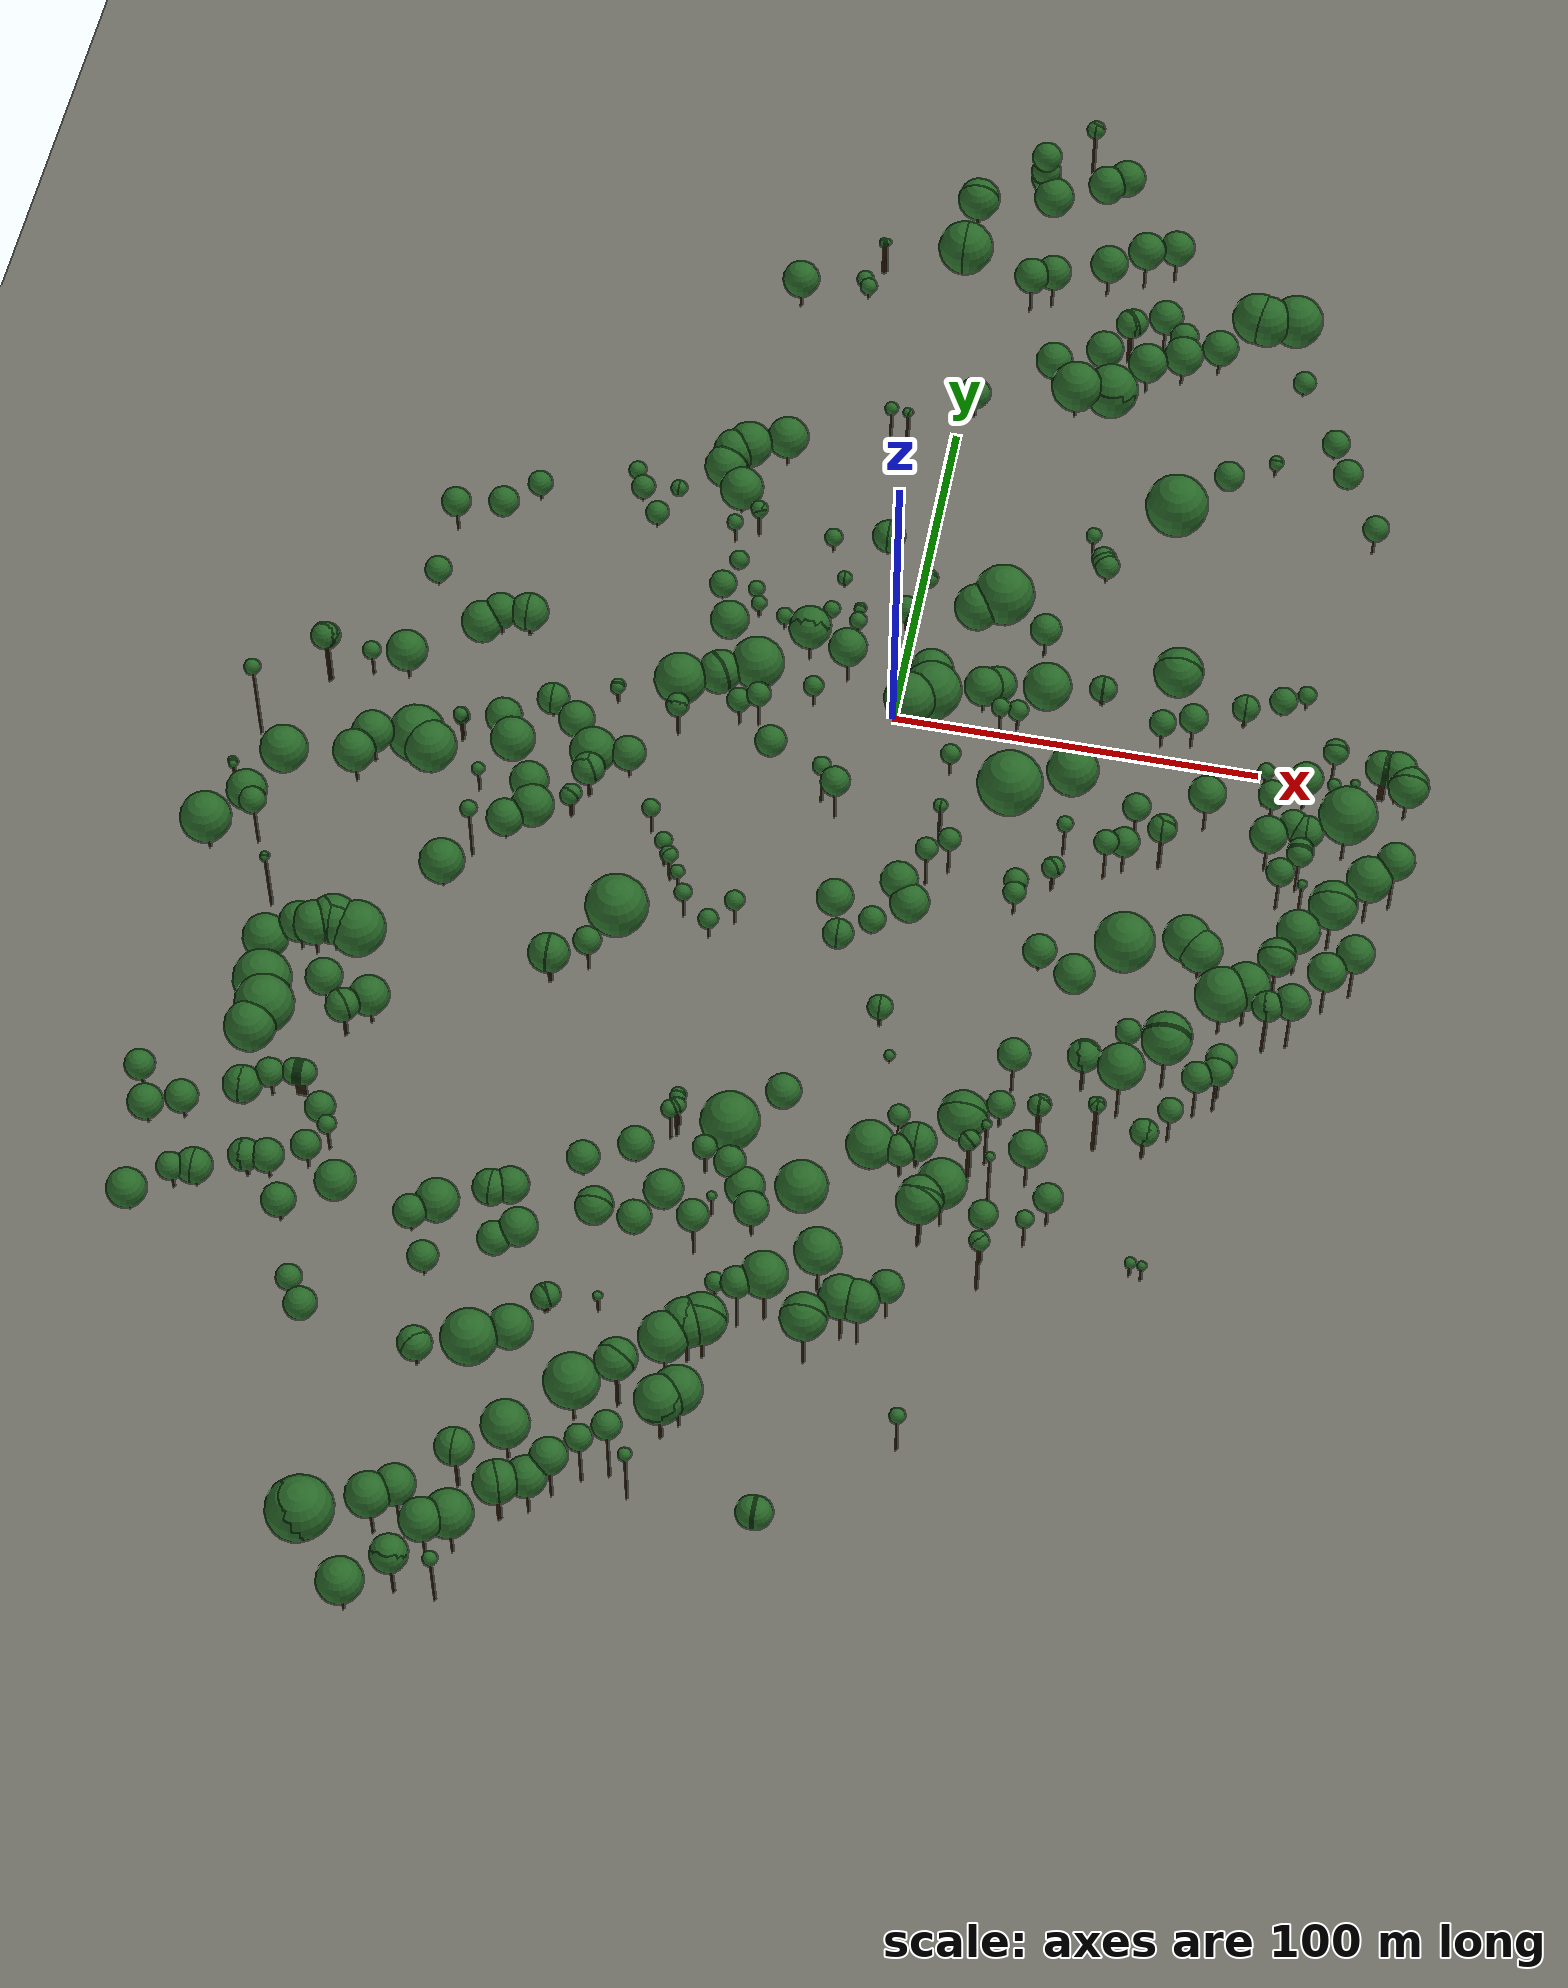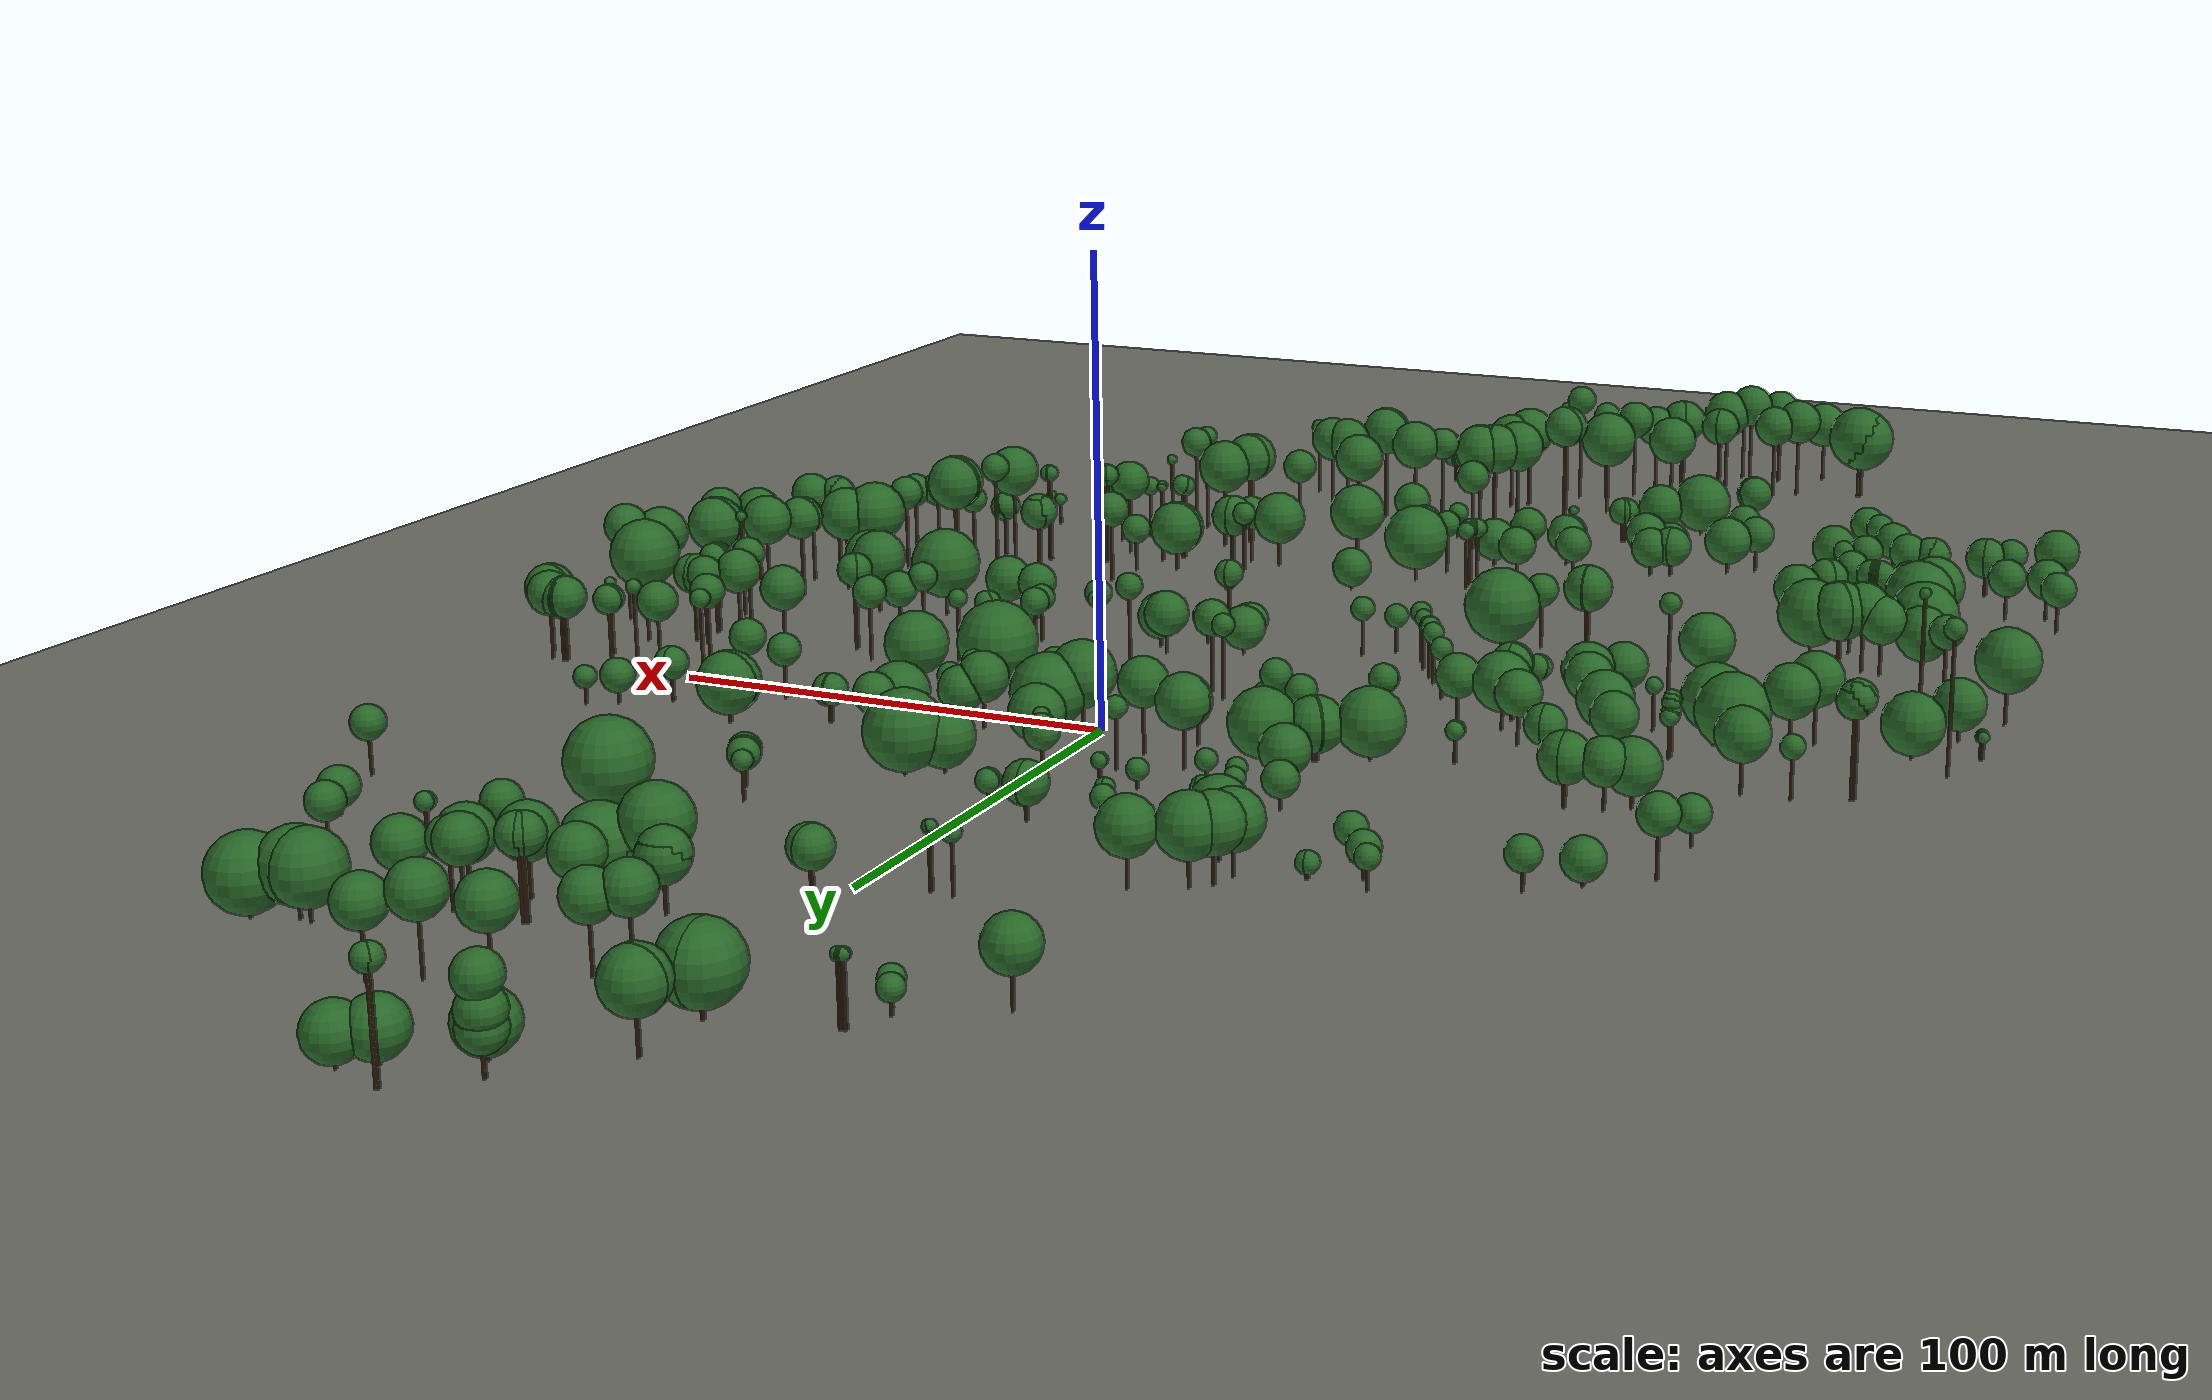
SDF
<sdf version="1.9">
 <world name="uav_arena_bk">
  <spherical_coordinates>
   <surface_model>EARTH_WGS84</surface_model>
   <world_frame_orientation>ENU</world_frame_orientation>
   <latitude_deg>10.7738076</latitude_deg>
   <longitude_deg>106.6599783</longitude_deg>
   <elevation>0</elevation>
   <heading_deg>0</heading_deg>
  </spherical_coordinates>
  <physics name="default" type="ode">
   <max_step_size>0.004</max_step_size>
   <real_time_factor>1.0</real_time_factor>
  </physics>
  <gravity>0 0 -9.8</gravity>
  <plugin filename="gz-sim-physics-system" name="gz::sim::systems::Physics"/>
  <plugin filename="gz-sim-user-commands-system" name="gz::sim::systems::UserCommands"/>
  <plugin filename="gz-sim-scene-broadcaster-system" name="gz::sim::systems::SceneBroadcaster"/>
  <plugin filename="gz-sim-contact-system" name="gz::sim::systems::Contact"/>
  <plugin filename="gz-sim-imu-system" name="gz::sim::systems::Imu"/>
  <plugin filename="gz-sim-air-pressure-system" name="gz::sim::systems::AirPressure"/>
  <plugin filename="gz-sim-apply-link-wrench-system" name="gz::sim::systems::ApplyLinkWrench"/>
  <plugin filename="gz-sim-navsat-system" name="gz::sim::systems::NavSat"/>
  <plugin filename="gz-sim-magnetometer-system" name="gz::sim::systems::Magnetometer"/>
  <plugin filename="gz-sim-sensors-system" name="gz::sim::systems::Sensors">
   <render_engine>ogre2</render_engine>
  </plugin>
  <light type="directional" name="sun">
   <cast_shadows>false</cast_shadows>
   <pose>0 0 100 0 0 0</pose>
   <diffuse>0.9 0.9 0.9 1</diffuse>
   <specular>0.25 0.25 0.25 1</specular>
   <direction>-0.4 0.3 -0.9</direction>
  </light>
  <model name="ground_plane">
   <static>true</static>
   <link name="link">
    <collision name="collision">
     <geometry><plane><normal>0 0 1</normal><size>1200 1200</size></plane></geometry>
    </collision>
    <visual name="visual">
     <geometry><plane><normal>0 0 1</normal><size>1200 1200</size></plane></geometry>
     <material><ambient>0.35 0.35 0.33 1</ambient><diffuse>0.45 0.45 0.42 1</diffuse></material>
    </visual>
   </link>
  </model>
  <model name="tree_001">
   <static>true</static>
   <pose>22.447 203.263 0 0 0 0</pose>
   <link name="link">
    <collision name="trunk_collision">
     <pose>0 0 9.445 0 0 0</pose>
     <geometry><cylinder><radius>0.30</radius><length>18.890</length></cylinder></geometry>
    </collision>
    <visual name="trunk_visual">
     <pose>0 0 9.445 0 0 0</pose>
     <geometry><cylinder><radius>0.30</radius><length>18.890</length></cylinder></geometry>
     <material><ambient>0.25 0.18 0.11 1</ambient><diffuse>0.35 0.25 0.15 1</diffuse></material>
    </visual>
    <collision name="canopy_collision">
     <pose>0 0 21.390 0 0 0</pose>
     <geometry><sphere><radius>2.500</radius></sphere></geometry>
    </collision>
    <visual name="canopy_visual">
     <pose>0 0 21.390 0 0 0</pose>
     <geometry><sphere><radius>2.500</radius></sphere></geometry>
     <material><ambient>0.10 0.28 0.10 1</ambient><diffuse>0.16 0.42 0.16 1</diffuse></material>
     <plugin filename="gz-sim-label-system" name="gz::sim::systems::Label"><label>2</label></plugin>
    </visual>
   </link>
  </model>
  <model name="tree_002">
   <static>true</static>
   <pose>22.196 203.014 0 0 0 0</pose>
   <link name="link">
    <collision name="trunk_collision">
     <pose>0 0 9.440 0 0 0</pose>
     <geometry><cylinder><radius>0.30</radius><length>18.880</length></cylinder></geometry>
    </collision>
    <visual name="trunk_visual">
     <pose>0 0 9.440 0 0 0</pose>
     <geometry><cylinder><radius>0.30</radius><length>18.880</length></cylinder></geometry>
     <material><ambient>0.25 0.18 0.11 1</ambient><diffuse>0.35 0.25 0.15 1</diffuse></material>
    </visual>
    <collision name="canopy_collision">
     <pose>0 0 21.380 0 0 0</pose>
     <geometry><sphere><radius>2.500</radius></sphere></geometry>
    </collision>
    <visual name="canopy_visual">
     <pose>0 0 21.380 0 0 0</pose>
     <geometry><sphere><radius>2.500</radius></sphere></geometry>
     <material><ambient>0.10 0.28 0.10 1</ambient><diffuse>0.16 0.42 0.16 1</diffuse></material>
     <plugin filename="gz-sim-label-system" name="gz::sim::systems::Label"><label>2</label></plugin>
    </visual>
   </link>
  </model>
  <model name="tree_003">
   <static>true</static>
   <pose>22.446 203.013 0 0 0 0</pose>
   <link name="link">
    <collision name="trunk_collision">
     <pose>0 0 9.435 0 0 0</pose>
     <geometry><cylinder><radius>0.30</radius><length>18.870</length></cylinder></geometry>
    </collision>
    <visual name="trunk_visual">
     <pose>0 0 9.435 0 0 0</pose>
     <geometry><cylinder><radius>0.30</radius><length>18.870</length></cylinder></geometry>
     <material><ambient>0.25 0.18 0.11 1</ambient><diffuse>0.35 0.25 0.15 1</diffuse></material>
    </visual>
    <collision name="canopy_collision">
     <pose>0 0 21.370 0 0 0</pose>
     <geometry><sphere><radius>2.500</radius></sphere></geometry>
    </collision>
    <visual name="canopy_visual">
     <pose>0 0 21.370 0 0 0</pose>
     <geometry><sphere><radius>2.500</radius></sphere></geometry>
     <material><ambient>0.10 0.28 0.10 1</ambient><diffuse>0.16 0.42 0.16 1</diffuse></material>
     <plugin filename="gz-sim-label-system" name="gz::sim::systems::Label"><label>2</label></plugin>
    </visual>
   </link>
  </model>
  <model name="tree_004">
   <static>true</static>
   <pose>32.928 199.706 0 0 0 0</pose>
   <link name="link">
    <collision name="trunk_collision">
     <pose>0 0 0.500 0 0 0</pose>
     <geometry><cylinder><radius>0.30</radius><length>1.000</length></cylinder></geometry>
    </collision>
    <visual name="trunk_visual">
     <pose>0 0 0.500 0 0 0</pose>
     <geometry><cylinder><radius>0.30</radius><length>1.000</length></cylinder></geometry>
     <material><ambient>0.25 0.18 0.11 1</ambient><diffuse>0.35 0.25 0.15 1</diffuse></material>
    </visual>
    <collision name="canopy_collision">
     <pose>0 0 6.270 0 0 0</pose>
     <geometry><sphere><radius>5.270</radius></sphere></geometry>
    </collision>
    <visual name="canopy_visual">
     <pose>0 0 6.270 0 0 0</pose>
     <geometry><sphere><radius>5.270</radius></sphere></geometry>
     <material><ambient>0.10 0.28 0.10 1</ambient><diffuse>0.16 0.42 0.16 1</diffuse></material>
     <plugin filename="gz-sim-label-system" name="gz::sim::systems::Label"><label>2</label></plugin>
    </visual>
   </link>
  </model>
  <model name="tree_005">
   <static>true</static>
   <pose>27.658 195.985 0 0 0 0</pose>
   <link name="link">
    <collision name="trunk_collision">
     <pose>0 0 0.500 0 0 0</pose>
     <geometry><cylinder><radius>0.30</radius><length>1.000</length></cylinder></geometry>
    </collision>
    <visual name="trunk_visual">
     <pose>0 0 0.500 0 0 0</pose>
     <geometry><cylinder><radius>0.30</radius><length>1.000</length></cylinder></geometry>
     <material><ambient>0.25 0.18 0.11 1</ambient><diffuse>0.35 0.25 0.15 1</diffuse></material>
    </visual>
    <collision name="canopy_collision">
     <pose>0 0 6.500 0 0 0</pose>
     <geometry><sphere><radius>5.500</radius></sphere></geometry>
    </collision>
    <visual name="canopy_visual">
     <pose>0 0 6.500 0 0 0</pose>
     <geometry><sphere><radius>5.500</radius></sphere></geometry>
     <material><ambient>0.10 0.28 0.10 1</ambient><diffuse>0.16 0.42 0.16 1</diffuse></material>
     <plugin filename="gz-sim-label-system" name="gz::sim::systems::Label"><label>2</label></plugin>
    </visual>
   </link>
  </model>
  <model name="tree_006">
   <static>true</static>
   <pose>9.646 193.832 0 0 0 0</pose>
   <link name="link">
    <collision name="trunk_collision">
     <pose>0 0 6.415 0 0 0</pose>
     <geometry><cylinder><radius>0.30</radius><length>12.830</length></cylinder></geometry>
    </collision>
    <visual name="trunk_visual">
     <pose>0 0 6.415 0 0 0</pose>
     <geometry><cylinder><radius>0.30</radius><length>12.830</length></cylinder></geometry>
     <material><ambient>0.25 0.18 0.11 1</ambient><diffuse>0.35 0.25 0.15 1</diffuse></material>
    </visual>
    <collision name="canopy_collision">
     <pose>0 0 17.090 0 0 0</pose>
     <geometry><sphere><radius>4.260</radius></sphere></geometry>
    </collision>
    <visual name="canopy_visual">
     <pose>0 0 17.090 0 0 0</pose>
     <geometry><sphere><radius>4.260</radius></sphere></geometry>
     <material><ambient>0.10 0.28 0.10 1</ambient><diffuse>0.16 0.42 0.16 1</diffuse></material>
     <plugin filename="gz-sim-label-system" name="gz::sim::systems::Label"><label>2</label></plugin>
    </visual>
   </link>
  </model>
  <model name="tree_007">
   <static>true</static>
   <pose>9.644 193.582 0 0 0 0</pose>
   <link name="link">
    <collision name="trunk_collision">
     <pose>0 0 3.560 0 0 0</pose>
     <geometry><cylinder><radius>0.30</radius><length>7.120</length></cylinder></geometry>
    </collision>
    <visual name="trunk_visual">
     <pose>0 0 3.560 0 0 0</pose>
     <geometry><cylinder><radius>0.30</radius><length>7.120</length></cylinder></geometry>
     <material><ambient>0.25 0.18 0.11 1</ambient><diffuse>0.35 0.25 0.15 1</diffuse></material>
    </visual>
    <collision name="canopy_collision">
     <pose>0 0 11.380 0 0 0</pose>
     <geometry><sphere><radius>4.260</radius></sphere></geometry>
    </collision>
    <visual name="canopy_visual">
     <pose>0 0 11.380 0 0 0</pose>
     <geometry><sphere><radius>4.260</radius></sphere></geometry>
     <material><ambient>0.10 0.28 0.10 1</ambient><diffuse>0.16 0.42 0.16 1</diffuse></material>
     <plugin filename="gz-sim-label-system" name="gz::sim::systems::Label"><label>2</label></plugin>
    </visual>
   </link>
  </model>
  <model name="tree_008">
   <static>true</static>
   <pose>9.893 193.331 0 0 0 0</pose>
   <link name="link">
    <collision name="trunk_collision">
     <pose>0 0 1.945 0 0 0</pose>
     <geometry><cylinder><radius>0.30</radius><length>3.890</length></cylinder></geometry>
    </collision>
    <visual name="trunk_visual">
     <pose>0 0 1.945 0 0 0</pose>
     <geometry><cylinder><radius>0.30</radius><length>3.890</length></cylinder></geometry>
     <material><ambient>0.25 0.18 0.11 1</ambient><diffuse>0.35 0.25 0.15 1</diffuse></material>
    </visual>
    <collision name="canopy_collision">
     <pose>0 0 8.150 0 0 0</pose>
     <geometry><sphere><radius>4.260</radius></sphere></geometry>
    </collision>
    <visual name="canopy_visual">
     <pose>0 0 8.150 0 0 0</pose>
     <geometry><sphere><radius>4.260</radius></sphere></geometry>
     <material><ambient>0.10 0.28 0.10 1</ambient><diffuse>0.16 0.42 0.16 1</diffuse></material>
     <plugin filename="gz-sim-label-system" name="gz::sim::systems::Label"><label>2</label></plugin>
    </visual>
   </link>
  </model>
  <model name="tree_009">
   <static>true</static>
   <pose>13.114 188.064 0 0 0 0</pose>
   <link name="link">
    <collision name="trunk_collision">
     <pose>0 0 0.500 0 0 0</pose>
     <geometry><cylinder><radius>0.30</radius><length>1.000</length></cylinder></geometry>
    </collision>
    <visual name="trunk_visual">
     <pose>0 0 0.500 0 0 0</pose>
     <geometry><cylinder><radius>0.30</radius><length>1.000</length></cylinder></geometry>
     <material><ambient>0.25 0.18 0.11 1</ambient><diffuse>0.35 0.25 0.15 1</diffuse></material>
    </visual>
    <collision name="canopy_collision">
     <pose>0 0 6.700 0 0 0</pose>
     <geometry><sphere><radius>5.700</radius></sphere></geometry>
    </collision>
    <visual name="canopy_visual">
     <pose>0 0 6.700 0 0 0</pose>
     <geometry><sphere><radius>5.700</radius></sphere></geometry>
     <material><ambient>0.10 0.28 0.10 1</ambient><diffuse>0.16 0.42 0.16 1</diffuse></material>
     <plugin filename="gz-sim-label-system" name="gz::sim::systems::Label"><label>2</label></plugin>
    </visual>
   </link>
  </model>
  <model name="tree_010">
   <static>true</static>
   <pose>-7.441 177.925 0 0 0 0</pose>
   <link name="link">
    <collision name="trunk_collision">
     <pose>0 0 3.455 0 0 0</pose>
     <geometry><cylinder><radius>0.30</radius><length>6.910</length></cylinder></geometry>
    </collision>
    <visual name="trunk_visual">
     <pose>0 0 3.455 0 0 0</pose>
     <geometry><cylinder><radius>0.30</radius><length>6.910</length></cylinder></geometry>
     <material><ambient>0.25 0.18 0.11 1</ambient><diffuse>0.35 0.25 0.15 1</diffuse></material>
    </visual>
    <collision name="canopy_collision">
     <pose>0 0 12.910 0 0 0</pose>
     <geometry><sphere><radius>6.000</radius></sphere></geometry>
    </collision>
    <visual name="canopy_visual">
     <pose>0 0 12.910 0 0 0</pose>
     <geometry><sphere><radius>6.000</radius></sphere></geometry>
     <material><ambient>0.10 0.28 0.10 1</ambient><diffuse>0.16 0.42 0.16 1</diffuse></material>
     <plugin filename="gz-sim-label-system" name="gz::sim::systems::Label"><label>2</label></plugin>
    </visual>
   </link>
  </model>
  <model name="tree_011">
   <static>true</static>
   <pose>-7.442 177.675 0 0 0 0</pose>
   <link name="link">
    <collision name="trunk_collision">
     <pose>0 0 3.455 0 0 0</pose>
     <geometry><cylinder><radius>0.30</radius><length>6.910</length></cylinder></geometry>
    </collision>
    <visual name="trunk_visual">
     <pose>0 0 3.455 0 0 0</pose>
     <geometry><cylinder><radius>0.30</radius><length>6.910</length></cylinder></geometry>
     <material><ambient>0.25 0.18 0.11 1</ambient><diffuse>0.35 0.25 0.15 1</diffuse></material>
    </visual>
    <collision name="canopy_collision">
     <pose>0 0 12.910 0 0 0</pose>
     <geometry><sphere><radius>6.000</radius></sphere></geometry>
    </collision>
    <visual name="canopy_visual">
     <pose>0 0 12.910 0 0 0</pose>
     <geometry><sphere><radius>6.000</radius></sphere></geometry>
     <material><ambient>0.10 0.28 0.10 1</ambient><diffuse>0.16 0.42 0.16 1</diffuse></material>
     <plugin filename="gz-sim-label-system" name="gz::sim::systems::Label"><label>2</label></plugin>
    </visual>
   </link>
  </model>
  <model name="tree_012">
   <static>true</static>
   <pose>51.762 169.104 0 0 0 0</pose>
   <link name="link">
    <collision name="trunk_collision">
     <pose>0 0 4.595 0 0 0</pose>
     <geometry><cylinder><radius>0.30</radius><length>9.190</length></cylinder></geometry>
    </collision>
    <visual name="trunk_visual">
     <pose>0 0 4.595 0 0 0</pose>
     <geometry><cylinder><radius>0.30</radius><length>9.190</length></cylinder></geometry>
     <material><ambient>0.25 0.18 0.11 1</ambient><diffuse>0.35 0.25 0.15 1</diffuse></material>
    </visual>
    <collision name="canopy_collision">
     <pose>0 0 14.190 0 0 0</pose>
     <geometry><sphere><radius>5.000</radius></sphere></geometry>
    </collision>
    <visual name="canopy_visual">
     <pose>0 0 14.190 0 0 0</pose>
     <geometry><sphere><radius>5.000</radius></sphere></geometry>
     <material><ambient>0.10 0.28 0.10 1</ambient><diffuse>0.16 0.42 0.16 1</diffuse></material>
     <plugin filename="gz-sim-label-system" name="gz::sim::systems::Label"><label>2</label></plugin>
    </visual>
   </link>
  </model>
  <model name="tree_013">
   <static>true</static>
   <pose>43.489 164.899 0 0 0 0</pose>
   <link name="link">
    <collision name="trunk_collision">
     <pose>0 0 5.310 0 0 0</pose>
     <geometry><cylinder><radius>0.30</radius><length>10.620</length></cylinder></geometry>
    </collision>
    <visual name="trunk_visual">
     <pose>0 0 5.310 0 0 0</pose>
     <geometry><cylinder><radius>0.30</radius><length>10.620</length></cylinder></geometry>
     <material><ambient>0.25 0.18 0.11 1</ambient><diffuse>0.35 0.25 0.15 1</diffuse></material>
    </visual>
    <collision name="canopy_collision">
     <pose>0 0 15.940 0 0 0</pose>
     <geometry><sphere><radius>5.320</radius></sphere></geometry>
    </collision>
    <visual name="canopy_visual">
     <pose>0 0 15.940 0 0 0</pose>
     <geometry><sphere><radius>5.320</radius></sphere></geometry>
     <material><ambient>0.10 0.28 0.10 1</ambient><diffuse>0.16 0.42 0.16 1</diffuse></material>
     <plugin filename="gz-sim-label-system" name="gz::sim::systems::Label"><label>2</label></plugin>
    </visual>
   </link>
  </model>
  <model name="tree_014">
   <static>true</static>
   <pose>-8.530 161.431 0 0 0 0</pose>
   <link name="link">
    <collision name="trunk_collision">
     <pose>0 0 1.090 0 0 0</pose>
     <geometry><cylinder><radius>0.30</radius><length>2.180</length></cylinder></geometry>
    </collision>
    <visual name="trunk_visual">
     <pose>0 0 1.090 0 0 0</pose>
     <geometry><cylinder><radius>0.30</radius><length>2.180</length></cylinder></geometry>
     <material><ambient>0.25 0.18 0.11 1</ambient><diffuse>0.35 0.25 0.15 1</diffuse></material>
    </visual>
    <collision name="canopy_collision">
     <pose>0 0 9.880 0 0 0</pose>
     <geometry><sphere><radius>7.700</radius></sphere></geometry>
    </collision>
    <visual name="canopy_visual">
     <pose>0 0 9.880 0 0 0</pose>
     <geometry><sphere><radius>7.700</radius></sphere></geometry>
     <material><ambient>0.10 0.28 0.10 1</ambient><diffuse>0.16 0.42 0.16 1</diffuse></material>
     <plugin filename="gz-sim-label-system" name="gz::sim::systems::Label"><label>2</label></plugin>
    </visual>
   </link>
  </model>
  <model name="tree_015">
   <static>true</static>
   <pose>-8.280 161.429 0 0 0 0</pose>
   <link name="link">
    <collision name="trunk_collision">
     <pose>0 0 1.090 0 0 0</pose>
     <geometry><cylinder><radius>0.30</radius><length>2.180</length></cylinder></geometry>
    </collision>
    <visual name="trunk_visual">
     <pose>0 0 1.090 0 0 0</pose>
     <geometry><cylinder><radius>0.30</radius><length>2.180</length></cylinder></geometry>
     <material><ambient>0.25 0.18 0.11 1</ambient><diffuse>0.35 0.25 0.15 1</diffuse></material>
    </visual>
    <collision name="canopy_collision">
     <pose>0 0 9.880 0 0 0</pose>
     <geometry><sphere><radius>7.700</radius></sphere></geometry>
    </collision>
    <visual name="canopy_visual">
     <pose>0 0 9.880 0 0 0</pose>
     <geometry><sphere><radius>7.700</radius></sphere></geometry>
     <material><ambient>0.10 0.28 0.10 1</ambient><diffuse>0.16 0.42 0.16 1</diffuse></material>
     <plugin filename="gz-sim-label-system" name="gz::sim::systems::Label"><label>2</label></plugin>
    </visual>
   </link>
  </model>
  <model name="tree_016">
   <static>true</static>
   <pose>33.462 159.953 0 0 0 0</pose>
   <link name="link">
    <collision name="trunk_collision">
     <pose>0 0 4.165 0 0 0</pose>
     <geometry><cylinder><radius>0.30</radius><length>8.330</length></cylinder></geometry>
    </collision>
    <visual name="trunk_visual">
     <pose>0 0 4.165 0 0 0</pose>
     <geometry><cylinder><radius>0.30</radius><length>8.330</length></cylinder></geometry>
     <material><ambient>0.25 0.18 0.11 1</ambient><diffuse>0.35 0.25 0.15 1</diffuse></material>
    </visual>
    <collision name="canopy_collision">
     <pose>0 0 13.650 0 0 0</pose>
     <geometry><sphere><radius>5.320</radius></sphere></geometry>
    </collision>
    <visual name="canopy_visual">
     <pose>0 0 13.650 0 0 0</pose>
     <geometry><sphere><radius>5.320</radius></sphere></geometry>
     <material><ambient>0.10 0.28 0.10 1</ambient><diffuse>0.16 0.42 0.16 1</diffuse></material>
     <plugin filename="gz-sim-label-system" name="gz::sim::systems::Label"><label>2</label></plugin>
    </visual>
   </link>
  </model>
  <model name="tree_017">
   <static>true</static>
   <pose>-31.558 156.305 0 0 0 0</pose>
   <link name="link">
    <collision name="trunk_collision">
     <pose>0 0 5.820 0 0 0</pose>
     <geometry><cylinder><radius>0.30</radius><length>11.640</length></cylinder></geometry>
    </collision>
    <visual name="trunk_visual">
     <pose>0 0 5.820 0 0 0</pose>
     <geometry><cylinder><radius>0.30</radius><length>11.640</length></cylinder></geometry>
     <material><ambient>0.25 0.18 0.11 1</ambient><diffuse>0.35 0.25 0.15 1</diffuse></material>
    </visual>
    <collision name="canopy_collision">
     <pose>0 0 12.890 0 0 0</pose>
     <geometry><sphere><radius>1.250</radius></sphere></geometry>
    </collision>
    <visual name="canopy_visual">
     <pose>0 0 12.890 0 0 0</pose>
     <geometry><sphere><radius>1.250</radius></sphere></geometry>
     <material><ambient>0.10 0.28 0.10 1</ambient><diffuse>0.16 0.42 0.16 1</diffuse></material>
     <plugin filename="gz-sim-label-system" name="gz::sim::systems::Label"><label>2</label></plugin>
    </visual>
   </link>
  </model>
  <model name="tree_018">
   <static>true</static>
   <pose>-31.308 156.304 0 0 0 0</pose>
   <link name="link">
    <collision name="trunk_collision">
     <pose>0 0 5.820 0 0 0</pose>
     <geometry><cylinder><radius>0.30</radius><length>11.640</length></cylinder></geometry>
    </collision>
    <visual name="trunk_visual">
     <pose>0 0 5.820 0 0 0</pose>
     <geometry><cylinder><radius>0.30</radius><length>11.640</length></cylinder></geometry>
     <material><ambient>0.25 0.18 0.11 1</ambient><diffuse>0.35 0.25 0.15 1</diffuse></material>
    </visual>
    <collision name="canopy_collision">
     <pose>0 0 12.890 0 0 0</pose>
     <geometry><sphere><radius>1.250</radius></sphere></geometry>
    </collision>
    <visual name="canopy_visual">
     <pose>0 0 12.890 0 0 0</pose>
     <geometry><sphere><radius>1.250</radius></sphere></geometry>
     <material><ambient>0.10 0.28 0.10 1</ambient><diffuse>0.16 0.42 0.16 1</diffuse></material>
     <plugin filename="gz-sim-label-system" name="gz::sim::systems::Label"><label>2</label></plugin>
    </visual>
   </link>
  </model>
  <model name="tree_019">
   <static>true</static>
   <pose>-31.058 156.303 0 0 0 0</pose>
   <link name="link">
    <collision name="trunk_collision">
     <pose>0 0 5.820 0 0 0</pose>
     <geometry><cylinder><radius>0.30</radius><length>11.640</length></cylinder></geometry>
    </collision>
    <visual name="trunk_visual">
     <pose>0 0 5.820 0 0 0</pose>
     <geometry><cylinder><radius>0.30</radius><length>11.640</length></cylinder></geometry>
     <material><ambient>0.25 0.18 0.11 1</ambient><diffuse>0.35 0.25 0.15 1</diffuse></material>
    </visual>
    <collision name="canopy_collision">
     <pose>0 0 12.890 0 0 0</pose>
     <geometry><sphere><radius>1.250</radius></sphere></geometry>
    </collision>
    <visual name="canopy_visual">
     <pose>0 0 12.890 0 0 0</pose>
     <geometry><sphere><radius>1.250</radius></sphere></geometry>
     <material><ambient>0.10 0.28 0.10 1</ambient><diffuse>0.16 0.42 0.16 1</diffuse></material>
     <plugin filename="gz-sim-label-system" name="gz::sim::systems::Label"><label>2</label></plugin>
    </visual>
   </link>
  </model>
  <model name="tree_020">
   <static>true</static>
   <pose>-30.808 156.301 0 0 0 0</pose>
   <link name="link">
    <collision name="trunk_collision">
     <pose>0 0 5.820 0 0 0</pose>
     <geometry><cylinder><radius>0.30</radius><length>11.640</length></cylinder></geometry>
    </collision>
    <visual name="trunk_visual">
     <pose>0 0 5.820 0 0 0</pose>
     <geometry><cylinder><radius>0.30</radius><length>11.640</length></cylinder></geometry>
     <material><ambient>0.25 0.18 0.11 1</ambient><diffuse>0.35 0.25 0.15 1</diffuse></material>
    </visual>
    <collision name="canopy_collision">
     <pose>0 0 12.890 0 0 0</pose>
     <geometry><sphere><radius>1.250</radius></sphere></geometry>
    </collision>
    <visual name="canopy_visual">
     <pose>0 0 12.890 0 0 0</pose>
     <geometry><sphere><radius>1.250</radius></sphere></geometry>
     <material><ambient>0.10 0.28 0.10 1</ambient><diffuse>0.16 0.42 0.16 1</diffuse></material>
     <plugin filename="gz-sim-label-system" name="gz::sim::systems::Label"><label>2</label></plugin>
    </visual>
   </link>
  </model>
  <model name="tree_021">
   <static>true</static>
   <pose>-30.558 156.300 0 0 0 0</pose>
   <link name="link">
    <collision name="trunk_collision">
     <pose>0 0 5.820 0 0 0</pose>
     <geometry><cylinder><radius>0.30</radius><length>11.640</length></cylinder></geometry>
    </collision>
    <visual name="trunk_visual">
     <pose>0 0 5.820 0 0 0</pose>
     <geometry><cylinder><radius>0.30</radius><length>11.640</length></cylinder></geometry>
     <material><ambient>0.25 0.18 0.11 1</ambient><diffuse>0.35 0.25 0.15 1</diffuse></material>
    </visual>
    <collision name="canopy_collision">
     <pose>0 0 12.890 0 0 0</pose>
     <geometry><sphere><radius>1.250</radius></sphere></geometry>
    </collision>
    <visual name="canopy_visual">
     <pose>0 0 12.890 0 0 0</pose>
     <geometry><sphere><radius>1.250</radius></sphere></geometry>
     <material><ambient>0.10 0.28 0.10 1</ambient><diffuse>0.16 0.42 0.16 1</diffuse></material>
     <plugin filename="gz-sim-label-system" name="gz::sim::systems::Label"><label>2</label></plugin>
    </visual>
   </link>
  </model>
  <model name="tree_022">
   <static>true</static>
   <pose>-31.560 156.055 0 0 0 0</pose>
   <link name="link">
    <collision name="trunk_collision">
     <pose>0 0 5.820 0 0 0</pose>
     <geometry><cylinder><radius>0.30</radius><length>11.640</length></cylinder></geometry>
    </collision>
    <visual name="trunk_visual">
     <pose>0 0 5.820 0 0 0</pose>
     <geometry><cylinder><radius>0.30</radius><length>11.640</length></cylinder></geometry>
     <material><ambient>0.25 0.18 0.11 1</ambient><diffuse>0.35 0.25 0.15 1</diffuse></material>
    </visual>
    <collision name="canopy_collision">
     <pose>0 0 12.890 0 0 0</pose>
     <geometry><sphere><radius>1.250</radius></sphere></geometry>
    </collision>
    <visual name="canopy_visual">
     <pose>0 0 12.890 0 0 0</pose>
     <geometry><sphere><radius>1.250</radius></sphere></geometry>
     <material><ambient>0.10 0.28 0.10 1</ambient><diffuse>0.16 0.42 0.16 1</diffuse></material>
     <plugin filename="gz-sim-label-system" name="gz::sim::systems::Label"><label>2</label></plugin>
    </visual>
   </link>
  </model>
  <model name="tree_023">
   <static>true</static>
   <pose>-31.310 156.054 0 0 0 0</pose>
   <link name="link">
    <collision name="trunk_collision">
     <pose>0 0 5.820 0 0 0</pose>
     <geometry><cylinder><radius>0.30</radius><length>11.640</length></cylinder></geometry>
    </collision>
    <visual name="trunk_visual">
     <pose>0 0 5.820 0 0 0</pose>
     <geometry><cylinder><radius>0.30</radius><length>11.640</length></cylinder></geometry>
     <material><ambient>0.25 0.18 0.11 1</ambient><diffuse>0.35 0.25 0.15 1</diffuse></material>
    </visual>
    <collision name="canopy_collision">
     <pose>0 0 12.890 0 0 0</pose>
     <geometry><sphere><radius>1.250</radius></sphere></geometry>
    </collision>
    <visual name="canopy_visual">
     <pose>0 0 12.890 0 0 0</pose>
     <geometry><sphere><radius>1.250</radius></sphere></geometry>
     <material><ambient>0.10 0.28 0.10 1</ambient><diffuse>0.16 0.42 0.16 1</diffuse></material>
     <plugin filename="gz-sim-label-system" name="gz::sim::systems::Label"><label>2</label></plugin>
    </visual>
   </link>
  </model>
  <model name="tree_024">
   <static>true</static>
   <pose>-31.060 156.053 0 0 0 0</pose>
   <link name="link">
    <collision name="trunk_collision">
     <pose>0 0 5.820 0 0 0</pose>
     <geometry><cylinder><radius>0.30</radius><length>11.640</length></cylinder></geometry>
    </collision>
    <visual name="trunk_visual">
     <pose>0 0 5.820 0 0 0</pose>
     <geometry><cylinder><radius>0.30</radius><length>11.640</length></cylinder></geometry>
     <material><ambient>0.25 0.18 0.11 1</ambient><diffuse>0.35 0.25 0.15 1</diffuse></material>
    </visual>
    <collision name="canopy_collision">
     <pose>0 0 12.890 0 0 0</pose>
     <geometry><sphere><radius>1.250</radius></sphere></geometry>
    </collision>
    <visual name="canopy_visual">
     <pose>0 0 12.890 0 0 0</pose>
     <geometry><sphere><radius>1.250</radius></sphere></geometry>
     <material><ambient>0.10 0.28 0.10 1</ambient><diffuse>0.16 0.42 0.16 1</diffuse></material>
     <plugin filename="gz-sim-label-system" name="gz::sim::systems::Label"><label>2</label></plugin>
    </visual>
   </link>
  </model>
  <model name="tree_025">
   <static>true</static>
   <pose>88.927 153.402 0 0 0 0</pose>
   <link name="link">
    <collision name="trunk_collision">
     <pose>0 0 0.500 0 0 0</pose>
     <geometry><cylinder><radius>0.30</radius><length>1.000</length></cylinder></geometry>
    </collision>
    <visual name="trunk_visual">
     <pose>0 0 0.500 0 0 0</pose>
     <geometry><cylinder><radius>0.30</radius><length>1.000</length></cylinder></geometry>
     <material><ambient>0.25 0.18 0.11 1</ambient><diffuse>0.35 0.25 0.15 1</diffuse></material>
    </visual>
    <collision name="canopy_collision">
     <pose>0 0 8.500 0 0 0</pose>
     <geometry><sphere><radius>7.500</radius></sphere></geometry>
    </collision>
    <visual name="canopy_visual">
     <pose>0 0 8.500 0 0 0</pose>
     <geometry><sphere><radius>7.500</radius></sphere></geometry>
     <material><ambient>0.10 0.28 0.10 1</ambient><diffuse>0.16 0.42 0.16 1</diffuse></material>
     <plugin filename="gz-sim-label-system" name="gz::sim::systems::Label"><label>2</label></plugin>
    </visual>
   </link>
  </model>
  <model name="tree_026">
   <static>true</static>
   <pose>18.425 153.035 0 0 0 0</pose>
   <link name="link">
    <collision name="trunk_collision">
     <pose>0 0 4.770 0 0 0</pose>
     <geometry><cylinder><radius>0.30</radius><length>9.540</length></cylinder></geometry>
    </collision>
    <visual name="trunk_visual">
     <pose>0 0 4.770 0 0 0</pose>
     <geometry><cylinder><radius>0.30</radius><length>9.540</length></cylinder></geometry>
     <material><ambient>0.25 0.18 0.11 1</ambient><diffuse>0.35 0.25 0.15 1</diffuse></material>
    </visual>
    <collision name="canopy_collision">
     <pose>0 0 14.500 0 0 0</pose>
     <geometry><sphere><radius>4.960</radius></sphere></geometry>
    </collision>
    <visual name="canopy_visual">
     <pose>0 0 14.500 0 0 0</pose>
     <geometry><sphere><radius>4.960</radius></sphere></geometry>
     <material><ambient>0.10 0.28 0.10 1</ambient><diffuse>0.16 0.42 0.16 1</diffuse></material>
     <plugin filename="gz-sim-label-system" name="gz::sim::systems::Label"><label>2</label></plugin>
    </visual>
   </link>
  </model>
  <model name="tree_027">
   <static>true</static>
   <pose>77.914 150.962 0 0 0 0</pose>
   <link name="link">
    <collision name="trunk_collision">
     <pose>0 0 1.460 0 0 0</pose>
     <geometry><cylinder><radius>0.30</radius><length>2.920</length></cylinder></geometry>
    </collision>
    <visual name="trunk_visual">
     <pose>0 0 1.460 0 0 0</pose>
     <geometry><cylinder><radius>0.30</radius><length>2.920</length></cylinder></geometry>
     <material><ambient>0.25 0.18 0.11 1</ambient><diffuse>0.35 0.25 0.15 1</diffuse></material>
    </visual>
    <collision name="canopy_collision">
     <pose>0 0 10.170 0 0 0</pose>
     <geometry><sphere><radius>7.250</radius></sphere></geometry>
    </collision>
    <visual name="canopy_visual">
     <pose>0 0 10.170 0 0 0</pose>
     <geometry><sphere><radius>7.250</radius></sphere></geometry>
     <material><ambient>0.10 0.28 0.10 1</ambient><diffuse>0.16 0.42 0.16 1</diffuse></material>
     <plugin filename="gz-sim-label-system" name="gz::sim::systems::Label"><label>2</label></plugin>
    </visual>
   </link>
  </model>
  <model name="tree_028">
   <static>true</static>
   <pose>80.661 150.447 0 0 0 0</pose>
   <link name="link">
    <collision name="trunk_collision">
     <pose>0 0 1.455 0 0 0</pose>
     <geometry><cylinder><radius>0.30</radius><length>2.910</length></cylinder></geometry>
    </collision>
    <visual name="trunk_visual">
     <pose>0 0 1.455 0 0 0</pose>
     <geometry><cylinder><radius>0.30</radius><length>2.910</length></cylinder></geometry>
     <material><ambient>0.25 0.18 0.11 1</ambient><diffuse>0.35 0.25 0.15 1</diffuse></material>
    </visual>
    <collision name="canopy_collision">
     <pose>0 0 10.110 0 0 0</pose>
     <geometry><sphere><radius>7.200</radius></sphere></geometry>
    </collision>
    <visual name="canopy_visual">
     <pose>0 0 10.110 0 0 0</pose>
     <geometry><sphere><radius>7.200</radius></sphere></geometry>
     <material><ambient>0.10 0.28 0.10 1</ambient><diffuse>0.16 0.42 0.16 1</diffuse></material>
     <plugin filename="gz-sim-label-system" name="gz::sim::systems::Label"><label>2</label></plugin>
    </visual>
   </link>
  </model>
  <model name="tree_029">
   <static>true</static>
   <pose>12.657 149.816 0 0 0 0</pose>
   <link name="link">
    <collision name="trunk_collision">
     <pose>0 0 5.265 0 0 0</pose>
     <geometry><cylinder><radius>0.30</radius><length>10.530</length></cylinder></geometry>
    </collision>
    <visual name="trunk_visual">
     <pose>0 0 5.265 0 0 0</pose>
     <geometry><cylinder><radius>0.30</radius><length>10.530</length></cylinder></geometry>
     <material><ambient>0.25 0.18 0.11 1</ambient><diffuse>0.35 0.25 0.15 1</diffuse></material>
    </visual>
    <collision name="canopy_collision">
     <pose>0 0 15.530 0 0 0</pose>
     <geometry><sphere><radius>5.000</radius></sphere></geometry>
    </collision>
    <visual name="canopy_visual">
     <pose>0 0 15.530 0 0 0</pose>
     <geometry><sphere><radius>5.000</radius></sphere></geometry>
     <material><ambient>0.10 0.28 0.10 1</ambient><diffuse>0.16 0.42 0.16 1</diffuse></material>
     <plugin filename="gz-sim-label-system" name="gz::sim::systems::Label"><label>2</label></plugin>
    </visual>
   </link>
  </model>
  <model name="tree_030">
   <static>true</static>
   <pose>-35.351 148.326 0 0 0 0</pose>
   <link name="link">
    <collision name="trunk_collision">
     <pose>0 0 1.250 0 0 0</pose>
     <geometry><cylinder><radius>0.30</radius><length>2.500</length></cylinder></geometry>
    </collision>
    <visual name="trunk_visual">
     <pose>0 0 1.250 0 0 0</pose>
     <geometry><cylinder><radius>0.30</radius><length>2.500</length></cylinder></geometry>
     <material><ambient>0.25 0.18 0.11 1</ambient><diffuse>0.35 0.25 0.15 1</diffuse></material>
    </visual>
    <collision name="canopy_collision">
     <pose>0 0 4.960 0 0 0</pose>
     <geometry><sphere><radius>2.460</radius></sphere></geometry>
    </collision>
    <visual name="canopy_visual">
     <pose>0 0 4.960 0 0 0</pose>
     <geometry><sphere><radius>2.460</radius></sphere></geometry>
     <material><ambient>0.10 0.28 0.10 1</ambient><diffuse>0.16 0.42 0.16 1</diffuse></material>
     <plugin filename="gz-sim-label-system" name="gz::sim::systems::Label"><label>2</label></plugin>
    </visual>
   </link>
  </model>
  <model name="tree_031">
   <static>true</static>
   <pose>-33.866 145.568 0 0 0 0</pose>
   <link name="link">
    <collision name="trunk_collision">
     <pose>0 0 1.405 0 0 0</pose>
     <geometry><cylinder><radius>0.30</radius><length>2.810</length></cylinder></geometry>
    </collision>
    <visual name="trunk_visual">
     <pose>0 0 1.405 0 0 0</pose>
     <geometry><cylinder><radius>0.30</radius><length>2.810</length></cylinder></geometry>
     <material><ambient>0.25 0.18 0.11 1</ambient><diffuse>0.35 0.25 0.15 1</diffuse></material>
    </visual>
    <collision name="canopy_collision">
     <pose>0 0 5.270 0 0 0</pose>
     <geometry><sphere><radius>2.460</radius></sphere></geometry>
    </collision>
    <visual name="canopy_visual">
     <pose>0 0 5.270 0 0 0</pose>
     <geometry><sphere><radius>2.460</radius></sphere></geometry>
     <material><ambient>0.10 0.28 0.10 1</ambient><diffuse>0.16 0.42 0.16 1</diffuse></material>
     <plugin filename="gz-sim-label-system" name="gz::sim::systems::Label"><label>2</label></plugin>
    </visual>
   </link>
  </model>
  <model name="tree_032">
   <static>true</static>
   <pose>52.613 141.599 0 0 0 0</pose>
   <link name="link">
    <collision name="trunk_collision">
     <pose>0 0 5.445 0 0 0</pose>
     <geometry><cylinder><radius>0.30</radius><length>10.890</length></cylinder></geometry>
    </collision>
    <visual name="trunk_visual">
     <pose>0 0 5.445 0 0 0</pose>
     <geometry><cylinder><radius>0.30</radius><length>10.890</length></cylinder></geometry>
     <material><ambient>0.25 0.18 0.11 1</ambient><diffuse>0.35 0.25 0.15 1</diffuse></material>
    </visual>
    <collision name="canopy_collision">
     <pose>0 0 15.720 0 0 0</pose>
     <geometry><sphere><radius>4.830</radius></sphere></geometry>
    </collision>
    <visual name="canopy_visual">
     <pose>0 0 15.720 0 0 0</pose>
     <geometry><sphere><radius>4.830</radius></sphere></geometry>
     <material><ambient>0.10 0.28 0.10 1</ambient><diffuse>0.16 0.42 0.16 1</diffuse></material>
     <plugin filename="gz-sim-label-system" name="gz::sim::systems::Label"><label>2</label></plugin>
    </visual>
   </link>
  </model>
  <model name="tree_033">
   <static>true</static>
   <pose>-52.401 139.168 0 0 0 0</pose>
   <link name="link">
    <collision name="trunk_collision">
     <pose>0 0 3.230 0 0 0</pose>
     <geometry><cylinder><radius>0.30</radius><length>6.460</length></cylinder></geometry>
    </collision>
    <visual name="trunk_visual">
     <pose>0 0 3.230 0 0 0</pose>
     <geometry><cylinder><radius>0.30</radius><length>6.460</length></cylinder></geometry>
     <material><ambient>0.25 0.18 0.11 1</ambient><diffuse>0.35 0.25 0.15 1</diffuse></material>
    </visual>
    <collision name="canopy_collision">
     <pose>0 0 11.730 0 0 0</pose>
     <geometry><sphere><radius>5.270</radius></sphere></geometry>
    </collision>
    <visual name="canopy_visual">
     <pose>0 0 11.730 0 0 0</pose>
     <geometry><sphere><radius>5.270</radius></sphere></geometry>
     <material><ambient>0.10 0.28 0.10 1</ambient><diffuse>0.16 0.42 0.16 1</diffuse></material>
     <plugin filename="gz-sim-label-system" name="gz::sim::systems::Label"><label>2</label></plugin>
    </visual>
   </link>
  </model>
  <model name="tree_034">
   <static>true</static>
   <pose>43.839 137.147 0 0 0 0</pose>
   <link name="link">
    <collision name="trunk_collision">
     <pose>0 0 6.180 0 0 0</pose>
     <geometry><cylinder><radius>0.30</radius><length>12.360</length></cylinder></geometry>
    </collision>
    <visual name="trunk_visual">
     <pose>0 0 6.180 0 0 0</pose>
     <geometry><cylinder><radius>0.30</radius><length>12.360</length></cylinder></geometry>
     <material><ambient>0.25 0.18 0.11 1</ambient><diffuse>0.35 0.25 0.15 1</diffuse></material>
    </visual>
    <collision name="canopy_collision">
     <pose>0 0 16.430 0 0 0</pose>
     <geometry><sphere><radius>4.070</radius></sphere></geometry>
    </collision>
    <visual name="canopy_visual">
     <pose>0 0 16.430 0 0 0</pose>
     <geometry><sphere><radius>4.070</radius></sphere></geometry>
     <material><ambient>0.10 0.28 0.10 1</ambient><diffuse>0.16 0.42 0.16 1</diffuse></material>
     <plugin filename="gz-sim-label-system" name="gz::sim::systems::Label"><label>2</label></plugin>
    </visual>
   </link>
  </model>
  <model name="tree_035">
   <static>true</static>
   <pose>58.589 137.067 0 0 0 0</pose>
   <link name="link">
    <collision name="trunk_collision">
     <pose>0 0 4.835 0 0 0</pose>
     <geometry><cylinder><radius>0.30</radius><length>9.670</length></cylinder></geometry>
    </collision>
    <visual name="trunk_visual">
     <pose>0 0 4.835 0 0 0</pose>
     <geometry><cylinder><radius>0.30</radius><length>9.670</length></cylinder></geometry>
     <material><ambient>0.25 0.18 0.11 1</ambient><diffuse>0.35 0.25 0.15 1</diffuse></material>
    </visual>
    <collision name="canopy_collision">
     <pose>0 0 13.710 0 0 0</pose>
     <geometry><sphere><radius>4.040</radius></sphere></geometry>
    </collision>
    <visual name="canopy_visual">
     <pose>0 0 13.710 0 0 0</pose>
     <geometry><sphere><radius>4.040</radius></sphere></geometry>
     <material><ambient>0.10 0.28 0.10 1</ambient><diffuse>0.16 0.42 0.16 1</diffuse></material>
     <plugin filename="gz-sim-label-system" name="gz::sim::systems::Label"><label>2</label></plugin>
    </visual>
   </link>
  </model>
  <model name="tree_036">
   <static>true</static>
   <pose>69.088 137.010 0 0 0 0</pose>
   <link name="link">
    <collision name="trunk_collision">
     <pose>0 0 3.150 0 0 0</pose>
     <geometry><cylinder><radius>0.30</radius><length>6.300</length></cylinder></geometry>
    </collision>
    <visual name="trunk_visual">
     <pose>0 0 3.150 0 0 0</pose>
     <geometry><cylinder><radius>0.30</radius><length>6.300</length></cylinder></geometry>
     <material><ambient>0.25 0.18 0.11 1</ambient><diffuse>0.35 0.25 0.15 1</diffuse></material>
    </visual>
    <collision name="canopy_collision">
     <pose>0 0 11.360 0 0 0</pose>
     <geometry><sphere><radius>5.060</radius></sphere></geometry>
    </collision>
    <visual name="canopy_visual">
     <pose>0 0 11.360 0 0 0</pose>
     <geometry><sphere><radius>5.060</radius></sphere></geometry>
     <material><ambient>0.10 0.28 0.10 1</ambient><diffuse>0.16 0.42 0.16 1</diffuse></material>
     <plugin filename="gz-sim-label-system" name="gz::sim::systems::Label"><label>2</label></plugin>
    </visual>
   </link>
  </model>
  <model name="tree_037">
   <static>true</static>
   <pose>43.338 136.899 0 0 0 0</pose>
   <link name="link">
    <collision name="trunk_collision">
     <pose>0 0 6.190 0 0 0</pose>
     <geometry><cylinder><radius>0.30</radius><length>12.380</length></cylinder></geometry>
    </collision>
    <visual name="trunk_visual">
     <pose>0 0 6.190 0 0 0</pose>
     <geometry><cylinder><radius>0.30</radius><length>12.380</length></cylinder></geometry>
     <material><ambient>0.25 0.18 0.11 1</ambient><diffuse>0.35 0.25 0.15 1</diffuse></material>
    </visual>
    <collision name="canopy_collision">
     <pose>0 0 16.450 0 0 0</pose>
     <geometry><sphere><radius>4.070</radius></sphere></geometry>
    </collision>
    <visual name="canopy_visual">
     <pose>0 0 16.450 0 0 0</pose>
     <geometry><sphere><radius>4.070</radius></sphere></geometry>
     <material><ambient>0.10 0.28 0.10 1</ambient><diffuse>0.16 0.42 0.16 1</diffuse></material>
     <plugin filename="gz-sim-label-system" name="gz::sim::systems::Label"><label>2</label></plugin>
    </visual>
   </link>
  </model>
  <model name="tree_038">
   <static>true</static>
   <pose>43.588 136.898 0 0 0 0</pose>
   <link name="link">
    <collision name="trunk_collision">
     <pose>0 0 6.180 0 0 0</pose>
     <geometry><cylinder><radius>0.30</radius><length>12.360</length></cylinder></geometry>
    </collision>
    <visual name="trunk_visual">
     <pose>0 0 6.180 0 0 0</pose>
     <geometry><cylinder><radius>0.30</radius><length>12.360</length></cylinder></geometry>
     <material><ambient>0.25 0.18 0.11 1</ambient><diffuse>0.35 0.25 0.15 1</diffuse></material>
    </visual>
    <collision name="canopy_collision">
     <pose>0 0 16.430 0 0 0</pose>
     <geometry><sphere><radius>4.070</radius></sphere></geometry>
    </collision>
    <visual name="canopy_visual">
     <pose>0 0 16.430 0 0 0</pose>
     <geometry><sphere><radius>4.070</radius></sphere></geometry>
     <material><ambient>0.10 0.28 0.10 1</ambient><diffuse>0.16 0.42 0.16 1</diffuse></material>
     <plugin filename="gz-sim-label-system" name="gz::sim::systems::Label"><label>2</label></plugin>
    </visual>
   </link>
  </model>
  <model name="tree_039">
   <static>true</static>
   <pose>43.086 136.651 0 0 0 0</pose>
   <link name="link">
    <collision name="trunk_collision">
     <pose>0 0 6.190 0 0 0</pose>
     <geometry><cylinder><radius>0.30</radius><length>12.380</length></cylinder></geometry>
    </collision>
    <visual name="trunk_visual">
     <pose>0 0 6.190 0 0 0</pose>
     <geometry><cylinder><radius>0.30</radius><length>12.380</length></cylinder></geometry>
     <material><ambient>0.25 0.18 0.11 1</ambient><diffuse>0.35 0.25 0.15 1</diffuse></material>
    </visual>
    <collision name="canopy_collision">
     <pose>0 0 16.450 0 0 0</pose>
     <geometry><sphere><radius>4.070</radius></sphere></geometry>
    </collision>
    <visual name="canopy_visual">
     <pose>0 0 16.450 0 0 0</pose>
     <geometry><sphere><radius>4.070</radius></sphere></geometry>
     <material><ambient>0.10 0.28 0.10 1</ambient><diffuse>0.16 0.42 0.16 1</diffuse></material>
     <plugin filename="gz-sim-label-system" name="gz::sim::systems::Label"><label>2</label></plugin>
    </visual>
   </link>
  </model>
  <model name="tree_040">
   <static>true</static>
   <pose>94.072 133.874 0 0 0 0</pose>
   <link name="link">
    <collision name="trunk_collision">
     <pose>0 0 1.145 0 0 0</pose>
     <geometry><cylinder><radius>0.30</radius><length>2.290</length></cylinder></geometry>
    </collision>
    <visual name="trunk_visual">
     <pose>0 0 1.145 0 0 0</pose>
     <geometry><cylinder><radius>0.30</radius><length>2.290</length></cylinder></geometry>
     <material><ambient>0.25 0.18 0.11 1</ambient><diffuse>0.35 0.25 0.15 1</diffuse></material>
    </visual>
    <collision name="canopy_collision">
     <pose>0 0 5.540 0 0 0</pose>
     <geometry><sphere><radius>3.250</radius></sphere></geometry>
    </collision>
    <visual name="canopy_visual">
     <pose>0 0 5.540 0 0 0</pose>
     <geometry><sphere><radius>3.250</radius></sphere></geometry>
     <material><ambient>0.10 0.28 0.10 1</ambient><diffuse>0.16 0.42 0.16 1</diffuse></material>
     <plugin filename="gz-sim-label-system" name="gz::sim::systems::Label"><label>2</label></plugin>
    </visual>
   </link>
  </model>
  <model name="tree_041">
   <static>true</static>
   <pose>59.307 131.313 0 0 0 0</pose>
   <link name="link">
    <collision name="trunk_collision">
     <pose>0 0 3.490 0 0 0</pose>
     <geometry><cylinder><radius>0.30</radius><length>6.980</length></cylinder></geometry>
    </collision>
    <visual name="trunk_visual">
     <pose>0 0 3.490 0 0 0</pose>
     <geometry><cylinder><radius>0.30</radius><length>6.980</length></cylinder></geometry>
     <material><ambient>0.25 0.18 0.11 1</ambient><diffuse>0.35 0.25 0.15 1</diffuse></material>
    </visual>
    <collision name="canopy_collision">
     <pose>0 0 12.530 0 0 0</pose>
     <geometry><sphere><radius>5.550</radius></sphere></geometry>
    </collision>
    <visual name="canopy_visual">
     <pose>0 0 12.530 0 0 0</pose>
     <geometry><sphere><radius>5.550</radius></sphere></geometry>
     <material><ambient>0.10 0.28 0.10 1</ambient><diffuse>0.16 0.42 0.16 1</diffuse></material>
     <plugin filename="gz-sim-label-system" name="gz::sim::systems::Label"><label>2</label></plugin>
    </visual>
   </link>
  </model>
  <model name="tree_042">
   <static>true</static>
   <pose>37.050 129.934 0 0 0 0</pose>
   <link name="link">
    <collision name="trunk_collision">
     <pose>0 0 3.270 0 0 0</pose>
     <geometry><cylinder><radius>0.30</radius><length>6.540</length></cylinder></geometry>
    </collision>
    <visual name="trunk_visual">
     <pose>0 0 3.270 0 0 0</pose>
     <geometry><cylinder><radius>0.30</radius><length>6.540</length></cylinder></geometry>
     <material><ambient>0.25 0.18 0.11 1</ambient><diffuse>0.35 0.25 0.15 1</diffuse></material>
    </visual>
    <collision name="canopy_collision">
     <pose>0 0 11.790 0 0 0</pose>
     <geometry><sphere><radius>5.250</radius></sphere></geometry>
    </collision>
    <visual name="canopy_visual">
     <pose>0 0 11.790 0 0 0</pose>
     <geometry><sphere><radius>5.250</radius></sphere></geometry>
     <material><ambient>0.10 0.28 0.10 1</ambient><diffuse>0.16 0.42 0.16 1</diffuse></material>
     <plugin filename="gz-sim-label-system" name="gz::sim::systems::Label"><label>2</label></plugin>
    </visual>
   </link>
  </model>
  <model name="tree_043">
   <static>true</static>
   <pose>49.782 126.614 0 0 0 0</pose>
   <link name="link">
    <collision name="trunk_collision">
     <pose>0 0 3.605 0 0 0</pose>
     <geometry><cylinder><radius>0.30</radius><length>7.210</length></cylinder></geometry>
    </collision>
    <visual name="trunk_visual">
     <pose>0 0 3.605 0 0 0</pose>
     <geometry><cylinder><radius>0.30</radius><length>7.210</length></cylinder></geometry>
     <material><ambient>0.25 0.18 0.11 1</ambient><diffuse>0.35 0.25 0.15 1</diffuse></material>
    </visual>
    <collision name="canopy_collision">
     <pose>0 0 12.730 0 0 0</pose>
     <geometry><sphere><radius>5.520</radius></sphere></geometry>
    </collision>
    <visual name="canopy_visual">
     <pose>0 0 12.730 0 0 0</pose>
     <geometry><sphere><radius>5.520</radius></sphere></geometry>
     <material><ambient>0.10 0.28 0.10 1</ambient><diffuse>0.16 0.42 0.16 1</diffuse></material>
     <plugin filename="gz-sim-label-system" name="gz::sim::systems::Label"><label>2</label></plugin>
    </visual>
   </link>
  </model>
  <model name="tree_044">
   <static>true</static>
   <pose>23.517 124.007 0 0 0 0</pose>
   <link name="link">
    <collision name="trunk_collision">
     <pose>0 0 2.830 0 0 0</pose>
     <geometry><cylinder><radius>0.30</radius><length>5.660</length></cylinder></geometry>
    </collision>
    <visual name="trunk_visual">
     <pose>0 0 2.830 0 0 0</pose>
     <geometry><cylinder><radius>0.30</radius><length>5.660</length></cylinder></geometry>
     <material><ambient>0.25 0.18 0.11 1</ambient><diffuse>0.35 0.25 0.15 1</diffuse></material>
    </visual>
    <collision name="canopy_collision">
     <pose>0 0 10.810 0 0 0</pose>
     <geometry><sphere><radius>5.150</radius></sphere></geometry>
    </collision>
    <visual name="canopy_visual">
     <pose>0 0 10.810 0 0 0</pose>
     <geometry><sphere><radius>5.150</radius></sphere></geometry>
     <material><ambient>0.10 0.28 0.10 1</ambient><diffuse>0.16 0.42 0.16 1</diffuse></material>
     <plugin filename="gz-sim-label-system" name="gz::sim::systems::Label"><label>2</label></plugin>
    </visual>
   </link>
  </model>
  <model name="tree_045">
   <static>true</static>
   <pose>23.516 123.757 0 0 0 0</pose>
   <link name="link">
    <collision name="trunk_collision">
     <pose>0 0 3.000 0 0 0</pose>
     <geometry><cylinder><radius>0.30</radius><length>6.000</length></cylinder></geometry>
    </collision>
    <visual name="trunk_visual">
     <pose>0 0 3.000 0 0 0</pose>
     <geometry><cylinder><radius>0.30</radius><length>6.000</length></cylinder></geometry>
     <material><ambient>0.25 0.18 0.11 1</ambient><diffuse>0.35 0.25 0.15 1</diffuse></material>
    </visual>
    <collision name="canopy_collision">
     <pose>0 0 11.150 0 0 0</pose>
     <geometry><sphere><radius>5.150</radius></sphere></geometry>
    </collision>
    <visual name="canopy_visual">
     <pose>0 0 11.150 0 0 0</pose>
     <geometry><sphere><radius>5.150</radius></sphere></geometry>
     <material><ambient>0.10 0.28 0.10 1</ambient><diffuse>0.16 0.42 0.16 1</diffuse></material>
     <plugin filename="gz-sim-label-system" name="gz::sim::systems::Label"><label>2</label></plugin>
    </visual>
   </link>
  </model>
  <model name="tree_046">
   <static>true</static>
   <pose>40.985 117.912 0 0 0 0</pose>
   <link name="link">
    <collision name="trunk_collision">
     <pose>0 0 0.775 0 0 0</pose>
     <geometry><cylinder><radius>0.30</radius><length>1.550</length></cylinder></geometry>
    </collision>
    <visual name="trunk_visual">
     <pose>0 0 0.775 0 0 0</pose>
     <geometry><cylinder><radius>0.30</radius><length>1.550</length></cylinder></geometry>
     <material><ambient>0.25 0.18 0.11 1</ambient><diffuse>0.35 0.25 0.15 1</diffuse></material>
    </visual>
    <collision name="canopy_collision">
     <pose>0 0 9.010 0 0 0</pose>
     <geometry><sphere><radius>7.460</radius></sphere></geometry>
    </collision>
    <visual name="canopy_visual">
     <pose>0 0 9.010 0 0 0</pose>
     <geometry><sphere><radius>7.460</radius></sphere></geometry>
     <material><ambient>0.10 0.28 0.10 1</ambient><diffuse>0.16 0.42 0.16 1</diffuse></material>
     <plugin filename="gz-sim-label-system" name="gz::sim::systems::Label"><label>2</label></plugin>
    </visual>
   </link>
  </model>
  <model name="tree_047">
   <static>true</static>
   <pose>40.983 117.662 0 0 0 0</pose>
   <link name="link">
    <collision name="trunk_collision">
     <pose>0 0 0.590 0 0 0</pose>
     <geometry><cylinder><radius>0.30</radius><length>1.180</length></cylinder></geometry>
    </collision>
    <visual name="trunk_visual">
     <pose>0 0 0.590 0 0 0</pose>
     <geometry><cylinder><radius>0.30</radius><length>1.180</length></cylinder></geometry>
     <material><ambient>0.25 0.18 0.11 1</ambient><diffuse>0.35 0.25 0.15 1</diffuse></material>
    </visual>
    <collision name="canopy_collision">
     <pose>0 0 8.640 0 0 0</pose>
     <geometry><sphere><radius>7.460</radius></sphere></geometry>
    </collision>
    <visual name="canopy_visual">
     <pose>0 0 8.640 0 0 0</pose>
     <geometry><sphere><radius>7.460</radius></sphere></geometry>
     <material><ambient>0.10 0.28 0.10 1</ambient><diffuse>0.16 0.42 0.16 1</diffuse></material>
     <plugin filename="gz-sim-label-system" name="gz::sim::systems::Label"><label>2</label></plugin>
    </visual>
   </link>
  </model>
  <model name="tree_048">
   <static>true</static>
   <pose>31.463 113.964 0 0 0 0</pose>
   <link name="link">
    <collision name="trunk_collision">
     <pose>0 0 3.040 0 0 0</pose>
     <geometry><cylinder><radius>0.30</radius><length>6.080</length></cylinder></geometry>
    </collision>
    <visual name="trunk_visual">
     <pose>0 0 3.040 0 0 0</pose>
     <geometry><cylinder><radius>0.30</radius><length>6.080</length></cylinder></geometry>
     <material><ambient>0.25 0.18 0.11 1</ambient><diffuse>0.35 0.25 0.15 1</diffuse></material>
    </visual>
    <collision name="canopy_collision">
     <pose>0 0 13.160 0 0 0</pose>
     <geometry><sphere><radius>7.080</radius></sphere></geometry>
    </collision>
    <visual name="canopy_visual">
     <pose>0 0 13.160 0 0 0</pose>
     <geometry><sphere><radius>7.080</radius></sphere></geometry>
     <material><ambient>0.10 0.28 0.10 1</ambient><diffuse>0.16 0.42 0.16 1</diffuse></material>
     <plugin filename="gz-sim-label-system" name="gz::sim::systems::Label"><label>2</label></plugin>
    </visual>
   </link>
  </model>
  <model name="tree_049">
   <static>true</static>
   <pose>105.708 112.811 0 0 0 0</pose>
   <link name="link">
    <collision name="trunk_collision">
     <pose>0 0 1.305 0 0 0</pose>
     <geometry><cylinder><radius>0.30</radius><length>2.610</length></cylinder></geometry>
    </collision>
    <visual name="trunk_visual">
     <pose>0 0 1.305 0 0 0</pose>
     <geometry><cylinder><radius>0.30</radius><length>2.610</length></cylinder></geometry>
     <material><ambient>0.25 0.18 0.11 1</ambient><diffuse>0.35 0.25 0.15 1</diffuse></material>
    </visual>
    <collision name="canopy_collision">
     <pose>0 0 6.520 0 0 0</pose>
     <geometry><sphere><radius>3.910</radius></sphere></geometry>
    </collision>
    <visual name="canopy_visual">
     <pose>0 0 6.520 0 0 0</pose>
     <geometry><sphere><radius>3.910</radius></sphere></geometry>
     <material><ambient>0.10 0.28 0.10 1</ambient><diffuse>0.16 0.42 0.16 1</diffuse></material>
     <plugin filename="gz-sim-label-system" name="gz::sim::systems::Label"><label>2</label></plugin>
    </visual>
   </link>
  </model>
  <model name="tree_050">
   <static>true</static>
   <pose>3.184 108.617 0 0 0 0</pose>
   <link name="link">
    <collision name="trunk_collision">
     <pose>0 0 2.990 0 0 0</pose>
     <geometry><cylinder><radius>0.30</radius><length>5.980</length></cylinder></geometry>
    </collision>
    <visual name="trunk_visual">
     <pose>0 0 2.990 0 0 0</pose>
     <geometry><cylinder><radius>0.30</radius><length>5.980</length></cylinder></geometry>
     <material><ambient>0.25 0.18 0.11 1</ambient><diffuse>0.35 0.25 0.15 1</diffuse></material>
    </visual>
    <collision name="canopy_collision">
     <pose>0 0 10.260 0 0 0</pose>
     <geometry><sphere><radius>4.280</radius></sphere></geometry>
    </collision>
    <visual name="canopy_visual">
     <pose>0 0 10.260 0 0 0</pose>
     <geometry><sphere><radius>4.280</radius></sphere></geometry>
     <material><ambient>0.10 0.28 0.10 1</ambient><diffuse>0.16 0.42 0.16 1</diffuse></material>
     <plugin filename="gz-sim-label-system" name="gz::sim::systems::Label"><label>2</label></plugin>
    </visual>
   </link>
  </model>
  <model name="tree_051">
   <static>true</static>
   <pose>3.682 108.364 0 0 0 0</pose>
   <link name="link">
    <collision name="trunk_collision">
     <pose>0 0 2.990 0 0 0</pose>
     <geometry><cylinder><radius>0.30</radius><length>5.980</length></cylinder></geometry>
    </collision>
    <visual name="trunk_visual">
     <pose>0 0 2.990 0 0 0</pose>
     <geometry><cylinder><radius>0.30</radius><length>5.980</length></cylinder></geometry>
     <material><ambient>0.25 0.18 0.11 1</ambient><diffuse>0.35 0.25 0.15 1</diffuse></material>
    </visual>
    <collision name="canopy_collision">
     <pose>0 0 10.260 0 0 0</pose>
     <geometry><sphere><radius>4.280</radius></sphere></geometry>
    </collision>
    <visual name="canopy_visual">
     <pose>0 0 10.260 0 0 0</pose>
     <geometry><sphere><radius>4.280</radius></sphere></geometry>
     <material><ambient>0.10 0.28 0.10 1</ambient><diffuse>0.16 0.42 0.16 1</diffuse></material>
     <plugin filename="gz-sim-label-system" name="gz::sim::systems::Label"><label>2</label></plugin>
    </visual>
   </link>
  </model>
  <model name="tree_052">
   <static>true</static>
   <pose>90.158 103.645 0 0 0 0</pose>
   <link name="link">
    <collision name="trunk_collision">
     <pose>0 0 1.775 0 0 0</pose>
     <geometry><cylinder><radius>0.30</radius><length>3.550</length></cylinder></geometry>
    </collision>
    <visual name="trunk_visual">
     <pose>0 0 1.775 0 0 0</pose>
     <geometry><cylinder><radius>0.30</radius><length>3.550</length></cylinder></geometry>
     <material><ambient>0.25 0.18 0.11 1</ambient><diffuse>0.35 0.25 0.15 1</diffuse></material>
    </visual>
    <collision name="canopy_collision">
     <pose>0 0 5.550 0 0 0</pose>
     <geometry><sphere><radius>2.000</radius></sphere></geometry>
    </collision>
    <visual name="canopy_visual">
     <pose>0 0 5.550 0 0 0</pose>
     <geometry><sphere><radius>2.000</radius></sphere></geometry>
     <material><ambient>0.10 0.28 0.10 1</ambient><diffuse>0.16 0.42 0.16 1</diffuse></material>
     <plugin filename="gz-sim-label-system" name="gz::sim::systems::Label"><label>2</label></plugin>
    </visual>
   </link>
  </model>
  <model name="tree_053">
   <static>true</static>
   <pose>90.156 103.395 0 0 0 0</pose>
   <link name="link">
    <collision name="trunk_collision">
     <pose>0 0 1.755 0 0 0</pose>
     <geometry><cylinder><radius>0.30</radius><length>3.510</length></cylinder></geometry>
    </collision>
    <visual name="trunk_visual">
     <pose>0 0 1.755 0 0 0</pose>
     <geometry><cylinder><radius>0.30</radius><length>3.510</length></cylinder></geometry>
     <material><ambient>0.25 0.18 0.11 1</ambient><diffuse>0.35 0.25 0.15 1</diffuse></material>
    </visual>
    <collision name="canopy_collision">
     <pose>0 0 5.510 0 0 0</pose>
     <geometry><sphere><radius>2.000</radius></sphere></geometry>
    </collision>
    <visual name="canopy_visual">
     <pose>0 0 5.510 0 0 0</pose>
     <geometry><sphere><radius>2.000</radius></sphere></geometry>
     <material><ambient>0.10 0.28 0.10 1</ambient><diffuse>0.16 0.42 0.16 1</diffuse></material>
     <plugin filename="gz-sim-label-system" name="gz::sim::systems::Label"><label>2</label></plugin>
    </visual>
   </link>
  </model>
  <model name="tree_054">
   <static>true</static>
   <pose>110.406 103.286 0 0 0 0</pose>
   <link name="link">
    <collision name="trunk_collision">
     <pose>0 0 0.795 0 0 0</pose>
     <geometry><cylinder><radius>0.30</radius><length>1.590</length></cylinder></geometry>
    </collision>
    <visual name="trunk_visual">
     <pose>0 0 0.795 0 0 0</pose>
     <geometry><cylinder><radius>0.30</radius><length>1.590</length></cylinder></geometry>
     <material><ambient>0.25 0.18 0.11 1</ambient><diffuse>0.35 0.25 0.15 1</diffuse></material>
    </visual>
    <collision name="canopy_collision">
     <pose>0 0 5.750 0 0 0</pose>
     <geometry><sphere><radius>4.160</radius></sphere></geometry>
    </collision>
    <visual name="canopy_visual">
     <pose>0 0 5.750 0 0 0</pose>
     <geometry><sphere><radius>4.160</radius></sphere></geometry>
     <material><ambient>0.10 0.28 0.10 1</ambient><diffuse>0.16 0.42 0.16 1</diffuse></material>
     <plugin filename="gz-sim-label-system" name="gz::sim::systems::Label"><label>2</label></plugin>
    </visual>
   </link>
  </model>
  <model name="tree_055">
   <static>true</static>
   <pose>77.870 96.712 0 0 0 0</pose>
   <link name="link">
    <collision name="trunk_collision">
     <pose>0 0 0.500 0 0 0</pose>
     <geometry><cylinder><radius>0.30</radius><length>1.000</length></cylinder></geometry>
    </collision>
    <visual name="trunk_visual">
     <pose>0 0 0.500 0 0 0</pose>
     <geometry><cylinder><radius>0.30</radius><length>1.000</length></cylinder></geometry>
     <material><ambient>0.25 0.18 0.11 1</ambient><diffuse>0.35 0.25 0.15 1</diffuse></material>
    </visual>
    <collision name="canopy_collision">
     <pose>0 0 5.160 0 0 0</pose>
     <geometry><sphere><radius>4.160</radius></sphere></geometry>
    </collision>
    <visual name="canopy_visual">
     <pose>0 0 5.160 0 0 0</pose>
     <geometry><sphere><radius>4.160</radius></sphere></geometry>
     <material><ambient>0.10 0.28 0.10 1</ambient><diffuse>0.16 0.42 0.16 1</diffuse></material>
     <plugin filename="gz-sim-label-system" name="gz::sim::systems::Label"><label>2</label></plugin>
    </visual>
   </link>
  </model>
  <model name="tree_056">
   <static>true</static>
   <pose>-18.379 96.984 0 0 0 0</pose>
   <link name="link">
    <collision name="trunk_collision">
     <pose>0 0 5.075 0 0 0</pose>
     <geometry><cylinder><radius>0.30</radius><length>10.150</length></cylinder></geometry>
    </collision>
    <visual name="trunk_visual">
     <pose>0 0 5.075 0 0 0</pose>
     <geometry><cylinder><radius>0.30</radius><length>10.150</length></cylinder></geometry>
     <material><ambient>0.25 0.18 0.11 1</ambient><diffuse>0.35 0.25 0.15 1</diffuse></material>
    </visual>
    <collision name="canopy_collision">
     <pose>0 0 12.050 0 0 0</pose>
     <geometry><sphere><radius>1.900</radius></sphere></geometry>
    </collision>
    <visual name="canopy_visual">
     <pose>0 0 12.050 0 0 0</pose>
     <geometry><sphere><radius>1.900</radius></sphere></geometry>
     <material><ambient>0.10 0.28 0.10 1</ambient><diffuse>0.16 0.42 0.16 1</diffuse></material>
     <plugin filename="gz-sim-label-system" name="gz::sim::systems::Label"><label>2</label></plugin>
    </visual>
   </link>
  </model>
  <model name="tree_057">
   <static>true</static>
   <pose>-13.634 96.208 0 0 0 0</pose>
   <link name="link">
    <collision name="trunk_collision">
     <pose>0 0 5.510 0 0 0</pose>
     <geometry><cylinder><radius>0.30</radius><length>11.020</length></cylinder></geometry>
    </collision>
    <visual name="trunk_visual">
     <pose>0 0 5.510 0 0 0</pose>
     <geometry><cylinder><radius>0.30</radius><length>11.020</length></cylinder></geometry>
     <material><ambient>0.25 0.18 0.11 1</ambient><diffuse>0.35 0.25 0.15 1</diffuse></material>
    </visual>
    <collision name="canopy_collision">
     <pose>0 0 12.370 0 0 0</pose>
     <geometry><sphere><radius>1.350</radius></sphere></geometry>
    </collision>
    <visual name="canopy_visual">
     <pose>0 0 12.370 0 0 0</pose>
     <geometry><sphere><radius>1.350</radius></sphere></geometry>
     <material><ambient>0.10 0.28 0.10 1</ambient><diffuse>0.16 0.42 0.16 1</diffuse></material>
     <plugin filename="gz-sim-label-system" name="gz::sim::systems::Label"><label>2</label></plugin>
    </visual>
   </link>
  </model>
  <model name="tree_058">
   <static>true</static>
   <pose>-13.384 96.207 0 0 0 0</pose>
   <link name="link">
    <collision name="trunk_collision">
     <pose>0 0 5.465 0 0 0</pose>
     <geometry><cylinder><radius>0.30</radius><length>10.930</length></cylinder></geometry>
    </collision>
    <visual name="trunk_visual">
     <pose>0 0 5.465 0 0 0</pose>
     <geometry><cylinder><radius>0.30</radius><length>10.930</length></cylinder></geometry>
     <material><ambient>0.25 0.18 0.11 1</ambient><diffuse>0.35 0.25 0.15 1</diffuse></material>
    </visual>
    <collision name="canopy_collision">
     <pose>0 0 12.280 0 0 0</pose>
     <geometry><sphere><radius>1.350</radius></sphere></geometry>
    </collision>
    <visual name="canopy_visual">
     <pose>0 0 12.280 0 0 0</pose>
     <geometry><sphere><radius>1.350</radius></sphere></geometry>
     <material><ambient>0.10 0.28 0.10 1</ambient><diffuse>0.16 0.42 0.16 1</diffuse></material>
     <plugin filename="gz-sim-label-system" name="gz::sim::systems::Label"><label>2</label></plugin>
    </visual>
   </link>
  </model>
  <model name="tree_059">
   <static>true</static>
   <pose>120.538 81.481 0 0 0 0</pose>
   <link name="link">
    <collision name="trunk_collision">
     <pose>0 0 3.680 0 0 0</pose>
     <geometry><cylinder><radius>0.30</radius><length>7.360</length></cylinder></geometry>
    </collision>
    <visual name="trunk_visual">
     <pose>0 0 3.680 0 0 0</pose>
     <geometry><cylinder><radius>0.30</radius><length>7.360</length></cylinder></geometry>
     <material><ambient>0.25 0.18 0.11 1</ambient><diffuse>0.35 0.25 0.15 1</diffuse></material>
    </visual>
    <collision name="canopy_collision">
     <pose>0 0 11.000 0 0 0</pose>
     <geometry><sphere><radius>3.640</radius></sphere></geometry>
    </collision>
    <visual name="canopy_visual">
     <pose>0 0 11.000 0 0 0</pose>
     <geometry><sphere><radius>3.640</radius></sphere></geometry>
     <material><ambient>0.10 0.28 0.10 1</ambient><diffuse>0.16 0.42 0.16 1</diffuse></material>
     <plugin filename="gz-sim-label-system" name="gz::sim::systems::Label"><label>2</label></plugin>
    </visual>
   </link>
  </model>
  <model name="tree_060">
   <static>true</static>
   <pose>-44.964 81.377 0 0 0 0</pose>
   <link name="link">
    <collision name="trunk_collision">
     <pose>0 0 3.035 0 0 0</pose>
     <geometry><cylinder><radius>0.30</radius><length>6.070</length></cylinder></geometry>
    </collision>
    <visual name="trunk_visual">
     <pose>0 0 3.035 0 0 0</pose>
     <geometry><cylinder><radius>0.30</radius><length>6.070</length></cylinder></geometry>
     <material><ambient>0.25 0.18 0.11 1</ambient><diffuse>0.35 0.25 0.15 1</diffuse></material>
    </visual>
    <collision name="canopy_collision">
     <pose>0 0 11.880 0 0 0</pose>
     <geometry><sphere><radius>5.810</radius></sphere></geometry>
    </collision>
    <visual name="canopy_visual">
     <pose>0 0 11.880 0 0 0</pose>
     <geometry><sphere><radius>5.810</radius></sphere></geometry>
     <material><ambient>0.10 0.28 0.10 1</ambient><diffuse>0.16 0.42 0.16 1</diffuse></material>
     <plugin filename="gz-sim-label-system" name="gz::sim::systems::Label"><label>2</label></plugin>
    </visual>
   </link>
  </model>
  <model name="tree_061">
   <static>true</static>
   <pose>65.280 80.030 0 0 0 0</pose>
   <link name="link">
    <collision name="trunk_collision">
     <pose>0 0 0.500 0 0 0</pose>
     <geometry><cylinder><radius>0.30</radius><length>1.000</length></cylinder></geometry>
    </collision>
    <visual name="trunk_visual">
     <pose>0 0 0.500 0 0 0</pose>
     <geometry><cylinder><radius>0.30</radius><length>1.000</length></cylinder></geometry>
     <material><ambient>0.25 0.18 0.11 1</ambient><diffuse>0.35 0.25 0.15 1</diffuse></material>
    </visual>
    <collision name="canopy_collision">
     <pose>0 0 9.730 0 0 0</pose>
     <geometry><sphere><radius>8.730</radius></sphere></geometry>
    </collision>
    <visual name="canopy_visual">
     <pose>0 0 9.730 0 0 0</pose>
     <geometry><sphere><radius>8.730</radius></sphere></geometry>
     <material><ambient>0.10 0.28 0.10 1</ambient><diffuse>0.16 0.42 0.16 1</diffuse></material>
     <plugin filename="gz-sim-label-system" name="gz::sim::systems::Label"><label>2</label></plugin>
    </visual>
   </link>
  </model>
  <model name="tree_062">
   <static>true</static>
   <pose>-54.988 76.932 0 0 0 0</pose>
   <link name="link">
    <collision name="trunk_collision">
     <pose>0 0 2.730 0 0 0</pose>
     <geometry><cylinder><radius>0.30</radius><length>5.460</length></cylinder></geometry>
    </collision>
    <visual name="trunk_visual">
     <pose>0 0 2.730 0 0 0</pose>
     <geometry><cylinder><radius>0.30</radius><length>5.460</length></cylinder></geometry>
     <material><ambient>0.25 0.18 0.11 1</ambient><diffuse>0.35 0.25 0.15 1</diffuse></material>
    </visual>
    <collision name="canopy_collision">
     <pose>0 0 11.850 0 0 0</pose>
     <geometry><sphere><radius>6.390</radius></sphere></geometry>
    </collision>
    <visual name="canopy_visual">
     <pose>0 0 11.850 0 0 0</pose>
     <geometry><sphere><radius>6.390</radius></sphere></geometry>
     <material><ambient>0.10 0.28 0.10 1</ambient><diffuse>0.16 0.42 0.16 1</diffuse></material>
     <plugin filename="gz-sim-label-system" name="gz::sim::systems::Label"><label>2</label></plugin>
    </visual>
   </link>
  </model>
  <model name="tree_063">
   <static>true</static>
   <pose>-58.505 73.951 0 0 0 0</pose>
   <link name="link">
    <collision name="trunk_collision">
     <pose>0 0 2.895 0 0 0</pose>
     <geometry><cylinder><radius>0.30</radius><length>5.790</length></cylinder></geometry>
    </collision>
    <visual name="trunk_visual">
     <pose>0 0 2.895 0 0 0</pose>
     <geometry><cylinder><radius>0.30</radius><length>5.790</length></cylinder></geometry>
     <material><ambient>0.25 0.18 0.11 1</ambient><diffuse>0.35 0.25 0.15 1</diffuse></material>
    </visual>
    <collision name="canopy_collision">
     <pose>0 0 11.840 0 0 0</pose>
     <geometry><sphere><radius>6.050</radius></sphere></geometry>
    </collision>
    <visual name="canopy_visual">
     <pose>0 0 11.840 0 0 0</pose>
     <geometry><sphere><radius>6.050</radius></sphere></geometry>
     <material><ambient>0.10 0.28 0.10 1</ambient><diffuse>0.16 0.42 0.16 1</diffuse></material>
     <plugin filename="gz-sim-label-system" name="gz::sim::systems::Label"><label>2</label></plugin>
    </visual>
   </link>
  </model>
  <model name="tree_064">
   <static>true</static>
   <pose>-60.033 68.709 0 0 0 0</pose>
   <link name="link">
    <collision name="trunk_collision">
     <pose>0 0 2.540 0 0 0</pose>
     <geometry><cylinder><radius>0.30</radius><length>5.080</length></cylinder></geometry>
    </collision>
    <visual name="trunk_visual">
     <pose>0 0 2.540 0 0 0</pose>
     <geometry><cylinder><radius>0.30</radius><length>5.080</length></cylinder></geometry>
     <material><ambient>0.25 0.18 0.11 1</ambient><diffuse>0.35 0.25 0.15 1</diffuse></material>
    </visual>
    <collision name="canopy_collision">
     <pose>0 0 11.080 0 0 0</pose>
     <geometry><sphere><radius>6.000</radius></sphere></geometry>
    </collision>
    <visual name="canopy_visual">
     <pose>0 0 11.080 0 0 0</pose>
     <geometry><sphere><radius>6.000</radius></sphere></geometry>
     <material><ambient>0.10 0.28 0.10 1</ambient><diffuse>0.16 0.42 0.16 1</diffuse></material>
     <plugin filename="gz-sim-label-system" name="gz::sim::systems::Label"><label>2</label></plugin>
    </visual>
   </link>
  </model>
  <model name="tree_065">
   <static>true</static>
   <pose>44.205 66.394 0 0 0 0</pose>
   <link name="link">
    <collision name="trunk_collision">
     <pose>0 0 3.025 0 0 0</pose>
     <geometry><cylinder><radius>0.30</radius><length>6.050</length></cylinder></geometry>
    </collision>
    <visual name="trunk_visual">
     <pose>0 0 3.025 0 0 0</pose>
     <geometry><cylinder><radius>0.30</radius><length>6.050</length></cylinder></geometry>
     <material><ambient>0.25 0.18 0.11 1</ambient><diffuse>0.35 0.25 0.15 1</diffuse></material>
    </visual>
    <collision name="canopy_collision">
     <pose>0 0 8.200 0 0 0</pose>
     <geometry><sphere><radius>2.150</radius></sphere></geometry>
    </collision>
    <visual name="canopy_visual">
     <pose>0 0 8.200 0 0 0</pose>
     <geometry><sphere><radius>2.150</radius></sphere></geometry>
     <material><ambient>0.10 0.28 0.10 1</ambient><diffuse>0.16 0.42 0.16 1</diffuse></material>
     <plugin filename="gz-sim-label-system" name="gz::sim::systems::Label"><label>2</label></plugin>
    </visual>
   </link>
  </model>
  <model name="tree_066">
   <static>true</static>
   <pose>-84.797 66.093 0 0 0 0</pose>
   <link name="link">
    <collision name="trunk_collision">
     <pose>0 0 2.000 0 0 0</pose>
     <geometry><cylinder><radius>0.30</radius><length>4.000</length></cylinder></geometry>
    </collision>
    <visual name="trunk_visual">
     <pose>0 0 2.000 0 0 0</pose>
     <geometry><cylinder><radius>0.30</radius><length>4.000</length></cylinder></geometry>
     <material><ambient>0.25 0.18 0.11 1</ambient><diffuse>0.35 0.25 0.15 1</diffuse></material>
    </visual>
    <collision name="canopy_collision">
     <pose>0 0 6.500 0 0 0</pose>
     <geometry><sphere><radius>2.500</radius></sphere></geometry>
    </collision>
    <visual name="canopy_visual">
     <pose>0 0 6.500 0 0 0</pose>
     <geometry><sphere><radius>2.500</radius></sphere></geometry>
     <material><ambient>0.10 0.28 0.10 1</ambient><diffuse>0.16 0.42 0.16 1</diffuse></material>
     <plugin filename="gz-sim-label-system" name="gz::sim::systems::Label"><label>2</label></plugin>
    </visual>
   </link>
  </model>
  <model name="tree_067">
   <static>true</static>
   <pose>-72.806 64.528 0 0 0 0</pose>
   <link name="link">
    <collision name="trunk_collision">
     <pose>0 0 0.505 0 0 0</pose>
     <geometry><cylinder><radius>0.30</radius><length>1.010</length></cylinder></geometry>
    </collision>
    <visual name="trunk_visual">
     <pose>0 0 0.505 0 0 0</pose>
     <geometry><cylinder><radius>0.30</radius><length>1.010</length></cylinder></geometry>
     <material><ambient>0.25 0.18 0.11 1</ambient><diffuse>0.35 0.25 0.15 1</diffuse></material>
    </visual>
    <collision name="canopy_collision">
     <pose>0 0 3.250 0 0 0</pose>
     <geometry><sphere><radius>2.240</radius></sphere></geometry>
    </collision>
    <visual name="canopy_visual">
     <pose>0 0 3.250 0 0 0</pose>
     <geometry><sphere><radius>2.240</radius></sphere></geometry>
     <material><ambient>0.10 0.28 0.10 1</ambient><diffuse>0.16 0.42 0.16 1</diffuse></material>
     <plugin filename="gz-sim-label-system" name="gz::sim::systems::Label"><label>2</label></plugin>
    </visual>
   </link>
  </model>
  <model name="tree_068">
   <static>true</static>
   <pose>-72.556 64.527 0 0 0 0</pose>
   <link name="link">
    <collision name="trunk_collision">
     <pose>0 0 0.500 0 0 0</pose>
     <geometry><cylinder><radius>0.30</radius><length>1.000</length></cylinder></geometry>
    </collision>
    <visual name="trunk_visual">
     <pose>0 0 0.500 0 0 0</pose>
     <geometry><cylinder><radius>0.30</radius><length>1.000</length></cylinder></geometry>
     <material><ambient>0.25 0.18 0.11 1</ambient><diffuse>0.35 0.25 0.15 1</diffuse></material>
    </visual>
    <collision name="canopy_collision">
     <pose>0 0 3.240 0 0 0</pose>
     <geometry><sphere><radius>2.240</radius></sphere></geometry>
    </collision>
    <visual name="canopy_visual">
     <pose>0 0 3.240 0 0 0</pose>
     <geometry><sphere><radius>2.240</radius></sphere></geometry>
     <material><ambient>0.10 0.28 0.10 1</ambient><diffuse>0.16 0.42 0.16 1</diffuse></material>
     <plugin filename="gz-sim-label-system" name="gz::sim::systems::Label"><label>2</label></plugin>
    </visual>
   </link>
  </model>
  <model name="tree_069">
   <static>true</static>
   <pose>-54.318 62.178 0 0 0 0</pose>
   <link name="link">
    <collision name="trunk_collision">
     <pose>0 0 2.255 0 0 0</pose>
     <geometry><cylinder><radius>0.30</radius><length>4.510</length></cylinder></geometry>
    </collision>
    <visual name="trunk_visual">
     <pose>0 0 2.255 0 0 0</pose>
     <geometry><cylinder><radius>0.30</radius><length>4.510</length></cylinder></geometry>
     <material><ambient>0.25 0.18 0.11 1</ambient><diffuse>0.35 0.25 0.15 1</diffuse></material>
    </visual>
    <collision name="canopy_collision">
     <pose>0 0 10.530 0 0 0</pose>
     <geometry><sphere><radius>6.020</radius></sphere></geometry>
    </collision>
    <visual name="canopy_visual">
     <pose>0 0 10.530 0 0 0</pose>
     <geometry><sphere><radius>6.020</radius></sphere></geometry>
     <material><ambient>0.10 0.28 0.10 1</ambient><diffuse>0.16 0.42 0.16 1</diffuse></material>
     <plugin filename="gz-sim-label-system" name="gz::sim::systems::Label"><label>2</label></plugin>
    </visual>
   </link>
  </model>
  <model name="tree_070">
   <static>true</static>
   <pose>-82.076 60.828 0 0 0 0</pose>
   <link name="link">
    <collision name="trunk_collision">
     <pose>0 0 1.415 0 0 0</pose>
     <geometry><cylinder><radius>0.30</radius><length>2.830</length></cylinder></geometry>
    </collision>
    <visual name="trunk_visual">
     <pose>0 0 1.415 0 0 0</pose>
     <geometry><cylinder><radius>0.30</radius><length>2.830</length></cylinder></geometry>
     <material><ambient>0.25 0.18 0.11 1</ambient><diffuse>0.35 0.25 0.15 1</diffuse></material>
    </visual>
    <collision name="canopy_collision">
     <pose>0 0 6.170 0 0 0</pose>
     <geometry><sphere><radius>3.340</radius></sphere></geometry>
    </collision>
    <visual name="canopy_visual">
     <pose>0 0 6.170 0 0 0</pose>
     <geometry><sphere><radius>3.340</radius></sphere></geometry>
     <material><ambient>0.10 0.28 0.10 1</ambient><diffuse>0.16 0.42 0.16 1</diffuse></material>
     <plugin filename="gz-sim-label-system" name="gz::sim::systems::Label"><label>2</label></plugin>
    </visual>
   </link>
  </model>
  <model name="tree_071">
   <static>true</static>
   <pose>48.169 59.623 0 0 0 0</pose>
   <link name="link">
    <collision name="trunk_collision">
     <pose>0 0 1.865 0 0 0</pose>
     <geometry><cylinder><radius>0.30</radius><length>3.730</length></cylinder></geometry>
    </collision>
    <visual name="trunk_visual">
     <pose>0 0 1.865 0 0 0</pose>
     <geometry><cylinder><radius>0.30</radius><length>3.730</length></cylinder></geometry>
     <material><ambient>0.25 0.18 0.11 1</ambient><diffuse>0.35 0.25 0.15 1</diffuse></material>
    </visual>
    <collision name="canopy_collision">
     <pose>0 0 7.130 0 0 0</pose>
     <geometry><sphere><radius>3.400</radius></sphere></geometry>
    </collision>
    <visual name="canopy_visual">
     <pose>0 0 7.130 0 0 0</pose>
     <geometry><sphere><radius>3.400</radius></sphere></geometry>
     <material><ambient>0.10 0.28 0.10 1</ambient><diffuse>0.16 0.42 0.16 1</diffuse></material>
     <plugin filename="gz-sim-label-system" name="gz::sim::systems::Label"><label>2</label></plugin>
    </visual>
   </link>
  </model>
  <model name="tree_072">
   <static>true</static>
   <pose>48.416 59.121 0 0 0 0</pose>
   <link name="link">
    <collision name="trunk_collision">
     <pose>0 0 1.865 0 0 0</pose>
     <geometry><cylinder><radius>0.30</radius><length>3.730</length></cylinder></geometry>
    </collision>
    <visual name="trunk_visual">
     <pose>0 0 1.865 0 0 0</pose>
     <geometry><cylinder><radius>0.30</radius><length>3.730</length></cylinder></geometry>
     <material><ambient>0.25 0.18 0.11 1</ambient><diffuse>0.35 0.25 0.15 1</diffuse></material>
    </visual>
    <collision name="canopy_collision">
     <pose>0 0 7.130 0 0 0</pose>
     <geometry><sphere><radius>3.400</radius></sphere></geometry>
    </collision>
    <visual name="canopy_visual">
     <pose>0 0 7.130 0 0 0</pose>
     <geometry><sphere><radius>3.400</radius></sphere></geometry>
     <material><ambient>0.10 0.28 0.10 1</ambient><diffuse>0.16 0.42 0.16 1</diffuse></material>
     <plugin filename="gz-sim-label-system" name="gz::sim::systems::Label"><label>2</label></plugin>
    </visual>
   </link>
  </model>
  <model name="tree_073">
   <static>true</static>
   <pose>49.407 57.366 0 0 0 0</pose>
   <link name="link">
    <collision name="trunk_collision">
     <pose>0 0 1.855 0 0 0</pose>
     <geometry><cylinder><radius>0.30</radius><length>3.710</length></cylinder></geometry>
    </collision>
    <visual name="trunk_visual">
     <pose>0 0 1.855 0 0 0</pose>
     <geometry><cylinder><radius>0.30</radius><length>3.710</length></cylinder></geometry>
     <material><ambient>0.25 0.18 0.11 1</ambient><diffuse>0.35 0.25 0.15 1</diffuse></material>
    </visual>
    <collision name="canopy_collision">
     <pose>0 0 7.110 0 0 0</pose>
     <geometry><sphere><radius>3.400</radius></sphere></geometry>
    </collision>
    <visual name="canopy_visual">
     <pose>0 0 7.110 0 0 0</pose>
     <geometry><sphere><radius>3.400</radius></sphere></geometry>
     <material><ambient>0.10 0.28 0.10 1</ambient><diffuse>0.16 0.42 0.16 1</diffuse></material>
     <plugin filename="gz-sim-label-system" name="gz::sim::systems::Label"><label>2</label></plugin>
    </visual>
   </link>
  </model>
  <model name="tree_074">
   <static>true</static>
   <pose>-11.603 55.697 0 0 0 0</pose>
   <link name="link">
    <collision name="trunk_collision">
     <pose>0 0 1.600 0 0 0</pose>
     <geometry><cylinder><radius>0.30</radius><length>3.200</length></cylinder></geometry>
    </collision>
    <visual name="trunk_visual">
     <pose>0 0 1.600 0 0 0</pose>
     <geometry><cylinder><radius>0.30</radius><length>3.200</length></cylinder></geometry>
     <material><ambient>0.25 0.18 0.11 1</ambient><diffuse>0.35 0.25 0.15 1</diffuse></material>
    </visual>
    <collision name="canopy_collision">
     <pose>0 0 7.670 0 0 0</pose>
     <geometry><sphere><radius>4.470</radius></sphere></geometry>
    </collision>
    <visual name="canopy_visual">
     <pose>0 0 7.670 0 0 0</pose>
     <geometry><sphere><radius>4.470</radius></sphere></geometry>
     <material><ambient>0.10 0.28 0.10 1</ambient><diffuse>0.16 0.42 0.16 1</diffuse></material>
     <plugin filename="gz-sim-label-system" name="gz::sim::systems::Label"><label>2</label></plugin>
    </visual>
   </link>
  </model>
  <model name="tree_075">
   <static>true</static>
   <pose>-11.353 55.695 0 0 0 0</pose>
   <link name="link">
    <collision name="trunk_collision">
     <pose>0 0 1.600 0 0 0</pose>
     <geometry><cylinder><radius>0.30</radius><length>3.200</length></cylinder></geometry>
    </collision>
    <visual name="trunk_visual">
     <pose>0 0 1.600 0 0 0</pose>
     <geometry><cylinder><radius>0.30</radius><length>3.200</length></cylinder></geometry>
     <material><ambient>0.25 0.18 0.11 1</ambient><diffuse>0.35 0.25 0.15 1</diffuse></material>
    </visual>
    <collision name="canopy_collision">
     <pose>0 0 7.670 0 0 0</pose>
     <geometry><sphere><radius>4.470</radius></sphere></geometry>
    </collision>
    <visual name="canopy_visual">
     <pose>0 0 7.670 0 0 0</pose>
     <geometry><sphere><radius>4.470</radius></sphere></geometry>
     <material><ambient>0.10 0.28 0.10 1</ambient><diffuse>0.16 0.42 0.16 1</diffuse></material>
     <plugin filename="gz-sim-label-system" name="gz::sim::systems::Label"><label>2</label></plugin>
    </visual>
   </link>
  </model>
  <model name="tree_076">
   <static>true</static>
   <pose>-110.354 55.731 0 0 0 0</pose>
   <link name="link">
    <collision name="trunk_collision">
     <pose>0 0 1.895 0 0 0</pose>
     <geometry><cylinder><radius>0.30</radius><length>3.790</length></cylinder></geometry>
    </collision>
    <visual name="trunk_visual">
     <pose>0 0 1.895 0 0 0</pose>
     <geometry><cylinder><radius>0.30</radius><length>3.790</length></cylinder></geometry>
     <material><ambient>0.25 0.18 0.11 1</ambient><diffuse>0.35 0.25 0.15 1</diffuse></material>
    </visual>
    <collision name="canopy_collision">
     <pose>0 0 7.270 0 0 0</pose>
     <geometry><sphere><radius>3.480</radius></sphere></geometry>
    </collision>
    <visual name="canopy_visual">
     <pose>0 0 7.270 0 0 0</pose>
     <geometry><sphere><radius>3.480</radius></sphere></geometry>
     <material><ambient>0.10 0.28 0.10 1</ambient><diffuse>0.16 0.42 0.16 1</diffuse></material>
     <plugin filename="gz-sim-label-system" name="gz::sim::systems::Label"><label>2</label></plugin>
    </visual>
   </link>
  </model>
  <model name="tree_077">
   <static>true</static>
   <pose>-48.105 55.394 0 0 0 0</pose>
   <link name="link">
    <collision name="trunk_collision">
     <pose>0 0 4.615 0 0 0</pose>
     <geometry><cylinder><radius>0.30</radius><length>9.230</length></cylinder></geometry>
    </collision>
    <visual name="trunk_visual">
     <pose>0 0 4.615 0 0 0</pose>
     <geometry><cylinder><radius>0.30</radius><length>9.230</length></cylinder></geometry>
     <material><ambient>0.25 0.18 0.11 1</ambient><diffuse>0.35 0.25 0.15 1</diffuse></material>
    </visual>
    <collision name="canopy_collision">
     <pose>0 0 11.470 0 0 0</pose>
     <geometry><sphere><radius>2.240</radius></sphere></geometry>
    </collision>
    <visual name="canopy_visual">
     <pose>0 0 11.470 0 0 0</pose>
     <geometry><sphere><radius>2.240</radius></sphere></geometry>
     <material><ambient>0.10 0.28 0.10 1</ambient><diffuse>0.16 0.42 0.16 1</diffuse></material>
     <plugin filename="gz-sim-label-system" name="gz::sim::systems::Label"><label>2</label></plugin>
    </visual>
   </link>
  </model>
  <model name="tree_078">
   <static>true</static>
   <pose>-47.855 55.393 0 0 0 0</pose>
   <link name="link">
    <collision name="trunk_collision">
     <pose>0 0 4.540 0 0 0</pose>
     <geometry><cylinder><radius>0.30</radius><length>9.080</length></cylinder></geometry>
    </collision>
    <visual name="trunk_visual">
     <pose>0 0 4.540 0 0 0</pose>
     <geometry><cylinder><radius>0.30</radius><length>9.080</length></cylinder></geometry>
     <material><ambient>0.25 0.18 0.11 1</ambient><diffuse>0.35 0.25 0.15 1</diffuse></material>
    </visual>
    <collision name="canopy_collision">
     <pose>0 0 11.320 0 0 0</pose>
     <geometry><sphere><radius>2.240</radius></sphere></geometry>
    </collision>
    <visual name="canopy_visual">
     <pose>0 0 11.320 0 0 0</pose>
     <geometry><sphere><radius>2.240</radius></sphere></geometry>
     <material><ambient>0.10 0.28 0.10 1</ambient><diffuse>0.16 0.42 0.16 1</diffuse></material>
     <plugin filename="gz-sim-label-system" name="gz::sim::systems::Label"><label>2</label></plugin>
    </visual>
   </link>
  </model>
  <model name="tree_079">
   <static>true</static>
   <pose>-47.856 55.143 0 0 0 0</pose>
   <link name="link">
    <collision name="trunk_collision">
     <pose>0 0 4.440 0 0 0</pose>
     <geometry><cylinder><radius>0.30</radius><length>8.880</length></cylinder></geometry>
    </collision>
    <visual name="trunk_visual">
     <pose>0 0 4.440 0 0 0</pose>
     <geometry><cylinder><radius>0.30</radius><length>8.880</length></cylinder></geometry>
     <material><ambient>0.25 0.18 0.11 1</ambient><diffuse>0.35 0.25 0.15 1</diffuse></material>
    </visual>
    <collision name="canopy_collision">
     <pose>0 0 11.120 0 0 0</pose>
     <geometry><sphere><radius>2.240</radius></sphere></geometry>
    </collision>
    <visual name="canopy_visual">
     <pose>0 0 11.120 0 0 0</pose>
     <geometry><sphere><radius>2.240</radius></sphere></geometry>
     <material><ambient>0.10 0.28 0.10 1</ambient><diffuse>0.16 0.42 0.16 1</diffuse></material>
     <plugin filename="gz-sim-label-system" name="gz::sim::systems::Label"><label>2</label></plugin>
    </visual>
   </link>
  </model>
  <model name="tree_080">
   <static>true</static>
   <pose>-26.615 53.528 0 0 0 0</pose>
   <link name="link">
    <collision name="trunk_collision">
     <pose>0 0 1.810 0 0 0</pose>
     <geometry><cylinder><radius>0.30</radius><length>3.620</length></cylinder></geometry>
    </collision>
    <visual name="trunk_visual">
     <pose>0 0 1.810 0 0 0</pose>
     <geometry><cylinder><radius>0.30</radius><length>3.620</length></cylinder></geometry>
     <material><ambient>0.25 0.18 0.11 1</ambient><diffuse>0.35 0.25 0.15 1</diffuse></material>
    </visual>
    <collision name="canopy_collision">
     <pose>0 0 6.120 0 0 0</pose>
     <geometry><sphere><radius>2.500</radius></sphere></geometry>
    </collision>
    <visual name="canopy_visual">
     <pose>0 0 6.120 0 0 0</pose>
     <geometry><sphere><radius>2.500</radius></sphere></geometry>
     <material><ambient>0.10 0.28 0.10 1</ambient><diffuse>0.16 0.42 0.16 1</diffuse></material>
     <plugin filename="gz-sim-label-system" name="gz::sim::systems::Label"><label>2</label></plugin>
    </visual>
   </link>
  </model>
  <model name="tree_081">
   <static>true</static>
   <pose>-76.371 52.547 0 0 0 0</pose>
   <link name="link">
    <collision name="trunk_collision">
     <pose>0 0 1.535 0 0 0</pose>
     <geometry><cylinder><radius>0.30</radius><length>3.070</length></cylinder></geometry>
    </collision>
    <visual name="trunk_visual">
     <pose>0 0 1.535 0 0 0</pose>
     <geometry><cylinder><radius>0.30</radius><length>3.070</length></cylinder></geometry>
     <material><ambient>0.25 0.18 0.11 1</ambient><diffuse>0.35 0.25 0.15 1</diffuse></material>
    </visual>
    <collision name="canopy_collision">
     <pose>0 0 6.320 0 0 0</pose>
     <geometry><sphere><radius>3.250</radius></sphere></geometry>
    </collision>
    <visual name="canopy_visual">
     <pose>0 0 6.320 0 0 0</pose>
     <geometry><sphere><radius>3.250</radius></sphere></geometry>
     <material><ambient>0.10 0.28 0.10 1</ambient><diffuse>0.16 0.42 0.16 1</diffuse></material>
     <plugin filename="gz-sim-label-system" name="gz::sim::systems::Label"><label>2</label></plugin>
    </visual>
   </link>
  </model>
  <model name="tree_082">
   <static>true</static>
   <pose>-54.125 51.677 0 0 0 0</pose>
   <link name="link">
    <collision name="trunk_collision">
     <pose>0 0 3.145 0 0 0</pose>
     <geometry><cylinder><radius>0.30</radius><length>6.290</length></cylinder></geometry>
    </collision>
    <visual name="trunk_visual">
     <pose>0 0 3.145 0 0 0</pose>
     <geometry><cylinder><radius>0.30</radius><length>6.290</length></cylinder></geometry>
     <material><ambient>0.25 0.18 0.11 1</ambient><diffuse>0.35 0.25 0.15 1</diffuse></material>
    </visual>
    <collision name="canopy_collision">
     <pose>0 0 8.530 0 0 0</pose>
     <geometry><sphere><radius>2.240</radius></sphere></geometry>
    </collision>
    <visual name="canopy_visual">
     <pose>0 0 8.530 0 0 0</pose>
     <geometry><sphere><radius>2.240</radius></sphere></geometry>
     <material><ambient>0.10 0.28 0.10 1</ambient><diffuse>0.16 0.42 0.16 1</diffuse></material>
     <plugin filename="gz-sim-label-system" name="gz::sim::systems::Label"><label>2</label></plugin>
    </visual>
   </link>
  </model>
  <model name="tree_083">
   <static>true</static>
   <pose>-119.390 49.030 0 0 0 0</pose>
   <link name="link">
    <collision name="trunk_collision">
     <pose>0 0 0.500 0 0 0</pose>
     <geometry><cylinder><radius>0.30</radius><length>1.000</length></cylinder></geometry>
    </collision>
    <visual name="trunk_visual">
     <pose>0 0 0.500 0 0 0</pose>
     <geometry><cylinder><radius>0.30</radius><length>1.000</length></cylinder></geometry>
     <material><ambient>0.25 0.18 0.11 1</ambient><diffuse>0.35 0.25 0.15 1</diffuse></material>
    </visual>
    <collision name="canopy_collision">
     <pose>0 0 5.250 0 0 0</pose>
     <geometry><sphere><radius>4.250</radius></sphere></geometry>
    </collision>
    <visual name="canopy_visual">
     <pose>0 0 5.250 0 0 0</pose>
     <geometry><sphere><radius>4.250</radius></sphere></geometry>
     <material><ambient>0.10 0.28 0.10 1</ambient><diffuse>0.16 0.42 0.16 1</diffuse></material>
     <plugin filename="gz-sim-label-system" name="gz::sim::systems::Label"><label>2</label></plugin>
    </visual>
   </link>
  </model>
  <model name="tree_084">
   <static>true</static>
   <pose>1.598 46.625 0 0 0 0</pose>
   <link name="link">
    <collision name="trunk_collision">
     <pose>0 0 0.525 0 0 0</pose>
     <geometry><cylinder><radius>0.30</radius><length>1.050</length></cylinder></geometry>
    </collision>
    <visual name="trunk_visual">
     <pose>0 0 0.525 0 0 0</pose>
     <geometry><cylinder><radius>0.30</radius><length>1.050</length></cylinder></geometry>
     <material><ambient>0.25 0.18 0.11 1</ambient><diffuse>0.35 0.25 0.15 1</diffuse></material>
    </visual>
    <collision name="canopy_collision">
     <pose>0 0 3.550 0 0 0</pose>
     <geometry><sphere><radius>2.500</radius></sphere></geometry>
    </collision>
    <visual name="canopy_visual">
     <pose>0 0 3.550 0 0 0</pose>
     <geometry><sphere><radius>2.500</radius></sphere></geometry>
     <material><ambient>0.10 0.28 0.10 1</ambient><diffuse>0.16 0.42 0.16 1</diffuse></material>
     <plugin filename="gz-sim-label-system" name="gz::sim::systems::Label"><label>2</label></plugin>
    </visual>
   </link>
  </model>
  <model name="tree_085">
   <static>true</static>
   <pose>1.597 46.375 0 0 0 0</pose>
   <link name="link">
    <collision name="trunk_collision">
     <pose>0 0 0.525 0 0 0</pose>
     <geometry><cylinder><radius>0.30</radius><length>1.050</length></cylinder></geometry>
    </collision>
    <visual name="trunk_visual">
     <pose>0 0 0.525 0 0 0</pose>
     <geometry><cylinder><radius>0.30</radius><length>1.050</length></cylinder></geometry>
     <material><ambient>0.25 0.18 0.11 1</ambient><diffuse>0.35 0.25 0.15 1</diffuse></material>
    </visual>
    <collision name="canopy_collision">
     <pose>0 0 3.550 0 0 0</pose>
     <geometry><sphere><radius>2.500</radius></sphere></geometry>
    </collision>
    <visual name="canopy_visual">
     <pose>0 0 3.550 0 0 0</pose>
     <geometry><sphere><radius>2.500</radius></sphere></geometry>
     <material><ambient>0.10 0.28 0.10 1</ambient><diffuse>0.16 0.42 0.16 1</diffuse></material>
     <plugin filename="gz-sim-label-system" name="gz::sim::systems::Label"><label>2</label></plugin>
    </visual>
   </link>
  </model>
  <model name="tree_086">
   <static>true</static>
   <pose>-51.174 42.661 0 0 0 0</pose>
   <link name="link">
    <collision name="trunk_collision">
     <pose>0 0 0.500 0 0 0</pose>
     <geometry><cylinder><radius>0.30</radius><length>1.000</length></cylinder></geometry>
    </collision>
    <visual name="trunk_visual">
     <pose>0 0 0.500 0 0 0</pose>
     <geometry><cylinder><radius>0.30</radius><length>1.000</length></cylinder></geometry>
     <material><ambient>0.25 0.18 0.11 1</ambient><diffuse>0.35 0.25 0.15 1</diffuse></material>
    </visual>
    <collision name="canopy_collision">
     <pose>0 0 3.660 0 0 0</pose>
     <geometry><sphere><radius>2.660</radius></sphere></geometry>
    </collision>
    <visual name="canopy_visual">
     <pose>0 0 3.660 0 0 0</pose>
     <geometry><sphere><radius>2.660</radius></sphere></geometry>
     <material><ambient>0.10 0.28 0.10 1</ambient><diffuse>0.16 0.42 0.16 1</diffuse></material>
     <plugin filename="gz-sim-label-system" name="gz::sim::systems::Label"><label>2</label></plugin>
    </visual>
   </link>
  </model>
  <model name="tree_087">
   <static>true</static>
   <pose>-21.427 42.000 0 0 0 0</pose>
   <link name="link">
    <collision name="trunk_collision">
     <pose>0 0 0.935 0 0 0</pose>
     <geometry><cylinder><radius>0.30</radius><length>1.870</length></cylinder></geometry>
    </collision>
    <visual name="trunk_visual">
     <pose>0 0 0.935 0 0 0</pose>
     <geometry><cylinder><radius>0.30</radius><length>1.870</length></cylinder></geometry>
     <material><ambient>0.25 0.18 0.11 1</ambient><diffuse>0.35 0.25 0.15 1</diffuse></material>
    </visual>
    <collision name="canopy_collision">
     <pose>0 0 3.770 0 0 0</pose>
     <geometry><sphere><radius>1.900</radius></sphere></geometry>
    </collision>
    <visual name="canopy_visual">
     <pose>0 0 3.770 0 0 0</pose>
     <geometry><sphere><radius>1.900</radius></sphere></geometry>
     <material><ambient>0.10 0.28 0.10 1</ambient><diffuse>0.16 0.42 0.16 1</diffuse></material>
     <plugin filename="gz-sim-label-system" name="gz::sim::systems::Label"><label>2</label></plugin>
    </visual>
   </link>
  </model>
  <model name="tree_088">
   <static>true</static>
   <pose>-21.177 41.998 0 0 0 0</pose>
   <link name="link">
    <collision name="trunk_collision">
     <pose>0 0 0.935 0 0 0</pose>
     <geometry><cylinder><radius>0.30</radius><length>1.870</length></cylinder></geometry>
    </collision>
    <visual name="trunk_visual">
     <pose>0 0 0.935 0 0 0</pose>
     <geometry><cylinder><radius>0.30</radius><length>1.870</length></cylinder></geometry>
     <material><ambient>0.25 0.18 0.11 1</ambient><diffuse>0.35 0.25 0.15 1</diffuse></material>
    </visual>
    <collision name="canopy_collision">
     <pose>0 0 3.770 0 0 0</pose>
     <geometry><sphere><radius>1.900</radius></sphere></geometry>
    </collision>
    <visual name="canopy_visual">
     <pose>0 0 3.770 0 0 0</pose>
     <geometry><sphere><radius>1.900</radius></sphere></geometry>
     <material><ambient>0.10 0.28 0.10 1</ambient><diffuse>0.16 0.42 0.16 1</diffuse></material>
     <plugin filename="gz-sim-label-system" name="gz::sim::systems::Label"><label>2</label></plugin>
    </visual>
   </link>
  </model>
  <model name="tree_089">
   <static>true</static>
   <pose>23.315 40.507 0 0 0 0</pose>
   <link name="link">
    <collision name="trunk_collision">
     <pose>0 0 0.500 0 0 0</pose>
     <geometry><cylinder><radius>0.30</radius><length>1.000</length></cylinder></geometry>
    </collision>
    <visual name="trunk_visual">
     <pose>0 0 0.500 0 0 0</pose>
     <geometry><cylinder><radius>0.30</radius><length>1.000</length></cylinder></geometry>
     <material><ambient>0.25 0.18 0.11 1</ambient><diffuse>0.35 0.25 0.15 1</diffuse></material>
    </visual>
    <collision name="canopy_collision">
     <pose>0 0 9.400 0 0 0</pose>
     <geometry><sphere><radius>8.400</radius></sphere></geometry>
    </collision>
    <visual name="canopy_visual">
     <pose>0 0 9.400 0 0 0</pose>
     <geometry><sphere><radius>8.400</radius></sphere></geometry>
     <material><ambient>0.10 0.28 0.10 1</ambient><diffuse>0.16 0.42 0.16 1</diffuse></material>
     <plugin filename="gz-sim-label-system" name="gz::sim::systems::Label"><label>2</label></plugin>
    </visual>
   </link>
  </model>
  <model name="tree_090">
   <static>true</static>
   <pose>-130.684 40.841 0 0 0 0</pose>
   <link name="link">
    <collision name="trunk_collision">
     <pose>0 0 4.255 0 0 0</pose>
     <geometry><cylinder><radius>0.30</radius><length>8.510</length></cylinder></geometry>
    </collision>
    <visual name="trunk_visual">
     <pose>0 0 4.255 0 0 0</pose>
     <geometry><cylinder><radius>0.30</radius><length>8.510</length></cylinder></geometry>
     <material><ambient>0.25 0.18 0.11 1</ambient><diffuse>0.35 0.25 0.15 1</diffuse></material>
    </visual>
    <collision name="canopy_collision">
     <pose>0 0 12.610 0 0 0</pose>
     <geometry><sphere><radius>4.100</radius></sphere></geometry>
    </collision>
    <visual name="canopy_visual">
     <pose>0 0 12.610 0 0 0</pose>
     <geometry><sphere><radius>4.100</radius></sphere></geometry>
     <material><ambient>0.10 0.28 0.10 1</ambient><diffuse>0.16 0.42 0.16 1</diffuse></material>
     <plugin filename="gz-sim-label-system" name="gz::sim::systems::Label"><label>2</label></plugin>
    </visual>
   </link>
  </model>
  <model name="tree_091">
   <static>true</static>
   <pose>16.792 36.293 0 0 0 0</pose>
   <link name="link">
    <collision name="trunk_collision">
     <pose>0 0 0.605 0 0 0</pose>
     <geometry><cylinder><radius>0.30</radius><length>1.210</length></cylinder></geometry>
    </collision>
    <visual name="trunk_visual">
     <pose>0 0 0.605 0 0 0</pose>
     <geometry><cylinder><radius>0.30</radius><length>1.210</length></cylinder></geometry>
     <material><ambient>0.25 0.18 0.11 1</ambient><diffuse>0.35 0.25 0.15 1</diffuse></material>
    </visual>
    <collision name="canopy_collision">
     <pose>0 0 7.610 0 0 0</pose>
     <geometry><sphere><radius>6.400</radius></sphere></geometry>
    </collision>
    <visual name="canopy_visual">
     <pose>0 0 7.610 0 0 0</pose>
     <geometry><sphere><radius>6.400</radius></sphere></geometry>
     <material><ambient>0.10 0.28 0.10 1</ambient><diffuse>0.16 0.42 0.16 1</diffuse></material>
     <plugin filename="gz-sim-label-system" name="gz::sim::systems::Label"><label>2</label></plugin>
    </visual>
   </link>
  </model>
  <model name="tree_092">
   <static>true</static>
   <pose>-44.230 32.373 0 0 0 0</pose>
   <link name="link">
    <collision name="trunk_collision">
     <pose>0 0 1.685 0 0 0</pose>
     <geometry><cylinder><radius>0.30</radius><length>3.370</length></cylinder></geometry>
    </collision>
    <visual name="trunk_visual">
     <pose>0 0 1.685 0 0 0</pose>
     <geometry><cylinder><radius>0.30</radius><length>3.370</length></cylinder></geometry>
     <material><ambient>0.25 0.18 0.11 1</ambient><diffuse>0.35 0.25 0.15 1</diffuse></material>
    </visual>
    <collision name="canopy_collision">
     <pose>0 0 5.610 0 0 0</pose>
     <geometry><sphere><radius>2.240</radius></sphere></geometry>
    </collision>
    <visual name="canopy_visual">
     <pose>0 0 5.610 0 0 0</pose>
     <geometry><sphere><radius>2.240</radius></sphere></geometry>
     <material><ambient>0.10 0.28 0.10 1</ambient><diffuse>0.16 0.42 0.16 1</diffuse></material>
     <plugin filename="gz-sim-label-system" name="gz::sim::systems::Label"><label>2</label></plugin>
    </visual>
   </link>
  </model>
  <model name="tree_093">
   <static>true</static>
   <pose>-53.483 31.673 0 0 0 0</pose>
   <link name="link">
    <collision name="trunk_collision">
     <pose>0 0 1.305 0 0 0</pose>
     <geometry><cylinder><radius>0.30</radius><length>2.610</length></cylinder></geometry>
    </collision>
    <visual name="trunk_visual">
     <pose>0 0 1.305 0 0 0</pose>
     <geometry><cylinder><radius>0.30</radius><length>2.610</length></cylinder></geometry>
     <material><ambient>0.25 0.18 0.11 1</ambient><diffuse>0.35 0.25 0.15 1</diffuse></material>
    </visual>
    <collision name="canopy_collision">
     <pose>0 0 6.360 0 0 0</pose>
     <geometry><sphere><radius>3.750</radius></sphere></geometry>
    </collision>
    <visual name="canopy_visual">
     <pose>0 0 6.360 0 0 0</pose>
     <geometry><sphere><radius>3.750</radius></sphere></geometry>
     <material><ambient>0.10 0.28 0.10 1</ambient><diffuse>0.16 0.42 0.16 1</diffuse></material>
     <plugin filename="gz-sim-label-system" name="gz::sim::systems::Label"><label>2</label></plugin>
    </visual>
   </link>
  </model>
  <model name="tree_094">
   <static>true</static>
   <pose>-14.984 31.465 0 0 0 0</pose>
   <link name="link">
    <collision name="trunk_collision">
     <pose>0 0 1.735 0 0 0</pose>
     <geometry><cylinder><radius>0.30</radius><length>3.470</length></cylinder></geometry>
    </collision>
    <visual name="trunk_visual">
     <pose>0 0 1.735 0 0 0</pose>
     <geometry><cylinder><radius>0.30</radius><length>3.470</length></cylinder></geometry>
     <material><ambient>0.25 0.18 0.11 1</ambient><diffuse>0.35 0.25 0.15 1</diffuse></material>
    </visual>
    <collision name="canopy_collision">
     <pose>0 0 5.150 0 0 0</pose>
     <geometry><sphere><radius>1.680</radius></sphere></geometry>
    </collision>
    <visual name="canopy_visual">
     <pose>0 0 5.150 0 0 0</pose>
     <geometry><sphere><radius>1.680</radius></sphere></geometry>
     <material><ambient>0.10 0.28 0.10 1</ambient><diffuse>0.16 0.42 0.16 1</diffuse></material>
     <plugin filename="gz-sim-label-system" name="gz::sim::systems::Label"><label>2</label></plugin>
    </visual>
   </link>
  </model>
  <model name="tree_095">
   <static>true</static>
   <pose>-14.986 31.215 0 0 0 0</pose>
   <link name="link">
    <collision name="trunk_collision">
     <pose>0 0 1.735 0 0 0</pose>
     <geometry><cylinder><radius>0.30</radius><length>3.470</length></cylinder></geometry>
    </collision>
    <visual name="trunk_visual">
     <pose>0 0 1.735 0 0 0</pose>
     <geometry><cylinder><radius>0.30</radius><length>3.470</length></cylinder></geometry>
     <material><ambient>0.25 0.18 0.11 1</ambient><diffuse>0.35 0.25 0.15 1</diffuse></material>
    </visual>
    <collision name="canopy_collision">
     <pose>0 0 5.150 0 0 0</pose>
     <geometry><sphere><radius>1.680</radius></sphere></geometry>
    </collision>
    <visual name="canopy_visual">
     <pose>0 0 5.150 0 0 0</pose>
     <geometry><sphere><radius>1.680</radius></sphere></geometry>
     <material><ambient>0.10 0.28 0.10 1</ambient><diffuse>0.16 0.42 0.16 1</diffuse></material>
     <plugin filename="gz-sim-label-system" name="gz::sim::systems::Label"><label>2</label></plugin>
    </visual>
   </link>
  </model>
  <model name="tree_096">
   <static>true</static>
   <pose>-1.989 30.644 0 0 0 0</pose>
   <link name="link">
    <collision name="trunk_collision">
     <pose>0 0 2.760 0 0 0</pose>
     <geometry><cylinder><radius>0.30</radius><length>5.520</length></cylinder></geometry>
    </collision>
    <visual name="trunk_visual">
     <pose>0 0 2.760 0 0 0</pose>
     <geometry><cylinder><radius>0.30</radius><length>5.520</length></cylinder></geometry>
     <material><ambient>0.25 0.18 0.11 1</ambient><diffuse>0.35 0.25 0.15 1</diffuse></material>
    </visual>
    <collision name="canopy_collision">
     <pose>0 0 9.210 0 0 0</pose>
     <geometry><sphere><radius>3.690</radius></sphere></geometry>
    </collision>
    <visual name="canopy_visual">
     <pose>0 0 9.210 0 0 0</pose>
     <geometry><sphere><radius>3.690</radius></sphere></geometry>
     <material><ambient>0.10 0.28 0.10 1</ambient><diffuse>0.16 0.42 0.16 1</diffuse></material>
     <plugin filename="gz-sim-label-system" name="gz::sim::systems::Label"><label>2</label></plugin>
    </visual>
   </link>
  </model>
  <model name="tree_097">
   <static>true</static>
   <pose>-22.740 30.507 0 0 0 0</pose>
   <link name="link">
    <collision name="trunk_collision">
     <pose>0 0 0.880 0 0 0</pose>
     <geometry><cylinder><radius>0.30</radius><length>1.760</length></cylinder></geometry>
    </collision>
    <visual name="trunk_visual">
     <pose>0 0 0.880 0 0 0</pose>
     <geometry><cylinder><radius>0.30</radius><length>1.760</length></cylinder></geometry>
     <material><ambient>0.25 0.18 0.11 1</ambient><diffuse>0.35 0.25 0.15 1</diffuse></material>
    </visual>
    <collision name="canopy_collision">
     <pose>0 0 4.060 0 0 0</pose>
     <geometry><sphere><radius>2.300</radius></sphere></geometry>
    </collision>
    <visual name="canopy_visual">
     <pose>0 0 4.060 0 0 0</pose>
     <geometry><sphere><radius>2.300</radius></sphere></geometry>
     <material><ambient>0.10 0.28 0.10 1</ambient><diffuse>0.16 0.42 0.16 1</diffuse></material>
     <plugin filename="gz-sim-label-system" name="gz::sim::systems::Label"><label>2</label></plugin>
    </visual>
   </link>
  </model>
  <model name="tree_098">
   <static>true</static>
   <pose>36.752 28.934 0 0 0 0</pose>
   <link name="link">
    <collision name="trunk_collision">
     <pose>0 0 3.930 0 0 0</pose>
     <geometry><cylinder><radius>0.30</radius><length>7.860</length></cylinder></geometry>
    </collision>
    <visual name="trunk_visual">
     <pose>0 0 3.930 0 0 0</pose>
     <geometry><cylinder><radius>0.30</radius><length>7.860</length></cylinder></geometry>
     <material><ambient>0.25 0.18 0.11 1</ambient><diffuse>0.35 0.25 0.15 1</diffuse></material>
    </visual>
    <collision name="canopy_collision">
     <pose>0 0 12.160 0 0 0</pose>
     <geometry><sphere><radius>4.300</radius></sphere></geometry>
    </collision>
    <visual name="canopy_visual">
     <pose>0 0 12.160 0 0 0</pose>
     <geometry><sphere><radius>4.300</radius></sphere></geometry>
     <material><ambient>0.10 0.28 0.10 1</ambient><diffuse>0.16 0.42 0.16 1</diffuse></material>
     <plugin filename="gz-sim-label-system" name="gz::sim::systems::Label"><label>2</label></plugin>
    </visual>
   </link>
  </model>
  <model name="tree_099">
   <static>true</static>
   <pose>-42.507 27.364 0 0 0 0</pose>
   <link name="link">
    <collision name="trunk_collision">
     <pose>0 0 1.870 0 0 0</pose>
     <geometry><cylinder><radius>0.30</radius><length>3.740</length></cylinder></geometry>
    </collision>
    <visual name="trunk_visual">
     <pose>0 0 1.870 0 0 0</pose>
     <geometry><cylinder><radius>0.30</radius><length>3.740</length></cylinder></geometry>
     <material><ambient>0.25 0.18 0.11 1</ambient><diffuse>0.35 0.25 0.15 1</diffuse></material>
    </visual>
    <collision name="canopy_collision">
     <pose>0 0 5.880 0 0 0</pose>
     <geometry><sphere><radius>2.140</radius></sphere></geometry>
    </collision>
    <visual name="canopy_visual">
     <pose>0 0 5.880 0 0 0</pose>
     <geometry><sphere><radius>2.140</radius></sphere></geometry>
     <material><ambient>0.10 0.28 0.10 1</ambient><diffuse>0.16 0.42 0.16 1</diffuse></material>
     <plugin filename="gz-sim-label-system" name="gz::sim::systems::Label"><label>2</label></plugin>
    </visual>
   </link>
  </model>
  <model name="tree_100">
   <static>true</static>
   <pose>0.486 25.881 0 0 0 0</pose>
   <link name="link">
    <collision name="trunk_collision">
     <pose>0 0 4.530 0 0 0</pose>
     <geometry><cylinder><radius>0.30</radius><length>9.060</length></cylinder></geometry>
    </collision>
    <visual name="trunk_visual">
     <pose>0 0 4.530 0 0 0</pose>
     <geometry><cylinder><radius>0.30</radius><length>9.060</length></cylinder></geometry>
     <material><ambient>0.25 0.18 0.11 1</ambient><diffuse>0.35 0.25 0.15 1</diffuse></material>
    </visual>
    <collision name="canopy_collision">
     <pose>0 0 10.860 0 0 0</pose>
     <geometry><sphere><radius>1.800</radius></sphere></geometry>
    </collision>
    <visual name="canopy_visual">
     <pose>0 0 10.860 0 0 0</pose>
     <geometry><sphere><radius>1.800</radius></sphere></geometry>
     <material><ambient>0.10 0.28 0.10 1</ambient><diffuse>0.16 0.42 0.16 1</diffuse></material>
     <plugin filename="gz-sim-label-system" name="gz::sim::systems::Label"><label>2</label></plugin>
    </visual>
   </link>
  </model>
  <model name="tree_101">
   <static>true</static>
   <pose>109.482 25.040 0 0 0 0</pose>
   <link name="link">
    <collision name="trunk_collision">
     <pose>0 0 1.810 0 0 0</pose>
     <geometry><cylinder><radius>0.30</radius><length>3.620</length></cylinder></geometry>
    </collision>
    <visual name="trunk_visual">
     <pose>0 0 1.810 0 0 0</pose>
     <geometry><cylinder><radius>0.30</radius><length>3.620</length></cylinder></geometry>
     <material><ambient>0.25 0.18 0.11 1</ambient><diffuse>0.35 0.25 0.15 1</diffuse></material>
    </visual>
    <collision name="canopy_collision">
     <pose>0 0 6.120 0 0 0</pose>
     <geometry><sphere><radius>2.500</radius></sphere></geometry>
    </collision>
    <visual name="canopy_visual">
     <pose>0 0 6.120 0 0 0</pose>
     <geometry><sphere><radius>2.500</radius></sphere></geometry>
     <material><ambient>0.10 0.28 0.10 1</ambient><diffuse>0.16 0.42 0.16 1</diffuse></material>
     <plugin filename="gz-sim-label-system" name="gz::sim::systems::Label"><label>2</label></plugin>
    </visual>
   </link>
  </model>
  <model name="tree_102">
   <static>true</static>
   <pose>74.227 24.231 0 0 0 0</pose>
   <link name="link">
    <collision name="trunk_collision">
     <pose>0 0 0.995 0 0 0</pose>
     <geometry><cylinder><radius>0.30</radius><length>1.990</length></cylinder></geometry>
    </collision>
    <visual name="trunk_visual">
     <pose>0 0 0.995 0 0 0</pose>
     <geometry><cylinder><radius>0.30</radius><length>1.990</length></cylinder></geometry>
     <material><ambient>0.25 0.18 0.11 1</ambient><diffuse>0.35 0.25 0.15 1</diffuse></material>
    </visual>
    <collision name="canopy_collision">
     <pose>0 0 8.740 0 0 0</pose>
     <geometry><sphere><radius>6.750</radius></sphere></geometry>
    </collision>
    <visual name="canopy_visual">
     <pose>0 0 8.740 0 0 0</pose>
     <geometry><sphere><radius>6.750</radius></sphere></geometry>
     <material><ambient>0.10 0.28 0.10 1</ambient><diffuse>0.16 0.42 0.16 1</diffuse></material>
     <plugin filename="gz-sim-label-system" name="gz::sim::systems::Label"><label>2</label></plugin>
    </visual>
   </link>
  </model>
  <model name="tree_103">
   <static>true</static>
   <pose>-34.772 24.572 0 0 0 0</pose>
   <link name="link">
    <collision name="trunk_collision">
     <pose>0 0 1.720 0 0 0</pose>
     <geometry><cylinder><radius>0.30</radius><length>3.440</length></cylinder></geometry>
    </collision>
    <visual name="trunk_visual">
     <pose>0 0 1.720 0 0 0</pose>
     <geometry><cylinder><radius>0.30</radius><length>3.440</length></cylinder></geometry>
     <material><ambient>0.25 0.18 0.11 1</ambient><diffuse>0.35 0.25 0.15 1</diffuse></material>
    </visual>
    <collision name="canopy_collision">
     <pose>0 0 5.740 0 0 0</pose>
     <geometry><sphere><radius>2.300</radius></sphere></geometry>
    </collision>
    <visual name="canopy_visual">
     <pose>0 0 5.740 0 0 0</pose>
     <geometry><sphere><radius>2.300</radius></sphere></geometry>
     <material><ambient>0.10 0.28 0.10 1</ambient><diffuse>0.16 0.42 0.16 1</diffuse></material>
     <plugin filename="gz-sim-label-system" name="gz::sim::systems::Label"><label>2</label></plugin>
    </visual>
   </link>
  </model>
  <model name="tree_104">
   <static>true</static>
   <pose>74.226 23.981 0 0 0 0</pose>
   <link name="link">
    <collision name="trunk_collision">
     <pose>0 0 0.995 0 0 0</pose>
     <geometry><cylinder><radius>0.30</radius><length>1.990</length></cylinder></geometry>
    </collision>
    <visual name="trunk_visual">
     <pose>0 0 0.995 0 0 0</pose>
     <geometry><cylinder><radius>0.30</radius><length>1.990</length></cylinder></geometry>
     <material><ambient>0.25 0.18 0.11 1</ambient><diffuse>0.35 0.25 0.15 1</diffuse></material>
    </visual>
    <collision name="canopy_collision">
     <pose>0 0 8.740 0 0 0</pose>
     <geometry><sphere><radius>6.750</radius></sphere></geometry>
    </collision>
    <visual name="canopy_visual">
     <pose>0 0 8.740 0 0 0</pose>
     <geometry><sphere><radius>6.750</radius></sphere></geometry>
     <material><ambient>0.10 0.28 0.10 1</ambient><diffuse>0.16 0.42 0.16 1</diffuse></material>
     <plugin filename="gz-sim-label-system" name="gz::sim::systems::Label"><label>2</label></plugin>
    </visual>
   </link>
  </model>
  <model name="tree_105">
   <static>true</static>
   <pose>103.464 21.823 0 0 0 0</pose>
   <link name="link">
    <collision name="trunk_collision">
     <pose>0 0 1.275 0 0 0</pose>
     <geometry><cylinder><radius>0.30</radius><length>2.550</length></cylinder></geometry>
    </collision>
    <visual name="trunk_visual">
     <pose>0 0 1.275 0 0 0</pose>
     <geometry><cylinder><radius>0.30</radius><length>2.550</length></cylinder></geometry>
     <material><ambient>0.25 0.18 0.11 1</ambient><diffuse>0.35 0.25 0.15 1</diffuse></material>
    </visual>
    <collision name="canopy_collision">
     <pose>0 0 6.300 0 0 0</pose>
     <geometry><sphere><radius>3.750</radius></sphere></geometry>
    </collision>
    <visual name="canopy_visual">
     <pose>0 0 6.300 0 0 0</pose>
     <geometry><sphere><radius>3.750</radius></sphere></geometry>
     <material><ambient>0.10 0.28 0.10 1</ambient><diffuse>0.16 0.42 0.16 1</diffuse></material>
     <plugin filename="gz-sim-label-system" name="gz::sim::systems::Label"><label>2</label></plugin>
    </visual>
   </link>
  </model>
  <model name="tree_106">
   <static>true</static>
   <pose>-13.788 21.458 0 0 0 0</pose>
   <link name="link">
    <collision name="trunk_collision">
     <pose>0 0 5.345 0 0 0</pose>
     <geometry><cylinder><radius>0.30</radius><length>10.690</length></cylinder></geometry>
    </collision>
    <visual name="trunk_visual">
     <pose>0 0 5.345 0 0 0</pose>
     <geometry><cylinder><radius>0.30</radius><length>10.690</length></cylinder></geometry>
     <material><ambient>0.25 0.18 0.11 1</ambient><diffuse>0.35 0.25 0.15 1</diffuse></material>
    </visual>
    <collision name="canopy_collision">
     <pose>0 0 13.060 0 0 0</pose>
     <geometry><sphere><radius>2.370</radius></sphere></geometry>
    </collision>
    <visual name="canopy_visual">
     <pose>0 0 13.060 0 0 0</pose>
     <geometry><sphere><radius>2.370</radius></sphere></geometry>
     <material><ambient>0.10 0.28 0.10 1</ambient><diffuse>0.16 0.42 0.16 1</diffuse></material>
     <plugin filename="gz-sim-label-system" name="gz::sim::systems::Label"><label>2</label></plugin>
    </visual>
   </link>
  </model>
  <model name="tree_107">
   <static>true</static>
   <pose>-131.540 21.346 0 0 0 0</pose>
   <link name="link">
    <collision name="trunk_collision">
     <pose>0 0 1.455 0 0 0</pose>
     <geometry><cylinder><radius>0.30</radius><length>2.910</length></cylinder></geometry>
    </collision>
    <visual name="trunk_visual">
     <pose>0 0 1.455 0 0 0</pose>
     <geometry><cylinder><radius>0.30</radius><length>2.910</length></cylinder></geometry>
     <material><ambient>0.25 0.18 0.11 1</ambient><diffuse>0.35 0.25 0.15 1</diffuse></material>
    </visual>
    <collision name="canopy_collision">
     <pose>0 0 6.630 0 0 0</pose>
     <geometry><sphere><radius>3.720</radius></sphere></geometry>
    </collision>
    <visual name="canopy_visual">
     <pose>0 0 6.630 0 0 0</pose>
     <geometry><sphere><radius>3.720</radius></sphere></geometry>
     <material><ambient>0.10 0.28 0.10 1</ambient><diffuse>0.16 0.42 0.16 1</diffuse></material>
     <plugin filename="gz-sim-label-system" name="gz::sim::systems::Label"><label>2</label></plugin>
    </visual>
   </link>
  </model>
  <model name="tree_108">
   <static>true</static>
   <pose>-49.053 18.899 0 0 0 0</pose>
   <link name="link">
    <collision name="trunk_collision">
     <pose>0 0 1.270 0 0 0</pose>
     <geometry><cylinder><radius>0.30</radius><length>2.540</length></cylinder></geometry>
    </collision>
    <visual name="trunk_visual">
     <pose>0 0 1.270 0 0 0</pose>
     <geometry><cylinder><radius>0.30</radius><length>2.540</length></cylinder></geometry>
     <material><ambient>0.25 0.18 0.11 1</ambient><diffuse>0.35 0.25 0.15 1</diffuse></material>
    </visual>
    <collision name="canopy_collision">
     <pose>0 0 7.840 0 0 0</pose>
     <geometry><sphere><radius>5.300</radius></sphere></geometry>
    </collision>
    <visual name="canopy_visual">
     <pose>0 0 7.840 0 0 0</pose>
     <geometry><sphere><radius>5.300</radius></sphere></geometry>
     <material><ambient>0.10 0.28 0.10 1</ambient><diffuse>0.16 0.42 0.16 1</diffuse></material>
     <plugin filename="gz-sim-label-system" name="gz::sim::systems::Label"><label>2</label></plugin>
    </visual>
   </link>
  </model>
  <model name="tree_109">
   <static>true</static>
   <pose>93.682 15.876 0 0 0 0</pose>
   <link name="link">
    <collision name="trunk_collision">
     <pose>0 0 2.460 0 0 0</pose>
     <geometry><cylinder><radius>0.30</radius><length>4.920</length></cylinder></geometry>
    </collision>
    <visual name="trunk_visual">
     <pose>0 0 2.460 0 0 0</pose>
     <geometry><cylinder><radius>0.30</radius><length>4.920</length></cylinder></geometry>
     <material><ambient>0.25 0.18 0.11 1</ambient><diffuse>0.35 0.25 0.15 1</diffuse></material>
    </visual>
    <collision name="canopy_collision">
     <pose>0 0 8.500 0 0 0</pose>
     <geometry><sphere><radius>3.580</radius></sphere></geometry>
    </collision>
    <visual name="canopy_visual">
     <pose>0 0 8.500 0 0 0</pose>
     <geometry><sphere><radius>3.580</radius></sphere></geometry>
     <material><ambient>0.10 0.28 0.10 1</ambient><diffuse>0.16 0.42 0.16 1</diffuse></material>
     <plugin filename="gz-sim-label-system" name="gz::sim::systems::Label"><label>2</label></plugin>
    </visual>
   </link>
  </model>
  <model name="tree_110">
   <static>true</static>
   <pose>93.932 15.874 0 0 0 0</pose>
   <link name="link">
    <collision name="trunk_collision">
     <pose>0 0 2.460 0 0 0</pose>
     <geometry><cylinder><radius>0.30</radius><length>4.920</length></cylinder></geometry>
    </collision>
    <visual name="trunk_visual">
     <pose>0 0 2.460 0 0 0</pose>
     <geometry><cylinder><radius>0.30</radius><length>4.920</length></cylinder></geometry>
     <material><ambient>0.25 0.18 0.11 1</ambient><diffuse>0.35 0.25 0.15 1</diffuse></material>
    </visual>
    <collision name="canopy_collision">
     <pose>0 0 8.500 0 0 0</pose>
     <geometry><sphere><radius>3.580</radius></sphere></geometry>
    </collision>
    <visual name="canopy_visual">
     <pose>0 0 8.500 0 0 0</pose>
     <geometry><sphere><radius>3.580</radius></sphere></geometry>
     <material><ambient>0.10 0.28 0.10 1</ambient><diffuse>0.16 0.42 0.16 1</diffuse></material>
     <plugin filename="gz-sim-label-system" name="gz::sim::systems::Label"><label>2</label></plugin>
    </visual>
   </link>
  </model>
  <model name="tree_111">
   <static>true</static>
   <pose>54.682 15.837 0 0 0 0</pose>
   <link name="link">
    <collision name="trunk_collision">
     <pose>0 0 1.815 0 0 0</pose>
     <geometry><cylinder><radius>0.30</radius><length>3.630</length></cylinder></geometry>
    </collision>
    <visual name="trunk_visual">
     <pose>0 0 1.815 0 0 0</pose>
     <geometry><cylinder><radius>0.30</radius><length>3.630</length></cylinder></geometry>
     <material><ambient>0.25 0.18 0.11 1</ambient><diffuse>0.35 0.25 0.15 1</diffuse></material>
    </visual>
    <collision name="canopy_collision">
     <pose>0 0 7.130 0 0 0</pose>
     <geometry><sphere><radius>3.500</radius></sphere></geometry>
    </collision>
    <visual name="canopy_visual">
     <pose>0 0 7.130 0 0 0</pose>
     <geometry><sphere><radius>3.500</radius></sphere></geometry>
     <material><ambient>0.10 0.28 0.10 1</ambient><diffuse>0.16 0.42 0.16 1</diffuse></material>
     <plugin filename="gz-sim-label-system" name="gz::sim::systems::Label"><label>2</label></plugin>
    </visual>
   </link>
  </model>
  <model name="tree_112">
   <static>true</static>
   <pose>54.932 15.836 0 0 0 0</pose>
   <link name="link">
    <collision name="trunk_collision">
     <pose>0 0 1.815 0 0 0</pose>
     <geometry><cylinder><radius>0.30</radius><length>3.630</length></cylinder></geometry>
    </collision>
    <visual name="trunk_visual">
     <pose>0 0 1.815 0 0 0</pose>
     <geometry><cylinder><radius>0.30</radius><length>3.630</length></cylinder></geometry>
     <material><ambient>0.25 0.18 0.11 1</ambient><diffuse>0.35 0.25 0.15 1</diffuse></material>
    </visual>
    <collision name="canopy_collision">
     <pose>0 0 7.130 0 0 0</pose>
     <geometry><sphere><radius>3.500</radius></sphere></geometry>
    </collision>
    <visual name="canopy_visual">
     <pose>0 0 7.130 0 0 0</pose>
     <geometry><sphere><radius>3.500</radius></sphere></geometry>
     <material><ambient>0.10 0.28 0.10 1</ambient><diffuse>0.16 0.42 0.16 1</diffuse></material>
     <plugin filename="gz-sim-label-system" name="gz::sim::systems::Label"><label>2</label></plugin>
    </visual>
   </link>
  </model>
  <model name="tree_113">
   <static>true</static>
   <pose>55.182 15.834 0 0 0 0</pose>
   <link name="link">
    <collision name="trunk_collision">
     <pose>0 0 1.815 0 0 0</pose>
     <geometry><cylinder><radius>0.30</radius><length>3.630</length></cylinder></geometry>
    </collision>
    <visual name="trunk_visual">
     <pose>0 0 1.815 0 0 0</pose>
     <geometry><cylinder><radius>0.30</radius><length>3.630</length></cylinder></geometry>
     <material><ambient>0.25 0.18 0.11 1</ambient><diffuse>0.35 0.25 0.15 1</diffuse></material>
    </visual>
    <collision name="canopy_collision">
     <pose>0 0 7.130 0 0 0</pose>
     <geometry><sphere><radius>3.500</radius></sphere></geometry>
    </collision>
    <visual name="canopy_visual">
     <pose>0 0 7.130 0 0 0</pose>
     <geometry><sphere><radius>3.500</radius></sphere></geometry>
     <material><ambient>0.10 0.28 0.10 1</ambient><diffuse>0.16 0.42 0.16 1</diffuse></material>
     <plugin filename="gz-sim-label-system" name="gz::sim::systems::Label"><label>2</label></plugin>
    </visual>
   </link>
  </model>
  <model name="tree_114">
   <static>true</static>
   <pose>-26.068 16.025 0 0 0 0</pose>
   <link name="link">
    <collision name="trunk_collision">
     <pose>0 0 4.245 0 0 0</pose>
     <geometry><cylinder><radius>0.30</radius><length>8.490</length></cylinder></geometry>
    </collision>
    <visual name="trunk_visual">
     <pose>0 0 4.245 0 0 0</pose>
     <geometry><cylinder><radius>0.30</radius><length>8.490</length></cylinder></geometry>
     <material><ambient>0.25 0.18 0.11 1</ambient><diffuse>0.35 0.25 0.15 1</diffuse></material>
    </visual>
    <collision name="canopy_collision">
     <pose>0 0 14.250 0 0 0</pose>
     <geometry><sphere><radius>5.760</radius></sphere></geometry>
    </collision>
    <visual name="canopy_visual">
     <pose>0 0 14.250 0 0 0</pose>
     <geometry><sphere><radius>5.760</radius></sphere></geometry>
     <material><ambient>0.10 0.28 0.10 1</ambient><diffuse>0.16 0.42 0.16 1</diffuse></material>
     <plugin filename="gz-sim-label-system" name="gz::sim::systems::Label"><label>2</label></plugin>
    </visual>
   </link>
  </model>
  <model name="tree_115">
   <static>true</static>
   <pose>-26.069 15.775 0 0 0 0</pose>
   <link name="link">
    <collision name="trunk_collision">
     <pose>0 0 4.195 0 0 0</pose>
     <geometry><cylinder><radius>0.30</radius><length>8.390</length></cylinder></geometry>
    </collision>
    <visual name="trunk_visual">
     <pose>0 0 4.195 0 0 0</pose>
     <geometry><cylinder><radius>0.30</radius><length>8.390</length></cylinder></geometry>
     <material><ambient>0.25 0.18 0.11 1</ambient><diffuse>0.35 0.25 0.15 1</diffuse></material>
    </visual>
    <collision name="canopy_collision">
     <pose>0 0 14.150 0 0 0</pose>
     <geometry><sphere><radius>5.760</radius></sphere></geometry>
    </collision>
    <visual name="canopy_visual">
     <pose>0 0 14.150 0 0 0</pose>
     <geometry><sphere><radius>5.760</radius></sphere></geometry>
     <material><ambient>0.10 0.28 0.10 1</ambient><diffuse>0.16 0.42 0.16 1</diffuse></material>
     <plugin filename="gz-sim-label-system" name="gz::sim::systems::Label"><label>2</label></plugin>
    </visual>
   </link>
  </model>
  <model name="tree_116">
   <static>true</static>
   <pose>39.918 13.417 0 0 0 0</pose>
   <link name="link">
    <collision name="trunk_collision">
     <pose>0 0 0.500 0 0 0</pose>
     <geometry><cylinder><radius>0.30</radius><length>1.000</length></cylinder></geometry>
    </collision>
    <visual name="trunk_visual">
     <pose>0 0 0.500 0 0 0</pose>
     <geometry><cylinder><radius>0.30</radius><length>1.000</length></cylinder></geometry>
     <material><ambient>0.25 0.18 0.11 1</ambient><diffuse>0.35 0.25 0.15 1</diffuse></material>
    </visual>
    <collision name="canopy_collision">
     <pose>0 0 7.560 0 0 0</pose>
     <geometry><sphere><radius>6.560</radius></sphere></geometry>
    </collision>
    <visual name="canopy_visual">
     <pose>0 0 7.560 0 0 0</pose>
     <geometry><sphere><radius>6.560</radius></sphere></geometry>
     <material><ambient>0.10 0.28 0.10 1</ambient><diffuse>0.16 0.42 0.16 1</diffuse></material>
     <plugin filename="gz-sim-label-system" name="gz::sim::systems::Label"><label>2</label></plugin>
    </visual>
   </link>
  </model>
  <model name="tree_117">
   <static>true</static>
   <pose>8.166 13.089 0 0 0 0</pose>
   <link name="link">
    <collision name="trunk_collision">
     <pose>0 0 0.500 0 0 0</pose>
     <geometry><cylinder><radius>0.30</radius><length>1.000</length></cylinder></geometry>
    </collision>
    <visual name="trunk_visual">
     <pose>0 0 0.500 0 0 0</pose>
     <geometry><cylinder><radius>0.30</radius><length>1.000</length></cylinder></geometry>
     <material><ambient>0.25 0.18 0.11 1</ambient><diffuse>0.35 0.25 0.15 1</diffuse></material>
    </visual>
    <collision name="canopy_collision">
     <pose>0 0 7.000 0 0 0</pose>
     <geometry><sphere><radius>6.000</radius></sphere></geometry>
    </collision>
    <visual name="canopy_visual">
     <pose>0 0 7.000 0 0 0</pose>
     <geometry><sphere><radius>6.000</radius></sphere></geometry>
     <material><ambient>0.10 0.28 0.10 1</ambient><diffuse>0.16 0.42 0.16 1</diffuse></material>
     <plugin filename="gz-sim-label-system" name="gz::sim::systems::Label"><label>2</label></plugin>
    </visual>
   </link>
  </model>
  <model name="tree_118">
   <static>true</static>
   <pose>26.902 10.488 0 0 0 0</pose>
   <link name="link">
    <collision name="trunk_collision">
     <pose>0 0 2.010 0 0 0</pose>
     <geometry><cylinder><radius>0.30</radius><length>4.020</length></cylinder></geometry>
    </collision>
    <visual name="trunk_visual">
     <pose>0 0 2.010 0 0 0</pose>
     <geometry><cylinder><radius>0.30</radius><length>4.020</length></cylinder></geometry>
     <material><ambient>0.25 0.18 0.11 1</ambient><diffuse>0.35 0.25 0.15 1</diffuse></material>
    </visual>
    <collision name="canopy_collision">
     <pose>0 0 9.020 0 0 0</pose>
     <geometry><sphere><radius>5.000</radius></sphere></geometry>
    </collision>
    <visual name="canopy_visual">
     <pose>0 0 9.020 0 0 0</pose>
     <geometry><sphere><radius>5.000</radius></sphere></geometry>
     <material><ambient>0.10 0.28 0.10 1</ambient><diffuse>0.16 0.42 0.16 1</diffuse></material>
     <plugin filename="gz-sim-label-system" name="gz::sim::systems::Label"><label>2</label></plugin>
    </visual>
   </link>
  </model>
  <model name="tree_119">
   <static>true</static>
   <pose>-14.598 10.462 0 0 0 0</pose>
   <link name="link">
    <collision name="trunk_collision">
     <pose>0 0 5.040 0 0 0</pose>
     <geometry><cylinder><radius>0.30</radius><length>10.080</length></cylinder></geometry>
    </collision>
    <visual name="trunk_visual">
     <pose>0 0 5.040 0 0 0</pose>
     <geometry><cylinder><radius>0.30</radius><length>10.080</length></cylinder></geometry>
     <material><ambient>0.25 0.18 0.11 1</ambient><diffuse>0.35 0.25 0.15 1</diffuse></material>
    </visual>
    <collision name="canopy_collision">
     <pose>0 0 15.330 0 0 0</pose>
     <geometry><sphere><radius>5.250</radius></sphere></geometry>
    </collision>
    <visual name="canopy_visual">
     <pose>0 0 15.330 0 0 0</pose>
     <geometry><sphere><radius>5.250</radius></sphere></geometry>
     <material><ambient>0.10 0.28 0.10 1</ambient><diffuse>0.16 0.42 0.16 1</diffuse></material>
     <plugin filename="gz-sim-label-system" name="gz::sim::systems::Label"><label>2</label></plugin>
    </visual>
   </link>
  </model>
  <model name="tree_120">
   <static>true</static>
   <pose>-103.106 9.192 0 0 0 0</pose>
   <link name="link">
    <collision name="trunk_collision">
     <pose>0 0 2.465 0 0 0</pose>
     <geometry><cylinder><radius>0.30</radius><length>4.930</length></cylinder></geometry>
    </collision>
    <visual name="trunk_visual">
     <pose>0 0 2.465 0 0 0</pose>
     <geometry><cylinder><radius>0.30</radius><length>4.930</length></cylinder></geometry>
     <material><ambient>0.25 0.18 0.11 1</ambient><diffuse>0.35 0.25 0.15 1</diffuse></material>
    </visual>
    <collision name="canopy_collision">
     <pose>0 0 10.180 0 0 0</pose>
     <geometry><sphere><radius>5.250</radius></sphere></geometry>
    </collision>
    <visual name="canopy_visual">
     <pose>0 0 10.180 0 0 0</pose>
     <geometry><sphere><radius>5.250</radius></sphere></geometry>
     <material><ambient>0.10 0.28 0.10 1</ambient><diffuse>0.16 0.42 0.16 1</diffuse></material>
     <plugin filename="gz-sim-label-system" name="gz::sim::systems::Label"><label>2</label></plugin>
    </visual>
   </link>
  </model>
  <model name="tree_121">
   <static>true</static>
   <pose>-102.856 9.190 0 0 0 0</pose>
   <link name="link">
    <collision name="trunk_collision">
     <pose>0 0 2.465 0 0 0</pose>
     <geometry><cylinder><radius>0.30</radius><length>4.930</length></cylinder></geometry>
    </collision>
    <visual name="trunk_visual">
     <pose>0 0 2.465 0 0 0</pose>
     <geometry><cylinder><radius>0.30</radius><length>4.930</length></cylinder></geometry>
     <material><ambient>0.25 0.18 0.11 1</ambient><diffuse>0.35 0.25 0.15 1</diffuse></material>
    </visual>
    <collision name="canopy_collision">
     <pose>0 0 10.180 0 0 0</pose>
     <geometry><sphere><radius>5.250</radius></sphere></geometry>
    </collision>
    <visual name="canopy_visual">
     <pose>0 0 10.180 0 0 0</pose>
     <geometry><sphere><radius>5.250</radius></sphere></geometry>
     <material><ambient>0.10 0.28 0.10 1</ambient><diffuse>0.16 0.42 0.16 1</diffuse></material>
     <plugin filename="gz-sim-label-system" name="gz::sim::systems::Label"><label>2</label></plugin>
    </visual>
   </link>
  </model>
  <model name="tree_122">
   <static>true</static>
   <pose>-110.611 8.232 0 0 0 0</pose>
   <link name="link">
    <collision name="trunk_collision">
     <pose>0 0 2.545 0 0 0</pose>
     <geometry><cylinder><radius>0.30</radius><length>5.090</length></cylinder></geometry>
    </collision>
    <visual name="trunk_visual">
     <pose>0 0 2.545 0 0 0</pose>
     <geometry><cylinder><radius>0.30</radius><length>5.090</length></cylinder></geometry>
     <material><ambient>0.25 0.18 0.11 1</ambient><diffuse>0.35 0.25 0.15 1</diffuse></material>
    </visual>
    <collision name="canopy_collision">
     <pose>0 0 10.050 0 0 0</pose>
     <geometry><sphere><radius>4.960</radius></sphere></geometry>
    </collision>
    <visual name="canopy_visual">
     <pose>0 0 10.050 0 0 0</pose>
     <geometry><sphere><radius>4.960</radius></sphere></geometry>
     <material><ambient>0.10 0.28 0.10 1</ambient><diffuse>0.16 0.42 0.16 1</diffuse></material>
     <plugin filename="gz-sim-label-system" name="gz::sim::systems::Label"><label>2</label></plugin>
    </visual>
   </link>
  </model>
  <model name="tree_123">
   <static>true</static>
   <pose>23.386 7.507 0 0 0 0</pose>
   <link name="link">
    <collision name="trunk_collision">
     <pose>0 0 2.940 0 0 0</pose>
     <geometry><cylinder><radius>0.30</radius><length>5.880</length></cylinder></geometry>
    </collision>
    <visual name="trunk_visual">
     <pose>0 0 2.940 0 0 0</pose>
     <geometry><cylinder><radius>0.30</radius><length>5.880</length></cylinder></geometry>
     <material><ambient>0.25 0.18 0.11 1</ambient><diffuse>0.35 0.25 0.15 1</diffuse></material>
    </visual>
    <collision name="canopy_collision">
     <pose>0 0 11.270 0 0 0</pose>
     <geometry><sphere><radius>5.390</radius></sphere></geometry>
    </collision>
    <visual name="canopy_visual">
     <pose>0 0 11.270 0 0 0</pose>
     <geometry><sphere><radius>5.390</radius></sphere></geometry>
     <material><ambient>0.10 0.28 0.10 1</ambient><diffuse>0.16 0.42 0.16 1</diffuse></material>
     <plugin filename="gz-sim-label-system" name="gz::sim::systems::Label"><label>2</label></plugin>
    </visual>
   </link>
  </model>
  <model name="tree_124">
   <static>true</static>
   <pose>80.631 6.446 0 0 0 0</pose>
   <link name="link">
    <collision name="trunk_collision">
     <pose>0 0 4.675 0 0 0</pose>
     <geometry><cylinder><radius>0.30</radius><length>9.350</length></cylinder></geometry>
    </collision>
    <visual name="trunk_visual">
     <pose>0 0 4.675 0 0 0</pose>
     <geometry><cylinder><radius>0.30</radius><length>9.350</length></cylinder></geometry>
     <material><ambient>0.25 0.18 0.11 1</ambient><diffuse>0.35 0.25 0.15 1</diffuse></material>
    </visual>
    <collision name="canopy_collision">
     <pose>0 0 13.260 0 0 0</pose>
     <geometry><sphere><radius>3.910</radius></sphere></geometry>
    </collision>
    <visual name="canopy_visual">
     <pose>0 0 13.260 0 0 0</pose>
     <geometry><sphere><radius>3.910</radius></sphere></geometry>
     <material><ambient>0.10 0.28 0.10 1</ambient><diffuse>0.16 0.42 0.16 1</diffuse></material>
     <plugin filename="gz-sim-label-system" name="gz::sim::systems::Label"><label>2</label></plugin>
    </visual>
   </link>
  </model>
  <model name="tree_125">
   <static>true</static>
   <pose>-38.625 5.593 0 0 0 0</pose>
   <link name="link">
    <collision name="trunk_collision">
     <pose>0 0 0.500 0 0 0</pose>
     <geometry><cylinder><radius>0.30</radius><length>1.000</length></cylinder></geometry>
    </collision>
    <visual name="trunk_visual">
     <pose>0 0 0.500 0 0 0</pose>
     <geometry><cylinder><radius>0.30</radius><length>1.000</length></cylinder></geometry>
     <material><ambient>0.25 0.18 0.11 1</ambient><diffuse>0.35 0.25 0.15 1</diffuse></material>
    </visual>
    <collision name="canopy_collision">
     <pose>0 0 8.290 0 0 0</pose>
     <geometry><sphere><radius>7.290</radius></sphere></geometry>
    </collision>
    <visual name="canopy_visual">
     <pose>0 0 8.290 0 0 0</pose>
     <geometry><sphere><radius>7.290</radius></sphere></geometry>
     <material><ambient>0.10 0.28 0.10 1</ambient><diffuse>0.16 0.42 0.16 1</diffuse></material>
     <plugin filename="gz-sim-label-system" name="gz::sim::systems::Label"><label>2</label></plugin>
    </visual>
   </link>
  </model>
  <model name="tree_126">
   <static>true</static>
   <pose>72.623 4.990 0 0 0 0</pose>
   <link name="link">
    <collision name="trunk_collision">
     <pose>0 0 3.645 0 0 0</pose>
     <geometry><cylinder><radius>0.30</radius><length>7.290</length></cylinder></geometry>
    </collision>
    <visual name="trunk_visual">
     <pose>0 0 3.645 0 0 0</pose>
     <geometry><cylinder><radius>0.30</radius><length>7.290</length></cylinder></geometry>
     <material><ambient>0.25 0.18 0.11 1</ambient><diffuse>0.35 0.25 0.15 1</diffuse></material>
    </visual>
    <collision name="canopy_collision">
     <pose>0 0 10.870 0 0 0</pose>
     <geometry><sphere><radius>3.580</radius></sphere></geometry>
    </collision>
    <visual name="canopy_visual">
     <pose>0 0 10.870 0 0 0</pose>
     <geometry><sphere><radius>3.580</radius></sphere></geometry>
     <material><ambient>0.10 0.28 0.10 1</ambient><diffuse>0.16 0.42 0.16 1</diffuse></material>
     <plugin filename="gz-sim-label-system" name="gz::sim::systems::Label"><label>2</label></plugin>
    </visual>
   </link>
  </model>
  <model name="tree_127">
   <static>true</static>
   <pose>9.623 5.081 0 0 0 0</pose>
   <link name="link">
    <collision name="trunk_collision">
     <pose>0 0 0.500 0 0 0</pose>
     <geometry><cylinder><radius>0.30</radius><length>1.000</length></cylinder></geometry>
    </collision>
    <visual name="trunk_visual">
     <pose>0 0 0.500 0 0 0</pose>
     <geometry><cylinder><radius>0.30</radius><length>1.000</length></cylinder></geometry>
     <material><ambient>0.25 0.18 0.11 1</ambient><diffuse>0.35 0.25 0.15 1</diffuse></material>
    </visual>
    <collision name="canopy_collision">
     <pose>0 0 9.070 0 0 0</pose>
     <geometry><sphere><radius>8.070</radius></sphere></geometry>
    </collision>
    <visual name="canopy_visual">
     <pose>0 0 9.070 0 0 0</pose>
     <geometry><sphere><radius>8.070</radius></sphere></geometry>
     <material><ambient>0.10 0.28 0.10 1</ambient><diffuse>0.16 0.42 0.16 1</diffuse></material>
     <plugin filename="gz-sim-label-system" name="gz::sim::systems::Label"><label>2</label></plugin>
    </visual>
   </link>
  </model>
  <model name="tree_128">
   <static>true</static>
   <pose>-115.130 4.757 0 0 0 0</pose>
   <link name="link">
    <collision name="trunk_collision">
     <pose>0 0 1.415 0 0 0</pose>
     <geometry><cylinder><radius>0.30</radius><length>2.830</length></cylinder></geometry>
    </collision>
    <visual name="trunk_visual">
     <pose>0 0 1.415 0 0 0</pose>
     <geometry><cylinder><radius>0.30</radius><length>2.830</length></cylinder></geometry>
     <material><ambient>0.25 0.18 0.11 1</ambient><diffuse>0.35 0.25 0.15 1</diffuse></material>
    </visual>
    <collision name="canopy_collision">
     <pose>0 0 8.590 0 0 0</pose>
     <geometry><sphere><radius>5.760</radius></sphere></geometry>
    </collision>
    <visual name="canopy_visual">
     <pose>0 0 8.590 0 0 0</pose>
     <geometry><sphere><radius>5.760</radius></sphere></geometry>
     <material><ambient>0.10 0.28 0.10 1</ambient><diffuse>0.16 0.42 0.16 1</diffuse></material>
     <plugin filename="gz-sim-label-system" name="gz::sim::systems::Label"><label>2</label></plugin>
    </visual>
   </link>
  </model>
  <model name="tree_129">
   <static>true</static>
   <pose>33.612 2.951 0 0 0 0</pose>
   <link name="link">
    <collision name="trunk_collision">
     <pose>0 0 3.155 0 0 0</pose>
     <geometry><cylinder><radius>0.30</radius><length>6.310</length></cylinder></geometry>
    </collision>
    <visual name="trunk_visual">
     <pose>0 0 3.155 0 0 0</pose>
     <geometry><cylinder><radius>0.30</radius><length>6.310</length></cylinder></geometry>
     <material><ambient>0.25 0.18 0.11 1</ambient><diffuse>0.35 0.25 0.15 1</diffuse></material>
    </visual>
    <collision name="canopy_collision">
     <pose>0 0 9.110 0 0 0</pose>
     <geometry><sphere><radius>2.800</radius></sphere></geometry>
    </collision>
    <visual name="canopy_visual">
     <pose>0 0 9.110 0 0 0</pose>
     <geometry><sphere><radius>2.800</radius></sphere></geometry>
     <material><ambient>0.10 0.28 0.10 1</ambient><diffuse>0.16 0.42 0.16 1</diffuse></material>
     <plugin filename="gz-sim-label-system" name="gz::sim::systems::Label"><label>2</label></plugin>
    </visual>
   </link>
  </model>
  <model name="tree_130">
   <static>true</static>
   <pose>119.602 0.985 0 0 0 0</pose>
   <link name="link">
    <collision name="trunk_collision">
     <pose>0 0 6.355 0 0 0</pose>
     <geometry><cylinder><radius>0.30</radius><length>12.710</length></cylinder></geometry>
    </collision>
    <visual name="trunk_visual">
     <pose>0 0 6.355 0 0 0</pose>
     <geometry><cylinder><radius>0.30</radius><length>12.710</length></cylinder></geometry>
     <material><ambient>0.25 0.18 0.11 1</ambient><diffuse>0.35 0.25 0.15 1</diffuse></material>
    </visual>
    <collision name="canopy_collision">
     <pose>0 0 16.060 0 0 0</pose>
     <geometry><sphere><radius>3.350</radius></sphere></geometry>
    </collision>
    <visual name="canopy_visual">
     <pose>0 0 16.060 0 0 0</pose>
     <geometry><sphere><radius>3.350</radius></sphere></geometry>
     <material><ambient>0.10 0.28 0.10 1</ambient><diffuse>0.16 0.42 0.16 1</diffuse></material>
     <plugin filename="gz-sim-label-system" name="gz::sim::systems::Label"><label>2</label></plugin>
    </visual>
   </link>
  </model>
  <model name="tree_131">
   <static>true</static>
   <pose>119.600 0.735 0 0 0 0</pose>
   <link name="link">
    <collision name="trunk_collision">
     <pose>0 0 6.355 0 0 0</pose>
     <geometry><cylinder><radius>0.30</radius><length>12.710</length></cylinder></geometry>
    </collision>
    <visual name="trunk_visual">
     <pose>0 0 6.355 0 0 0</pose>
     <geometry><cylinder><radius>0.30</radius><length>12.710</length></cylinder></geometry>
     <material><ambient>0.25 0.18 0.11 1</ambient><diffuse>0.35 0.25 0.15 1</diffuse></material>
    </visual>
    <collision name="canopy_collision">
     <pose>0 0 16.060 0 0 0</pose>
     <geometry><sphere><radius>3.350</radius></sphere></geometry>
    </collision>
    <visual name="canopy_visual">
     <pose>0 0 16.060 0 0 0</pose>
     <geometry><sphere><radius>3.350</radius></sphere></geometry>
     <material><ambient>0.10 0.28 0.10 1</ambient><diffuse>0.16 0.42 0.16 1</diffuse></material>
     <plugin filename="gz-sim-label-system" name="gz::sim::systems::Label"><label>2</label></plugin>
    </visual>
   </link>
  </model>
  <model name="tree_132">
   <static>true</static>
   <pose>-47.897 1.393 0 0 0 0</pose>
   <link name="link">
    <collision name="trunk_collision">
     <pose>0 0 0.995 0 0 0</pose>
     <geometry><cylinder><radius>0.30</radius><length>1.990</length></cylinder></geometry>
    </collision>
    <visual name="trunk_visual">
     <pose>0 0 0.995 0 0 0</pose>
     <geometry><cylinder><radius>0.30</radius><length>1.990</length></cylinder></geometry>
     <material><ambient>0.25 0.18 0.11 1</ambient><diffuse>0.35 0.25 0.15 1</diffuse></material>
    </visual>
    <collision name="canopy_collision">
     <pose>0 0 7.830 0 0 0</pose>
     <geometry><sphere><radius>5.840</radius></sphere></geometry>
    </collision>
    <visual name="canopy_visual">
     <pose>0 0 7.830 0 0 0</pose>
     <geometry><sphere><radius>5.840</radius></sphere></geometry>
     <material><ambient>0.10 0.28 0.10 1</ambient><diffuse>0.16 0.42 0.16 1</diffuse></material>
     <plugin filename="gz-sim-label-system" name="gz::sim::systems::Label"><label>2</label></plugin>
    </visual>
   </link>
  </model>
  <model name="tree_133">
   <static>true</static>
   <pose>29.101 0.976 0 0 0 0</pose>
   <link name="link">
    <collision name="trunk_collision">
     <pose>0 0 4.770 0 0 0</pose>
     <geometry><cylinder><radius>0.30</radius><length>9.540</length></cylinder></geometry>
    </collision>
    <visual name="trunk_visual">
     <pose>0 0 4.770 0 0 0</pose>
     <geometry><cylinder><radius>0.30</radius><length>9.540</length></cylinder></geometry>
     <material><ambient>0.25 0.18 0.11 1</ambient><diffuse>0.35 0.25 0.15 1</diffuse></material>
    </visual>
    <collision name="canopy_collision">
     <pose>0 0 12.090 0 0 0</pose>
     <geometry><sphere><radius>2.550</radius></sphere></geometry>
    </collision>
    <visual name="canopy_visual">
     <pose>0 0 12.090 0 0 0</pose>
     <geometry><sphere><radius>2.550</radius></sphere></geometry>
     <material><ambient>0.10 0.28 0.10 1</ambient><diffuse>0.16 0.42 0.16 1</diffuse></material>
     <plugin filename="gz-sim-label-system" name="gz::sim::systems::Label"><label>2</label></plugin>
    </visual>
   </link>
  </model>
  <model name="tree_134">
   <static>true</static>
   <pose>-48.149 1.144 0 0 0 0</pose>
   <link name="link">
    <collision name="trunk_collision">
     <pose>0 0 0.995 0 0 0</pose>
     <geometry><cylinder><radius>0.30</radius><length>1.990</length></cylinder></geometry>
    </collision>
    <visual name="trunk_visual">
     <pose>0 0 0.995 0 0 0</pose>
     <geometry><cylinder><radius>0.30</radius><length>1.990</length></cylinder></geometry>
     <material><ambient>0.25 0.18 0.11 1</ambient><diffuse>0.35 0.25 0.15 1</diffuse></material>
    </visual>
    <collision name="canopy_collision">
     <pose>0 0 7.830 0 0 0</pose>
     <geometry><sphere><radius>5.840</radius></sphere></geometry>
    </collision>
    <visual name="canopy_visual">
     <pose>0 0 7.830 0 0 0</pose>
     <geometry><sphere><radius>5.840</radius></sphere></geometry>
     <material><ambient>0.10 0.28 0.10 1</ambient><diffuse>0.16 0.42 0.16 1</diffuse></material>
     <plugin filename="gz-sim-label-system" name="gz::sim::systems::Label"><label>2</label></plugin>
    </visual>
   </link>
  </model>
  <model name="tree_135">
   <static>true</static>
   <pose>-48.400 0.896 0 0 0 0</pose>
   <link name="link">
    <collision name="trunk_collision">
     <pose>0 0 0.995 0 0 0</pose>
     <geometry><cylinder><radius>0.30</radius><length>1.990</length></cylinder></geometry>
    </collision>
    <visual name="trunk_visual">
     <pose>0 0 0.995 0 0 0</pose>
     <geometry><cylinder><radius>0.30</radius><length>1.990</length></cylinder></geometry>
     <material><ambient>0.25 0.18 0.11 1</ambient><diffuse>0.35 0.25 0.15 1</diffuse></material>
    </visual>
    <collision name="canopy_collision">
     <pose>0 0 7.830 0 0 0</pose>
     <geometry><sphere><radius>5.840</radius></sphere></geometry>
    </collision>
    <visual name="canopy_visual">
     <pose>0 0 7.830 0 0 0</pose>
     <geometry><sphere><radius>5.840</radius></sphere></geometry>
     <material><ambient>0.10 0.28 0.10 1</ambient><diffuse>0.16 0.42 0.16 1</diffuse></material>
     <plugin filename="gz-sim-label-system" name="gz::sim::systems::Label"><label>2</label></plugin>
    </visual>
   </link>
  </model>
  <model name="tree_136">
   <static>true</static>
   <pose>-22.152 0.503 0 0 0 0</pose>
   <link name="link">
    <collision name="trunk_collision">
     <pose>0 0 3.075 0 0 0</pose>
     <geometry><cylinder><radius>0.30</radius><length>6.150</length></cylinder></geometry>
    </collision>
    <visual name="trunk_visual">
     <pose>0 0 3.075 0 0 0</pose>
     <geometry><cylinder><radius>0.30</radius><length>6.150</length></cylinder></geometry>
     <material><ambient>0.25 0.18 0.11 1</ambient><diffuse>0.35 0.25 0.15 1</diffuse></material>
    </visual>
    <collision name="canopy_collision">
     <pose>0 0 8.910 0 0 0</pose>
     <geometry><sphere><radius>2.760</radius></sphere></geometry>
    </collision>
    <visual name="canopy_visual">
     <pose>0 0 8.910 0 0 0</pose>
     <geometry><sphere><radius>2.760</radius></sphere></geometry>
     <material><ambient>0.10 0.28 0.10 1</ambient><diffuse>0.16 0.42 0.16 1</diffuse></material>
     <plugin filename="gz-sim-label-system" name="gz::sim::systems::Label"><label>2</label></plugin>
    </visual>
   </link>
  </model>
  <model name="tree_137">
   <static>true</static>
   <pose>132.590 -1.085 0 0 0 0</pose>
   <link name="link">
    <collision name="trunk_collision">
     <pose>0 0 4.960 0 0 0</pose>
     <geometry><cylinder><radius>0.30</radius><length>9.920</length></cylinder></geometry>
    </collision>
    <visual name="trunk_visual">
     <pose>0 0 4.960 0 0 0</pose>
     <geometry><cylinder><radius>0.30</radius><length>9.920</length></cylinder></geometry>
     <material><ambient>0.25 0.18 0.11 1</ambient><diffuse>0.35 0.25 0.15 1</diffuse></material>
    </visual>
    <collision name="canopy_collision">
     <pose>0 0 14.670 0 0 0</pose>
     <geometry><sphere><radius>4.750</radius></sphere></geometry>
    </collision>
    <visual name="canopy_visual">
     <pose>0 0 14.670 0 0 0</pose>
     <geometry><sphere><radius>4.750</radius></sphere></geometry>
     <material><ambient>0.10 0.28 0.10 1</ambient><diffuse>0.16 0.42 0.16 1</diffuse></material>
     <plugin filename="gz-sim-label-system" name="gz::sim::systems::Label"><label>2</label></plugin>
    </visual>
   </link>
  </model>
  <model name="tree_138">
   <static>true</static>
   <pose>132.840 -1.087 0 0 0 0</pose>
   <link name="link">
    <collision name="trunk_collision">
     <pose>0 0 4.950 0 0 0</pose>
     <geometry><cylinder><radius>0.30</radius><length>9.900</length></cylinder></geometry>
    </collision>
    <visual name="trunk_visual">
     <pose>0 0 4.950 0 0 0</pose>
     <geometry><cylinder><radius>0.30</radius><length>9.900</length></cylinder></geometry>
     <material><ambient>0.25 0.18 0.11 1</ambient><diffuse>0.35 0.25 0.15 1</diffuse></material>
    </visual>
    <collision name="canopy_collision">
     <pose>0 0 14.650 0 0 0</pose>
     <geometry><sphere><radius>4.750</radius></sphere></geometry>
    </collision>
    <visual name="canopy_visual">
     <pose>0 0 14.650 0 0 0</pose>
     <geometry><sphere><radius>4.750</radius></sphere></geometry>
     <material><ambient>0.10 0.28 0.10 1</ambient><diffuse>0.16 0.42 0.16 1</diffuse></material>
     <plugin filename="gz-sim-label-system" name="gz::sim::systems::Label"><label>2</label></plugin>
    </visual>
   </link>
  </model>
  <model name="tree_139">
   <static>true</static>
   <pose>133.090 -1.088 0 0 0 0</pose>
   <link name="link">
    <collision name="trunk_collision">
     <pose>0 0 4.930 0 0 0</pose>
     <geometry><cylinder><radius>0.30</radius><length>9.860</length></cylinder></geometry>
    </collision>
    <visual name="trunk_visual">
     <pose>0 0 4.930 0 0 0</pose>
     <geometry><cylinder><radius>0.30</radius><length>9.860</length></cylinder></geometry>
     <material><ambient>0.25 0.18 0.11 1</ambient><diffuse>0.35 0.25 0.15 1</diffuse></material>
    </visual>
    <collision name="canopy_collision">
     <pose>0 0 14.610 0 0 0</pose>
     <geometry><sphere><radius>4.750</radius></sphere></geometry>
    </collision>
    <visual name="canopy_visual">
     <pose>0 0 14.610 0 0 0</pose>
     <geometry><sphere><radius>4.750</radius></sphere></geometry>
     <material><ambient>0.10 0.28 0.10 1</ambient><diffuse>0.16 0.42 0.16 1</diffuse></material>
     <plugin filename="gz-sim-label-system" name="gz::sim::systems::Label"><label>2</label></plugin>
    </visual>
   </link>
  </model>
  <model name="tree_140">
   <static>true</static>
   <pose>133.340 -1.089 0 0 0 0</pose>
   <link name="link">
    <collision name="trunk_collision">
     <pose>0 0 4.915 0 0 0</pose>
     <geometry><cylinder><radius>0.30</radius><length>9.830</length></cylinder></geometry>
    </collision>
    <visual name="trunk_visual">
     <pose>0 0 4.915 0 0 0</pose>
     <geometry><cylinder><radius>0.30</radius><length>9.830</length></cylinder></geometry>
     <material><ambient>0.25 0.18 0.11 1</ambient><diffuse>0.35 0.25 0.15 1</diffuse></material>
    </visual>
    <collision name="canopy_collision">
     <pose>0 0 14.580 0 0 0</pose>
     <geometry><sphere><radius>4.750</radius></sphere></geometry>
    </collision>
    <visual name="canopy_visual">
     <pose>0 0 14.580 0 0 0</pose>
     <geometry><sphere><radius>4.750</radius></sphere></geometry>
     <material><ambient>0.10 0.28 0.10 1</ambient><diffuse>0.16 0.42 0.16 1</diffuse></material>
     <plugin filename="gz-sim-label-system" name="gz::sim::systems::Label"><label>2</label></plugin>
    </visual>
   </link>
  </model>
  <model name="tree_141">
   <static>true</static>
   <pose>133.590 -1.091 0 0 0 0</pose>
   <link name="link">
    <collision name="trunk_collision">
     <pose>0 0 4.905 0 0 0</pose>
     <geometry><cylinder><radius>0.30</radius><length>9.810</length></cylinder></geometry>
    </collision>
    <visual name="trunk_visual">
     <pose>0 0 4.905 0 0 0</pose>
     <geometry><cylinder><radius>0.30</radius><length>9.810</length></cylinder></geometry>
     <material><ambient>0.25 0.18 0.11 1</ambient><diffuse>0.35 0.25 0.15 1</diffuse></material>
    </visual>
    <collision name="canopy_collision">
     <pose>0 0 14.560 0 0 0</pose>
     <geometry><sphere><radius>4.750</radius></sphere></geometry>
    </collision>
    <visual name="canopy_visual">
     <pose>0 0 14.560 0 0 0</pose>
     <geometry><sphere><radius>4.750</radius></sphere></geometry>
     <material><ambient>0.10 0.28 0.10 1</ambient><diffuse>0.16 0.42 0.16 1</diffuse></material>
     <plugin filename="gz-sim-label-system" name="gz::sim::systems::Label"><label>2</label></plugin>
    </visual>
   </link>
  </model>
  <model name="tree_142">
   <static>true</static>
   <pose>133.840 -1.092 0 0 0 0</pose>
   <link name="link">
    <collision name="trunk_collision">
     <pose>0 0 4.900 0 0 0</pose>
     <geometry><cylinder><radius>0.30</radius><length>9.800</length></cylinder></geometry>
    </collision>
    <visual name="trunk_visual">
     <pose>0 0 4.900 0 0 0</pose>
     <geometry><cylinder><radius>0.30</radius><length>9.800</length></cylinder></geometry>
     <material><ambient>0.25 0.18 0.11 1</ambient><diffuse>0.35 0.25 0.15 1</diffuse></material>
    </visual>
    <collision name="canopy_collision">
     <pose>0 0 14.550 0 0 0</pose>
     <geometry><sphere><radius>4.750</radius></sphere></geometry>
    </collision>
    <visual name="canopy_visual">
     <pose>0 0 14.550 0 0 0</pose>
     <geometry><sphere><radius>4.750</radius></sphere></geometry>
     <material><ambient>0.10 0.28 0.10 1</ambient><diffuse>0.16 0.42 0.16 1</diffuse></material>
     <plugin filename="gz-sim-label-system" name="gz::sim::systems::Label"><label>2</label></plugin>
    </visual>
   </link>
  </model>
  <model name="tree_143">
   <static>true</static>
   <pose>4.592 -0.642 0 0 0 0</pose>
   <link name="link">
    <collision name="trunk_collision">
     <pose>0 0 2.320 0 0 0</pose>
     <geometry><cylinder><radius>0.30</radius><length>4.640</length></cylinder></geometry>
    </collision>
    <visual name="trunk_visual">
     <pose>0 0 2.320 0 0 0</pose>
     <geometry><cylinder><radius>0.30</radius><length>4.640</length></cylinder></geometry>
     <material><ambient>0.25 0.18 0.11 1</ambient><diffuse>0.35 0.25 0.15 1</diffuse></material>
    </visual>
    <collision name="canopy_collision">
     <pose>0 0 11.790 0 0 0</pose>
     <geometry><sphere><radius>7.150</radius></sphere></geometry>
    </collision>
    <visual name="canopy_visual">
     <pose>0 0 11.790 0 0 0</pose>
     <geometry><sphere><radius>7.150</radius></sphere></geometry>
     <material><ambient>0.10 0.28 0.10 1</ambient><diffuse>0.16 0.42 0.16 1</diffuse></material>
     <plugin filename="gz-sim-label-system" name="gz::sim::systems::Label"><label>2</label></plugin>
    </visual>
   </link>
  </model>
  <model name="tree_144">
   <static>true</static>
   <pose>136.839 -1.358 0 0 0 0</pose>
   <link name="link">
    <collision name="trunk_collision">
     <pose>0 0 5.085 0 0 0</pose>
     <geometry><cylinder><radius>0.30</radius><length>10.170</length></cylinder></geometry>
    </collision>
    <visual name="trunk_visual">
     <pose>0 0 5.085 0 0 0</pose>
     <geometry><cylinder><radius>0.30</radius><length>10.170</length></cylinder></geometry>
     <material><ambient>0.25 0.18 0.11 1</ambient><diffuse>0.35 0.25 0.15 1</diffuse></material>
    </visual>
    <collision name="canopy_collision">
     <pose>0 0 15.170 0 0 0</pose>
     <geometry><sphere><radius>5.000</radius></sphere></geometry>
    </collision>
    <visual name="canopy_visual">
     <pose>0 0 15.170 0 0 0</pose>
     <geometry><sphere><radius>5.000</radius></sphere></geometry>
     <material><ambient>0.10 0.28 0.10 1</ambient><diffuse>0.16 0.42 0.16 1</diffuse></material>
     <plugin filename="gz-sim-label-system" name="gz::sim::systems::Label"><label>2</label></plugin>
    </visual>
   </link>
  </model>
  <model name="tree_145">
   <static>true</static>
   <pose>-58.174 -3.552 0 0 0 0</pose>
   <link name="link">
    <collision name="trunk_collision">
     <pose>0 0 0.520 0 0 0</pose>
     <geometry><cylinder><radius>0.30</radius><length>1.040</length></cylinder></geometry>
    </collision>
    <visual name="trunk_visual">
     <pose>0 0 0.520 0 0 0</pose>
     <geometry><cylinder><radius>0.30</radius><length>1.040</length></cylinder></geometry>
     <material><ambient>0.25 0.18 0.11 1</ambient><diffuse>0.35 0.25 0.15 1</diffuse></material>
    </visual>
    <collision name="canopy_collision">
     <pose>0 0 8.200 0 0 0</pose>
     <geometry><sphere><radius>7.160</radius></sphere></geometry>
    </collision>
    <visual name="canopy_visual">
     <pose>0 0 8.200 0 0 0</pose>
     <geometry><sphere><radius>7.160</radius></sphere></geometry>
     <material><ambient>0.10 0.28 0.10 1</ambient><diffuse>0.16 0.42 0.16 1</diffuse></material>
     <plugin filename="gz-sim-label-system" name="gz::sim::systems::Label"><label>2</label></plugin>
    </visual>
   </link>
  </model>
  <model name="tree_146">
   <static>true</static>
   <pose>140.064 -5.876 0 0 0 0</pose>
   <link name="link">
    <collision name="trunk_collision">
     <pose>0 0 4.670 0 0 0</pose>
     <geometry><cylinder><radius>0.30</radius><length>9.340</length></cylinder></geometry>
    </collision>
    <visual name="trunk_visual">
     <pose>0 0 4.670 0 0 0</pose>
     <geometry><cylinder><radius>0.30</radius><length>9.340</length></cylinder></geometry>
     <material><ambient>0.25 0.18 0.11 1</ambient><diffuse>0.35 0.25 0.15 1</diffuse></material>
    </visual>
    <collision name="canopy_collision">
     <pose>0 0 14.840 0 0 0</pose>
     <geometry><sphere><radius>5.500</radius></sphere></geometry>
    </collision>
    <visual name="canopy_visual">
     <pose>0 0 14.840 0 0 0</pose>
     <geometry><sphere><radius>5.500</radius></sphere></geometry>
     <material><ambient>0.10 0.28 0.10 1</ambient><diffuse>0.16 0.42 0.16 1</diffuse></material>
     <plugin filename="gz-sim-label-system" name="gz::sim::systems::Label"><label>2</label></plugin>
    </visual>
   </link>
  </model>
  <model name="tree_147">
   <static>true</static>
   <pose>140.063 -6.126 0 0 0 0</pose>
   <link name="link">
    <collision name="trunk_collision">
     <pose>0 0 4.670 0 0 0</pose>
     <geometry><cylinder><radius>0.30</radius><length>9.340</length></cylinder></geometry>
    </collision>
    <visual name="trunk_visual">
     <pose>0 0 4.670 0 0 0</pose>
     <geometry><cylinder><radius>0.30</radius><length>9.340</length></cylinder></geometry>
     <material><ambient>0.25 0.18 0.11 1</ambient><diffuse>0.35 0.25 0.15 1</diffuse></material>
    </visual>
    <collision name="canopy_collision">
     <pose>0 0 14.840 0 0 0</pose>
     <geometry><sphere><radius>5.500</radius></sphere></geometry>
    </collision>
    <visual name="canopy_visual">
     <pose>0 0 14.840 0 0 0</pose>
     <geometry><sphere><radius>5.500</radius></sphere></geometry>
     <material><ambient>0.10 0.28 0.10 1</ambient><diffuse>0.16 0.42 0.16 1</diffuse></material>
     <plugin filename="gz-sim-label-system" name="gz::sim::systems::Label"><label>2</label></plugin>
    </visual>
   </link>
  </model>
  <model name="tree_148">
   <static>true</static>
   <pose>113.053 -7.979 0 0 0 0</pose>
   <link name="link">
    <collision name="trunk_collision">
     <pose>0 0 4.770 0 0 0</pose>
     <geometry><cylinder><radius>0.30</radius><length>9.540</length></cylinder></geometry>
    </collision>
    <visual name="trunk_visual">
     <pose>0 0 4.770 0 0 0</pose>
     <geometry><cylinder><radius>0.30</radius><length>9.540</length></cylinder></geometry>
     <material><ambient>0.25 0.18 0.11 1</ambient><diffuse>0.35 0.25 0.15 1</diffuse></material>
    </visual>
    <collision name="canopy_collision">
     <pose>0 0 14.050 0 0 0</pose>
     <geometry><sphere><radius>4.510</radius></sphere></geometry>
    </collision>
    <visual name="canopy_visual">
     <pose>0 0 14.050 0 0 0</pose>
     <geometry><sphere><radius>4.510</radius></sphere></geometry>
     <material><ambient>0.10 0.28 0.10 1</ambient><diffuse>0.16 0.42 0.16 1</diffuse></material>
     <plugin filename="gz-sim-label-system" name="gz::sim::systems::Label"><label>2</label></plugin>
    </visual>
   </link>
  </model>
  <model name="tree_149">
   <static>true</static>
   <pose>102.299 -8.671 0 0 0 0</pose>
   <link name="link">
    <collision name="trunk_collision">
     <pose>0 0 6.655 0 0 0</pose>
     <geometry><cylinder><radius>0.30</radius><length>13.310</length></cylinder></geometry>
    </collision>
    <visual name="trunk_visual">
     <pose>0 0 6.655 0 0 0</pose>
     <geometry><cylinder><radius>0.30</radius><length>13.310</length></cylinder></geometry>
     <material><ambient>0.25 0.18 0.11 1</ambient><diffuse>0.35 0.25 0.15 1</diffuse></material>
    </visual>
    <collision name="canopy_collision">
     <pose>0 0 15.560 0 0 0</pose>
     <geometry><sphere><radius>2.250</radius></sphere></geometry>
    </collision>
    <visual name="canopy_visual">
     <pose>0 0 15.560 0 0 0</pose>
     <geometry><sphere><radius>2.250</radius></sphere></geometry>
     <material><ambient>0.10 0.28 0.10 1</ambient><diffuse>0.16 0.42 0.16 1</diffuse></material>
     <plugin filename="gz-sim-label-system" name="gz::sim::systems::Label"><label>2</label></plugin>
    </visual>
   </link>
  </model>
  <model name="tree_150">
   <static>true</static>
   <pose>126.047 -9.050 0 0 0 0</pose>
   <link name="link">
    <collision name="trunk_collision">
     <pose>0 0 7.720 0 0 0</pose>
     <geometry><cylinder><radius>0.30</radius><length>15.440</length></cylinder></geometry>
    </collision>
    <visual name="trunk_visual">
     <pose>0 0 7.720 0 0 0</pose>
     <geometry><cylinder><radius>0.30</radius><length>15.440</length></cylinder></geometry>
     <material><ambient>0.25 0.18 0.11 1</ambient><diffuse>0.35 0.25 0.15 1</diffuse></material>
    </visual>
    <collision name="canopy_collision">
     <pose>0 0 16.690 0 0 0</pose>
     <geometry><sphere><radius>1.250</radius></sphere></geometry>
    </collision>
    <visual name="canopy_visual">
     <pose>0 0 16.690 0 0 0</pose>
     <geometry><sphere><radius>1.250</radius></sphere></geometry>
     <material><ambient>0.10 0.28 0.10 1</ambient><diffuse>0.16 0.42 0.16 1</diffuse></material>
     <plugin filename="gz-sim-label-system" name="gz::sim::systems::Label"><label>2</label></plugin>
    </visual>
   </link>
  </model>
  <model name="tree_151">
   <static>true</static>
   <pose>-74.450 -8.213 0 0 0 0</pose>
   <link name="link">
    <collision name="trunk_collision">
     <pose>0 0 2.480 0 0 0</pose>
     <geometry><cylinder><radius>0.30</radius><length>4.960</length></cylinder></geometry>
    </collision>
    <visual name="trunk_visual">
     <pose>0 0 2.480 0 0 0</pose>
     <geometry><cylinder><radius>0.30</radius><length>4.960</length></cylinder></geometry>
     <material><ambient>0.25 0.18 0.11 1</ambient><diffuse>0.35 0.25 0.15 1</diffuse></material>
    </visual>
    <collision name="canopy_collision">
     <pose>0 0 6.960 0 0 0</pose>
     <geometry><sphere><radius>2.000</radius></sphere></geometry>
    </collision>
    <visual name="canopy_visual">
     <pose>0 0 6.960 0 0 0</pose>
     <geometry><sphere><radius>2.000</radius></sphere></geometry>
     <material><ambient>0.10 0.28 0.10 1</ambient><diffuse>0.16 0.42 0.16 1</diffuse></material>
     <plugin filename="gz-sim-label-system" name="gz::sim::systems::Label"><label>2</label></plugin>
    </visual>
   </link>
  </model>
  <model name="tree_152">
   <static>true</static>
   <pose>-74.451 -8.463 0 0 0 0</pose>
   <link name="link">
    <collision name="trunk_collision">
     <pose>0 0 2.480 0 0 0</pose>
     <geometry><cylinder><radius>0.30</radius><length>4.960</length></cylinder></geometry>
    </collision>
    <visual name="trunk_visual">
     <pose>0 0 2.480 0 0 0</pose>
     <geometry><cylinder><radius>0.30</radius><length>4.960</length></cylinder></geometry>
     <material><ambient>0.25 0.18 0.11 1</ambient><diffuse>0.35 0.25 0.15 1</diffuse></material>
    </visual>
    <collision name="canopy_collision">
     <pose>0 0 6.960 0 0 0</pose>
     <geometry><sphere><radius>2.000</radius></sphere></geometry>
    </collision>
    <visual name="canopy_visual">
     <pose>0 0 6.960 0 0 0</pose>
     <geometry><sphere><radius>2.000</radius></sphere></geometry>
     <material><ambient>0.10 0.28 0.10 1</ambient><diffuse>0.16 0.42 0.16 1</diffuse></material>
     <plugin filename="gz-sim-label-system" name="gz::sim::systems::Label"><label>2</label></plugin>
    </visual>
   </link>
  </model>
  <model name="tree_153">
   <static>true</static>
   <pose>-35.452 -8.675 0 0 0 0</pose>
   <link name="link">
    <collision name="trunk_collision">
     <pose>0 0 5.345 0 0 0</pose>
     <geometry><cylinder><radius>0.30</radius><length>10.690</length></cylinder></geometry>
    </collision>
    <visual name="trunk_visual">
     <pose>0 0 5.345 0 0 0</pose>
     <geometry><cylinder><radius>0.30</radius><length>10.690</length></cylinder></geometry>
     <material><ambient>0.25 0.18 0.11 1</ambient><diffuse>0.35 0.25 0.15 1</diffuse></material>
    </visual>
    <collision name="canopy_collision">
     <pose>0 0 14.040 0 0 0</pose>
     <geometry><sphere><radius>3.350</radius></sphere></geometry>
    </collision>
    <visual name="canopy_visual">
     <pose>0 0 14.040 0 0 0</pose>
     <geometry><sphere><radius>3.350</radius></sphere></geometry>
     <material><ambient>0.10 0.28 0.10 1</ambient><diffuse>0.16 0.42 0.16 1</diffuse></material>
     <plugin filename="gz-sim-label-system" name="gz::sim::systems::Label"><label>2</label></plugin>
    </visual>
   </link>
  </model>
  <model name="tree_154">
   <static>true</static>
   <pose>-74.452 -8.713 0 0 0 0</pose>
   <link name="link">
    <collision name="trunk_collision">
     <pose>0 0 2.480 0 0 0</pose>
     <geometry><cylinder><radius>0.30</radius><length>4.960</length></cylinder></geometry>
    </collision>
    <visual name="trunk_visual">
     <pose>0 0 2.480 0 0 0</pose>
     <geometry><cylinder><radius>0.30</radius><length>4.960</length></cylinder></geometry>
     <material><ambient>0.25 0.18 0.11 1</ambient><diffuse>0.35 0.25 0.15 1</diffuse></material>
    </visual>
    <collision name="canopy_collision">
     <pose>0 0 6.960 0 0 0</pose>
     <geometry><sphere><radius>2.000</radius></sphere></geometry>
    </collision>
    <visual name="canopy_visual">
     <pose>0 0 6.960 0 0 0</pose>
     <geometry><sphere><radius>2.000</radius></sphere></geometry>
     <material><ambient>0.10 0.28 0.10 1</ambient><diffuse>0.16 0.42 0.16 1</diffuse></material>
     <plugin filename="gz-sim-label-system" name="gz::sim::systems::Label"><label>2</label></plugin>
    </visual>
   </link>
  </model>
  <model name="tree_155">
   <static>true</static>
   <pose>120.542 -10.020 0 0 0 0</pose>
   <link name="link">
    <collision name="trunk_collision">
     <pose>0 0 7.150 0 0 0</pose>
     <geometry><cylinder><radius>0.30</radius><length>14.300</length></cylinder></geometry>
    </collision>
    <visual name="trunk_visual">
     <pose>0 0 7.150 0 0 0</pose>
     <geometry><cylinder><radius>0.30</radius><length>14.300</length></cylinder></geometry>
     <material><ambient>0.25 0.18 0.11 1</ambient><diffuse>0.35 0.25 0.15 1</diffuse></material>
    </visual>
    <collision name="canopy_collision">
     <pose>0 0 16.050 0 0 0</pose>
     <geometry><sphere><radius>1.750</radius></sphere></geometry>
    </collision>
    <visual name="canopy_visual">
     <pose>0 0 16.050 0 0 0</pose>
     <geometry><sphere><radius>1.750</radius></sphere></geometry>
     <material><ambient>0.10 0.28 0.10 1</ambient><diffuse>0.16 0.42 0.16 1</diffuse></material>
     <plugin filename="gz-sim-label-system" name="gz::sim::systems::Label"><label>2</label></plugin>
    </visual>
   </link>
  </model>
  <model name="tree_156">
   <static>true</static>
   <pose>-40.706 -9.396 0 0 0 0</pose>
   <link name="link">
    <collision name="trunk_collision">
     <pose>0 0 3.870 0 0 0</pose>
     <geometry><cylinder><radius>0.30</radius><length>7.740</length></cylinder></geometry>
    </collision>
    <visual name="trunk_visual">
     <pose>0 0 3.870 0 0 0</pose>
     <geometry><cylinder><radius>0.30</radius><length>7.740</length></cylinder></geometry>
     <material><ambient>0.25 0.18 0.11 1</ambient><diffuse>0.35 0.25 0.15 1</diffuse></material>
    </visual>
    <collision name="canopy_collision">
     <pose>0 0 11.090 0 0 0</pose>
     <geometry><sphere><radius>3.350</radius></sphere></geometry>
    </collision>
    <visual name="canopy_visual">
     <pose>0 0 11.090 0 0 0</pose>
     <geometry><sphere><radius>3.350</radius></sphere></geometry>
     <material><ambient>0.10 0.28 0.10 1</ambient><diffuse>0.16 0.42 0.16 1</diffuse></material>
     <plugin filename="gz-sim-label-system" name="gz::sim::systems::Label"><label>2</label></plugin>
    </visual>
   </link>
  </model>
  <model name="tree_157">
   <static>true</static>
   <pose>-132.217 -11.401 0 0 0 0</pose>
   <link name="link">
    <collision name="trunk_collision">
     <pose>0 0 3.365 0 0 0</pose>
     <geometry><cylinder><radius>0.30</radius><length>6.730</length></cylinder></geometry>
    </collision>
    <visual name="trunk_visual">
     <pose>0 0 3.365 0 0 0</pose>
     <geometry><cylinder><radius>0.30</radius><length>6.730</length></cylinder></geometry>
     <material><ambient>0.25 0.18 0.11 1</ambient><diffuse>0.35 0.25 0.15 1</diffuse></material>
    </visual>
    <collision name="canopy_collision">
     <pose>0 0 12.350 0 0 0</pose>
     <geometry><sphere><radius>5.620</radius></sphere></geometry>
    </collision>
    <visual name="canopy_visual">
     <pose>0 0 12.350 0 0 0</pose>
     <geometry><sphere><radius>5.620</radius></sphere></geometry>
     <material><ambient>0.10 0.28 0.10 1</ambient><diffuse>0.16 0.42 0.16 1</diffuse></material>
     <plugin filename="gz-sim-label-system" name="gz::sim::systems::Label"><label>2</label></plugin>
    </visual>
   </link>
  </model>
  <model name="tree_158">
   <static>true</static>
   <pose>-141.971 -12.098 0 0 0 0</pose>
   <link name="link">
    <collision name="trunk_collision">
     <pose>0 0 4.155 0 0 0</pose>
     <geometry><cylinder><radius>0.30</radius><length>8.310</length></cylinder></geometry>
    </collision>
    <visual name="trunk_visual">
     <pose>0 0 4.155 0 0 0</pose>
     <geometry><cylinder><radius>0.30</radius><length>8.310</length></cylinder></geometry>
     <material><ambient>0.25 0.18 0.11 1</ambient><diffuse>0.35 0.25 0.15 1</diffuse></material>
    </visual>
    <collision name="canopy_collision">
     <pose>0 0 10.810 0 0 0</pose>
     <geometry><sphere><radius>2.500</radius></sphere></geometry>
    </collision>
    <visual name="canopy_visual">
     <pose>0 0 10.810 0 0 0</pose>
     <geometry><sphere><radius>2.500</radius></sphere></geometry>
     <material><ambient>0.10 0.28 0.10 1</ambient><diffuse>0.16 0.42 0.16 1</diffuse></material>
     <plugin filename="gz-sim-label-system" name="gz::sim::systems::Label"><label>2</label></plugin>
    </visual>
   </link>
  </model>
  <model name="tree_159">
   <static>true</static>
   <pose>51.269 -14.145 0 0 0 0</pose>
   <link name="link">
    <collision name="trunk_collision">
     <pose>0 0 1.340 0 0 0</pose>
     <geometry><cylinder><radius>0.30</radius><length>2.680</length></cylinder></geometry>
    </collision>
    <visual name="trunk_visual">
     <pose>0 0 1.340 0 0 0</pose>
     <geometry><cylinder><radius>0.30</radius><length>2.680</length></cylinder></geometry>
     <material><ambient>0.25 0.18 0.11 1</ambient><diffuse>0.35 0.25 0.15 1</diffuse></material>
    </visual>
    <collision name="canopy_collision">
     <pose>0 0 9.680 0 0 0</pose>
     <geometry><sphere><radius>7.000</radius></sphere></geometry>
    </collision>
    <visual name="canopy_visual">
     <pose>0 0 9.680 0 0 0</pose>
     <geometry><sphere><radius>7.000</radius></sphere></geometry>
     <material><ambient>0.10 0.28 0.10 1</ambient><diffuse>0.16 0.42 0.16 1</diffuse></material>
     <plugin filename="gz-sim-label-system" name="gz::sim::systems::Label"><label>2</label></plugin>
    </visual>
   </link>
  </model>
  <model name="tree_160">
   <static>true</static>
   <pose>18.264 -14.966 0 0 0 0</pose>
   <link name="link">
    <collision name="trunk_collision">
     <pose>0 0 3.405 0 0 0</pose>
     <geometry><cylinder><radius>0.30</radius><length>6.810</length></cylinder></geometry>
    </collision>
    <visual name="trunk_visual">
     <pose>0 0 3.405 0 0 0</pose>
     <geometry><cylinder><radius>0.30</radius><length>6.810</length></cylinder></geometry>
     <material><ambient>0.25 0.18 0.11 1</ambient><diffuse>0.35 0.25 0.15 1</diffuse></material>
    </visual>
    <collision name="canopy_collision">
     <pose>0 0 9.500 0 0 0</pose>
     <geometry><sphere><radius>2.690</radius></sphere></geometry>
    </collision>
    <visual name="canopy_visual">
     <pose>0 0 9.500 0 0 0</pose>
     <geometry><sphere><radius>2.690</radius></sphere></geometry>
     <material><ambient>0.10 0.28 0.10 1</ambient><diffuse>0.16 0.42 0.16 1</diffuse></material>
     <plugin filename="gz-sim-label-system" name="gz::sim::systems::Label"><label>2</label></plugin>
    </visual>
   </link>
  </model>
  <model name="tree_161">
   <static>true</static>
   <pose>105.011 -15.686 0 0 0 0</pose>
   <link name="link">
    <collision name="trunk_collision">
     <pose>0 0 5.695 0 0 0</pose>
     <geometry><cylinder><radius>0.30</radius><length>11.390</length></cylinder></geometry>
    </collision>
    <visual name="trunk_visual">
     <pose>0 0 5.695 0 0 0</pose>
     <geometry><cylinder><radius>0.30</radius><length>11.390</length></cylinder></geometry>
     <material><ambient>0.25 0.18 0.11 1</ambient><diffuse>0.35 0.25 0.15 1</diffuse></material>
    </visual>
    <collision name="canopy_collision">
     <pose>0 0 15.300 0 0 0</pose>
     <geometry><sphere><radius>3.910</radius></sphere></geometry>
    </collision>
    <visual name="canopy_visual">
     <pose>0 0 15.300 0 0 0</pose>
     <geometry><sphere><radius>3.910</radius></sphere></geometry>
     <material><ambient>0.10 0.28 0.10 1</ambient><diffuse>0.16 0.42 0.16 1</diffuse></material>
     <plugin filename="gz-sim-label-system" name="gz::sim::systems::Label"><label>2</label></plugin>
    </visual>
   </link>
  </model>
  <model name="tree_162">
   <static>true</static>
   <pose>-56.241 -15.812 0 0 0 0</pose>
   <link name="link">
    <collision name="trunk_collision">
     <pose>0 0 5.230 0 0 0</pose>
     <geometry><cylinder><radius>0.30</radius><length>10.460</length></cylinder></geometry>
    </collision>
    <visual name="trunk_visual">
     <pose>0 0 5.230 0 0 0</pose>
     <geometry><cylinder><radius>0.30</radius><length>10.460</length></cylinder></geometry>
     <material><ambient>0.25 0.18 0.11 1</ambient><diffuse>0.35 0.25 0.15 1</diffuse></material>
    </visual>
    <collision name="canopy_collision">
     <pose>0 0 13.590 0 0 0</pose>
     <geometry><sphere><radius>3.130</radius></sphere></geometry>
    </collision>
    <visual name="canopy_visual">
     <pose>0 0 13.590 0 0 0</pose>
     <geometry><sphere><radius>3.130</radius></sphere></geometry>
     <material><ambient>0.10 0.28 0.10 1</ambient><diffuse>0.16 0.42 0.16 1</diffuse></material>
     <plugin filename="gz-sim-label-system" name="gz::sim::systems::Label"><label>2</label></plugin>
    </visual>
   </link>
  </model>
  <model name="tree_163">
   <static>true</static>
   <pose>-56.242 -16.062 0 0 0 0</pose>
   <link name="link">
    <collision name="trunk_collision">
     <pose>0 0 5.175 0 0 0</pose>
     <geometry><cylinder><radius>0.30</radius><length>10.350</length></cylinder></geometry>
    </collision>
    <visual name="trunk_visual">
     <pose>0 0 5.175 0 0 0</pose>
     <geometry><cylinder><radius>0.30</radius><length>10.350</length></cylinder></geometry>
     <material><ambient>0.25 0.18 0.11 1</ambient><diffuse>0.35 0.25 0.15 1</diffuse></material>
    </visual>
    <collision name="canopy_collision">
     <pose>0 0 13.480 0 0 0</pose>
     <geometry><sphere><radius>3.130</radius></sphere></geometry>
    </collision>
    <visual name="canopy_visual">
     <pose>0 0 13.480 0 0 0</pose>
     <geometry><sphere><radius>3.130</radius></sphere></geometry>
     <material><ambient>0.10 0.28 0.10 1</ambient><diffuse>0.16 0.42 0.16 1</diffuse></material>
     <plugin filename="gz-sim-label-system" name="gz::sim::systems::Label"><label>2</label></plugin>
    </visual>
   </link>
  </model>
  <model name="tree_164">
   <static>true</static>
   <pose>-90.744 -16.375 0 0 0 0</pose>
   <link name="link">
    <collision name="trunk_collision">
     <pose>0 0 1.780 0 0 0</pose>
     <geometry><cylinder><radius>0.30</radius><length>3.560</length></cylinder></geometry>
    </collision>
    <visual name="trunk_visual">
     <pose>0 0 1.780 0 0 0</pose>
     <geometry><cylinder><radius>0.30</radius><length>3.560</length></cylinder></geometry>
     <material><ambient>0.25 0.18 0.11 1</ambient><diffuse>0.35 0.25 0.15 1</diffuse></material>
    </visual>
    <collision name="canopy_collision">
     <pose>0 0 7.830 0 0 0</pose>
     <geometry><sphere><radius>4.270</radius></sphere></geometry>
    </collision>
    <visual name="canopy_visual">
     <pose>0 0 7.830 0 0 0</pose>
     <geometry><sphere><radius>4.270</radius></sphere></geometry>
     <material><ambient>0.10 0.28 0.10 1</ambient><diffuse>0.16 0.42 0.16 1</diffuse></material>
     <plugin filename="gz-sim-label-system" name="gz::sim::systems::Label"><label>2</label></plugin>
    </visual>
   </link>
  </model>
  <model name="tree_165">
   <static>true</static>
   <pose>-90.494 -16.377 0 0 0 0</pose>
   <link name="link">
    <collision name="trunk_collision">
     <pose>0 0 1.780 0 0 0</pose>
     <geometry><cylinder><radius>0.30</radius><length>3.560</length></cylinder></geometry>
    </collision>
    <visual name="trunk_visual">
     <pose>0 0 1.780 0 0 0</pose>
     <geometry><cylinder><radius>0.30</radius><length>3.560</length></cylinder></geometry>
     <material><ambient>0.25 0.18 0.11 1</ambient><diffuse>0.35 0.25 0.15 1</diffuse></material>
    </visual>
    <collision name="canopy_collision">
     <pose>0 0 7.830 0 0 0</pose>
     <geometry><sphere><radius>4.270</radius></sphere></geometry>
    </collision>
    <visual name="canopy_visual">
     <pose>0 0 7.830 0 0 0</pose>
     <geometry><sphere><radius>4.270</radius></sphere></geometry>
     <material><ambient>0.10 0.28 0.10 1</ambient><diffuse>0.16 0.42 0.16 1</diffuse></material>
     <plugin filename="gz-sim-label-system" name="gz::sim::systems::Label"><label>2</label></plugin>
    </visual>
   </link>
  </model>
  <model name="tree_166">
   <static>true</static>
   <pose>-152.744 -16.290 0 0 0 0</pose>
   <link name="link">
    <collision name="trunk_collision">
     <pose>0 0 8.210 0 0 0</pose>
     <geometry><cylinder><radius>0.30</radius><length>16.420</length></cylinder></geometry>
    </collision>
    <visual name="trunk_visual">
     <pose>0 0 8.210 0 0 0</pose>
     <geometry><cylinder><radius>0.30</radius><length>16.420</length></cylinder></geometry>
     <material><ambient>0.25 0.18 0.11 1</ambient><diffuse>0.35 0.25 0.15 1</diffuse></material>
    </visual>
    <collision name="canopy_collision">
     <pose>0 0 20.140 0 0 0</pose>
     <geometry><sphere><radius>3.720</radius></sphere></geometry>
    </collision>
    <visual name="canopy_visual">
     <pose>0 0 20.140 0 0 0</pose>
     <geometry><sphere><radius>3.720</radius></sphere></geometry>
     <material><ambient>0.10 0.28 0.10 1</ambient><diffuse>0.16 0.42 0.16 1</diffuse></material>
     <plugin filename="gz-sim-label-system" name="gz::sim::systems::Label"><label>2</label></plugin>
    </visual>
   </link>
  </model>
  <model name="tree_167">
   <static>true</static>
   <pose>-153.245 -16.537 0 0 0 0</pose>
   <link name="link">
    <collision name="trunk_collision">
     <pose>0 0 8.450 0 0 0</pose>
     <geometry><cylinder><radius>0.30</radius><length>16.900</length></cylinder></geometry>
    </collision>
    <visual name="trunk_visual">
     <pose>0 0 8.450 0 0 0</pose>
     <geometry><cylinder><radius>0.30</radius><length>16.900</length></cylinder></geometry>
     <material><ambient>0.25 0.18 0.11 1</ambient><diffuse>0.35 0.25 0.15 1</diffuse></material>
    </visual>
    <collision name="canopy_collision">
     <pose>0 0 20.620 0 0 0</pose>
     <geometry><sphere><radius>3.720</radius></sphere></geometry>
    </collision>
    <visual name="canopy_visual">
     <pose>0 0 20.620 0 0 0</pose>
     <geometry><sphere><radius>3.720</radius></sphere></geometry>
     <material><ambient>0.10 0.28 0.10 1</ambient><diffuse>0.16 0.42 0.16 1</diffuse></material>
     <plugin filename="gz-sim-label-system" name="gz::sim::systems::Label"><label>2</label></plugin>
    </visual>
   </link>
  </model>
  <model name="tree_168">
   <static>true</static>
   <pose>-152.995 -16.538 0 0 0 0</pose>
   <link name="link">
    <collision name="trunk_collision">
     <pose>0 0 8.420 0 0 0</pose>
     <geometry><cylinder><radius>0.30</radius><length>16.840</length></cylinder></geometry>
    </collision>
    <visual name="trunk_visual">
     <pose>0 0 8.420 0 0 0</pose>
     <geometry><cylinder><radius>0.30</radius><length>16.840</length></cylinder></geometry>
     <material><ambient>0.25 0.18 0.11 1</ambient><diffuse>0.35 0.25 0.15 1</diffuse></material>
    </visual>
    <collision name="canopy_collision">
     <pose>0 0 20.560 0 0 0</pose>
     <geometry><sphere><radius>3.720</radius></sphere></geometry>
    </collision>
    <visual name="canopy_visual">
     <pose>0 0 20.560 0 0 0</pose>
     <geometry><sphere><radius>3.720</radius></sphere></geometry>
     <material><ambient>0.10 0.28 0.10 1</ambient><diffuse>0.16 0.42 0.16 1</diffuse></material>
     <plugin filename="gz-sim-label-system" name="gz::sim::systems::Label"><label>2</label></plugin>
    </visual>
   </link>
  </model>
  <model name="tree_169">
   <static>true</static>
   <pose>-30.498 -17.202 0 0 0 0</pose>
   <link name="link">
    <collision name="trunk_collision">
     <pose>0 0 0.590 0 0 0</pose>
     <geometry><cylinder><radius>0.30</radius><length>1.180</length></cylinder></geometry>
    </collision>
    <visual name="trunk_visual">
     <pose>0 0 0.590 0 0 0</pose>
     <geometry><cylinder><radius>0.30</radius><length>1.180</length></cylinder></geometry>
     <material><ambient>0.25 0.18 0.11 1</ambient><diffuse>0.35 0.25 0.15 1</diffuse></material>
    </visual>
    <collision name="canopy_collision">
     <pose>0 0 5.480 0 0 0</pose>
     <geometry><sphere><radius>4.300</radius></sphere></geometry>
    </collision>
    <visual name="canopy_visual">
     <pose>0 0 5.480 0 0 0</pose>
     <geometry><sphere><radius>4.300</radius></sphere></geometry>
     <material><ambient>0.10 0.28 0.10 1</ambient><diffuse>0.16 0.42 0.16 1</diffuse></material>
     <plugin filename="gz-sim-label-system" name="gz::sim::systems::Label"><label>2</label></plugin>
    </visual>
   </link>
  </model>
  <model name="tree_170">
   <static>true</static>
   <pose>-153.247 -16.787 0 0 0 0</pose>
   <link name="link">
    <collision name="trunk_collision">
     <pose>0 0 8.500 0 0 0</pose>
     <geometry><cylinder><radius>0.30</radius><length>17.000</length></cylinder></geometry>
    </collision>
    <visual name="trunk_visual">
     <pose>0 0 8.500 0 0 0</pose>
     <geometry><cylinder><radius>0.30</radius><length>17.000</length></cylinder></geometry>
     <material><ambient>0.25 0.18 0.11 1</ambient><diffuse>0.35 0.25 0.15 1</diffuse></material>
    </visual>
    <collision name="canopy_collision">
     <pose>0 0 20.720 0 0 0</pose>
     <geometry><sphere><radius>3.720</radius></sphere></geometry>
    </collision>
    <visual name="canopy_visual">
     <pose>0 0 20.720 0 0 0</pose>
     <geometry><sphere><radius>3.720</radius></sphere></geometry>
     <material><ambient>0.10 0.28 0.10 1</ambient><diffuse>0.16 0.42 0.16 1</diffuse></material>
     <plugin filename="gz-sim-label-system" name="gz::sim::systems::Label"><label>2</label></plugin>
    </visual>
   </link>
  </model>
  <model name="tree_171">
   <static>true</static>
   <pose>87.988 -19.844 0 0 0 0</pose>
   <link name="link">
    <collision name="trunk_collision">
     <pose>0 0 5.880 0 0 0</pose>
     <geometry><cylinder><radius>0.30</radius><length>11.760</length></cylinder></geometry>
    </collision>
    <visual name="trunk_visual">
     <pose>0 0 5.880 0 0 0</pose>
     <geometry><cylinder><radius>0.30</radius><length>11.760</length></cylinder></geometry>
     <material><ambient>0.25 0.18 0.11 1</ambient><diffuse>0.35 0.25 0.15 1</diffuse></material>
    </visual>
    <collision name="canopy_collision">
     <pose>0 0 16.780 0 0 0</pose>
     <geometry><sphere><radius>5.020</radius></sphere></geometry>
    </collision>
    <visual name="canopy_visual">
     <pose>0 0 16.780 0 0 0</pose>
     <geometry><sphere><radius>5.020</radius></sphere></geometry>
     <material><ambient>0.10 0.28 0.10 1</ambient><diffuse>0.16 0.42 0.16 1</diffuse></material>
     <plugin filename="gz-sim-label-system" name="gz::sim::systems::Label"><label>2</label></plugin>
    </visual>
   </link>
  </model>
  <model name="tree_172">
   <static>true</static>
   <pose>35.479 -21.559 0 0 0 0</pose>
   <link name="link">
    <collision name="trunk_collision">
     <pose>0 0 0.500 0 0 0</pose>
     <geometry><cylinder><radius>0.30</radius><length>1.000</length></cylinder></geometry>
    </collision>
    <visual name="trunk_visual">
     <pose>0 0 0.500 0 0 0</pose>
     <geometry><cylinder><radius>0.30</radius><length>1.000</length></cylinder></geometry>
     <material><ambient>0.25 0.18 0.11 1</ambient><diffuse>0.35 0.25 0.15 1</diffuse></material>
    </visual>
    <collision name="canopy_collision">
     <pose>0 0 9.860 0 0 0</pose>
     <geometry><sphere><radius>8.860</radius></sphere></geometry>
    </collision>
    <visual name="canopy_visual">
     <pose>0 0 9.860 0 0 0</pose>
     <geometry><sphere><radius>8.860</radius></sphere></geometry>
     <material><ambient>0.10 0.28 0.10 1</ambient><diffuse>0.16 0.42 0.16 1</diffuse></material>
     <plugin filename="gz-sim-label-system" name="gz::sim::systems::Label"><label>2</label></plugin>
    </visual>
   </link>
  </model>
  <model name="tree_173">
   <static>true</static>
   <pose>125.477 -22.047 0 0 0 0</pose>
   <link name="link">
    <collision name="trunk_collision">
     <pose>0 0 6.335 0 0 0</pose>
     <geometry><cylinder><radius>0.30</radius><length>12.670</length></cylinder></geometry>
    </collision>
    <visual name="trunk_visual">
     <pose>0 0 6.335 0 0 0</pose>
     <geometry><cylinder><radius>0.30</radius><length>12.670</length></cylinder></geometry>
     <material><ambient>0.25 0.18 0.11 1</ambient><diffuse>0.35 0.25 0.15 1</diffuse></material>
    </visual>
    <collision name="canopy_collision">
     <pose>0 0 20.430 0 0 0</pose>
     <geometry><sphere><radius>7.760</radius></sphere></geometry>
    </collision>
    <visual name="canopy_visual">
     <pose>0 0 20.430 0 0 0</pose>
     <geometry><sphere><radius>7.760</radius></sphere></geometry>
     <material><ambient>0.10 0.28 0.10 1</ambient><diffuse>0.16 0.42 0.16 1</diffuse></material>
     <plugin filename="gz-sim-label-system" name="gz::sim::systems::Label"><label>2</label></plugin>
    </visual>
   </link>
  </model>
  <model name="tree_174">
   <static>true</static>
   <pose>111.711 -24.972 0 0 0 0</pose>
   <link name="link">
    <collision name="trunk_collision">
     <pose>0 0 6.185 0 0 0</pose>
     <geometry><cylinder><radius>0.30</radius><length>12.370</length></cylinder></geometry>
    </collision>
    <visual name="trunk_visual">
     <pose>0 0 6.185 0 0 0</pose>
     <geometry><cylinder><radius>0.30</radius><length>12.370</length></cylinder></geometry>
     <material><ambient>0.25 0.18 0.11 1</ambient><diffuse>0.35 0.25 0.15 1</diffuse></material>
    </visual>
    <collision name="canopy_collision">
     <pose>0 0 16.400 0 0 0</pose>
     <geometry><sphere><radius>4.030</radius></sphere></geometry>
    </collision>
    <visual name="canopy_visual">
     <pose>0 0 16.400 0 0 0</pose>
     <geometry><sphere><radius>4.030</radius></sphere></geometry>
     <material><ambient>0.10 0.28 0.10 1</ambient><diffuse>0.16 0.42 0.16 1</diffuse></material>
     <plugin filename="gz-sim-label-system" name="gz::sim::systems::Label"><label>2</label></plugin>
    </visual>
   </link>
  </model>
  <model name="tree_175">
   <static>true</static>
   <pose>-82.286 -24.171 0 0 0 0</pose>
   <link name="link">
    <collision name="trunk_collision">
     <pose>0 0 3.145 0 0 0</pose>
     <geometry><cylinder><radius>0.30</radius><length>6.290</length></cylinder></geometry>
    </collision>
    <visual name="trunk_visual">
     <pose>0 0 3.145 0 0 0</pose>
     <geometry><cylinder><radius>0.30</radius><length>6.290</length></cylinder></geometry>
     <material><ambient>0.25 0.18 0.11 1</ambient><diffuse>0.35 0.25 0.15 1</diffuse></material>
    </visual>
    <collision name="canopy_collision">
     <pose>0 0 11.210 0 0 0</pose>
     <geometry><sphere><radius>4.920</radius></sphere></geometry>
    </collision>
    <visual name="canopy_visual">
     <pose>0 0 11.210 0 0 0</pose>
     <geometry><sphere><radius>4.920</radius></sphere></geometry>
     <material><ambient>0.10 0.28 0.10 1</ambient><diffuse>0.16 0.42 0.16 1</diffuse></material>
     <plugin filename="gz-sim-label-system" name="gz::sim::systems::Label"><label>2</label></plugin>
    </visual>
   </link>
  </model>
  <model name="tree_176">
   <static>true</static>
   <pose>-102.291 -25.063 0 0 0 0</pose>
   <link name="link">
    <collision name="trunk_collision">
     <pose>0 0 1.795 0 0 0</pose>
     <geometry><cylinder><radius>0.30</radius><length>3.590</length></cylinder></geometry>
    </collision>
    <visual name="trunk_visual">
     <pose>0 0 1.795 0 0 0</pose>
     <geometry><cylinder><radius>0.30</radius><length>3.590</length></cylinder></geometry>
     <material><ambient>0.25 0.18 0.11 1</ambient><diffuse>0.35 0.25 0.15 1</diffuse></material>
    </visual>
    <collision name="canopy_collision">
     <pose>0 0 8.590 0 0 0</pose>
     <geometry><sphere><radius>5.000</radius></sphere></geometry>
    </collision>
    <visual name="canopy_visual">
     <pose>0 0 8.590 0 0 0</pose>
     <geometry><sphere><radius>5.000</radius></sphere></geometry>
     <material><ambient>0.10 0.28 0.10 1</ambient><diffuse>0.16 0.42 0.16 1</diffuse></material>
     <plugin filename="gz-sim-label-system" name="gz::sim::systems::Label"><label>2</label></plugin>
    </visual>
   </link>
  </model>
  <model name="tree_177">
   <static>true</static>
   <pose>115.204 -26.241 0 0 0 0</pose>
   <link name="link">
    <collision name="trunk_collision">
     <pose>0 0 5.630 0 0 0</pose>
     <geometry><cylinder><radius>0.30</radius><length>11.260</length></cylinder></geometry>
    </collision>
    <visual name="trunk_visual">
     <pose>0 0 5.630 0 0 0</pose>
     <geometry><cylinder><radius>0.30</radius><length>11.260</length></cylinder></geometry>
     <material><ambient>0.25 0.18 0.11 1</ambient><diffuse>0.35 0.25 0.15 1</diffuse></material>
    </visual>
    <collision name="canopy_collision">
     <pose>0 0 15.760 0 0 0</pose>
     <geometry><sphere><radius>4.500</radius></sphere></geometry>
    </collision>
    <visual name="canopy_visual">
     <pose>0 0 15.760 0 0 0</pose>
     <geometry><sphere><radius>4.500</radius></sphere></geometry>
     <material><ambient>0.10 0.28 0.10 1</ambient><diffuse>0.16 0.42 0.16 1</diffuse></material>
     <plugin filename="gz-sim-label-system" name="gz::sim::systems::Label"><label>2</label></plugin>
    </visual>
   </link>
  </model>
  <model name="tree_178">
   <static>true</static>
   <pose>115.454 -26.242 0 0 0 0</pose>
   <link name="link">
    <collision name="trunk_collision">
     <pose>0 0 5.630 0 0 0</pose>
     <geometry><cylinder><radius>0.30</radius><length>11.260</length></cylinder></geometry>
    </collision>
    <visual name="trunk_visual">
     <pose>0 0 5.630 0 0 0</pose>
     <geometry><cylinder><radius>0.30</radius><length>11.260</length></cylinder></geometry>
     <material><ambient>0.25 0.18 0.11 1</ambient><diffuse>0.35 0.25 0.15 1</diffuse></material>
    </visual>
    <collision name="canopy_collision">
     <pose>0 0 15.760 0 0 0</pose>
     <geometry><sphere><radius>4.500</radius></sphere></geometry>
    </collision>
    <visual name="canopy_visual">
     <pose>0 0 15.760 0 0 0</pose>
     <geometry><sphere><radius>4.500</radius></sphere></geometry>
     <material><ambient>0.10 0.28 0.10 1</ambient><diffuse>0.16 0.42 0.16 1</diffuse></material>
     <plugin filename="gz-sim-label-system" name="gz::sim::systems::Label"><label>2</label></plugin>
    </visual>
   </link>
  </model>
  <model name="tree_179">
   <static>true</static>
   <pose>70.200 -26.997 0 0 0 0</pose>
   <link name="link">
    <collision name="trunk_collision">
     <pose>0 0 6.075 0 0 0</pose>
     <geometry><cylinder><radius>0.30</radius><length>12.150</length></cylinder></geometry>
    </collision>
    <visual name="trunk_visual">
     <pose>0 0 6.075 0 0 0</pose>
     <geometry><cylinder><radius>0.30</radius><length>12.150</length></cylinder></geometry>
     <material><ambient>0.25 0.18 0.11 1</ambient><diffuse>0.35 0.25 0.15 1</diffuse></material>
    </visual>
    <collision name="canopy_collision">
     <pose>0 0 15.900 0 0 0</pose>
     <geometry><sphere><radius>3.750</radius></sphere></geometry>
    </collision>
    <visual name="canopy_visual">
     <pose>0 0 15.900 0 0 0</pose>
     <geometry><sphere><radius>3.750</radius></sphere></geometry>
     <material><ambient>0.10 0.28 0.10 1</ambient><diffuse>0.16 0.42 0.16 1</diffuse></material>
     <plugin filename="gz-sim-label-system" name="gz::sim::systems::Label"><label>2</label></plugin>
    </visual>
   </link>
  </model>
  <model name="tree_180">
   <static>true</static>
   <pose>-113.056 -27.755 0 0 0 0</pose>
   <link name="link">
    <collision name="trunk_collision">
     <pose>0 0 3.445 0 0 0</pose>
     <geometry><cylinder><radius>0.30</radius><length>6.890</length></cylinder></geometry>
    </collision>
    <visual name="trunk_visual">
     <pose>0 0 3.445 0 0 0</pose>
     <geometry><cylinder><radius>0.30</radius><length>6.890</length></cylinder></geometry>
     <material><ambient>0.25 0.18 0.11 1</ambient><diffuse>0.35 0.25 0.15 1</diffuse></material>
    </visual>
    <collision name="canopy_collision">
     <pose>0 0 8.890 0 0 0</pose>
     <geometry><sphere><radius>2.000</radius></sphere></geometry>
    </collision>
    <visual name="canopy_visual">
     <pose>0 0 8.890 0 0 0</pose>
     <geometry><sphere><radius>2.000</radius></sphere></geometry>
     <material><ambient>0.10 0.28 0.10 1</ambient><diffuse>0.16 0.42 0.16 1</diffuse></material>
     <plugin filename="gz-sim-label-system" name="gz::sim::systems::Label"><label>2</label></plugin>
    </visual>
   </link>
  </model>
  <model name="tree_181">
   <static>true</static>
   <pose>-113.057 -28.005 0 0 0 0</pose>
   <link name="link">
    <collision name="trunk_collision">
     <pose>0 0 3.490 0 0 0</pose>
     <geometry><cylinder><radius>0.30</radius><length>6.980</length></cylinder></geometry>
    </collision>
    <visual name="trunk_visual">
     <pose>0 0 3.490 0 0 0</pose>
     <geometry><cylinder><radius>0.30</radius><length>6.980</length></cylinder></geometry>
     <material><ambient>0.25 0.18 0.11 1</ambient><diffuse>0.35 0.25 0.15 1</diffuse></material>
    </visual>
    <collision name="canopy_collision">
     <pose>0 0 8.980 0 0 0</pose>
     <geometry><sphere><radius>2.000</radius></sphere></geometry>
    </collision>
    <visual name="canopy_visual">
     <pose>0 0 8.980 0 0 0</pose>
     <geometry><sphere><radius>2.000</radius></sphere></geometry>
     <material><ambient>0.10 0.28 0.10 1</ambient><diffuse>0.16 0.42 0.16 1</diffuse></material>
     <plugin filename="gz-sim-label-system" name="gz::sim::systems::Label"><label>2</label></plugin>
    </visual>
   </link>
  </model>
  <model name="tree_182">
   <static>true</static>
   <pose>-113.058 -28.255 0 0 0 0</pose>
   <link name="link">
    <collision name="trunk_collision">
     <pose>0 0 3.640 0 0 0</pose>
     <geometry><cylinder><radius>0.30</radius><length>7.280</length></cylinder></geometry>
    </collision>
    <visual name="trunk_visual">
     <pose>0 0 3.640 0 0 0</pose>
     <geometry><cylinder><radius>0.30</radius><length>7.280</length></cylinder></geometry>
     <material><ambient>0.25 0.18 0.11 1</ambient><diffuse>0.35 0.25 0.15 1</diffuse></material>
    </visual>
    <collision name="canopy_collision">
     <pose>0 0 9.280 0 0 0</pose>
     <geometry><sphere><radius>2.000</radius></sphere></geometry>
    </collision>
    <visual name="canopy_visual">
     <pose>0 0 9.280 0 0 0</pose>
     <geometry><sphere><radius>2.000</radius></sphere></geometry>
     <material><ambient>0.10 0.28 0.10 1</ambient><diffuse>0.16 0.42 0.16 1</diffuse></material>
     <plugin filename="gz-sim-label-system" name="gz::sim::systems::Label"><label>2</label></plugin>
    </visual>
   </link>
  </model>
  <model name="tree_183">
   <static>true</static>
   <pose>105.687 -29.440 0 0 0 0</pose>
   <link name="link">
    <collision name="trunk_collision">
     <pose>0 0 5.765 0 0 0</pose>
     <geometry><cylinder><radius>0.30</radius><length>11.530</length></cylinder></geometry>
    </collision>
    <visual name="trunk_visual">
     <pose>0 0 5.765 0 0 0</pose>
     <geometry><cylinder><radius>0.30</radius><length>11.530</length></cylinder></geometry>
     <material><ambient>0.25 0.18 0.11 1</ambient><diffuse>0.35 0.25 0.15 1</diffuse></material>
    </visual>
    <collision name="canopy_collision">
     <pose>0 0 16.530 0 0 0</pose>
     <geometry><sphere><radius>5.000</radius></sphere></geometry>
    </collision>
    <visual name="canopy_visual">
     <pose>0 0 16.530 0 0 0</pose>
     <geometry><sphere><radius>5.000</radius></sphere></geometry>
     <material><ambient>0.10 0.28 0.10 1</ambient><diffuse>0.16 0.42 0.16 1</diffuse></material>
     <plugin filename="gz-sim-label-system" name="gz::sim::systems::Label"><label>2</label></plugin>
    </visual>
   </link>
  </model>
  <model name="tree_184">
   <static>true</static>
   <pose>-113.060 -28.505 0 0 0 0</pose>
   <link name="link">
    <collision name="trunk_collision">
     <pose>0 0 3.920 0 0 0</pose>
     <geometry><cylinder><radius>0.30</radius><length>7.840</length></cylinder></geometry>
    </collision>
    <visual name="trunk_visual">
     <pose>0 0 3.920 0 0 0</pose>
     <geometry><cylinder><radius>0.30</radius><length>7.840</length></cylinder></geometry>
     <material><ambient>0.25 0.18 0.11 1</ambient><diffuse>0.35 0.25 0.15 1</diffuse></material>
    </visual>
    <collision name="canopy_collision">
     <pose>0 0 9.840 0 0 0</pose>
     <geometry><sphere><radius>2.000</radius></sphere></geometry>
    </collision>
    <visual name="canopy_visual">
     <pose>0 0 9.840 0 0 0</pose>
     <geometry><sphere><radius>2.000</radius></sphere></geometry>
     <material><ambient>0.10 0.28 0.10 1</ambient><diffuse>0.16 0.42 0.16 1</diffuse></material>
     <plugin filename="gz-sim-label-system" name="gz::sim::systems::Label"><label>2</label></plugin>
    </visual>
   </link>
  </model>
  <model name="tree_185">
   <static>true</static>
   <pose>-113.061 -28.755 0 0 0 0</pose>
   <link name="link">
    <collision name="trunk_collision">
     <pose>0 0 4.780 0 0 0</pose>
     <geometry><cylinder><radius>0.30</radius><length>9.560</length></cylinder></geometry>
    </collision>
    <visual name="trunk_visual">
     <pose>0 0 4.780 0 0 0</pose>
     <geometry><cylinder><radius>0.30</radius><length>9.560</length></cylinder></geometry>
     <material><ambient>0.25 0.18 0.11 1</ambient><diffuse>0.35 0.25 0.15 1</diffuse></material>
    </visual>
    <collision name="canopy_collision">
     <pose>0 0 11.560 0 0 0</pose>
     <geometry><sphere><radius>2.000</radius></sphere></geometry>
    </collision>
    <visual name="canopy_visual">
     <pose>0 0 11.560 0 0 0</pose>
     <geometry><sphere><radius>2.000</radius></sphere></geometry>
     <material><ambient>0.10 0.28 0.10 1</ambient><diffuse>0.16 0.42 0.16 1</diffuse></material>
     <plugin filename="gz-sim-label-system" name="gz::sim::systems::Label"><label>2</label></plugin>
    </visual>
   </link>
  </model>
  <model name="tree_186">
   <static>true</static>
   <pose>-113.062 -29.005 0 0 0 0</pose>
   <link name="link">
    <collision name="trunk_collision">
     <pose>0 0 4.985 0 0 0</pose>
     <geometry><cylinder><radius>0.30</radius><length>9.970</length></cylinder></geometry>
    </collision>
    <visual name="trunk_visual">
     <pose>0 0 4.985 0 0 0</pose>
     <geometry><cylinder><radius>0.30</radius><length>9.970</length></cylinder></geometry>
     <material><ambient>0.25 0.18 0.11 1</ambient><diffuse>0.35 0.25 0.15 1</diffuse></material>
    </visual>
    <collision name="canopy_collision">
     <pose>0 0 11.970 0 0 0</pose>
     <geometry><sphere><radius>2.000</radius></sphere></geometry>
    </collision>
    <visual name="canopy_visual">
     <pose>0 0 11.970 0 0 0</pose>
     <geometry><sphere><radius>2.000</radius></sphere></geometry>
     <material><ambient>0.10 0.28 0.10 1</ambient><diffuse>0.16 0.42 0.16 1</diffuse></material>
     <plugin filename="gz-sim-label-system" name="gz::sim::systems::Label"><label>2</label></plugin>
    </visual>
   </link>
  </model>
  <model name="tree_187">
   <static>true</static>
   <pose>-113.064 -29.255 0 0 0 0</pose>
   <link name="link">
    <collision name="trunk_collision">
     <pose>0 0 5.070 0 0 0</pose>
     <geometry><cylinder><radius>0.30</radius><length>10.140</length></cylinder></geometry>
    </collision>
    <visual name="trunk_visual">
     <pose>0 0 5.070 0 0 0</pose>
     <geometry><cylinder><radius>0.30</radius><length>10.140</length></cylinder></geometry>
     <material><ambient>0.25 0.18 0.11 1</ambient><diffuse>0.35 0.25 0.15 1</diffuse></material>
    </visual>
    <collision name="canopy_collision">
     <pose>0 0 12.140 0 0 0</pose>
     <geometry><sphere><radius>2.000</radius></sphere></geometry>
    </collision>
    <visual name="canopy_visual">
     <pose>0 0 12.140 0 0 0</pose>
     <geometry><sphere><radius>2.000</radius></sphere></geometry>
     <material><ambient>0.10 0.28 0.10 1</ambient><diffuse>0.16 0.42 0.16 1</diffuse></material>
     <plugin filename="gz-sim-label-system" name="gz::sim::systems::Label"><label>2</label></plugin>
    </visual>
   </link>
  </model>
  <model name="tree_188">
   <static>true</static>
   <pose>-14.069 -30.291 0 0 0 0</pose>
   <link name="link">
    <collision name="trunk_collision">
     <pose>0 0 7.040 0 0 0</pose>
     <geometry><cylinder><radius>0.30</radius><length>14.080</length></cylinder></geometry>
    </collision>
    <visual name="trunk_visual">
     <pose>0 0 7.040 0 0 0</pose>
     <geometry><cylinder><radius>0.30</radius><length>14.080</length></cylinder></geometry>
     <material><ambient>0.25 0.18 0.11 1</ambient><diffuse>0.35 0.25 0.15 1</diffuse></material>
    </visual>
    <collision name="canopy_collision">
     <pose>0 0 16.580 0 0 0</pose>
     <geometry><sphere><radius>2.500</radius></sphere></geometry>
    </collision>
    <visual name="canopy_visual">
     <pose>0 0 16.580 0 0 0</pose>
     <geometry><sphere><radius>2.500</radius></sphere></geometry>
     <material><ambient>0.10 0.28 0.10 1</ambient><diffuse>0.16 0.42 0.16 1</diffuse></material>
     <plugin filename="gz-sim-label-system" name="gz::sim::systems::Label"><label>2</label></plugin>
    </visual>
   </link>
  </model>
  <model name="tree_189">
   <static>true</static>
   <pose>-66.330 -32.258 0 0 0 0</pose>
   <link name="link">
    <collision name="trunk_collision">
     <pose>0 0 3.085 0 0 0</pose>
     <geometry><cylinder><radius>0.30</radius><length>6.170</length></cylinder></geometry>
    </collision>
    <visual name="trunk_visual">
     <pose>0 0 3.085 0 0 0</pose>
     <geometry><cylinder><radius>0.30</radius><length>6.170</length></cylinder></geometry>
     <material><ambient>0.25 0.18 0.11 1</ambient><diffuse>0.35 0.25 0.15 1</diffuse></material>
    </visual>
    <collision name="canopy_collision">
     <pose>0 0 10.890 0 0 0</pose>
     <geometry><sphere><radius>4.720</radius></sphere></geometry>
    </collision>
    <visual name="canopy_visual">
     <pose>0 0 10.890 0 0 0</pose>
     <geometry><sphere><radius>4.720</radius></sphere></geometry>
     <material><ambient>0.10 0.28 0.10 1</ambient><diffuse>0.16 0.42 0.16 1</diffuse></material>
     <plugin filename="gz-sim-label-system" name="gz::sim::systems::Label"><label>2</label></plugin>
    </visual>
   </link>
  </model>
  <model name="tree_190">
   <static>true</static>
   <pose>-98.082 -32.586 0 0 0 0</pose>
   <link name="link">
    <collision name="trunk_collision">
     <pose>0 0 1.690 0 0 0</pose>
     <geometry><cylinder><radius>0.30</radius><length>3.380</length></cylinder></geometry>
    </collision>
    <visual name="trunk_visual">
     <pose>0 0 1.690 0 0 0</pose>
     <geometry><cylinder><radius>0.30</radius><length>3.380</length></cylinder></geometry>
     <material><ambient>0.25 0.18 0.11 1</ambient><diffuse>0.35 0.25 0.15 1</diffuse></material>
    </visual>
    <collision name="canopy_collision">
     <pose>0 0 9.430 0 0 0</pose>
     <geometry><sphere><radius>6.050</radius></sphere></geometry>
    </collision>
    <visual name="canopy_visual">
     <pose>0 0 9.430 0 0 0</pose>
     <geometry><sphere><radius>6.050</radius></sphere></geometry>
     <material><ambient>0.10 0.28 0.10 1</ambient><diffuse>0.16 0.42 0.16 1</diffuse></material>
     <plugin filename="gz-sim-label-system" name="gz::sim::systems::Label"><label>2</label></plugin>
    </visual>
   </link>
  </model>
  <model name="tree_191">
   <static>true</static>
   <pose>114.663 -33.738 0 0 0 0</pose>
   <link name="link">
    <collision name="trunk_collision">
     <pose>0 0 7.060 0 0 0</pose>
     <geometry><cylinder><radius>0.30</radius><length>14.120</length></cylinder></geometry>
    </collision>
    <visual name="trunk_visual">
     <pose>0 0 7.060 0 0 0</pose>
     <geometry><cylinder><radius>0.30</radius><length>14.120</length></cylinder></geometry>
     <material><ambient>0.25 0.18 0.11 1</ambient><diffuse>0.35 0.25 0.15 1</diffuse></material>
    </visual>
    <collision name="canopy_collision">
     <pose>0 0 17.620 0 0 0</pose>
     <geometry><sphere><radius>3.500</radius></sphere></geometry>
    </collision>
    <visual name="canopy_visual">
     <pose>0 0 17.620 0 0 0</pose>
     <geometry><sphere><radius>3.500</radius></sphere></geometry>
     <material><ambient>0.10 0.28 0.10 1</ambient><diffuse>0.16 0.42 0.16 1</diffuse></material>
     <plugin filename="gz-sim-label-system" name="gz::sim::systems::Label"><label>2</label></plugin>
    </visual>
   </link>
  </model>
  <model name="tree_192">
   <static>true</static>
   <pose>-75.834 -32.956 0 0 0 0</pose>
   <link name="link">
    <collision name="trunk_collision">
     <pose>0 0 2.105 0 0 0</pose>
     <geometry><cylinder><radius>0.30</radius><length>4.210</length></cylinder></geometry>
    </collision>
    <visual name="trunk_visual">
     <pose>0 0 2.105 0 0 0</pose>
     <geometry><cylinder><radius>0.30</radius><length>4.210</length></cylinder></geometry>
     <material><ambient>0.25 0.18 0.11 1</ambient><diffuse>0.35 0.25 0.15 1</diffuse></material>
    </visual>
    <collision name="canopy_collision">
     <pose>0 0 10.570 0 0 0</pose>
     <geometry><sphere><radius>6.360</radius></sphere></geometry>
    </collision>
    <visual name="canopy_visual">
     <pose>0 0 10.570 0 0 0</pose>
     <geometry><sphere><radius>6.360</radius></sphere></geometry>
     <material><ambient>0.10 0.28 0.10 1</ambient><diffuse>0.16 0.42 0.16 1</diffuse></material>
     <plugin filename="gz-sim-label-system" name="gz::sim::systems::Label"><label>2</label></plugin>
    </visual>
   </link>
  </model>
  <model name="tree_193">
   <static>true</static>
   <pose>114.662 -33.988 0 0 0 0</pose>
   <link name="link">
    <collision name="trunk_collision">
     <pose>0 0 7.060 0 0 0</pose>
     <geometry><cylinder><radius>0.30</radius><length>14.120</length></cylinder></geometry>
    </collision>
    <visual name="trunk_visual">
     <pose>0 0 7.060 0 0 0</pose>
     <geometry><cylinder><radius>0.30</radius><length>14.120</length></cylinder></geometry>
     <material><ambient>0.25 0.18 0.11 1</ambient><diffuse>0.35 0.25 0.15 1</diffuse></material>
    </visual>
    <collision name="canopy_collision">
     <pose>0 0 17.620 0 0 0</pose>
     <geometry><sphere><radius>3.500</radius></sphere></geometry>
    </collision>
    <visual name="canopy_visual">
     <pose>0 0 17.620 0 0 0</pose>
     <geometry><sphere><radius>3.500</radius></sphere></geometry>
     <material><ambient>0.10 0.28 0.10 1</ambient><diffuse>0.16 0.42 0.16 1</diffuse></material>
     <plugin filename="gz-sim-label-system" name="gz::sim::systems::Label"><label>2</label></plugin>
    </visual>
   </link>
  </model>
  <model name="tree_194">
   <static>true</static>
   <pose>78.161 -34.040 0 0 0 0</pose>
   <link name="link">
    <collision name="trunk_collision">
     <pose>0 0 7.390 0 0 0</pose>
     <geometry><cylinder><radius>0.30</radius><length>14.780</length></cylinder></geometry>
    </collision>
    <visual name="trunk_visual">
     <pose>0 0 7.390 0 0 0</pose>
     <geometry><cylinder><radius>0.30</radius><length>14.780</length></cylinder></geometry>
     <material><ambient>0.25 0.18 0.11 1</ambient><diffuse>0.35 0.25 0.15 1</diffuse></material>
    </visual>
    <collision name="canopy_collision">
     <pose>0 0 18.530 0 0 0</pose>
     <geometry><sphere><radius>3.750</radius></sphere></geometry>
    </collision>
    <visual name="canopy_visual">
     <pose>0 0 18.530 0 0 0</pose>
     <geometry><sphere><radius>3.750</radius></sphere></geometry>
     <material><ambient>0.10 0.28 0.10 1</ambient><diffuse>0.16 0.42 0.16 1</diffuse></material>
     <plugin filename="gz-sim-label-system" name="gz::sim::systems::Label"><label>2</label></plugin>
    </visual>
   </link>
  </model>
  <model name="tree_195">
   <static>true</static>
   <pose>114.661 -34.238 0 0 0 0</pose>
   <link name="link">
    <collision name="trunk_collision">
     <pose>0 0 7.060 0 0 0</pose>
     <geometry><cylinder><radius>0.30</radius><length>14.120</length></cylinder></geometry>
    </collision>
    <visual name="trunk_visual">
     <pose>0 0 7.060 0 0 0</pose>
     <geometry><cylinder><radius>0.30</radius><length>14.120</length></cylinder></geometry>
     <material><ambient>0.25 0.18 0.11 1</ambient><diffuse>0.35 0.25 0.15 1</diffuse></material>
    </visual>
    <collision name="canopy_collision">
     <pose>0 0 17.620 0 0 0</pose>
     <geometry><sphere><radius>3.500</radius></sphere></geometry>
    </collision>
    <visual name="canopy_visual">
     <pose>0 0 17.620 0 0 0</pose>
     <geometry><sphere><radius>3.500</radius></sphere></geometry>
     <material><ambient>0.10 0.28 0.10 1</ambient><diffuse>0.16 0.42 0.16 1</diffuse></material>
     <plugin filename="gz-sim-label-system" name="gz::sim::systems::Label"><label>2</label></plugin>
    </visual>
   </link>
  </model>
  <model name="tree_196">
   <static>true</static>
   <pose>77.910 -34.289 0 0 0 0</pose>
   <link name="link">
    <collision name="trunk_collision">
     <pose>0 0 7.390 0 0 0</pose>
     <geometry><cylinder><radius>0.30</radius><length>14.780</length></cylinder></geometry>
    </collision>
    <visual name="trunk_visual">
     <pose>0 0 7.390 0 0 0</pose>
     <geometry><cylinder><radius>0.30</radius><length>14.780</length></cylinder></geometry>
     <material><ambient>0.25 0.18 0.11 1</ambient><diffuse>0.35 0.25 0.15 1</diffuse></material>
    </visual>
    <collision name="canopy_collision">
     <pose>0 0 18.530 0 0 0</pose>
     <geometry><sphere><radius>3.750</radius></sphere></geometry>
    </collision>
    <visual name="canopy_visual">
     <pose>0 0 18.530 0 0 0</pose>
     <geometry><sphere><radius>3.750</radius></sphere></geometry>
     <material><ambient>0.10 0.28 0.10 1</ambient><diffuse>0.16 0.42 0.16 1</diffuse></material>
     <plugin filename="gz-sim-label-system" name="gz::sim::systems::Label"><label>2</label></plugin>
    </visual>
   </link>
  </model>
  <model name="tree_197">
   <static>true</static>
   <pose>78.160 -34.290 0 0 0 0</pose>
   <link name="link">
    <collision name="trunk_collision">
     <pose>0 0 7.390 0 0 0</pose>
     <geometry><cylinder><radius>0.30</radius><length>14.780</length></cylinder></geometry>
    </collision>
    <visual name="trunk_visual">
     <pose>0 0 7.390 0 0 0</pose>
     <geometry><cylinder><radius>0.30</radius><length>14.780</length></cylinder></geometry>
     <material><ambient>0.25 0.18 0.11 1</ambient><diffuse>0.35 0.25 0.15 1</diffuse></material>
    </visual>
    <collision name="canopy_collision">
     <pose>0 0 18.530 0 0 0</pose>
     <geometry><sphere><radius>3.750</radius></sphere></geometry>
    </collision>
    <visual name="canopy_visual">
     <pose>0 0 18.530 0 0 0</pose>
     <geometry><sphere><radius>3.750</radius></sphere></geometry>
     <material><ambient>0.10 0.28 0.10 1</ambient><diffuse>0.16 0.42 0.16 1</diffuse></material>
     <plugin filename="gz-sim-label-system" name="gz::sim::systems::Label"><label>2</label></plugin>
    </visual>
   </link>
  </model>
  <model name="tree_198">
   <static>true</static>
   <pose>114.659 -34.488 0 0 0 0</pose>
   <link name="link">
    <collision name="trunk_collision">
     <pose>0 0 7.060 0 0 0</pose>
     <geometry><cylinder><radius>0.30</radius><length>14.120</length></cylinder></geometry>
    </collision>
    <visual name="trunk_visual">
     <pose>0 0 7.060 0 0 0</pose>
     <geometry><cylinder><radius>0.30</radius><length>14.120</length></cylinder></geometry>
     <material><ambient>0.25 0.18 0.11 1</ambient><diffuse>0.35 0.25 0.15 1</diffuse></material>
    </visual>
    <collision name="canopy_collision">
     <pose>0 0 17.620 0 0 0</pose>
     <geometry><sphere><radius>3.500</radius></sphere></geometry>
    </collision>
    <visual name="canopy_visual">
     <pose>0 0 17.620 0 0 0</pose>
     <geometry><sphere><radius>3.500</radius></sphere></geometry>
     <material><ambient>0.10 0.28 0.10 1</ambient><diffuse>0.16 0.42 0.16 1</diffuse></material>
     <plugin filename="gz-sim-label-system" name="gz::sim::systems::Label"><label>2</label></plugin>
    </visual>
   </link>
  </model>
  <model name="tree_199">
   <static>true</static>
   <pose>114.658 -34.738 0 0 0 0</pose>
   <link name="link">
    <collision name="trunk_collision">
     <pose>0 0 7.060 0 0 0</pose>
     <geometry><cylinder><radius>0.30</radius><length>14.120</length></cylinder></geometry>
    </collision>
    <visual name="trunk_visual">
     <pose>0 0 7.060 0 0 0</pose>
     <geometry><cylinder><radius>0.30</radius><length>14.120</length></cylinder></geometry>
     <material><ambient>0.25 0.18 0.11 1</ambient><diffuse>0.35 0.25 0.15 1</diffuse></material>
    </visual>
    <collision name="canopy_collision">
     <pose>0 0 17.620 0 0 0</pose>
     <geometry><sphere><radius>3.500</radius></sphere></geometry>
    </collision>
    <visual name="canopy_visual">
     <pose>0 0 17.620 0 0 0</pose>
     <geometry><sphere><radius>3.500</radius></sphere></geometry>
     <material><ambient>0.10 0.28 0.10 1</ambient><diffuse>0.16 0.42 0.16 1</diffuse></material>
     <plugin filename="gz-sim-label-system" name="gz::sim::systems::Label"><label>2</label></plugin>
    </visual>
   </link>
  </model>
  <model name="tree_200">
   <static>true</static>
   <pose>-9.592 -34.565 0 0 0 0</pose>
   <link name="link">
    <collision name="trunk_collision">
     <pose>0 0 6.270 0 0 0</pose>
     <geometry><cylinder><radius>0.30</radius><length>12.540</length></cylinder></geometry>
    </collision>
    <visual name="trunk_visual">
     <pose>0 0 6.270 0 0 0</pose>
     <geometry><cylinder><radius>0.30</radius><length>12.540</length></cylinder></geometry>
     <material><ambient>0.25 0.18 0.11 1</ambient><diffuse>0.35 0.25 0.15 1</diffuse></material>
    </visual>
    <collision name="canopy_collision">
     <pose>0 0 16.570 0 0 0</pose>
     <geometry><sphere><radius>4.030</radius></sphere></geometry>
    </collision>
    <visual name="canopy_visual">
     <pose>0 0 16.570 0 0 0</pose>
     <geometry><sphere><radius>4.030</radius></sphere></geometry>
     <material><ambient>0.10 0.28 0.10 1</ambient><diffuse>0.16 0.42 0.16 1</diffuse></material>
     <plugin filename="gz-sim-label-system" name="gz::sim::systems::Label"><label>2</label></plugin>
    </visual>
   </link>
  </model>
  <model name="tree_201">
   <static>true</static>
   <pose>52.407 -34.901 0 0 0 0</pose>
   <link name="link">
    <collision name="trunk_collision">
     <pose>0 0 6.090 0 0 0</pose>
     <geometry><cylinder><radius>0.30</radius><length>12.180</length></cylinder></geometry>
    </collision>
    <visual name="trunk_visual">
     <pose>0 0 6.090 0 0 0</pose>
     <geometry><cylinder><radius>0.30</radius><length>12.180</length></cylinder></geometry>
     <material><ambient>0.25 0.18 0.11 1</ambient><diffuse>0.35 0.25 0.15 1</diffuse></material>
    </visual>
    <collision name="canopy_collision">
     <pose>0 0 14.330 0 0 0</pose>
     <geometry><sphere><radius>2.150</radius></sphere></geometry>
    </collision>
    <visual name="canopy_visual">
     <pose>0 0 14.330 0 0 0</pose>
     <geometry><sphere><radius>2.150</radius></sphere></geometry>
     <material><ambient>0.10 0.28 0.10 1</ambient><diffuse>0.16 0.42 0.16 1</diffuse></material>
     <plugin filename="gz-sim-label-system" name="gz::sim::systems::Label"><label>2</label></plugin>
    </visual>
   </link>
  </model>
  <model name="tree_202">
   <static>true</static>
   <pose>139.653 -35.624 0 0 0 0</pose>
   <link name="link">
    <collision name="trunk_collision">
     <pose>0 0 8.760 0 0 0</pose>
     <geometry><cylinder><radius>0.30</radius><length>17.520</length></cylinder></geometry>
    </collision>
    <visual name="trunk_visual">
     <pose>0 0 8.760 0 0 0</pose>
     <geometry><cylinder><radius>0.30</radius><length>17.520</length></cylinder></geometry>
     <material><ambient>0.25 0.18 0.11 1</ambient><diffuse>0.35 0.25 0.15 1</diffuse></material>
    </visual>
    <collision name="canopy_collision">
     <pose>0 0 22.540 0 0 0</pose>
     <geometry><sphere><radius>5.020</radius></sphere></geometry>
    </collision>
    <visual name="canopy_visual">
     <pose>0 0 22.540 0 0 0</pose>
     <geometry><sphere><radius>5.020</radius></sphere></geometry>
     <material><ambient>0.10 0.28 0.10 1</ambient><diffuse>0.16 0.42 0.16 1</diffuse></material>
     <plugin filename="gz-sim-label-system" name="gz::sim::systems::Label"><label>2</label></plugin>
    </visual>
   </link>
  </model>
  <model name="tree_203">
   <static>true</static>
   <pose>-123.849 -35.696 0 0 0 0</pose>
   <link name="link">
    <collision name="trunk_collision">
     <pose>0 0 0.640 0 0 0</pose>
     <geometry><cylinder><radius>0.30</radius><length>1.280</length></cylinder></geometry>
    </collision>
    <visual name="trunk_visual">
     <pose>0 0 0.640 0 0 0</pose>
     <geometry><cylinder><radius>0.30</radius><length>1.280</length></cylinder></geometry>
     <material><ambient>0.25 0.18 0.11 1</ambient><diffuse>0.35 0.25 0.15 1</diffuse></material>
    </visual>
    <collision name="canopy_collision">
     <pose>0 0 9.170 0 0 0</pose>
     <geometry><sphere><radius>7.890</radius></sphere></geometry>
    </collision>
    <visual name="canopy_visual">
     <pose>0 0 9.170 0 0 0</pose>
     <geometry><sphere><radius>7.890</radius></sphere></geometry>
     <material><ambient>0.10 0.28 0.10 1</ambient><diffuse>0.16 0.42 0.16 1</diffuse></material>
     <plugin filename="gz-sim-label-system" name="gz::sim::systems::Label"><label>2</label></plugin>
    </visual>
   </link>
  </model>
  <model name="tree_204">
   <static>true</static>
   <pose>19.144 -37.221 0 0 0 0</pose>
   <link name="link">
    <collision name="trunk_collision">
     <pose>0 0 7.650 0 0 0</pose>
     <geometry><cylinder><radius>0.30</radius><length>15.300</length></cylinder></geometry>
    </collision>
    <visual name="trunk_visual">
     <pose>0 0 7.650 0 0 0</pose>
     <geometry><cylinder><radius>0.30</radius><length>15.300</length></cylinder></geometry>
     <material><ambient>0.25 0.18 0.11 1</ambient><diffuse>0.35 0.25 0.15 1</diffuse></material>
    </visual>
    <collision name="canopy_collision">
     <pose>0 0 17.070 0 0 0</pose>
     <geometry><sphere><radius>1.770</radius></sphere></geometry>
    </collision>
    <visual name="canopy_visual">
     <pose>0 0 17.070 0 0 0</pose>
     <geometry><sphere><radius>1.770</radius></sphere></geometry>
     <material><ambient>0.10 0.28 0.10 1</ambient><diffuse>0.16 0.42 0.16 1</diffuse></material>
     <plugin filename="gz-sim-label-system" name="gz::sim::systems::Label"><label>2</label></plugin>
    </visual>
   </link>
  </model>
  <model name="tree_205">
   <static>true</static>
   <pose>19.394 -37.222 0 0 0 0</pose>
   <link name="link">
    <collision name="trunk_collision">
     <pose>0 0 7.640 0 0 0</pose>
     <geometry><cylinder><radius>0.30</radius><length>15.280</length></cylinder></geometry>
    </collision>
    <visual name="trunk_visual">
     <pose>0 0 7.640 0 0 0</pose>
     <geometry><cylinder><radius>0.30</radius><length>15.280</length></cylinder></geometry>
     <material><ambient>0.25 0.18 0.11 1</ambient><diffuse>0.35 0.25 0.15 1</diffuse></material>
    </visual>
    <collision name="canopy_collision">
     <pose>0 0 17.050 0 0 0</pose>
     <geometry><sphere><radius>1.770</radius></sphere></geometry>
    </collision>
    <visual name="canopy_visual">
     <pose>0 0 17.050 0 0 0</pose>
     <geometry><sphere><radius>1.770</radius></sphere></geometry>
     <material><ambient>0.10 0.28 0.10 1</ambient><diffuse>0.16 0.42 0.16 1</diffuse></material>
     <plugin filename="gz-sim-label-system" name="gz::sim::systems::Label"><label>2</label></plugin>
    </visual>
   </link>
  </model>
  <model name="tree_206">
   <static>true</static>
   <pose>68.643 -37.489 0 0 0 0</pose>
   <link name="link">
    <collision name="trunk_collision">
     <pose>0 0 5.065 0 0 0</pose>
     <geometry><cylinder><radius>0.30</radius><length>10.130</length></cylinder></geometry>
    </collision>
    <visual name="trunk_visual">
     <pose>0 0 5.065 0 0 0</pose>
     <geometry><cylinder><radius>0.30</radius><length>10.130</length></cylinder></geometry>
     <material><ambient>0.25 0.18 0.11 1</ambient><diffuse>0.35 0.25 0.15 1</diffuse></material>
    </visual>
    <collision name="canopy_collision">
     <pose>0 0 14.160 0 0 0</pose>
     <geometry><sphere><radius>4.030</radius></sphere></geometry>
    </collision>
    <visual name="canopy_visual">
     <pose>0 0 14.160 0 0 0</pose>
     <geometry><sphere><radius>4.030</radius></sphere></geometry>
     <material><ambient>0.10 0.28 0.10 1</ambient><diffuse>0.16 0.42 0.16 1</diffuse></material>
     <plugin filename="gz-sim-label-system" name="gz::sim::systems::Label"><label>2</label></plugin>
    </visual>
   </link>
  </model>
  <model name="tree_207">
   <static>true</static>
   <pose>-167.109 -37.462 0 0 0 0</pose>
   <link name="link">
    <collision name="trunk_collision">
     <pose>0 0 14.125 0 0 0</pose>
     <geometry><cylinder><radius>0.30</radius><length>28.250</length></cylinder></geometry>
    </collision>
    <visual name="trunk_visual">
     <pose>0 0 14.125 0 0 0</pose>
     <geometry><cylinder><radius>0.30</radius><length>28.250</length></cylinder></geometry>
     <material><ambient>0.25 0.18 0.11 1</ambient><diffuse>0.35 0.25 0.15 1</diffuse></material>
    </visual>
    <collision name="canopy_collision">
     <pose>0 0 30.510 0 0 0</pose>
     <geometry><sphere><radius>2.260</radius></sphere></geometry>
    </collision>
    <visual name="canopy_visual">
     <pose>0 0 30.510 0 0 0</pose>
     <geometry><sphere><radius>2.260</radius></sphere></geometry>
     <material><ambient>0.10 0.28 0.10 1</ambient><diffuse>0.16 0.42 0.16 1</diffuse></material>
     <plugin filename="gz-sim-label-system" name="gz::sim::systems::Label"><label>2</label></plugin>
    </visual>
   </link>
  </model>
  <model name="tree_208">
   <static>true</static>
   <pose>64.128 -40.214 0 0 0 0</pose>
   <link name="link">
    <collision name="trunk_collision">
     <pose>0 0 6.750 0 0 0</pose>
     <geometry><cylinder><radius>0.30</radius><length>13.500</length></cylinder></geometry>
    </collision>
    <visual name="trunk_visual">
     <pose>0 0 6.750 0 0 0</pose>
     <geometry><cylinder><radius>0.30</radius><length>13.500</length></cylinder></geometry>
     <material><ambient>0.25 0.18 0.11 1</ambient><diffuse>0.35 0.25 0.15 1</diffuse></material>
    </visual>
    <collision name="canopy_collision">
     <pose>0 0 16.790 0 0 0</pose>
     <geometry><sphere><radius>3.290</radius></sphere></geometry>
    </collision>
    <visual name="canopy_visual">
     <pose>0 0 16.790 0 0 0</pose>
     <geometry><sphere><radius>3.290</radius></sphere></geometry>
     <material><ambient>0.10 0.28 0.10 1</ambient><diffuse>0.16 0.42 0.16 1</diffuse></material>
     <plugin filename="gz-sim-label-system" name="gz::sim::systems::Label"><label>2</label></plugin>
    </visual>
   </link>
  </model>
  <model name="tree_209">
   <static>true</static>
   <pose>133.625 -40.841 0 0 0 0</pose>
   <link name="link">
    <collision name="trunk_collision">
     <pose>0 0 6.975 0 0 0</pose>
     <geometry><cylinder><radius>0.30</radius><length>13.950</length></cylinder></geometry>
    </collision>
    <visual name="trunk_visual">
     <pose>0 0 6.975 0 0 0</pose>
     <geometry><cylinder><radius>0.30</radius><length>13.950</length></cylinder></geometry>
     <material><ambient>0.25 0.18 0.11 1</ambient><diffuse>0.35 0.25 0.15 1</diffuse></material>
    </visual>
    <collision name="canopy_collision">
     <pose>0 0 20.050 0 0 0</pose>
     <geometry><sphere><radius>6.100</radius></sphere></geometry>
    </collision>
    <visual name="canopy_visual">
     <pose>0 0 20.050 0 0 0</pose>
     <geometry><sphere><radius>6.100</radius></sphere></geometry>
     <material><ambient>0.10 0.28 0.10 1</ambient><diffuse>0.16 0.42 0.16 1</diffuse></material>
     <plugin filename="gz-sim-label-system" name="gz::sim::systems::Label"><label>2</label></plugin>
    </visual>
   </link>
  </model>
  <model name="tree_210">
   <static>true</static>
   <pose>-119.121 -39.722 0 0 0 0</pose>
   <link name="link">
    <collision name="trunk_collision">
     <pose>0 0 1.565 0 0 0</pose>
     <geometry><cylinder><radius>0.30</radius><length>3.130</length></cylinder></geometry>
    </collision>
    <visual name="trunk_visual">
     <pose>0 0 1.565 0 0 0</pose>
     <geometry><cylinder><radius>0.30</radius><length>3.130</length></cylinder></geometry>
     <material><ambient>0.25 0.18 0.11 1</ambient><diffuse>0.35 0.25 0.15 1</diffuse></material>
    </visual>
    <collision name="canopy_collision">
     <pose>0 0 10.290 0 0 0</pose>
     <geometry><sphere><radius>7.160</radius></sphere></geometry>
    </collision>
    <visual name="canopy_visual">
     <pose>0 0 10.290 0 0 0</pose>
     <geometry><sphere><radius>7.160</radius></sphere></geometry>
     <material><ambient>0.10 0.28 0.10 1</ambient><diffuse>0.16 0.42 0.16 1</diffuse></material>
     <plugin filename="gz-sim-label-system" name="gz::sim::systems::Label"><label>2</label></plugin>
    </visual>
   </link>
  </model>
  <model name="tree_211">
   <static>true</static>
   <pose>-75.623 -40.207 0 0 0 0</pose>
   <link name="link">
    <collision name="trunk_collision">
     <pose>0 0 4.105 0 0 0</pose>
     <geometry><cylinder><radius>0.30</radius><length>8.210</length></cylinder></geometry>
    </collision>
    <visual name="trunk_visual">
     <pose>0 0 4.105 0 0 0</pose>
     <geometry><cylinder><radius>0.30</radius><length>8.210</length></cylinder></geometry>
     <material><ambient>0.25 0.18 0.11 1</ambient><diffuse>0.35 0.25 0.15 1</diffuse></material>
    </visual>
    <collision name="canopy_collision">
     <pose>0 0 12.530 0 0 0</pose>
     <geometry><sphere><radius>4.320</radius></sphere></geometry>
    </collision>
    <visual name="canopy_visual">
     <pose>0 0 12.530 0 0 0</pose>
     <geometry><sphere><radius>4.320</radius></sphere></geometry>
     <material><ambient>0.10 0.28 0.10 1</ambient><diffuse>0.16 0.42 0.16 1</diffuse></material>
     <plugin filename="gz-sim-label-system" name="gz::sim::systems::Label"><label>2</label></plugin>
    </visual>
   </link>
  </model>
  <model name="tree_212">
   <static>true</static>
   <pose>-75.373 -40.209 0 0 0 0</pose>
   <link name="link">
    <collision name="trunk_collision">
     <pose>0 0 4.105 0 0 0</pose>
     <geometry><cylinder><radius>0.30</radius><length>8.210</length></cylinder></geometry>
    </collision>
    <visual name="trunk_visual">
     <pose>0 0 4.105 0 0 0</pose>
     <geometry><cylinder><radius>0.30</radius><length>8.210</length></cylinder></geometry>
     <material><ambient>0.25 0.18 0.11 1</ambient><diffuse>0.35 0.25 0.15 1</diffuse></material>
    </visual>
    <collision name="canopy_collision">
     <pose>0 0 12.530 0 0 0</pose>
     <geometry><sphere><radius>4.320</radius></sphere></geometry>
    </collision>
    <visual name="canopy_visual">
     <pose>0 0 12.530 0 0 0</pose>
     <geometry><sphere><radius>4.320</radius></sphere></geometry>
     <material><ambient>0.10 0.28 0.10 1</ambient><diffuse>0.16 0.42 0.16 1</diffuse></material>
     <plugin filename="gz-sim-label-system" name="gz::sim::systems::Label"><label>2</label></plugin>
    </visual>
   </link>
  </model>
  <model name="tree_213">
   <static>true</static>
   <pose>110.373 -41.215 0 0 0 0</pose>
   <link name="link">
    <collision name="trunk_collision">
     <pose>0 0 6.800 0 0 0</pose>
     <geometry><cylinder><radius>0.30</radius><length>13.600</length></cylinder></geometry>
    </collision>
    <visual name="trunk_visual">
     <pose>0 0 6.800 0 0 0</pose>
     <geometry><cylinder><radius>0.30</radius><length>13.600</length></cylinder></geometry>
     <material><ambient>0.25 0.18 0.11 1</ambient><diffuse>0.35 0.25 0.15 1</diffuse></material>
    </visual>
    <collision name="canopy_collision">
     <pose>0 0 17.360 0 0 0</pose>
     <geometry><sphere><radius>3.760</radius></sphere></geometry>
    </collision>
    <visual name="canopy_visual">
     <pose>0 0 17.360 0 0 0</pose>
     <geometry><sphere><radius>3.760</radius></sphere></geometry>
     <material><ambient>0.10 0.28 0.10 1</ambient><diffuse>0.16 0.42 0.16 1</diffuse></material>
     <plugin filename="gz-sim-label-system" name="gz::sim::systems::Label"><label>2</label></plugin>
    </visual>
   </link>
  </model>
  <model name="tree_214">
   <static>true</static>
   <pose>-134.623 -40.138 0 0 0 0</pose>
   <link name="link">
    <collision name="trunk_collision">
     <pose>0 0 3.760 0 0 0</pose>
     <geometry><cylinder><radius>0.30</radius><length>7.520</length></cylinder></geometry>
    </collision>
    <visual name="trunk_visual">
     <pose>0 0 3.760 0 0 0</pose>
     <geometry><cylinder><radius>0.30</radius><length>7.520</length></cylinder></geometry>
     <material><ambient>0.25 0.18 0.11 1</ambient><diffuse>0.35 0.25 0.15 1</diffuse></material>
    </visual>
    <collision name="canopy_collision">
     <pose>0 0 13.280 0 0 0</pose>
     <geometry><sphere><radius>5.760</radius></sphere></geometry>
    </collision>
    <visual name="canopy_visual">
     <pose>0 0 13.280 0 0 0</pose>
     <geometry><sphere><radius>5.760</radius></sphere></geometry>
     <material><ambient>0.10 0.28 0.10 1</ambient><diffuse>0.16 0.42 0.16 1</diffuse></material>
     <plugin filename="gz-sim-label-system" name="gz::sim::systems::Label"><label>2</label></plugin>
    </visual>
   </link>
  </model>
  <model name="tree_215">
   <static>true</static>
   <pose>-75.624 -40.457 0 0 0 0</pose>
   <link name="link">
    <collision name="trunk_collision">
     <pose>0 0 4.100 0 0 0</pose>
     <geometry><cylinder><radius>0.30</radius><length>8.200</length></cylinder></geometry>
    </collision>
    <visual name="trunk_visual">
     <pose>0 0 4.100 0 0 0</pose>
     <geometry><cylinder><radius>0.30</radius><length>8.200</length></cylinder></geometry>
     <material><ambient>0.25 0.18 0.11 1</ambient><diffuse>0.35 0.25 0.15 1</diffuse></material>
    </visual>
    <collision name="canopy_collision">
     <pose>0 0 12.520 0 0 0</pose>
     <geometry><sphere><radius>4.320</radius></sphere></geometry>
    </collision>
    <visual name="canopy_visual">
     <pose>0 0 12.520 0 0 0</pose>
     <geometry><sphere><radius>4.320</radius></sphere></geometry>
     <material><ambient>0.10 0.28 0.10 1</ambient><diffuse>0.16 0.42 0.16 1</diffuse></material>
     <plugin filename="gz-sim-label-system" name="gz::sim::systems::Label"><label>2</label></plugin>
    </visual>
   </link>
  </model>
  <model name="tree_216">
   <static>true</static>
   <pose>-104.895 -44.299 0 0 0 0</pose>
   <link name="link">
    <collision name="trunk_collision">
     <pose>0 0 4.025 0 0 0</pose>
     <geometry><cylinder><radius>0.30</radius><length>8.050</length></cylinder></geometry>
    </collision>
    <visual name="trunk_visual">
     <pose>0 0 4.025 0 0 0</pose>
     <geometry><cylinder><radius>0.30</radius><length>8.050</length></cylinder></geometry>
     <material><ambient>0.25 0.18 0.11 1</ambient><diffuse>0.35 0.25 0.15 1</diffuse></material>
    </visual>
    <collision name="canopy_collision">
     <pose>0 0 9.850 0 0 0</pose>
     <geometry><sphere><radius>1.800</radius></sphere></geometry>
    </collision>
    <visual name="canopy_visual">
     <pose>0 0 9.850 0 0 0</pose>
     <geometry><sphere><radius>1.800</radius></sphere></geometry>
     <material><ambient>0.10 0.28 0.10 1</ambient><diffuse>0.16 0.42 0.16 1</diffuse></material>
     <plugin filename="gz-sim-label-system" name="gz::sim::systems::Label"><label>2</label></plugin>
    </visual>
   </link>
  </model>
  <model name="tree_217">
   <static>true</static>
   <pose>-90.651 -45.376 0 0 0 0</pose>
   <link name="link">
    <collision name="trunk_collision">
     <pose>0 0 2.290 0 0 0</pose>
     <geometry><cylinder><radius>0.30</radius><length>4.580</length></cylinder></geometry>
    </collision>
    <visual name="trunk_visual">
     <pose>0 0 2.290 0 0 0</pose>
     <geometry><cylinder><radius>0.30</radius><length>4.580</length></cylinder></geometry>
     <material><ambient>0.25 0.18 0.11 1</ambient><diffuse>0.35 0.25 0.15 1</diffuse></material>
    </visual>
    <collision name="canopy_collision">
     <pose>0 0 9.830 0 0 0</pose>
     <geometry><sphere><radius>5.250</radius></sphere></geometry>
    </collision>
    <visual name="canopy_visual">
     <pose>0 0 9.830 0 0 0</pose>
     <geometry><sphere><radius>5.250</radius></sphere></geometry>
     <material><ambient>0.10 0.28 0.10 1</ambient><diffuse>0.16 0.42 0.16 1</diffuse></material>
     <plugin filename="gz-sim-label-system" name="gz::sim::systems::Label"><label>2</label></plugin>
    </visual>
   </link>
  </model>
  <model name="tree_218">
   <static>true</static>
   <pose>51.344 -46.395 0 0 0 0</pose>
   <link name="link">
    <collision name="trunk_collision">
     <pose>0 0 3.800 0 0 0</pose>
     <geometry><cylinder><radius>0.30</radius><length>7.600</length></cylinder></geometry>
    </collision>
    <visual name="trunk_visual">
     <pose>0 0 3.800 0 0 0</pose>
     <geometry><cylinder><radius>0.30</radius><length>7.600</length></cylinder></geometry>
     <material><ambient>0.25 0.18 0.11 1</ambient><diffuse>0.35 0.25 0.15 1</diffuse></material>
    </visual>
    <collision name="canopy_collision">
     <pose>0 0 10.450 0 0 0</pose>
     <geometry><sphere><radius>2.850</radius></sphere></geometry>
    </collision>
    <visual name="canopy_visual">
     <pose>0 0 10.450 0 0 0</pose>
     <geometry><sphere><radius>2.850</radius></sphere></geometry>
     <material><ambient>0.10 0.28 0.10 1</ambient><diffuse>0.16 0.42 0.16 1</diffuse></material>
     <plugin filename="gz-sim-label-system" name="gz::sim::systems::Label"><label>2</label></plugin>
    </visual>
   </link>
  </model>
  <model name="tree_219">
   <static>true</static>
   <pose>23.344 -46.493 0 0 0 0</pose>
   <link name="link">
    <collision name="trunk_collision">
     <pose>0 0 6.315 0 0 0</pose>
     <geometry><cylinder><radius>0.30</radius><length>12.630</length></cylinder></geometry>
    </collision>
    <visual name="trunk_visual">
     <pose>0 0 6.315 0 0 0</pose>
     <geometry><cylinder><radius>0.30</radius><length>12.630</length></cylinder></geometry>
     <material><ambient>0.25 0.18 0.11 1</ambient><diffuse>0.35 0.25 0.15 1</diffuse></material>
    </visual>
    <collision name="canopy_collision">
     <pose>0 0 15.680 0 0 0</pose>
     <geometry><sphere><radius>3.050</radius></sphere></geometry>
    </collision>
    <visual name="canopy_visual">
     <pose>0 0 15.680 0 0 0</pose>
     <geometry><sphere><radius>3.050</radius></sphere></geometry>
     <material><ambient>0.10 0.28 0.10 1</ambient><diffuse>0.16 0.42 0.16 1</diffuse></material>
     <plugin filename="gz-sim-label-system" name="gz::sim::systems::Label"><label>2</label></plugin>
    </visual>
   </link>
  </model>
  <model name="tree_220">
   <static>true</static>
   <pose>51.093 -46.644 0 0 0 0</pose>
   <link name="link">
    <collision name="trunk_collision">
     <pose>0 0 3.795 0 0 0</pose>
     <geometry><cylinder><radius>0.30</radius><length>7.590</length></cylinder></geometry>
    </collision>
    <visual name="trunk_visual">
     <pose>0 0 3.795 0 0 0</pose>
     <geometry><cylinder><radius>0.30</radius><length>7.590</length></cylinder></geometry>
     <material><ambient>0.25 0.18 0.11 1</ambient><diffuse>0.35 0.25 0.15 1</diffuse></material>
    </visual>
    <collision name="canopy_collision">
     <pose>0 0 10.440 0 0 0</pose>
     <geometry><sphere><radius>2.850</radius></sphere></geometry>
    </collision>
    <visual name="canopy_visual">
     <pose>0 0 10.440 0 0 0</pose>
     <geometry><sphere><radius>2.850</radius></sphere></geometry>
     <material><ambient>0.10 0.28 0.10 1</ambient><diffuse>0.16 0.42 0.16 1</diffuse></material>
     <plugin filename="gz-sim-label-system" name="gz::sim::systems::Label"><label>2</label></plugin>
    </visual>
   </link>
  </model>
  <model name="tree_221">
   <static>true</static>
   <pose>-158.156 -46.261 0 0 0 0</pose>
   <link name="link">
    <collision name="trunk_collision">
     <pose>0 0 0.500 0 0 0</pose>
     <geometry><cylinder><radius>0.30</radius><length>1.000</length></cylinder></geometry>
    </collision>
    <visual name="trunk_visual">
     <pose>0 0 0.500 0 0 0</pose>
     <geometry><cylinder><radius>0.30</radius><length>1.000</length></cylinder></geometry>
     <material><ambient>0.25 0.18 0.11 1</ambient><diffuse>0.35 0.25 0.15 1</diffuse></material>
    </visual>
    <collision name="canopy_collision">
     <pose>0 0 7.520 0 0 0</pose>
     <geometry><sphere><radius>6.520</radius></sphere></geometry>
    </collision>
    <visual name="canopy_visual">
     <pose>0 0 7.520 0 0 0</pose>
     <geometry><sphere><radius>6.520</radius></sphere></geometry>
     <material><ambient>0.10 0.28 0.10 1</ambient><diffuse>0.16 0.42 0.16 1</diffuse></material>
     <plugin filename="gz-sim-label-system" name="gz::sim::systems::Label"><label>2</label></plugin>
    </visual>
   </link>
  </model>
  <model name="tree_222">
   <static>true</static>
   <pose>-78.662 -47.441 0 0 0 0</pose>
   <link name="link">
    <collision name="trunk_collision">
     <pose>0 0 3.585 0 0 0</pose>
     <geometry><cylinder><radius>0.30</radius><length>7.170</length></cylinder></geometry>
    </collision>
    <visual name="trunk_visual">
     <pose>0 0 3.585 0 0 0</pose>
     <geometry><cylinder><radius>0.30</radius><length>7.170</length></cylinder></geometry>
     <material><ambient>0.25 0.18 0.11 1</ambient><diffuse>0.35 0.25 0.15 1</diffuse></material>
    </visual>
    <collision name="canopy_collision">
     <pose>0 0 9.930 0 0 0</pose>
     <geometry><sphere><radius>2.760</radius></sphere></geometry>
    </collision>
    <visual name="canopy_visual">
     <pose>0 0 9.930 0 0 0</pose>
     <geometry><sphere><radius>2.760</radius></sphere></geometry>
     <material><ambient>0.10 0.28 0.10 1</ambient><diffuse>0.16 0.42 0.16 1</diffuse></material>
     <plugin filename="gz-sim-label-system" name="gz::sim::systems::Label"><label>2</label></plugin>
    </visual>
   </link>
  </model>
  <model name="tree_223">
   <static>true</static>
   <pose>116.583 -48.499 0 0 0 0</pose>
   <link name="link">
    <collision name="trunk_collision">
     <pose>0 0 11.325 0 0 0</pose>
     <geometry><cylinder><radius>0.30</radius><length>22.650</length></cylinder></geometry>
    </collision>
    <visual name="trunk_visual">
     <pose>0 0 11.325 0 0 0</pose>
     <geometry><cylinder><radius>0.30</radius><length>22.650</length></cylinder></geometry>
     <material><ambient>0.25 0.18 0.11 1</ambient><diffuse>0.35 0.25 0.15 1</diffuse></material>
    </visual>
    <collision name="canopy_collision">
     <pose>0 0 23.900 0 0 0</pose>
     <geometry><sphere><radius>1.250</radius></sphere></geometry>
    </collision>
    <visual name="canopy_visual">
     <pose>0 0 23.900 0 0 0</pose>
     <geometry><sphere><radius>1.250</radius></sphere></geometry>
     <material><ambient>0.10 0.28 0.10 1</ambient><diffuse>0.16 0.42 0.16 1</diffuse></material>
     <plugin filename="gz-sim-label-system" name="gz::sim::systems::Label"><label>2</label></plugin>
    </visual>
   </link>
  </model>
  <model name="tree_224">
   <static>true</static>
   <pose>-137.913 -47.620 0 0 0 0</pose>
   <link name="link">
    <collision name="trunk_collision">
     <pose>0 0 4.190 0 0 0</pose>
     <geometry><cylinder><radius>0.30</radius><length>8.380</length></cylinder></geometry>
    </collision>
    <visual name="trunk_visual">
     <pose>0 0 4.190 0 0 0</pose>
     <geometry><cylinder><radius>0.30</radius><length>8.380</length></cylinder></geometry>
     <material><ambient>0.25 0.18 0.11 1</ambient><diffuse>0.35 0.25 0.15 1</diffuse></material>
    </visual>
    <collision name="canopy_collision">
     <pose>0 0 14.140 0 0 0</pose>
     <geometry><sphere><radius>5.760</radius></sphere></geometry>
    </collision>
    <visual name="canopy_visual">
     <pose>0 0 14.140 0 0 0</pose>
     <geometry><sphere><radius>5.760</radius></sphere></geometry>
     <material><ambient>0.10 0.28 0.10 1</ambient><diffuse>0.16 0.42 0.16 1</diffuse></material>
     <plugin filename="gz-sim-label-system" name="gz::sim::systems::Label"><label>2</label></plugin>
    </visual>
   </link>
  </model>
  <model name="tree_225">
   <static>true</static>
   <pose>-78.915 -47.940 0 0 0 0</pose>
   <link name="link">
    <collision name="trunk_collision">
     <pose>0 0 3.535 0 0 0</pose>
     <geometry><cylinder><radius>0.30</radius><length>7.070</length></cylinder></geometry>
    </collision>
    <visual name="trunk_visual">
     <pose>0 0 3.535 0 0 0</pose>
     <geometry><cylinder><radius>0.30</radius><length>7.070</length></cylinder></geometry>
     <material><ambient>0.25 0.18 0.11 1</ambient><diffuse>0.35 0.25 0.15 1</diffuse></material>
    </visual>
    <collision name="canopy_collision">
     <pose>0 0 9.830 0 0 0</pose>
     <geometry><sphere><radius>2.760</radius></sphere></geometry>
    </collision>
    <visual name="canopy_visual">
     <pose>0 0 9.830 0 0 0</pose>
     <geometry><sphere><radius>2.760</radius></sphere></geometry>
     <material><ambient>0.10 0.28 0.10 1</ambient><diffuse>0.16 0.42 0.16 1</diffuse></material>
     <plugin filename="gz-sim-label-system" name="gz::sim::systems::Label"><label>2</label></plugin>
    </visual>
   </link>
  </model>
  <model name="tree_226">
   <static>true</static>
   <pose>-56.669 -48.810 0 0 0 0</pose>
   <link name="link">
    <collision name="trunk_collision">
     <pose>0 0 4.375 0 0 0</pose>
     <geometry><cylinder><radius>0.30</radius><length>8.750</length></cylinder></geometry>
    </collision>
    <visual name="trunk_visual">
     <pose>0 0 4.375 0 0 0</pose>
     <geometry><cylinder><radius>0.30</radius><length>8.750</length></cylinder></geometry>
     <material><ambient>0.25 0.18 0.11 1</ambient><diffuse>0.35 0.25 0.15 1</diffuse></material>
    </visual>
    <collision name="canopy_collision">
     <pose>0 0 11.210 0 0 0</pose>
     <geometry><sphere><radius>2.460</radius></sphere></geometry>
    </collision>
    <visual name="canopy_visual">
     <pose>0 0 11.210 0 0 0</pose>
     <geometry><sphere><radius>2.460</radius></sphere></geometry>
     <material><ambient>0.10 0.28 0.10 1</ambient><diffuse>0.16 0.42 0.16 1</diffuse></material>
     <plugin filename="gz-sim-label-system" name="gz::sim::systems::Label"><label>2</label></plugin>
    </visual>
   </link>
  </model>
  <model name="tree_227">
   <static>true</static>
   <pose>125.320 -51.046 0 0 0 0</pose>
   <link name="link">
    <collision name="trunk_collision">
     <pose>0 0 7.155 0 0 0</pose>
     <geometry><cylinder><radius>0.30</radius><length>14.310</length></cylinder></geometry>
    </collision>
    <visual name="trunk_visual">
     <pose>0 0 7.155 0 0 0</pose>
     <geometry><cylinder><radius>0.30</radius><length>14.310</length></cylinder></geometry>
     <material><ambient>0.25 0.18 0.11 1</ambient><diffuse>0.35 0.25 0.15 1</diffuse></material>
    </visual>
    <collision name="canopy_collision">
     <pose>0 0 20.720 0 0 0</pose>
     <geometry><sphere><radius>6.410</radius></sphere></geometry>
    </collision>
    <visual name="canopy_visual">
     <pose>0 0 20.720 0 0 0</pose>
     <geometry><sphere><radius>6.410</radius></sphere></geometry>
     <material><ambient>0.10 0.28 0.10 1</ambient><diffuse>0.16 0.42 0.16 1</diffuse></material>
     <plugin filename="gz-sim-label-system" name="gz::sim::systems::Label"><label>2</label></plugin>
    </visual>
   </link>
  </model>
  <model name="tree_228">
   <static>true</static>
   <pose>125.318 -51.296 0 0 0 0</pose>
   <link name="link">
    <collision name="trunk_collision">
     <pose>0 0 7.155 0 0 0</pose>
     <geometry><cylinder><radius>0.30</radius><length>14.310</length></cylinder></geometry>
    </collision>
    <visual name="trunk_visual">
     <pose>0 0 7.155 0 0 0</pose>
     <geometry><cylinder><radius>0.30</radius><length>14.310</length></cylinder></geometry>
     <material><ambient>0.25 0.18 0.11 1</ambient><diffuse>0.35 0.25 0.15 1</diffuse></material>
    </visual>
    <collision name="canopy_collision">
     <pose>0 0 20.720 0 0 0</pose>
     <geometry><sphere><radius>6.410</radius></sphere></geometry>
    </collision>
    <visual name="canopy_visual">
     <pose>0 0 20.720 0 0 0</pose>
     <geometry><sphere><radius>6.410</radius></sphere></geometry>
     <material><ambient>0.10 0.28 0.10 1</ambient><diffuse>0.16 0.42 0.16 1</diffuse></material>
     <plugin filename="gz-sim-label-system" name="gz::sim::systems::Label"><label>2</label></plugin>
    </visual>
   </link>
  </model>
  <model name="tree_229">
   <static>true</static>
   <pose>18.068 -51.215 0 0 0 0</pose>
   <link name="link">
    <collision name="trunk_collision">
     <pose>0 0 6.810 0 0 0</pose>
     <geometry><cylinder><radius>0.30</radius><length>13.620</length></cylinder></geometry>
    </collision>
    <visual name="trunk_visual">
     <pose>0 0 6.810 0 0 0</pose>
     <geometry><cylinder><radius>0.30</radius><length>13.620</length></cylinder></geometry>
     <material><ambient>0.25 0.18 0.11 1</ambient><diffuse>0.35 0.25 0.15 1</diffuse></material>
    </visual>
    <collision name="canopy_collision">
     <pose>0 0 16.640 0 0 0</pose>
     <geometry><sphere><radius>3.020</radius></sphere></geometry>
    </collision>
    <visual name="canopy_visual">
     <pose>0 0 16.640 0 0 0</pose>
     <geometry><sphere><radius>3.020</radius></sphere></geometry>
     <material><ambient>0.10 0.28 0.10 1</ambient><diffuse>0.16 0.42 0.16 1</diffuse></material>
     <plugin filename="gz-sim-label-system" name="gz::sim::systems::Label"><label>2</label></plugin>
    </visual>
   </link>
  </model>
  <model name="tree_230">
   <static>true</static>
   <pose>-171.432 -50.939 0 0 0 0</pose>
   <link name="link">
    <collision name="trunk_collision">
     <pose>0 0 1.785 0 0 0</pose>
     <geometry><cylinder><radius>0.30</radius><length>3.570</length></cylinder></geometry>
    </collision>
    <visual name="trunk_visual">
     <pose>0 0 1.785 0 0 0</pose>
     <geometry><cylinder><radius>0.30</radius><length>3.570</length></cylinder></geometry>
     <material><ambient>0.25 0.18 0.11 1</ambient><diffuse>0.35 0.25 0.15 1</diffuse></material>
    </visual>
    <collision name="canopy_collision">
     <pose>0 0 4.820 0 0 0</pose>
     <geometry><sphere><radius>1.250</radius></sphere></geometry>
    </collision>
    <visual name="canopy_visual">
     <pose>0 0 4.820 0 0 0</pose>
     <geometry><sphere><radius>1.250</radius></sphere></geometry>
     <material><ambient>0.10 0.28 0.10 1</ambient><diffuse>0.16 0.42 0.16 1</diffuse></material>
     <plugin filename="gz-sim-label-system" name="gz::sim::systems::Label"><label>2</label></plugin>
    </visual>
   </link>
  </model>
  <model name="tree_231">
   <static>true</static>
   <pose>-171.183 -51.190 0 0 0 0</pose>
   <link name="link">
    <collision name="trunk_collision">
     <pose>0 0 1.785 0 0 0</pose>
     <geometry><cylinder><radius>0.30</radius><length>3.570</length></cylinder></geometry>
    </collision>
    <visual name="trunk_visual">
     <pose>0 0 1.785 0 0 0</pose>
     <geometry><cylinder><radius>0.30</radius><length>3.570</length></cylinder></geometry>
     <material><ambient>0.25 0.18 0.11 1</ambient><diffuse>0.35 0.25 0.15 1</diffuse></material>
    </visual>
    <collision name="canopy_collision">
     <pose>0 0 4.820 0 0 0</pose>
     <geometry><sphere><radius>1.250</radius></sphere></geometry>
    </collision>
    <visual name="canopy_visual">
     <pose>0 0 4.820 0 0 0</pose>
     <geometry><sphere><radius>1.250</radius></sphere></geometry>
     <material><ambient>0.10 0.28 0.10 1</ambient><diffuse>0.16 0.42 0.16 1</diffuse></material>
     <plugin filename="gz-sim-label-system" name="gz::sim::systems::Label"><label>2</label></plugin>
    </visual>
   </link>
  </model>
  <model name="tree_232">
   <static>true</static>
   <pose>42.312 -52.346 0 0 0 0</pose>
   <link name="link">
    <collision name="trunk_collision">
     <pose>0 0 3.500 0 0 0</pose>
     <geometry><cylinder><radius>0.30</radius><length>7.000</length></cylinder></geometry>
    </collision>
    <visual name="trunk_visual">
     <pose>0 0 3.500 0 0 0</pose>
     <geometry><cylinder><radius>0.30</radius><length>7.000</length></cylinder></geometry>
     <material><ambient>0.25 0.18 0.11 1</ambient><diffuse>0.35 0.25 0.15 1</diffuse></material>
    </visual>
    <collision name="canopy_collision">
     <pose>0 0 10.250 0 0 0</pose>
     <geometry><sphere><radius>3.250</radius></sphere></geometry>
    </collision>
    <visual name="canopy_visual">
     <pose>0 0 10.250 0 0 0</pose>
     <geometry><sphere><radius>3.250</radius></sphere></geometry>
     <material><ambient>0.10 0.28 0.10 1</ambient><diffuse>0.16 0.42 0.16 1</diffuse></material>
     <plugin filename="gz-sim-label-system" name="gz::sim::systems::Label"><label>2</label></plugin>
    </visual>
   </link>
  </model>
  <model name="tree_233">
   <static>true</static>
   <pose>-171.184 -51.440 0 0 0 0</pose>
   <link name="link">
    <collision name="trunk_collision">
     <pose>0 0 1.815 0 0 0</pose>
     <geometry><cylinder><radius>0.30</radius><length>3.630</length></cylinder></geometry>
    </collision>
    <visual name="trunk_visual">
     <pose>0 0 1.815 0 0 0</pose>
     <geometry><cylinder><radius>0.30</radius><length>3.630</length></cylinder></geometry>
     <material><ambient>0.25 0.18 0.11 1</ambient><diffuse>0.35 0.25 0.15 1</diffuse></material>
    </visual>
    <collision name="canopy_collision">
     <pose>0 0 4.880 0 0 0</pose>
     <geometry><sphere><radius>1.250</radius></sphere></geometry>
    </collision>
    <visual name="canopy_visual">
     <pose>0 0 4.880 0 0 0</pose>
     <geometry><sphere><radius>1.250</radius></sphere></geometry>
     <material><ambient>0.10 0.28 0.10 1</ambient><diffuse>0.16 0.42 0.16 1</diffuse></material>
     <plugin filename="gz-sim-label-system" name="gz::sim::systems::Label"><label>2</label></plugin>
    </visual>
   </link>
  </model>
  <model name="tree_234">
   <static>true</static>
   <pose>-170.934 -51.441 0 0 0 0</pose>
   <link name="link">
    <collision name="trunk_collision">
     <pose>0 0 1.795 0 0 0</pose>
     <geometry><cylinder><radius>0.30</radius><length>3.590</length></cylinder></geometry>
    </collision>
    <visual name="trunk_visual">
     <pose>0 0 1.795 0 0 0</pose>
     <geometry><cylinder><radius>0.30</radius><length>3.590</length></cylinder></geometry>
     <material><ambient>0.25 0.18 0.11 1</ambient><diffuse>0.35 0.25 0.15 1</diffuse></material>
    </visual>
    <collision name="canopy_collision">
     <pose>0 0 4.840 0 0 0</pose>
     <geometry><sphere><radius>1.250</radius></sphere></geometry>
    </collision>
    <visual name="canopy_visual">
     <pose>0 0 4.840 0 0 0</pose>
     <geometry><sphere><radius>1.250</radius></sphere></geometry>
     <material><ambient>0.10 0.28 0.10 1</ambient><diffuse>0.16 0.42 0.16 1</diffuse></material>
     <plugin filename="gz-sim-label-system" name="gz::sim::systems::Label"><label>2</label></plugin>
    </visual>
   </link>
  </model>
  <model name="tree_235">
   <static>true</static>
   <pose>-170.936 -51.691 0 0 0 0</pose>
   <link name="link">
    <collision name="trunk_collision">
     <pose>0 0 1.825 0 0 0</pose>
     <geometry><cylinder><radius>0.30</radius><length>3.650</length></cylinder></geometry>
    </collision>
    <visual name="trunk_visual">
     <pose>0 0 1.825 0 0 0</pose>
     <geometry><cylinder><radius>0.30</radius><length>3.650</length></cylinder></geometry>
     <material><ambient>0.25 0.18 0.11 1</ambient><diffuse>0.35 0.25 0.15 1</diffuse></material>
    </visual>
    <collision name="canopy_collision">
     <pose>0 0 4.900 0 0 0</pose>
     <geometry><sphere><radius>1.250</radius></sphere></geometry>
    </collision>
    <visual name="canopy_visual">
     <pose>0 0 4.900 0 0 0</pose>
     <geometry><sphere><radius>1.250</radius></sphere></geometry>
     <material><ambient>0.10 0.28 0.10 1</ambient><diffuse>0.16 0.42 0.16 1</diffuse></material>
     <plugin filename="gz-sim-label-system" name="gz::sim::systems::Label"><label>2</label></plugin>
    </visual>
   </link>
  </model>
  <model name="tree_236">
   <static>true</static>
   <pose>-170.937 -51.941 0 0 0 0</pose>
   <link name="link">
    <collision name="trunk_collision">
     <pose>0 0 1.875 0 0 0</pose>
     <geometry><cylinder><radius>0.30</radius><length>3.750</length></cylinder></geometry>
    </collision>
    <visual name="trunk_visual">
     <pose>0 0 1.875 0 0 0</pose>
     <geometry><cylinder><radius>0.30</radius><length>3.750</length></cylinder></geometry>
     <material><ambient>0.25 0.18 0.11 1</ambient><diffuse>0.35 0.25 0.15 1</diffuse></material>
    </visual>
    <collision name="canopy_collision">
     <pose>0 0 5.000 0 0 0</pose>
     <geometry><sphere><radius>1.250</radius></sphere></geometry>
    </collision>
    <visual name="canopy_visual">
     <pose>0 0 5.000 0 0 0</pose>
     <geometry><sphere><radius>1.250</radius></sphere></geometry>
     <material><ambient>0.10 0.28 0.10 1</ambient><diffuse>0.16 0.42 0.16 1</diffuse></material>
     <plugin filename="gz-sim-label-system" name="gz::sim::systems::Label"><label>2</label></plugin>
    </visual>
   </link>
  </model>
  <model name="tree_237">
   <static>true</static>
   <pose>-88.190 -52.639 0 0 0 0</pose>
   <link name="link">
    <collision name="trunk_collision">
     <pose>0 0 1.700 0 0 0</pose>
     <geometry><cylinder><radius>0.30</radius><length>3.400</length></cylinder></geometry>
    </collision>
    <visual name="trunk_visual">
     <pose>0 0 1.700 0 0 0</pose>
     <geometry><cylinder><radius>0.30</radius><length>3.400</length></cylinder></geometry>
     <material><ambient>0.25 0.18 0.11 1</ambient><diffuse>0.35 0.25 0.15 1</diffuse></material>
    </visual>
    <collision name="canopy_collision">
     <pose>0 0 9.210 0 0 0</pose>
     <geometry><sphere><radius>5.810</radius></sphere></geometry>
    </collision>
    <visual name="canopy_visual">
     <pose>0 0 9.210 0 0 0</pose>
     <geometry><sphere><radius>5.810</radius></sphere></geometry>
     <material><ambient>0.10 0.28 0.10 1</ambient><diffuse>0.16 0.42 0.16 1</diffuse></material>
     <plugin filename="gz-sim-label-system" name="gz::sim::systems::Label"><label>2</label></plugin>
    </visual>
   </link>
  </model>
  <model name="tree_238">
   <static>true</static>
   <pose>42.542 -56.098 0 0 0 0</pose>
   <link name="link">
    <collision name="trunk_collision">
     <pose>0 0 3.600 0 0 0</pose>
     <geometry><cylinder><radius>0.30</radius><length>7.200</length></cylinder></geometry>
    </collision>
    <visual name="trunk_visual">
     <pose>0 0 3.600 0 0 0</pose>
     <geometry><cylinder><radius>0.30</radius><length>7.200</length></cylinder></geometry>
     <material><ambient>0.25 0.18 0.11 1</ambient><diffuse>0.35 0.25 0.15 1</diffuse></material>
    </visual>
    <collision name="canopy_collision">
     <pose>0 0 10.240 0 0 0</pose>
     <geometry><sphere><radius>3.040</radius></sphere></geometry>
    </collision>
    <visual name="canopy_visual">
     <pose>0 0 10.240 0 0 0</pose>
     <geometry><sphere><radius>3.040</radius></sphere></geometry>
     <material><ambient>0.10 0.28 0.10 1</ambient><diffuse>0.16 0.42 0.16 1</diffuse></material>
     <plugin filename="gz-sim-label-system" name="gz::sim::systems::Label"><label>2</label></plugin>
    </visual>
   </link>
  </model>
  <model name="tree_239">
   <static>true</static>
   <pose>12.033 -57.682 0 0 0 0</pose>
   <link name="link">
    <collision name="trunk_collision">
     <pose>0 0 2.180 0 0 0</pose>
     <geometry><cylinder><radius>0.30</radius><length>4.360</length></cylinder></geometry>
    </collision>
    <visual name="trunk_visual">
     <pose>0 0 2.180 0 0 0</pose>
     <geometry><cylinder><radius>0.30</radius><length>4.360</length></cylinder></geometry>
     <material><ambient>0.25 0.18 0.11 1</ambient><diffuse>0.35 0.25 0.15 1</diffuse></material>
    </visual>
    <collision name="canopy_collision">
     <pose>0 0 9.420 0 0 0</pose>
     <geometry><sphere><radius>5.060</radius></sphere></geometry>
    </collision>
    <visual name="canopy_visual">
     <pose>0 0 9.420 0 0 0</pose>
     <geometry><sphere><radius>5.060</radius></sphere></geometry>
     <material><ambient>0.10 0.28 0.10 1</ambient><diffuse>0.16 0.42 0.16 1</diffuse></material>
     <plugin filename="gz-sim-label-system" name="gz::sim::systems::Label"><label>2</label></plugin>
    </visual>
   </link>
  </model>
  <model name="tree_240">
   <static>true</static>
   <pose>-94.469 -57.855 0 0 0 0</pose>
   <link name="link">
    <collision name="trunk_collision">
     <pose>0 0 2.120 0 0 0</pose>
     <geometry><cylinder><radius>0.30</radius><length>4.240</length></cylinder></geometry>
    </collision>
    <visual name="trunk_visual">
     <pose>0 0 2.120 0 0 0</pose>
     <geometry><cylinder><radius>0.30</radius><length>4.240</length></cylinder></geometry>
     <material><ambient>0.25 0.18 0.11 1</ambient><diffuse>0.35 0.25 0.15 1</diffuse></material>
    </visual>
    <collision name="canopy_collision">
     <pose>0 0 9.300 0 0 0</pose>
     <geometry><sphere><radius>5.060</radius></sphere></geometry>
    </collision>
    <visual name="canopy_visual">
     <pose>0 0 9.300 0 0 0</pose>
     <geometry><sphere><radius>5.060</radius></sphere></geometry>
     <material><ambient>0.10 0.28 0.10 1</ambient><diffuse>0.16 0.42 0.16 1</diffuse></material>
     <plugin filename="gz-sim-label-system" name="gz::sim::systems::Label"><label>2</label></plugin>
    </visual>
   </link>
  </model>
  <model name="tree_241">
   <static>true</static>
   <pose>-51.222 -58.590 0 0 0 0</pose>
   <link name="link">
    <collision name="trunk_collision">
     <pose>0 0 4.565 0 0 0</pose>
     <geometry><cylinder><radius>0.30</radius><length>9.130</length></cylinder></geometry>
    </collision>
    <visual name="trunk_visual">
     <pose>0 0 4.565 0 0 0</pose>
     <geometry><cylinder><radius>0.30</radius><length>9.130</length></cylinder></geometry>
     <material><ambient>0.25 0.18 0.11 1</ambient><diffuse>0.35 0.25 0.15 1</diffuse></material>
    </visual>
    <collision name="canopy_collision">
     <pose>0 0 11.490 0 0 0</pose>
     <geometry><sphere><radius>2.360</radius></sphere></geometry>
    </collision>
    <visual name="canopy_visual">
     <pose>0 0 11.490 0 0 0</pose>
     <geometry><sphere><radius>2.360</radius></sphere></geometry>
     <material><ambient>0.10 0.28 0.10 1</ambient><diffuse>0.16 0.42 0.16 1</diffuse></material>
     <plugin filename="gz-sim-label-system" name="gz::sim::systems::Label"><label>2</label></plugin>
    </visual>
   </link>
  </model>
  <model name="tree_242">
   <static>true</static>
   <pose>117.517 -60.754 0 0 0 0</pose>
   <link name="link">
    <collision name="trunk_collision">
     <pose>0 0 7.265 0 0 0</pose>
     <geometry><cylinder><radius>0.30</radius><length>14.530</length></cylinder></geometry>
    </collision>
    <visual name="trunk_visual">
     <pose>0 0 7.265 0 0 0</pose>
     <geometry><cylinder><radius>0.30</radius><length>14.530</length></cylinder></geometry>
     <material><ambient>0.25 0.18 0.11 1</ambient><diffuse>0.35 0.25 0.15 1</diffuse></material>
    </visual>
    <collision name="canopy_collision">
     <pose>0 0 20.280 0 0 0</pose>
     <geometry><sphere><radius>5.750</radius></sphere></geometry>
    </collision>
    <visual name="canopy_visual">
     <pose>0 0 20.280 0 0 0</pose>
     <geometry><sphere><radius>5.750</radius></sphere></geometry>
     <material><ambient>0.10 0.28 0.10 1</ambient><diffuse>0.16 0.42 0.16 1</diffuse></material>
     <plugin filename="gz-sim-label-system" name="gz::sim::systems::Label"><label>2</label></plugin>
    </visual>
   </link>
  </model>
  <model name="tree_243">
   <static>true</static>
   <pose>-164.489 -61.476 0 0 0 0</pose>
   <link name="link">
    <collision name="trunk_collision">
     <pose>0 0 1.240 0 0 0</pose>
     <geometry><cylinder><radius>0.30</radius><length>2.480</length></cylinder></geometry>
    </collision>
    <visual name="trunk_visual">
     <pose>0 0 1.240 0 0 0</pose>
     <geometry><cylinder><radius>0.30</radius><length>2.480</length></cylinder></geometry>
     <material><ambient>0.25 0.18 0.11 1</ambient><diffuse>0.35 0.25 0.15 1</diffuse></material>
    </visual>
    <collision name="canopy_collision">
     <pose>0 0 7.990 0 0 0</pose>
     <geometry><sphere><radius>5.510</radius></sphere></geometry>
    </collision>
    <visual name="canopy_visual">
     <pose>0 0 7.990 0 0 0</pose>
     <geometry><sphere><radius>5.510</radius></sphere></geometry>
     <material><ambient>0.10 0.28 0.10 1</ambient><diffuse>0.16 0.42 0.16 1</diffuse></material>
     <plugin filename="gz-sim-label-system" name="gz::sim::systems::Label"><label>2</label></plugin>
    </visual>
   </link>
  </model>
  <model name="tree_244">
   <static>true</static>
   <pose>15.756 -62.702 0 0 0 0</pose>
   <link name="link">
    <collision name="trunk_collision">
     <pose>0 0 1.000 0 0 0</pose>
     <geometry><cylinder><radius>0.30</radius><length>2.000</length></cylinder></geometry>
    </collision>
    <visual name="trunk_visual">
     <pose>0 0 1.000 0 0 0</pose>
     <geometry><cylinder><radius>0.30</radius><length>2.000</length></cylinder></geometry>
     <material><ambient>0.25 0.18 0.11 1</ambient><diffuse>0.35 0.25 0.15 1</diffuse></material>
    </visual>
    <collision name="canopy_collision">
     <pose>0 0 7.260 0 0 0</pose>
     <geometry><sphere><radius>5.260</radius></sphere></geometry>
    </collision>
    <visual name="canopy_visual">
     <pose>0 0 7.260 0 0 0</pose>
     <geometry><sphere><radius>5.260</radius></sphere></geometry>
     <material><ambient>0.10 0.28 0.10 1</ambient><diffuse>0.16 0.42 0.16 1</diffuse></material>
     <plugin filename="gz-sim-label-system" name="gz::sim::systems::Label"><label>2</label></plugin>
    </visual>
   </link>
  </model>
  <model name="tree_245">
   <static>true</static>
   <pose>-48.994 -62.602 0 0 0 0</pose>
   <link name="link">
    <collision name="trunk_collision">
     <pose>0 0 4.655 0 0 0</pose>
     <geometry><cylinder><radius>0.30</radius><length>9.310</length></cylinder></geometry>
    </collision>
    <visual name="trunk_visual">
     <pose>0 0 4.655 0 0 0</pose>
     <geometry><cylinder><radius>0.30</radius><length>9.310</length></cylinder></geometry>
     <material><ambient>0.25 0.18 0.11 1</ambient><diffuse>0.35 0.25 0.15 1</diffuse></material>
    </visual>
    <collision name="canopy_collision">
     <pose>0 0 11.610 0 0 0</pose>
     <geometry><sphere><radius>2.300</radius></sphere></geometry>
    </collision>
    <visual name="canopy_visual">
     <pose>0 0 11.610 0 0 0</pose>
     <geometry><sphere><radius>2.300</radius></sphere></geometry>
     <material><ambient>0.10 0.28 0.10 1</ambient><diffuse>0.16 0.42 0.16 1</diffuse></material>
     <plugin filename="gz-sim-label-system" name="gz::sim::systems::Label"><label>2</label></plugin>
    </visual>
   </link>
  </model>
  <model name="tree_246">
   <static>true</static>
   <pose>-48.745 -62.853 0 0 0 0</pose>
   <link name="link">
    <collision name="trunk_collision">
     <pose>0 0 4.660 0 0 0</pose>
     <geometry><cylinder><radius>0.30</radius><length>9.320</length></cylinder></geometry>
    </collision>
    <visual name="trunk_visual">
     <pose>0 0 4.660 0 0 0</pose>
     <geometry><cylinder><radius>0.30</radius><length>9.320</length></cylinder></geometry>
     <material><ambient>0.25 0.18 0.11 1</ambient><diffuse>0.35 0.25 0.15 1</diffuse></material>
    </visual>
    <collision name="canopy_collision">
     <pose>0 0 11.620 0 0 0</pose>
     <geometry><sphere><radius>2.300</radius></sphere></geometry>
    </collision>
    <visual name="canopy_visual">
     <pose>0 0 11.620 0 0 0</pose>
     <geometry><sphere><radius>2.300</radius></sphere></geometry>
     <material><ambient>0.10 0.28 0.10 1</ambient><diffuse>0.16 0.42 0.16 1</diffuse></material>
     <plugin filename="gz-sim-label-system" name="gz::sim::systems::Label"><label>2</label></plugin>
    </visual>
   </link>
  </model>
  <model name="tree_247">
   <static>true</static>
   <pose>89.250 -63.851 0 0 0 0</pose>
   <link name="link">
    <collision name="trunk_collision">
     <pose>0 0 3.500 0 0 0</pose>
     <geometry><cylinder><radius>0.30</radius><length>7.000</length></cylinder></geometry>
    </collision>
    <visual name="trunk_visual">
     <pose>0 0 3.500 0 0 0</pose>
     <geometry><cylinder><radius>0.30</radius><length>7.000</length></cylinder></geometry>
     <material><ambient>0.25 0.18 0.11 1</ambient><diffuse>0.35 0.25 0.15 1</diffuse></material>
    </visual>
    <collision name="canopy_collision">
     <pose>0 0 13.260 0 0 0</pose>
     <geometry><sphere><radius>6.260</radius></sphere></geometry>
    </collision>
    <visual name="canopy_visual">
     <pose>0 0 13.260 0 0 0</pose>
     <geometry><sphere><radius>6.260</radius></sphere></geometry>
     <material><ambient>0.10 0.28 0.10 1</ambient><diffuse>0.16 0.42 0.16 1</diffuse></material>
     <plugin filename="gz-sim-label-system" name="gz::sim::systems::Label"><label>2</label></plugin>
    </visual>
   </link>
  </model>
  <model name="tree_248">
   <static>true</static>
   <pose>-4.002 -64.095 0 0 0 0</pose>
   <link name="link">
    <collision name="trunk_collision">
     <pose>0 0 0.635 0 0 0</pose>
     <geometry><cylinder><radius>0.30</radius><length>1.270</length></cylinder></geometry>
    </collision>
    <visual name="trunk_visual">
     <pose>0 0 0.635 0 0 0</pose>
     <geometry><cylinder><radius>0.30</radius><length>1.270</length></cylinder></geometry>
     <material><ambient>0.25 0.18 0.11 1</ambient><diffuse>0.35 0.25 0.15 1</diffuse></material>
    </visual>
    <collision name="canopy_collision">
     <pose>0 0 6.220 0 0 0</pose>
     <geometry><sphere><radius>4.950</radius></sphere></geometry>
    </collision>
    <visual name="canopy_visual">
     <pose>0 0 6.220 0 0 0</pose>
     <geometry><sphere><radius>4.950</radius></sphere></geometry>
     <material><ambient>0.10 0.28 0.10 1</ambient><diffuse>0.16 0.42 0.16 1</diffuse></material>
     <plugin filename="gz-sim-label-system" name="gz::sim::systems::Label"><label>2</label></plugin>
    </visual>
   </link>
  </model>
  <model name="tree_249">
   <static>true</static>
   <pose>132.993 -65.088 0 0 0 0</pose>
   <link name="link">
    <collision name="trunk_collision">
     <pose>0 0 7.835 0 0 0</pose>
     <geometry><cylinder><radius>0.30</radius><length>15.670</length></cylinder></geometry>
    </collision>
    <visual name="trunk_visual">
     <pose>0 0 7.835 0 0 0</pose>
     <geometry><cylinder><radius>0.30</radius><length>15.670</length></cylinder></geometry>
     <material><ambient>0.25 0.18 0.11 1</ambient><diffuse>0.35 0.25 0.15 1</diffuse></material>
    </visual>
    <collision name="canopy_collision">
     <pose>0 0 20.680 0 0 0</pose>
     <geometry><sphere><radius>5.010</radius></sphere></geometry>
    </collision>
    <visual name="canopy_visual">
     <pose>0 0 20.680 0 0 0</pose>
     <geometry><sphere><radius>5.010</radius></sphere></geometry>
     <material><ambient>0.10 0.28 0.10 1</ambient><diffuse>0.16 0.42 0.16 1</diffuse></material>
     <plugin filename="gz-sim-label-system" name="gz::sim::systems::Label"><label>2</label></plugin>
    </visual>
   </link>
  </model>
  <model name="tree_250">
   <static>true</static>
   <pose>-102.009 -65.315 0 0 0 0</pose>
   <link name="link">
    <collision name="trunk_collision">
     <pose>0 0 9.730 0 0 0</pose>
     <geometry><cylinder><radius>0.30</radius><length>19.460</length></cylinder></geometry>
    </collision>
    <visual name="trunk_visual">
     <pose>0 0 9.730 0 0 0</pose>
     <geometry><cylinder><radius>0.30</radius><length>19.460</length></cylinder></geometry>
     <material><ambient>0.25 0.18 0.11 1</ambient><diffuse>0.35 0.25 0.15 1</diffuse></material>
    </visual>
    <collision name="canopy_collision">
     <pose>0 0 21.760 0 0 0</pose>
     <geometry><sphere><radius>2.300</radius></sphere></geometry>
    </collision>
    <visual name="canopy_visual">
     <pose>0 0 21.760 0 0 0</pose>
     <geometry><sphere><radius>2.300</radius></sphere></geometry>
     <material><ambient>0.10 0.28 0.10 1</ambient><diffuse>0.16 0.42 0.16 1</diffuse></material>
     <plugin filename="gz-sim-label-system" name="gz::sim::systems::Label"><label>2</label></plugin>
    </visual>
   </link>
  </model>
  <model name="tree_251">
   <static>true</static>
   <pose>93.235 -66.622 0 0 0 0</pose>
   <link name="link">
    <collision name="trunk_collision">
     <pose>0 0 3.460 0 0 0</pose>
     <geometry><cylinder><radius>0.30</radius><length>6.920</length></cylinder></geometry>
    </collision>
    <visual name="trunk_visual">
     <pose>0 0 3.460 0 0 0</pose>
     <geometry><cylinder><radius>0.30</radius><length>6.920</length></cylinder></geometry>
     <material><ambient>0.25 0.18 0.11 1</ambient><diffuse>0.35 0.25 0.15 1</diffuse></material>
    </visual>
    <collision name="canopy_collision">
     <pose>0 0 12.780 0 0 0</pose>
     <geometry><sphere><radius>5.860</radius></sphere></geometry>
    </collision>
    <visual name="canopy_visual">
     <pose>0 0 12.780 0 0 0</pose>
     <geometry><sphere><radius>5.860</radius></sphere></geometry>
     <material><ambient>0.10 0.28 0.10 1</ambient><diffuse>0.16 0.42 0.16 1</diffuse></material>
     <plugin filename="gz-sim-label-system" name="gz::sim::systems::Label"><label>2</label></plugin>
    </visual>
   </link>
  </model>
  <model name="tree_252">
   <static>true</static>
   <pose>73.480 -67.515 0 0 0 0</pose>
   <link name="link">
    <collision name="trunk_collision">
     <pose>0 0 2.265 0 0 0</pose>
     <geometry><cylinder><radius>0.30</radius><length>4.530</length></cylinder></geometry>
    </collision>
    <visual name="trunk_visual">
     <pose>0 0 2.265 0 0 0</pose>
     <geometry><cylinder><radius>0.30</radius><length>4.530</length></cylinder></geometry>
     <material><ambient>0.25 0.18 0.11 1</ambient><diffuse>0.35 0.25 0.15 1</diffuse></material>
    </visual>
    <collision name="canopy_collision">
     <pose>0 0 12.530 0 0 0</pose>
     <geometry><sphere><radius>8.000</radius></sphere></geometry>
    </collision>
    <visual name="canopy_visual">
     <pose>0 0 12.530 0 0 0</pose>
     <geometry><sphere><radius>8.000</radius></sphere></geometry>
     <material><ambient>0.10 0.28 0.10 1</ambient><diffuse>0.16 0.42 0.16 1</diffuse></material>
     <plugin filename="gz-sim-label-system" name="gz::sim::systems::Label"><label>2</label></plugin>
    </visual>
   </link>
  </model>
  <model name="tree_253">
   <static>true</static>
   <pose>-45.523 -67.871 0 0 0 0</pose>
   <link name="link">
    <collision name="trunk_collision">
     <pose>0 0 4.970 0 0 0</pose>
     <geometry><cylinder><radius>0.30</radius><length>9.940</length></cylinder></geometry>
    </collision>
    <visual name="trunk_visual">
     <pose>0 0 4.970 0 0 0</pose>
     <geometry><cylinder><radius>0.30</radius><length>9.940</length></cylinder></geometry>
     <material><ambient>0.25 0.18 0.11 1</ambient><diffuse>0.35 0.25 0.15 1</diffuse></material>
    </visual>
    <collision name="canopy_collision">
     <pose>0 0 11.890 0 0 0</pose>
     <geometry><sphere><radius>1.950</radius></sphere></geometry>
    </collision>
    <visual name="canopy_visual">
     <pose>0 0 11.890 0 0 0</pose>
     <geometry><sphere><radius>1.950</radius></sphere></geometry>
     <material><ambient>0.10 0.28 0.10 1</ambient><diffuse>0.16 0.42 0.16 1</diffuse></material>
     <plugin filename="gz-sim-label-system" name="gz::sim::systems::Label"><label>2</label></plugin>
    </visual>
   </link>
  </model>
  <model name="tree_254">
   <static>true</static>
   <pose>113.222 -68.981 0 0 0 0</pose>
   <link name="link">
    <collision name="trunk_collision">
     <pose>0 0 7.195 0 0 0</pose>
     <geometry><cylinder><radius>0.30</radius><length>14.390</length></cylinder></geometry>
    </collision>
    <visual name="trunk_visual">
     <pose>0 0 7.195 0 0 0</pose>
     <geometry><cylinder><radius>0.30</radius><length>14.390</length></cylinder></geometry>
     <material><ambient>0.25 0.18 0.11 1</ambient><diffuse>0.35 0.25 0.15 1</diffuse></material>
    </visual>
    <collision name="canopy_collision">
     <pose>0 0 19.390 0 0 0</pose>
     <geometry><sphere><radius>5.000</radius></sphere></geometry>
    </collision>
    <visual name="canopy_visual">
     <pose>0 0 19.390 0 0 0</pose>
     <geometry><sphere><radius>5.000</radius></sphere></geometry>
     <material><ambient>0.10 0.28 0.10 1</ambient><diffuse>0.16 0.42 0.16 1</diffuse></material>
     <plugin filename="gz-sim-label-system" name="gz::sim::systems::Label"><label>2</label></plugin>
    </visual>
   </link>
  </model>
  <model name="tree_255">
   <static>true</static>
   <pose>113.221 -69.231 0 0 0 0</pose>
   <link name="link">
    <collision name="trunk_collision">
     <pose>0 0 7.195 0 0 0</pose>
     <geometry><cylinder><radius>0.30</radius><length>14.390</length></cylinder></geometry>
    </collision>
    <visual name="trunk_visual">
     <pose>0 0 7.195 0 0 0</pose>
     <geometry><cylinder><radius>0.30</radius><length>14.390</length></cylinder></geometry>
     <material><ambient>0.25 0.18 0.11 1</ambient><diffuse>0.35 0.25 0.15 1</diffuse></material>
    </visual>
    <collision name="canopy_collision">
     <pose>0 0 19.390 0 0 0</pose>
     <geometry><sphere><radius>5.000</radius></sphere></geometry>
    </collision>
    <visual name="canopy_visual">
     <pose>0 0 19.390 0 0 0</pose>
     <geometry><sphere><radius>5.000</radius></sphere></geometry>
     <material><ambient>0.10 0.28 0.10 1</ambient><diffuse>0.16 0.42 0.16 1</diffuse></material>
     <plugin filename="gz-sim-label-system" name="gz::sim::systems::Label"><label>2</label></plugin>
    </visual>
   </link>
  </model>
  <model name="tree_256">
   <static>true</static>
   <pose>6.971 -69.155 0 0 0 0</pose>
   <link name="link">
    <collision name="trunk_collision">
     <pose>0 0 1.350 0 0 0</pose>
     <geometry><cylinder><radius>0.30</radius><length>2.700</length></cylinder></geometry>
    </collision>
    <visual name="trunk_visual">
     <pose>0 0 1.350 0 0 0</pose>
     <geometry><cylinder><radius>0.30</radius><length>2.700</length></cylinder></geometry>
     <material><ambient>0.25 0.18 0.11 1</ambient><diffuse>0.35 0.25 0.15 1</diffuse></material>
    </visual>
    <collision name="canopy_collision">
     <pose>0 0 6.280 0 0 0</pose>
     <geometry><sphere><radius>3.580</radius></sphere></geometry>
    </collision>
    <visual name="canopy_visual">
     <pose>0 0 6.280 0 0 0</pose>
     <geometry><sphere><radius>3.580</radius></sphere></geometry>
     <material><ambient>0.10 0.28 0.10 1</ambient><diffuse>0.16 0.42 0.16 1</diffuse></material>
     <plugin filename="gz-sim-label-system" name="gz::sim::systems::Label"><label>2</label></plugin>
    </visual>
   </link>
  </model>
  <model name="tree_257">
   <static>true</static>
   <pose>126.460 -71.302 0 0 0 0</pose>
   <link name="link">
    <collision name="trunk_collision">
     <pose>0 0 7.320 0 0 0</pose>
     <geometry><cylinder><radius>0.30</radius><length>14.640</length></cylinder></geometry>
    </collision>
    <visual name="trunk_visual">
     <pose>0 0 7.320 0 0 0</pose>
     <geometry><cylinder><radius>0.30</radius><length>14.640</length></cylinder></geometry>
     <material><ambient>0.25 0.18 0.11 1</ambient><diffuse>0.35 0.25 0.15 1</diffuse></material>
    </visual>
    <collision name="canopy_collision">
     <pose>0 0 19.740 0 0 0</pose>
     <geometry><sphere><radius>5.100</radius></sphere></geometry>
    </collision>
    <visual name="canopy_visual">
     <pose>0 0 19.740 0 0 0</pose>
     <geometry><sphere><radius>5.100</radius></sphere></geometry>
     <material><ambient>0.10 0.28 0.10 1</ambient><diffuse>0.16 0.42 0.16 1</diffuse></material>
     <plugin filename="gz-sim-label-system" name="gz::sim::systems::Label"><label>2</label></plugin>
    </visual>
   </link>
  </model>
  <model name="tree_258">
   <static>true</static>
   <pose>51.955 -72.149 0 0 0 0</pose>
   <link name="link">
    <collision name="trunk_collision">
     <pose>0 0 2.265 0 0 0</pose>
     <geometry><cylinder><radius>0.30</radius><length>4.530</length></cylinder></geometry>
    </collision>
    <visual name="trunk_visual">
     <pose>0 0 2.265 0 0 0</pose>
     <geometry><cylinder><radius>0.30</radius><length>4.530</length></cylinder></geometry>
     <material><ambient>0.25 0.18 0.11 1</ambient><diffuse>0.35 0.25 0.15 1</diffuse></material>
    </visual>
    <collision name="canopy_collision">
     <pose>0 0 8.980 0 0 0</pose>
     <geometry><sphere><radius>4.450</radius></sphere></geometry>
    </collision>
    <visual name="canopy_visual">
     <pose>0 0 8.980 0 0 0</pose>
     <geometry><sphere><radius>4.450</radius></sphere></geometry>
     <material><ambient>0.10 0.28 0.10 1</ambient><diffuse>0.16 0.42 0.16 1</diffuse></material>
     <plugin filename="gz-sim-label-system" name="gz::sim::systems::Label"><label>2</label></plugin>
    </visual>
   </link>
  </model>
  <model name="tree_259">
   <static>true</static>
   <pose>-159.047 -72.256 0 0 0 0</pose>
   <link name="link">
    <collision name="trunk_collision">
     <pose>0 0 8.095 0 0 0</pose>
     <geometry><cylinder><radius>0.30</radius><length>16.190</length></cylinder></geometry>
    </collision>
    <visual name="trunk_visual">
     <pose>0 0 8.095 0 0 0</pose>
     <geometry><cylinder><radius>0.30</radius><length>16.190</length></cylinder></geometry>
     <material><ambient>0.25 0.18 0.11 1</ambient><diffuse>0.35 0.25 0.15 1</diffuse></material>
    </visual>
    <collision name="canopy_collision">
     <pose>0 0 19.830 0 0 0</pose>
     <geometry><sphere><radius>3.640</radius></sphere></geometry>
    </collision>
    <visual name="canopy_visual">
     <pose>0 0 19.830 0 0 0</pose>
     <geometry><sphere><radius>3.640</radius></sphere></geometry>
     <material><ambient>0.10 0.28 0.10 1</ambient><diffuse>0.16 0.42 0.16 1</diffuse></material>
     <plugin filename="gz-sim-label-system" name="gz::sim::systems::Label"><label>2</label></plugin>
    </visual>
   </link>
  </model>
  <model name="tree_260">
   <static>true</static>
   <pose>-29.051 -73.210 0 0 0 0</pose>
   <link name="link">
    <collision name="trunk_collision">
     <pose>0 0 4.105 0 0 0</pose>
     <geometry><cylinder><radius>0.30</radius><length>8.210</length></cylinder></geometry>
    </collision>
    <visual name="trunk_visual">
     <pose>0 0 4.105 0 0 0</pose>
     <geometry><cylinder><radius>0.30</radius><length>8.210</length></cylinder></geometry>
     <material><ambient>0.25 0.18 0.11 1</ambient><diffuse>0.35 0.25 0.15 1</diffuse></material>
    </visual>
    <collision name="canopy_collision">
     <pose>0 0 10.910 0 0 0</pose>
     <geometry><sphere><radius>2.700</radius></sphere></geometry>
    </collision>
    <visual name="canopy_visual">
     <pose>0 0 10.910 0 0 0</pose>
     <geometry><sphere><radius>2.700</radius></sphere></geometry>
     <material><ambient>0.10 0.28 0.10 1</ambient><diffuse>0.16 0.42 0.16 1</diffuse></material>
     <plugin filename="gz-sim-label-system" name="gz::sim::systems::Label"><label>2</label></plugin>
    </visual>
   </link>
  </model>
  <model name="tree_261">
   <static>true</static>
   <pose>-42.804 -73.635 0 0 0 0</pose>
   <link name="link">
    <collision name="trunk_collision">
     <pose>0 0 4.530 0 0 0</pose>
     <geometry><cylinder><radius>0.30</radius><length>9.060</length></cylinder></geometry>
    </collision>
    <visual name="trunk_visual">
     <pose>0 0 4.530 0 0 0</pose>
     <geometry><cylinder><radius>0.30</radius><length>9.060</length></cylinder></geometry>
     <material><ambient>0.25 0.18 0.11 1</ambient><diffuse>0.35 0.25 0.15 1</diffuse></material>
    </visual>
    <collision name="canopy_collision">
     <pose>0 0 11.430 0 0 0</pose>
     <geometry><sphere><radius>2.370</radius></sphere></geometry>
    </collision>
    <visual name="canopy_visual">
     <pose>0 0 11.430 0 0 0</pose>
     <geometry><sphere><radius>2.370</radius></sphere></geometry>
     <material><ambient>0.10 0.28 0.10 1</ambient><diffuse>0.16 0.42 0.16 1</diffuse></material>
     <plugin filename="gz-sim-label-system" name="gz::sim::systems::Label"><label>2</label></plugin>
    </visual>
   </link>
  </model>
  <model name="tree_262">
   <static>true</static>
   <pose>-1.307 -74.360 0 0 0 0</pose>
   <link name="link">
    <collision name="trunk_collision">
     <pose>0 0 0.500 0 0 0</pose>
     <geometry><cylinder><radius>0.30</radius><length>1.000</length></cylinder></geometry>
    </collision>
    <visual name="trunk_visual">
     <pose>0 0 0.500 0 0 0</pose>
     <geometry><cylinder><radius>0.30</radius><length>1.000</length></cylinder></geometry>
     <material><ambient>0.25 0.18 0.11 1</ambient><diffuse>0.35 0.25 0.15 1</diffuse></material>
    </visual>
    <collision name="canopy_collision">
     <pose>0 0 5.000 0 0 0</pose>
     <geometry><sphere><radius>4.000</radius></sphere></geometry>
    </collision>
    <visual name="canopy_visual">
     <pose>0 0 5.000 0 0 0</pose>
     <geometry><sphere><radius>4.000</radius></sphere></geometry>
     <material><ambient>0.10 0.28 0.10 1</ambient><diffuse>0.16 0.42 0.16 1</diffuse></material>
     <plugin filename="gz-sim-label-system" name="gz::sim::systems::Label"><label>2</label></plugin>
    </visual>
   </link>
  </model>
  <model name="tree_263">
   <static>true</static>
   <pose>-1.057 -74.361 0 0 0 0</pose>
   <link name="link">
    <collision name="trunk_collision">
     <pose>0 0 0.500 0 0 0</pose>
     <geometry><cylinder><radius>0.30</radius><length>1.000</length></cylinder></geometry>
    </collision>
    <visual name="trunk_visual">
     <pose>0 0 0.500 0 0 0</pose>
     <geometry><cylinder><radius>0.30</radius><length>1.000</length></cylinder></geometry>
     <material><ambient>0.25 0.18 0.11 1</ambient><diffuse>0.35 0.25 0.15 1</diffuse></material>
    </visual>
    <collision name="canopy_collision">
     <pose>0 0 5.000 0 0 0</pose>
     <geometry><sphere><radius>4.000</radius></sphere></geometry>
    </collision>
    <visual name="canopy_visual">
     <pose>0 0 5.000 0 0 0</pose>
     <geometry><sphere><radius>4.000</radius></sphere></geometry>
     <material><ambient>0.10 0.28 0.10 1</ambient><diffuse>0.16 0.42 0.16 1</diffuse></material>
     <plugin filename="gz-sim-label-system" name="gz::sim::systems::Label"><label>2</label></plugin>
    </visual>
   </link>
  </model>
  <model name="tree_264">
   <static>true</static>
   <pose>61.930 -76.703 0 0 0 0</pose>
   <link name="link">
    <collision name="trunk_collision">
     <pose>0 0 1.220 0 0 0</pose>
     <geometry><cylinder><radius>0.30</radius><length>2.440</length></cylinder></geometry>
    </collision>
    <visual name="trunk_visual">
     <pose>0 0 1.220 0 0 0</pose>
     <geometry><cylinder><radius>0.30</radius><length>2.440</length></cylinder></geometry>
     <material><ambient>0.25 0.18 0.11 1</ambient><diffuse>0.35 0.25 0.15 1</diffuse></material>
    </visual>
    <collision name="canopy_collision">
     <pose>0 0 7.760 0 0 0</pose>
     <geometry><sphere><radius>5.320</radius></sphere></geometry>
    </collision>
    <visual name="canopy_visual">
     <pose>0 0 7.760 0 0 0</pose>
     <geometry><sphere><radius>5.320</radius></sphere></geometry>
     <material><ambient>0.10 0.28 0.10 1</ambient><diffuse>0.16 0.42 0.16 1</diffuse></material>
     <plugin filename="gz-sim-label-system" name="gz::sim::systems::Label"><label>2</label></plugin>
    </visual>
   </link>
  </model>
  <model name="tree_265">
   <static>true</static>
   <pose>-107.317 -76.036 0 0 0 0</pose>
   <link name="link">
    <collision name="trunk_collision">
     <pose>0 0 2.660 0 0 0</pose>
     <geometry><cylinder><radius>0.30</radius><length>5.320</length></cylinder></geometry>
    </collision>
    <visual name="trunk_visual">
     <pose>0 0 2.660 0 0 0</pose>
     <geometry><cylinder><radius>0.30</radius><length>5.320</length></cylinder></geometry>
     <material><ambient>0.25 0.18 0.11 1</ambient><diffuse>0.35 0.25 0.15 1</diffuse></material>
    </visual>
    <collision name="canopy_collision">
     <pose>0 0 11.370 0 0 0</pose>
     <geometry><sphere><radius>6.050</radius></sphere></geometry>
    </collision>
    <visual name="canopy_visual">
     <pose>0 0 11.370 0 0 0</pose>
     <geometry><sphere><radius>6.050</radius></sphere></geometry>
     <material><ambient>0.10 0.28 0.10 1</ambient><diffuse>0.16 0.42 0.16 1</diffuse></material>
     <plugin filename="gz-sim-label-system" name="gz::sim::systems::Label"><label>2</label></plugin>
    </visual>
   </link>
  </model>
  <model name="tree_266">
   <static>true</static>
   <pose>-171.318 -76.190 0 0 0 0</pose>
   <link name="link">
    <collision name="trunk_collision">
     <pose>0 0 3.625 0 0 0</pose>
     <geometry><cylinder><radius>0.30</radius><length>7.250</length></cylinder></geometry>
    </collision>
    <visual name="trunk_visual">
     <pose>0 0 3.625 0 0 0</pose>
     <geometry><cylinder><radius>0.30</radius><length>7.250</length></cylinder></geometry>
     <material><ambient>0.25 0.18 0.11 1</ambient><diffuse>0.35 0.25 0.15 1</diffuse></material>
    </visual>
    <collision name="canopy_collision">
     <pose>0 0 14.150 0 0 0</pose>
     <geometry><sphere><radius>6.900</radius></sphere></geometry>
    </collision>
    <visual name="canopy_visual">
     <pose>0 0 14.150 0 0 0</pose>
     <geometry><sphere><radius>6.900</radius></sphere></geometry>
     <material><ambient>0.10 0.28 0.10 1</ambient><diffuse>0.16 0.42 0.16 1</diffuse></material>
     <plugin filename="gz-sim-label-system" name="gz::sim::systems::Label"><label>2</label></plugin>
    </visual>
   </link>
  </model>
  <model name="tree_267">
   <static>true</static>
   <pose>106.668 -78.945 0 0 0 0</pose>
   <link name="link">
    <collision name="trunk_collision">
     <pose>0 0 6.165 0 0 0</pose>
     <geometry><cylinder><radius>0.30</radius><length>12.330</length></cylinder></geometry>
    </collision>
    <visual name="trunk_visual">
     <pose>0 0 6.165 0 0 0</pose>
     <geometry><cylinder><radius>0.30</radius><length>12.330</length></cylinder></geometry>
     <material><ambient>0.25 0.18 0.11 1</ambient><diffuse>0.35 0.25 0.15 1</diffuse></material>
    </visual>
    <collision name="canopy_collision">
     <pose>0 0 18.650 0 0 0</pose>
     <geometry><sphere><radius>6.320</radius></sphere></geometry>
    </collision>
    <visual name="canopy_visual">
     <pose>0 0 18.650 0 0 0</pose>
     <geometry><sphere><radius>6.320</radius></sphere></geometry>
     <material><ambient>0.10 0.28 0.10 1</ambient><diffuse>0.16 0.42 0.16 1</diffuse></material>
     <plugin filename="gz-sim-label-system" name="gz::sim::systems::Label"><label>2</label></plugin>
    </visual>
   </link>
  </model>
  <model name="tree_268">
   <static>true</static>
   <pose>-35.081 -78.677 0 0 0 0</pose>
   <link name="link">
    <collision name="trunk_collision">
     <pose>0 0 2.895 0 0 0</pose>
     <geometry><cylinder><radius>0.30</radius><length>5.790</length></cylinder></geometry>
    </collision>
    <visual name="trunk_visual">
     <pose>0 0 2.895 0 0 0</pose>
     <geometry><cylinder><radius>0.30</radius><length>5.790</length></cylinder></geometry>
     <material><ambient>0.25 0.18 0.11 1</ambient><diffuse>0.35 0.25 0.15 1</diffuse></material>
    </visual>
    <collision name="canopy_collision">
     <pose>0 0 8.480 0 0 0</pose>
     <geometry><sphere><radius>2.690</radius></sphere></geometry>
    </collision>
    <visual name="canopy_visual">
     <pose>0 0 8.480 0 0 0</pose>
     <geometry><sphere><radius>2.690</radius></sphere></geometry>
     <material><ambient>0.10 0.28 0.10 1</ambient><diffuse>0.16 0.42 0.16 1</diffuse></material>
     <plugin filename="gz-sim-label-system" name="gz::sim::systems::Label"><label>2</label></plugin>
    </visual>
   </link>
  </model>
  <model name="tree_269">
   <static>true</static>
   <pose>-58.848 -81.799 0 0 0 0</pose>
   <link name="link">
    <collision name="trunk_collision">
     <pose>0 0 2.140 0 0 0</pose>
     <geometry><cylinder><radius>0.30</radius><length>4.280</length></cylinder></geometry>
    </collision>
    <visual name="trunk_visual">
     <pose>0 0 2.140 0 0 0</pose>
     <geometry><cylinder><radius>0.30</radius><length>4.280</length></cylinder></geometry>
     <material><ambient>0.25 0.18 0.11 1</ambient><diffuse>0.35 0.25 0.15 1</diffuse></material>
    </visual>
    <collision name="canopy_collision">
     <pose>0 0 12.670 0 0 0</pose>
     <geometry><sphere><radius>8.390</radius></sphere></geometry>
    </collision>
    <visual name="canopy_visual">
     <pose>0 0 12.670 0 0 0</pose>
     <geometry><sphere><radius>8.390</radius></sphere></geometry>
     <material><ambient>0.10 0.28 0.10 1</ambient><diffuse>0.16 0.42 0.16 1</diffuse></material>
     <plugin filename="gz-sim-label-system" name="gz::sim::systems::Label"><label>2</label></plugin>
    </visual>
   </link>
  </model>
  <model name="tree_270">
   <static>true</static>
   <pose>100.898 -82.664 0 0 0 0</pose>
   <link name="link">
    <collision name="trunk_collision">
     <pose>0 0 5.815 0 0 0</pose>
     <geometry><cylinder><radius>0.30</radius><length>11.630</length></cylinder></geometry>
    </collision>
    <visual name="trunk_visual">
     <pose>0 0 5.815 0 0 0</pose>
     <geometry><cylinder><radius>0.30</radius><length>11.630</length></cylinder></geometry>
     <material><ambient>0.25 0.18 0.11 1</ambient><diffuse>0.35 0.25 0.15 1</diffuse></material>
    </visual>
    <collision name="canopy_collision">
     <pose>0 0 18.830 0 0 0</pose>
     <geometry><sphere><radius>7.200</radius></sphere></geometry>
    </collision>
    <visual name="canopy_visual">
     <pose>0 0 18.830 0 0 0</pose>
     <geometry><sphere><radius>7.200</radius></sphere></geometry>
     <material><ambient>0.10 0.28 0.10 1</ambient><diffuse>0.16 0.42 0.16 1</diffuse></material>
     <plugin filename="gz-sim-label-system" name="gz::sim::systems::Label"><label>2</label></plugin>
    </visual>
   </link>
  </model>
  <model name="tree_271">
   <static>true</static>
   <pose>118.893 -83.511 0 0 0 0</pose>
   <link name="link">
    <collision name="trunk_collision">
     <pose>0 0 8.475 0 0 0</pose>
     <geometry><cylinder><radius>0.30</radius><length>16.950</length></cylinder></geometry>
    </collision>
    <visual name="trunk_visual">
     <pose>0 0 8.475 0 0 0</pose>
     <geometry><cylinder><radius>0.30</radius><length>16.950</length></cylinder></geometry>
     <material><ambient>0.25 0.18 0.11 1</ambient><diffuse>0.35 0.25 0.15 1</diffuse></material>
    </visual>
    <collision name="canopy_collision">
     <pose>0 0 21.710 0 0 0</pose>
     <geometry><sphere><radius>4.760</radius></sphere></geometry>
    </collision>
    <visual name="canopy_visual">
     <pose>0 0 21.710 0 0 0</pose>
     <geometry><sphere><radius>4.760</radius></sphere></geometry>
     <material><ambient>0.10 0.28 0.10 1</ambient><diffuse>0.16 0.42 0.16 1</diffuse></material>
     <plugin filename="gz-sim-label-system" name="gz::sim::systems::Label"><label>2</label></plugin>
    </visual>
   </link>
  </model>
  <model name="tree_272">
   <static>true</static>
   <pose>112.880 -85.979 0 0 0 0</pose>
   <link name="link">
    <collision name="trunk_collision">
     <pose>0 0 8.890 0 0 0</pose>
     <geometry><cylinder><radius>0.30</radius><length>17.780</length></cylinder></geometry>
    </collision>
    <visual name="trunk_visual">
     <pose>0 0 8.890 0 0 0</pose>
     <geometry><cylinder><radius>0.30</radius><length>17.780</length></cylinder></geometry>
     <material><ambient>0.25 0.18 0.11 1</ambient><diffuse>0.35 0.25 0.15 1</diffuse></material>
    </visual>
    <collision name="canopy_collision">
     <pose>0 0 21.780 0 0 0</pose>
     <geometry><sphere><radius>4.000</radius></sphere></geometry>
    </collision>
    <visual name="canopy_visual">
     <pose>0 0 21.780 0 0 0</pose>
     <geometry><sphere><radius>4.000</radius></sphere></geometry>
     <material><ambient>0.10 0.28 0.10 1</ambient><diffuse>0.16 0.42 0.16 1</diffuse></material>
     <plugin filename="gz-sim-label-system" name="gz::sim::systems::Label"><label>2</label></plugin>
    </visual>
   </link>
  </model>
  <model name="tree_273">
   <static>true</static>
   <pose>113.130 -85.980 0 0 0 0</pose>
   <link name="link">
    <collision name="trunk_collision">
     <pose>0 0 8.920 0 0 0</pose>
     <geometry><cylinder><radius>0.30</radius><length>17.840</length></cylinder></geometry>
    </collision>
    <visual name="trunk_visual">
     <pose>0 0 8.920 0 0 0</pose>
     <geometry><cylinder><radius>0.30</radius><length>17.840</length></cylinder></geometry>
     <material><ambient>0.25 0.18 0.11 1</ambient><diffuse>0.35 0.25 0.15 1</diffuse></material>
    </visual>
    <collision name="canopy_collision">
     <pose>0 0 21.840 0 0 0</pose>
     <geometry><sphere><radius>4.000</radius></sphere></geometry>
    </collision>
    <visual name="canopy_visual">
     <pose>0 0 21.840 0 0 0</pose>
     <geometry><sphere><radius>4.000</radius></sphere></geometry>
     <material><ambient>0.10 0.28 0.10 1</ambient><diffuse>0.16 0.42 0.16 1</diffuse></material>
     <plugin filename="gz-sim-label-system" name="gz::sim::systems::Label"><label>2</label></plugin>
    </visual>
   </link>
  </model>
  <model name="tree_274">
   <static>true</static>
   <pose>-150.647 -90.802 0 0 0 0</pose>
   <link name="link">
    <collision name="trunk_collision">
     <pose>0 0 10.740 0 0 0</pose>
     <geometry><cylinder><radius>0.30</radius><length>21.480</length></cylinder></geometry>
    </collision>
    <visual name="trunk_visual">
     <pose>0 0 10.740 0 0 0</pose>
     <geometry><cylinder><radius>0.30</radius><length>21.480</length></cylinder></geometry>
     <material><ambient>0.25 0.18 0.11 1</ambient><diffuse>0.35 0.25 0.15 1</diffuse></material>
    </visual>
    <collision name="canopy_collision">
     <pose>0 0 22.730 0 0 0</pose>
     <geometry><sphere><radius>1.250</radius></sphere></geometry>
    </collision>
    <visual name="canopy_visual">
     <pose>0 0 22.730 0 0 0</pose>
     <geometry><sphere><radius>1.250</radius></sphere></geometry>
     <material><ambient>0.10 0.28 0.10 1</ambient><diffuse>0.16 0.42 0.16 1</diffuse></material>
     <plugin filename="gz-sim-label-system" name="gz::sim::systems::Label"><label>2</label></plugin>
    </visual>
   </link>
  </model>
  <model name="tree_275">
   <static>true</static>
   <pose>-150.649 -91.052 0 0 0 0</pose>
   <link name="link">
    <collision name="trunk_collision">
     <pose>0 0 10.715 0 0 0</pose>
     <geometry><cylinder><radius>0.30</radius><length>21.430</length></cylinder></geometry>
    </collision>
    <visual name="trunk_visual">
     <pose>0 0 10.715 0 0 0</pose>
     <geometry><cylinder><radius>0.30</radius><length>21.430</length></cylinder></geometry>
     <material><ambient>0.25 0.18 0.11 1</ambient><diffuse>0.35 0.25 0.15 1</diffuse></material>
    </visual>
    <collision name="canopy_collision">
     <pose>0 0 22.680 0 0 0</pose>
     <geometry><sphere><radius>1.250</radius></sphere></geometry>
    </collision>
    <visual name="canopy_visual">
     <pose>0 0 22.680 0 0 0</pose>
     <geometry><sphere><radius>1.250</radius></sphere></geometry>
     <material><ambient>0.10 0.28 0.10 1</ambient><diffuse>0.16 0.42 0.16 1</diffuse></material>
     <plugin filename="gz-sim-label-system" name="gz::sim::systems::Label"><label>2</label></plugin>
    </visual>
   </link>
  </model>
  <model name="tree_276">
   <static>true</static>
   <pose>-63.917 -94.521 0 0 0 0</pose>
   <link name="link">
    <collision name="trunk_collision">
     <pose>0 0 4.905 0 0 0</pose>
     <geometry><cylinder><radius>0.30</radius><length>9.810</length></cylinder></geometry>
    </collision>
    <visual name="trunk_visual">
     <pose>0 0 4.905 0 0 0</pose>
     <geometry><cylinder><radius>0.30</radius><length>9.810</length></cylinder></geometry>
     <material><ambient>0.25 0.18 0.11 1</ambient><diffuse>0.35 0.25 0.15 1</diffuse></material>
    </visual>
    <collision name="canopy_collision">
     <pose>0 0 13.560 0 0 0</pose>
     <geometry><sphere><radius>3.750</radius></sphere></geometry>
    </collision>
    <visual name="canopy_visual">
     <pose>0 0 13.560 0 0 0</pose>
     <geometry><sphere><radius>3.750</radius></sphere></geometry>
     <material><ambient>0.10 0.28 0.10 1</ambient><diffuse>0.16 0.42 0.16 1</diffuse></material>
     <plugin filename="gz-sim-label-system" name="gz::sim::systems::Label"><label>2</label></plugin>
    </visual>
   </link>
  </model>
  <model name="tree_277">
   <static>true</static>
   <pose>14.069 -97.194 0 0 0 0</pose>
   <link name="link">
    <collision name="trunk_collision">
     <pose>0 0 2.800 0 0 0</pose>
     <geometry><cylinder><radius>0.30</radius><length>5.600</length></cylinder></geometry>
    </collision>
    <visual name="trunk_visual">
     <pose>0 0 2.800 0 0 0</pose>
     <geometry><cylinder><radius>0.30</radius><length>5.600</length></cylinder></geometry>
     <material><ambient>0.25 0.18 0.11 1</ambient><diffuse>0.35 0.25 0.15 1</diffuse></material>
    </visual>
    <collision name="canopy_collision">
     <pose>0 0 8.850 0 0 0</pose>
     <geometry><sphere><radius>3.250</radius></sphere></geometry>
    </collision>
    <visual name="canopy_visual">
     <pose>0 0 8.850 0 0 0</pose>
     <geometry><sphere><radius>3.250</radius></sphere></geometry>
     <material><ambient>0.10 0.28 0.10 1</ambient><diffuse>0.16 0.42 0.16 1</diffuse></material>
     <plugin filename="gz-sim-label-system" name="gz::sim::systems::Label"><label>2</label></plugin>
    </visual>
   </link>
  </model>
  <model name="tree_278">
   <static>true</static>
   <pose>14.319 -97.195 0 0 0 0</pose>
   <link name="link">
    <collision name="trunk_collision">
     <pose>0 0 2.800 0 0 0</pose>
     <geometry><cylinder><radius>0.30</radius><length>5.600</length></cylinder></geometry>
    </collision>
    <visual name="trunk_visual">
     <pose>0 0 2.800 0 0 0</pose>
     <geometry><cylinder><radius>0.30</radius><length>5.600</length></cylinder></geometry>
     <material><ambient>0.25 0.18 0.11 1</ambient><diffuse>0.35 0.25 0.15 1</diffuse></material>
    </visual>
    <collision name="canopy_collision">
     <pose>0 0 8.850 0 0 0</pose>
     <geometry><sphere><radius>3.250</radius></sphere></geometry>
    </collision>
    <visual name="canopy_visual">
     <pose>0 0 8.850 0 0 0</pose>
     <geometry><sphere><radius>3.250</radius></sphere></geometry>
     <material><ambient>0.10 0.28 0.10 1</ambient><diffuse>0.16 0.42 0.16 1</diffuse></material>
     <plugin filename="gz-sim-label-system" name="gz::sim::systems::Label"><label>2</label></plugin>
    </visual>
   </link>
  </model>
  <model name="tree_279">
   <static>true</static>
   <pose>89.049 -100.850 0 0 0 0</pose>
   <link name="link">
    <collision name="trunk_collision">
     <pose>0 0 8.355 0 0 0</pose>
     <geometry><cylinder><radius>0.30</radius><length>16.710</length></cylinder></geometry>
    </collision>
    <visual name="trunk_visual">
     <pose>0 0 8.355 0 0 0</pose>
     <geometry><cylinder><radius>0.30</radius><length>16.710</length></cylinder></geometry>
     <material><ambient>0.25 0.18 0.11 1</ambient><diffuse>0.35 0.25 0.15 1</diffuse></material>
    </visual>
    <collision name="canopy_collision">
     <pose>0 0 23.210 0 0 0</pose>
     <geometry><sphere><radius>6.500</radius></sphere></geometry>
    </collision>
    <visual name="canopy_visual">
     <pose>0 0 23.210 0 0 0</pose>
     <geometry><sphere><radius>6.500</radius></sphere></geometry>
     <material><ambient>0.10 0.28 0.10 1</ambient><diffuse>0.16 0.42 0.16 1</diffuse></material>
     <plugin filename="gz-sim-label-system" name="gz::sim::systems::Label"><label>2</label></plugin>
    </visual>
   </link>
  </model>
  <model name="tree_280">
   <static>true</static>
   <pose>-73.198 -100.221 0 0 0 0</pose>
   <link name="link">
    <collision name="trunk_collision">
     <pose>0 0 4.130 0 0 0</pose>
     <geometry><cylinder><radius>0.30</radius><length>8.260</length></cylinder></geometry>
    </collision>
    <visual name="trunk_visual">
     <pose>0 0 4.130 0 0 0</pose>
     <geometry><cylinder><radius>0.30</radius><length>8.260</length></cylinder></geometry>
     <material><ambient>0.25 0.18 0.11 1</ambient><diffuse>0.35 0.25 0.15 1</diffuse></material>
    </visual>
    <collision name="canopy_collision">
     <pose>0 0 13.510 0 0 0</pose>
     <geometry><sphere><radius>5.250</radius></sphere></geometry>
    </collision>
    <visual name="canopy_visual">
     <pose>0 0 13.510 0 0 0</pose>
     <geometry><sphere><radius>5.250</radius></sphere></geometry>
     <material><ambient>0.10 0.28 0.10 1</ambient><diffuse>0.16 0.42 0.16 1</diffuse></material>
     <plugin filename="gz-sim-label-system" name="gz::sim::systems::Label"><label>2</label></plugin>
    </visual>
   </link>
  </model>
  <model name="tree_281">
   <static>true</static>
   <pose>-72.948 -100.222 0 0 0 0</pose>
   <link name="link">
    <collision name="trunk_collision">
     <pose>0 0 4.130 0 0 0</pose>
     <geometry><cylinder><radius>0.30</radius><length>8.260</length></cylinder></geometry>
    </collision>
    <visual name="trunk_visual">
     <pose>0 0 4.130 0 0 0</pose>
     <geometry><cylinder><radius>0.30</radius><length>8.260</length></cylinder></geometry>
     <material><ambient>0.25 0.18 0.11 1</ambient><diffuse>0.35 0.25 0.15 1</diffuse></material>
    </visual>
    <collision name="canopy_collision">
     <pose>0 0 13.510 0 0 0</pose>
     <geometry><sphere><radius>5.250</radius></sphere></geometry>
    </collision>
    <visual name="canopy_visual">
     <pose>0 0 13.510 0 0 0</pose>
     <geometry><sphere><radius>5.250</radius></sphere></geometry>
     <material><ambient>0.10 0.28 0.10 1</ambient><diffuse>0.16 0.42 0.16 1</diffuse></material>
     <plugin filename="gz-sim-label-system" name="gz::sim::systems::Label"><label>2</label></plugin>
    </visual>
   </link>
  </model>
  <model name="tree_282">
   <static>true</static>
   <pose>-72.698 -100.224 0 0 0 0</pose>
   <link name="link">
    <collision name="trunk_collision">
     <pose>0 0 4.130 0 0 0</pose>
     <geometry><cylinder><radius>0.30</radius><length>8.260</length></cylinder></geometry>
    </collision>
    <visual name="trunk_visual">
     <pose>0 0 4.130 0 0 0</pose>
     <geometry><cylinder><radius>0.30</radius><length>8.260</length></cylinder></geometry>
     <material><ambient>0.25 0.18 0.11 1</ambient><diffuse>0.35 0.25 0.15 1</diffuse></material>
    </visual>
    <collision name="canopy_collision">
     <pose>0 0 13.510 0 0 0</pose>
     <geometry><sphere><radius>5.250</radius></sphere></geometry>
    </collision>
    <visual name="canopy_visual">
     <pose>0 0 13.510 0 0 0</pose>
     <geometry><sphere><radius>5.250</radius></sphere></geometry>
     <material><ambient>0.10 0.28 0.10 1</ambient><diffuse>0.16 0.42 0.16 1</diffuse></material>
     <plugin filename="gz-sim-label-system" name="gz::sim::systems::Label"><label>2</label></plugin>
    </visual>
   </link>
  </model>
  <model name="tree_283">
   <static>true</static>
   <pose>89.048 -101.100 0 0 0 0</pose>
   <link name="link">
    <collision name="trunk_collision">
     <pose>0 0 8.355 0 0 0</pose>
     <geometry><cylinder><radius>0.30</radius><length>16.710</length></cylinder></geometry>
    </collision>
    <visual name="trunk_visual">
     <pose>0 0 8.355 0 0 0</pose>
     <geometry><cylinder><radius>0.30</radius><length>16.710</length></cylinder></geometry>
     <material><ambient>0.25 0.18 0.11 1</ambient><diffuse>0.35 0.25 0.15 1</diffuse></material>
    </visual>
    <collision name="canopy_collision">
     <pose>0 0 23.210 0 0 0</pose>
     <geometry><sphere><radius>6.500</radius></sphere></geometry>
    </collision>
    <visual name="canopy_visual">
     <pose>0 0 23.210 0 0 0</pose>
     <geometry><sphere><radius>6.500</radius></sphere></geometry>
     <material><ambient>0.10 0.28 0.10 1</ambient><diffuse>0.16 0.42 0.16 1</diffuse></material>
     <plugin filename="gz-sim-label-system" name="gz::sim::systems::Label"><label>2</label></plugin>
    </visual>
   </link>
  </model>
  <model name="tree_284">
   <static>true</static>
   <pose>89.047 -101.350 0 0 0 0</pose>
   <link name="link">
    <collision name="trunk_collision">
     <pose>0 0 8.355 0 0 0</pose>
     <geometry><cylinder><radius>0.30</radius><length>16.710</length></cylinder></geometry>
    </collision>
    <visual name="trunk_visual">
     <pose>0 0 8.355 0 0 0</pose>
     <geometry><cylinder><radius>0.30</radius><length>16.710</length></cylinder></geometry>
     <material><ambient>0.25 0.18 0.11 1</ambient><diffuse>0.35 0.25 0.15 1</diffuse></material>
    </visual>
    <collision name="canopy_collision">
     <pose>0 0 23.210 0 0 0</pose>
     <geometry><sphere><radius>6.500</radius></sphere></geometry>
    </collision>
    <visual name="canopy_visual">
     <pose>0 0 23.210 0 0 0</pose>
     <geometry><sphere><radius>6.500</radius></sphere></geometry>
     <material><ambient>0.10 0.28 0.10 1</ambient><diffuse>0.16 0.42 0.16 1</diffuse></material>
     <plugin filename="gz-sim-label-system" name="gz::sim::systems::Label"><label>2</label></plugin>
    </visual>
   </link>
  </model>
  <model name="tree_285">
   <static>true</static>
   <pose>89.045 -101.600 0 0 0 0</pose>
   <link name="link">
    <collision name="trunk_collision">
     <pose>0 0 8.355 0 0 0</pose>
     <geometry><cylinder><radius>0.30</radius><length>16.710</length></cylinder></geometry>
    </collision>
    <visual name="trunk_visual">
     <pose>0 0 8.355 0 0 0</pose>
     <geometry><cylinder><radius>0.30</radius><length>16.710</length></cylinder></geometry>
     <material><ambient>0.25 0.18 0.11 1</ambient><diffuse>0.35 0.25 0.15 1</diffuse></material>
    </visual>
    <collision name="canopy_collision">
     <pose>0 0 23.210 0 0 0</pose>
     <geometry><sphere><radius>6.500</radius></sphere></geometry>
    </collision>
    <visual name="canopy_visual">
     <pose>0 0 23.210 0 0 0</pose>
     <geometry><sphere><radius>6.500</radius></sphere></geometry>
     <material><ambient>0.10 0.28 0.10 1</ambient><diffuse>0.16 0.42 0.16 1</diffuse></material>
     <plugin filename="gz-sim-label-system" name="gz::sim::systems::Label"><label>2</label></plugin>
    </visual>
   </link>
  </model>
  <model name="tree_286">
   <static>true</static>
   <pose>89.044 -101.850 0 0 0 0</pose>
   <link name="link">
    <collision name="trunk_collision">
     <pose>0 0 8.355 0 0 0</pose>
     <geometry><cylinder><radius>0.30</radius><length>16.710</length></cylinder></geometry>
    </collision>
    <visual name="trunk_visual">
     <pose>0 0 8.355 0 0 0</pose>
     <geometry><cylinder><radius>0.30</radius><length>16.710</length></cylinder></geometry>
     <material><ambient>0.25 0.18 0.11 1</ambient><diffuse>0.35 0.25 0.15 1</diffuse></material>
    </visual>
    <collision name="canopy_collision">
     <pose>0 0 23.210 0 0 0</pose>
     <geometry><sphere><radius>6.500</radius></sphere></geometry>
    </collision>
    <visual name="canopy_visual">
     <pose>0 0 23.210 0 0 0</pose>
     <geometry><sphere><radius>6.500</radius></sphere></geometry>
     <material><ambient>0.10 0.28 0.10 1</ambient><diffuse>0.16 0.42 0.16 1</diffuse></material>
     <plugin filename="gz-sim-label-system" name="gz::sim::systems::Label"><label>2</label></plugin>
    </visual>
   </link>
  </model>
  <model name="tree_287">
   <static>true</static>
   <pose>-130.202 -100.912 0 0 0 0</pose>
   <link name="link">
    <collision name="trunk_collision">
     <pose>0 0 3.770 0 0 0</pose>
     <geometry><cylinder><radius>0.30</radius><length>7.540</length></cylinder></geometry>
    </collision>
    <visual name="trunk_visual">
     <pose>0 0 3.770 0 0 0</pose>
     <geometry><cylinder><radius>0.30</radius><length>7.540</length></cylinder></geometry>
     <material><ambient>0.25 0.18 0.11 1</ambient><diffuse>0.35 0.25 0.15 1</diffuse></material>
    </visual>
    <collision name="canopy_collision">
     <pose>0 0 14.080 0 0 0</pose>
     <geometry><sphere><radius>6.540</radius></sphere></geometry>
    </collision>
    <visual name="canopy_visual">
     <pose>0 0 14.080 0 0 0</pose>
     <geometry><sphere><radius>6.540</radius></sphere></geometry>
     <material><ambient>0.10 0.28 0.10 1</ambient><diffuse>0.16 0.42 0.16 1</diffuse></material>
     <plugin filename="gz-sim-label-system" name="gz::sim::systems::Label"><label>2</label></plugin>
    </visual>
   </link>
  </model>
  <model name="tree_288">
   <static>true</static>
   <pose>-130.453 -101.161 0 0 0 0</pose>
   <link name="link">
    <collision name="trunk_collision">
     <pose>0 0 3.770 0 0 0</pose>
     <geometry><cylinder><radius>0.30</radius><length>7.540</length></cylinder></geometry>
    </collision>
    <visual name="trunk_visual">
     <pose>0 0 3.770 0 0 0</pose>
     <geometry><cylinder><radius>0.30</radius><length>7.540</length></cylinder></geometry>
     <material><ambient>0.25 0.18 0.11 1</ambient><diffuse>0.35 0.25 0.15 1</diffuse></material>
    </visual>
    <collision name="canopy_collision">
     <pose>0 0 14.080 0 0 0</pose>
     <geometry><sphere><radius>6.540</radius></sphere></geometry>
    </collision>
    <visual name="canopy_visual">
     <pose>0 0 14.080 0 0 0</pose>
     <geometry><sphere><radius>6.540</radius></sphere></geometry>
     <material><ambient>0.10 0.28 0.10 1</ambient><diffuse>0.16 0.42 0.16 1</diffuse></material>
     <plugin filename="gz-sim-label-system" name="gz::sim::systems::Label"><label>2</label></plugin>
    </visual>
   </link>
  </model>
  <model name="tree_289">
   <static>true</static>
   <pose>-130.203 -101.162 0 0 0 0</pose>
   <link name="link">
    <collision name="trunk_collision">
     <pose>0 0 3.770 0 0 0</pose>
     <geometry><cylinder><radius>0.30</radius><length>7.540</length></cylinder></geometry>
    </collision>
    <visual name="trunk_visual">
     <pose>0 0 3.770 0 0 0</pose>
     <geometry><cylinder><radius>0.30</radius><length>7.540</length></cylinder></geometry>
     <material><ambient>0.25 0.18 0.11 1</ambient><diffuse>0.35 0.25 0.15 1</diffuse></material>
    </visual>
    <collision name="canopy_collision">
     <pose>0 0 14.080 0 0 0</pose>
     <geometry><sphere><radius>6.540</radius></sphere></geometry>
    </collision>
    <visual name="canopy_visual">
     <pose>0 0 14.080 0 0 0</pose>
     <geometry><sphere><radius>6.540</radius></sphere></geometry>
     <material><ambient>0.10 0.28 0.10 1</ambient><diffuse>0.16 0.42 0.16 1</diffuse></material>
     <plugin filename="gz-sim-label-system" name="gz::sim::systems::Label"><label>2</label></plugin>
    </visual>
   </link>
  </model>
  <model name="tree_290">
   <static>true</static>
   <pose>103.541 -102.428 0 0 0 0</pose>
   <link name="link">
    <collision name="trunk_collision">
     <pose>0 0 7.490 0 0 0</pose>
     <geometry><cylinder><radius>0.30</radius><length>14.980</length></cylinder></geometry>
    </collision>
    <visual name="trunk_visual">
     <pose>0 0 7.490 0 0 0</pose>
     <geometry><cylinder><radius>0.30</radius><length>14.980</length></cylinder></geometry>
     <material><ambient>0.25 0.18 0.11 1</ambient><diffuse>0.35 0.25 0.15 1</diffuse></material>
    </visual>
    <collision name="canopy_collision">
     <pose>0 0 19.010 0 0 0</pose>
     <geometry><sphere><radius>4.030</radius></sphere></geometry>
    </collision>
    <visual name="canopy_visual">
     <pose>0 0 19.010 0 0 0</pose>
     <geometry><sphere><radius>4.030</radius></sphere></geometry>
     <material><ambient>0.10 0.28 0.10 1</ambient><diffuse>0.16 0.42 0.16 1</diffuse></material>
     <plugin filename="gz-sim-label-system" name="gz::sim::systems::Label"><label>2</label></plugin>
    </visual>
   </link>
  </model>
  <model name="tree_291">
   <static>true</static>
   <pose>-123.707 -101.947 0 0 0 0</pose>
   <link name="link">
    <collision name="trunk_collision">
     <pose>0 0 2.655 0 0 0</pose>
     <geometry><cylinder><radius>0.30</radius><length>5.310</length></cylinder></geometry>
    </collision>
    <visual name="trunk_visual">
     <pose>0 0 2.655 0 0 0</pose>
     <geometry><cylinder><radius>0.30</radius><length>5.310</length></cylinder></geometry>
     <material><ambient>0.25 0.18 0.11 1</ambient><diffuse>0.35 0.25 0.15 1</diffuse></material>
    </visual>
    <collision name="canopy_collision">
     <pose>0 0 12.770 0 0 0</pose>
     <geometry><sphere><radius>7.460</radius></sphere></geometry>
    </collision>
    <visual name="canopy_visual">
     <pose>0 0 12.770 0 0 0</pose>
     <geometry><sphere><radius>7.460</radius></sphere></geometry>
     <material><ambient>0.10 0.28 0.10 1</ambient><diffuse>0.16 0.42 0.16 1</diffuse></material>
     <plugin filename="gz-sim-label-system" name="gz::sim::systems::Label"><label>2</label></plugin>
    </visual>
   </link>
  </model>
  <model name="tree_292">
   <static>true</static>
   <pose>-139.211 -102.614 0 0 0 0</pose>
   <link name="link">
    <collision name="trunk_collision">
     <pose>0 0 3.600 0 0 0</pose>
     <geometry><cylinder><radius>0.30</radius><length>7.200</length></cylinder></geometry>
    </collision>
    <visual name="trunk_visual">
     <pose>0 0 3.600 0 0 0</pose>
     <geometry><cylinder><radius>0.30</radius><length>7.200</length></cylinder></geometry>
     <material><ambient>0.25 0.18 0.11 1</ambient><diffuse>0.35 0.25 0.15 1</diffuse></material>
    </visual>
    <collision name="canopy_collision">
     <pose>0 0 12.590 0 0 0</pose>
     <geometry><sphere><radius>5.390</radius></sphere></geometry>
    </collision>
    <visual name="canopy_visual">
     <pose>0 0 12.590 0 0 0</pose>
     <geometry><sphere><radius>5.390</radius></sphere></geometry>
     <material><ambient>0.10 0.28 0.10 1</ambient><diffuse>0.16 0.42 0.16 1</diffuse></material>
     <plugin filename="gz-sim-label-system" name="gz::sim::systems::Label"><label>2</label></plugin>
    </visual>
   </link>
  </model>
  <model name="tree_293">
   <static>true</static>
   <pose>79.283 -103.797 0 0 0 0</pose>
   <link name="link">
    <collision name="trunk_collision">
     <pose>0 0 11.940 0 0 0</pose>
     <geometry><cylinder><radius>0.30</radius><length>23.880</length></cylinder></geometry>
    </collision>
    <visual name="trunk_visual">
     <pose>0 0 11.940 0 0 0</pose>
     <geometry><cylinder><radius>0.30</radius><length>23.880</length></cylinder></geometry>
     <material><ambient>0.25 0.18 0.11 1</ambient><diffuse>0.35 0.25 0.15 1</diffuse></material>
    </visual>
    <collision name="canopy_collision">
     <pose>0 0 27.240 0 0 0</pose>
     <geometry><sphere><radius>3.360</radius></sphere></geometry>
    </collision>
    <visual name="canopy_visual">
     <pose>0 0 27.240 0 0 0</pose>
     <geometry><sphere><radius>3.360</radius></sphere></geometry>
     <material><ambient>0.10 0.28 0.10 1</ambient><diffuse>0.16 0.42 0.16 1</diffuse></material>
     <plugin filename="gz-sim-label-system" name="gz::sim::systems::Label"><label>2</label></plugin>
    </visual>
   </link>
  </model>
  <model name="tree_294">
   <static>true</static>
   <pose>-134.965 -103.387 0 0 0 0</pose>
   <link name="link">
    <collision name="trunk_collision">
     <pose>0 0 4.295 0 0 0</pose>
     <geometry><cylinder><radius>0.30</radius><length>8.590</length></cylinder></geometry>
    </collision>
    <visual name="trunk_visual">
     <pose>0 0 4.295 0 0 0</pose>
     <geometry><cylinder><radius>0.30</radius><length>8.590</length></cylinder></geometry>
     <material><ambient>0.25 0.18 0.11 1</ambient><diffuse>0.35 0.25 0.15 1</diffuse></material>
    </visual>
    <collision name="canopy_collision">
     <pose>0 0 14.450 0 0 0</pose>
     <geometry><sphere><radius>5.860</radius></sphere></geometry>
    </collision>
    <visual name="canopy_visual">
     <pose>0 0 14.450 0 0 0</pose>
     <geometry><sphere><radius>5.860</radius></sphere></geometry>
     <material><ambient>0.10 0.28 0.10 1</ambient><diffuse>0.16 0.42 0.16 1</diffuse></material>
     <plugin filename="gz-sim-label-system" name="gz::sim::systems::Label"><label>2</label></plugin>
    </visual>
   </link>
  </model>
  <model name="tree_295">
   <static>true</static>
   <pose>103.021 -106.176 0 0 0 0</pose>
   <link name="link">
    <collision name="trunk_collision">
     <pose>0 0 7.580 0 0 0</pose>
     <geometry><cylinder><radius>0.30</radius><length>15.160</length></cylinder></geometry>
    </collision>
    <visual name="trunk_visual">
     <pose>0 0 7.580 0 0 0</pose>
     <geometry><cylinder><radius>0.30</radius><length>15.160</length></cylinder></geometry>
     <material><ambient>0.25 0.18 0.11 1</ambient><diffuse>0.35 0.25 0.15 1</diffuse></material>
    </visual>
    <collision name="canopy_collision">
     <pose>0 0 19.070 0 0 0</pose>
     <geometry><sphere><radius>3.910</radius></sphere></geometry>
    </collision>
    <visual name="canopy_visual">
     <pose>0 0 19.070 0 0 0</pose>
     <geometry><sphere><radius>3.910</radius></sphere></geometry>
     <material><ambient>0.10 0.28 0.10 1</ambient><diffuse>0.16 0.42 0.16 1</diffuse></material>
     <plugin filename="gz-sim-label-system" name="gz::sim::systems::Label"><label>2</label></plugin>
    </visual>
   </link>
  </model>
  <model name="tree_296">
   <static>true</static>
   <pose>69.020 -106.241 0 0 0 0</pose>
   <link name="link">
    <collision name="trunk_collision">
     <pose>0 0 6.160 0 0 0</pose>
     <geometry><cylinder><radius>0.30</radius><length>12.320</length></cylinder></geometry>
    </collision>
    <visual name="trunk_visual">
     <pose>0 0 6.160 0 0 0</pose>
     <geometry><cylinder><radius>0.30</radius><length>12.320</length></cylinder></geometry>
     <material><ambient>0.25 0.18 0.11 1</ambient><diffuse>0.35 0.25 0.15 1</diffuse></material>
    </visual>
    <collision name="canopy_collision">
     <pose>0 0 16.570 0 0 0</pose>
     <geometry><sphere><radius>4.250</radius></sphere></geometry>
    </collision>
    <visual name="canopy_visual">
     <pose>0 0 16.570 0 0 0</pose>
     <geometry><sphere><radius>4.250</radius></sphere></geometry>
     <material><ambient>0.10 0.28 0.10 1</ambient><diffuse>0.16 0.42 0.16 1</diffuse></material>
     <plugin filename="gz-sim-label-system" name="gz::sim::systems::Label"><label>2</label></plugin>
    </visual>
   </link>
  </model>
  <model name="tree_297">
   <static>true</static>
   <pose>68.769 -106.490 0 0 0 0</pose>
   <link name="link">
    <collision name="trunk_collision">
     <pose>0 0 6.180 0 0 0</pose>
     <geometry><cylinder><radius>0.30</radius><length>12.360</length></cylinder></geometry>
    </collision>
    <visual name="trunk_visual">
     <pose>0 0 6.180 0 0 0</pose>
     <geometry><cylinder><radius>0.30</radius><length>12.360</length></cylinder></geometry>
     <material><ambient>0.25 0.18 0.11 1</ambient><diffuse>0.35 0.25 0.15 1</diffuse></material>
    </visual>
    <collision name="canopy_collision">
     <pose>0 0 16.610 0 0 0</pose>
     <geometry><sphere><radius>4.250</radius></sphere></geometry>
    </collision>
    <visual name="canopy_visual">
     <pose>0 0 16.610 0 0 0</pose>
     <geometry><sphere><radius>4.250</radius></sphere></geometry>
     <material><ambient>0.10 0.28 0.10 1</ambient><diffuse>0.16 0.42 0.16 1</diffuse></material>
     <plugin filename="gz-sim-label-system" name="gz::sim::systems::Label"><label>2</label></plugin>
    </visual>
   </link>
  </model>
  <model name="tree_298">
   <static>true</static>
   <pose>69.019 -106.491 0 0 0 0</pose>
   <link name="link">
    <collision name="trunk_collision">
     <pose>0 0 6.230 0 0 0</pose>
     <geometry><cylinder><radius>0.30</radius><length>12.460</length></cylinder></geometry>
    </collision>
    <visual name="trunk_visual">
     <pose>0 0 6.230 0 0 0</pose>
     <geometry><cylinder><radius>0.30</radius><length>12.460</length></cylinder></geometry>
     <material><ambient>0.25 0.18 0.11 1</ambient><diffuse>0.35 0.25 0.15 1</diffuse></material>
    </visual>
    <collision name="canopy_collision">
     <pose>0 0 16.710 0 0 0</pose>
     <geometry><sphere><radius>4.250</radius></sphere></geometry>
    </collision>
    <visual name="canopy_visual">
     <pose>0 0 16.710 0 0 0</pose>
     <geometry><sphere><radius>4.250</radius></sphere></geometry>
     <material><ambient>0.10 0.28 0.10 1</ambient><diffuse>0.16 0.42 0.16 1</diffuse></material>
     <plugin filename="gz-sim-label-system" name="gz::sim::systems::Label"><label>2</label></plugin>
    </visual>
   </link>
  </model>
  <model name="tree_299">
   <static>true</static>
   <pose>-147.484 -106.819 0 0 0 0</pose>
   <link name="link">
    <collision name="trunk_collision">
     <pose>0 0 1.570 0 0 0</pose>
     <geometry><cylinder><radius>0.30</radius><length>3.140</length></cylinder></geometry>
    </collision>
    <visual name="trunk_visual">
     <pose>0 0 1.570 0 0 0</pose>
     <geometry><cylinder><radius>0.30</radius><length>3.140</length></cylinder></geometry>
     <material><ambient>0.25 0.18 0.11 1</ambient><diffuse>0.35 0.25 0.15 1</diffuse></material>
    </visual>
    <collision name="canopy_collision">
     <pose>0 0 9.290 0 0 0</pose>
     <geometry><sphere><radius>6.150</radius></sphere></geometry>
    </collision>
    <visual name="canopy_visual">
     <pose>0 0 9.290 0 0 0</pose>
     <geometry><sphere><radius>6.150</radius></sphere></geometry>
     <material><ambient>0.10 0.28 0.10 1</ambient><diffuse>0.16 0.42 0.16 1</diffuse></material>
     <plugin filename="gz-sim-label-system" name="gz::sim::systems::Label"><label>2</label></plugin>
    </visual>
   </link>
  </model>
  <model name="tree_300">
   <static>true</static>
   <pose>18.762 -107.719 0 0 0 0</pose>
   <link name="link">
    <collision name="trunk_collision">
     <pose>0 0 0.840 0 0 0</pose>
     <geometry><cylinder><radius>0.30</radius><length>1.680</length></cylinder></geometry>
    </collision>
    <visual name="trunk_visual">
     <pose>0 0 0.840 0 0 0</pose>
     <geometry><cylinder><radius>0.30</radius><length>1.680</length></cylinder></geometry>
     <material><ambient>0.25 0.18 0.11 1</ambient><diffuse>0.35 0.25 0.15 1</diffuse></material>
    </visual>
    <collision name="canopy_collision">
     <pose>0 0 3.140 0 0 0</pose>
     <geometry><sphere><radius>1.460</radius></sphere></geometry>
    </collision>
    <visual name="canopy_visual">
     <pose>0 0 3.140 0 0 0</pose>
     <geometry><sphere><radius>1.460</radius></sphere></geometry>
     <material><ambient>0.10 0.28 0.10 1</ambient><diffuse>0.16 0.42 0.16 1</diffuse></material>
     <plugin filename="gz-sim-label-system" name="gz::sim::systems::Label"><label>2</label></plugin>
    </visual>
   </link>
  </model>
  <model name="tree_301">
   <static>true</static>
   <pose>98.256 -108.900 0 0 0 0</pose>
   <link name="link">
    <collision name="trunk_collision">
     <pose>0 0 7.600 0 0 0</pose>
     <geometry><cylinder><radius>0.30</radius><length>15.200</length></cylinder></geometry>
    </collision>
    <visual name="trunk_visual">
     <pose>0 0 7.600 0 0 0</pose>
     <geometry><cylinder><radius>0.30</radius><length>15.200</length></cylinder></geometry>
     <material><ambient>0.25 0.18 0.11 1</ambient><diffuse>0.35 0.25 0.15 1</diffuse></material>
    </visual>
    <collision name="canopy_collision">
     <pose>0 0 19.230 0 0 0</pose>
     <geometry><sphere><radius>4.030</radius></sphere></geometry>
    </collision>
    <visual name="canopy_visual">
     <pose>0 0 19.230 0 0 0</pose>
     <geometry><sphere><radius>4.030</radius></sphere></geometry>
     <material><ambient>0.10 0.28 0.10 1</ambient><diffuse>0.16 0.42 0.16 1</diffuse></material>
     <plugin filename="gz-sim-label-system" name="gz::sim::systems::Label"><label>2</label></plugin>
    </visual>
   </link>
  </model>
  <model name="tree_302">
   <static>true</static>
   <pose>51.248 -110.395 0 0 0 0</pose>
   <link name="link">
    <collision name="trunk_collision">
     <pose>0 0 6.870 0 0 0</pose>
     <geometry><cylinder><radius>0.30</radius><length>13.740</length></cylinder></geometry>
    </collision>
    <visual name="trunk_visual">
     <pose>0 0 6.870 0 0 0</pose>
     <geometry><cylinder><radius>0.30</radius><length>13.740</length></cylinder></geometry>
     <material><ambient>0.25 0.18 0.11 1</ambient><diffuse>0.35 0.25 0.15 1</diffuse></material>
    </visual>
    <collision name="canopy_collision">
     <pose>0 0 17.990 0 0 0</pose>
     <geometry><sphere><radius>4.250</radius></sphere></geometry>
    </collision>
    <visual name="canopy_visual">
     <pose>0 0 17.990 0 0 0</pose>
     <geometry><sphere><radius>4.250</radius></sphere></geometry>
     <material><ambient>0.10 0.28 0.10 1</ambient><diffuse>0.16 0.42 0.16 1</diffuse></material>
     <plugin filename="gz-sim-label-system" name="gz::sim::systems::Label"><label>2</label></plugin>
    </visual>
   </link>
  </model>
  <model name="tree_303">
   <static>true</static>
   <pose>78.985 -112.795 0 0 0 0</pose>
   <link name="link">
    <collision name="trunk_collision">
     <pose>0 0 9.260 0 0 0</pose>
     <geometry><cylinder><radius>0.30</radius><length>18.520</length></cylinder></geometry>
    </collision>
    <visual name="trunk_visual">
     <pose>0 0 9.260 0 0 0</pose>
     <geometry><cylinder><radius>0.30</radius><length>18.520</length></cylinder></geometry>
     <material><ambient>0.25 0.18 0.11 1</ambient><diffuse>0.35 0.25 0.15 1</diffuse></material>
    </visual>
    <collision name="canopy_collision">
     <pose>0 0 24.570 0 0 0</pose>
     <geometry><sphere><radius>6.050</radius></sphere></geometry>
    </collision>
    <visual name="canopy_visual">
     <pose>0 0 24.570 0 0 0</pose>
     <geometry><sphere><radius>6.050</radius></sphere></geometry>
     <material><ambient>0.10 0.28 0.10 1</ambient><diffuse>0.16 0.42 0.16 1</diffuse></material>
     <plugin filename="gz-sim-label-system" name="gz::sim::systems::Label"><label>2</label></plugin>
    </visual>
   </link>
  </model>
  <model name="tree_304">
   <static>true</static>
   <pose>92.960 -117.371 0 0 0 0</pose>
   <link name="link">
    <collision name="trunk_collision">
     <pose>0 0 5.930 0 0 0</pose>
     <geometry><cylinder><radius>0.30</radius><length>11.860</length></cylinder></geometry>
    </collision>
    <visual name="trunk_visual">
     <pose>0 0 5.930 0 0 0</pose>
     <geometry><cylinder><radius>0.30</radius><length>11.860</length></cylinder></geometry>
     <material><ambient>0.25 0.18 0.11 1</ambient><diffuse>0.35 0.25 0.15 1</diffuse></material>
    </visual>
    <collision name="canopy_collision">
     <pose>0 0 15.110 0 0 0</pose>
     <geometry><sphere><radius>3.250</radius></sphere></geometry>
    </collision>
    <visual name="canopy_visual">
     <pose>0 0 15.110 0 0 0</pose>
     <geometry><sphere><radius>3.250</radius></sphere></geometry>
     <material><ambient>0.10 0.28 0.10 1</ambient><diffuse>0.16 0.42 0.16 1</diffuse></material>
     <plugin filename="gz-sim-label-system" name="gz::sim::systems::Label"><label>2</label></plugin>
    </visual>
   </link>
  </model>
  <model name="tree_305">
   <static>true</static>
   <pose>-129.040 -117.169 0 0 0 0</pose>
   <link name="link">
    <collision name="trunk_collision">
     <pose>0 0 3.185 0 0 0</pose>
     <geometry><cylinder><radius>0.30</radius><length>6.370</length></cylinder></geometry>
    </collision>
    <visual name="trunk_visual">
     <pose>0 0 3.185 0 0 0</pose>
     <geometry><cylinder><radius>0.30</radius><length>6.370</length></cylinder></geometry>
     <material><ambient>0.25 0.18 0.11 1</ambient><diffuse>0.35 0.25 0.15 1</diffuse></material>
    </visual>
    <collision name="canopy_collision">
     <pose>0 0 11.280 0 0 0</pose>
     <geometry><sphere><radius>4.910</radius></sphere></geometry>
    </collision>
    <visual name="canopy_visual">
     <pose>0 0 11.280 0 0 0</pose>
     <geometry><sphere><radius>4.910</radius></sphere></geometry>
     <material><ambient>0.10 0.28 0.10 1</ambient><diffuse>0.16 0.42 0.16 1</diffuse></material>
     <plugin filename="gz-sim-label-system" name="gz::sim::systems::Label"><label>2</label></plugin>
    </visual>
   </link>
  </model>
  <model name="tree_306">
   <static>true</static>
   <pose>-145.054 -119.832 0 0 0 0</pose>
   <link name="link">
    <collision name="trunk_collision">
     <pose>0 0 0.915 0 0 0</pose>
     <geometry><cylinder><radius>0.30</radius><length>1.830</length></cylinder></geometry>
    </collision>
    <visual name="trunk_visual">
     <pose>0 0 0.915 0 0 0</pose>
     <geometry><cylinder><radius>0.30</radius><length>1.830</length></cylinder></geometry>
     <material><ambient>0.25 0.18 0.11 1</ambient><diffuse>0.35 0.25 0.15 1</diffuse></material>
    </visual>
    <collision name="canopy_collision">
     <pose>0 0 9.620 0 0 0</pose>
     <geometry><sphere><radius>7.790</radius></sphere></geometry>
    </collision>
    <visual name="canopy_visual">
     <pose>0 0 9.620 0 0 0</pose>
     <geometry><sphere><radius>7.790</radius></sphere></geometry>
     <material><ambient>0.10 0.28 0.10 1</ambient><diffuse>0.16 0.42 0.16 1</diffuse></material>
     <plugin filename="gz-sim-label-system" name="gz::sim::systems::Label"><label>2</label></plugin>
    </visual>
   </link>
  </model>
  <model name="tree_307">
   <static>true</static>
   <pose>49.938 -121.388 0 0 0 0</pose>
   <link name="link">
    <collision name="trunk_collision">
     <pose>0 0 3.565 0 0 0</pose>
     <geometry><cylinder><radius>0.30</radius><length>7.130</length></cylinder></geometry>
    </collision>
    <visual name="trunk_visual">
     <pose>0 0 3.565 0 0 0</pose>
     <geometry><cylinder><radius>0.30</radius><length>7.130</length></cylinder></geometry>
     <material><ambient>0.25 0.18 0.11 1</ambient><diffuse>0.35 0.25 0.15 1</diffuse></material>
    </visual>
    <collision name="canopy_collision">
     <pose>0 0 10.710 0 0 0</pose>
     <geometry><sphere><radius>3.580</radius></sphere></geometry>
    </collision>
    <visual name="canopy_visual">
     <pose>0 0 10.710 0 0 0</pose>
     <geometry><sphere><radius>3.580</radius></sphere></geometry>
     <material><ambient>0.10 0.28 0.10 1</ambient><diffuse>0.16 0.42 0.16 1</diffuse></material>
     <plugin filename="gz-sim-label-system" name="gz::sim::systems::Label"><label>2</label></plugin>
    </visual>
   </link>
  </model>
  <model name="tree_308">
   <static>true</static>
   <pose>-115.813 -121.490 0 0 0 0</pose>
   <link name="link">
    <collision name="trunk_collision">
     <pose>0 0 3.680 0 0 0</pose>
     <geometry><cylinder><radius>0.30</radius><length>7.360</length></cylinder></geometry>
    </collision>
    <visual name="trunk_visual">
     <pose>0 0 3.680 0 0 0</pose>
     <geometry><cylinder><radius>0.30</radius><length>7.360</length></cylinder></geometry>
     <material><ambient>0.25 0.18 0.11 1</ambient><diffuse>0.35 0.25 0.15 1</diffuse></material>
    </visual>
    <collision name="canopy_collision">
     <pose>0 0 12.730 0 0 0</pose>
     <geometry><sphere><radius>5.370</radius></sphere></geometry>
    </collision>
    <visual name="canopy_visual">
     <pose>0 0 12.730 0 0 0</pose>
     <geometry><sphere><radius>5.370</radius></sphere></geometry>
     <material><ambient>0.10 0.28 0.10 1</ambient><diffuse>0.16 0.42 0.16 1</diffuse></material>
     <plugin filename="gz-sim-label-system" name="gz::sim::systems::Label"><label>2</label></plugin>
    </visual>
   </link>
  </model>
  <model name="tree_309">
   <static>true</static>
   <pose>74.426 -123.521 0 0 0 0</pose>
   <link name="link">
    <collision name="trunk_collision">
     <pose>0 0 10.045 0 0 0</pose>
     <geometry><cylinder><radius>0.30</radius><length>20.090</length></cylinder></geometry>
    </collision>
    <visual name="trunk_visual">
     <pose>0 0 10.045 0 0 0</pose>
     <geometry><cylinder><radius>0.30</radius><length>20.090</length></cylinder></geometry>
     <material><ambient>0.25 0.18 0.11 1</ambient><diffuse>0.35 0.25 0.15 1</diffuse></material>
    </visual>
    <collision name="canopy_collision">
     <pose>0 0 22.090 0 0 0</pose>
     <geometry><sphere><radius>2.000</radius></sphere></geometry>
    </collision>
    <visual name="canopy_visual">
     <pose>0 0 22.090 0 0 0</pose>
     <geometry><sphere><radius>2.000</radius></sphere></geometry>
     <material><ambient>0.10 0.28 0.10 1</ambient><diffuse>0.16 0.42 0.16 1</diffuse></material>
     <plugin filename="gz-sim-label-system" name="gz::sim::systems::Label"><label>2</label></plugin>
    </visual>
   </link>
  </model>
  <model name="tree_310">
   <static>true</static>
   <pose>74.676 -123.522 0 0 0 0</pose>
   <link name="link">
    <collision name="trunk_collision">
     <pose>0 0 10.045 0 0 0</pose>
     <geometry><cylinder><radius>0.30</radius><length>20.090</length></cylinder></geometry>
    </collision>
    <visual name="trunk_visual">
     <pose>0 0 10.045 0 0 0</pose>
     <geometry><cylinder><radius>0.30</radius><length>20.090</length></cylinder></geometry>
     <material><ambient>0.25 0.18 0.11 1</ambient><diffuse>0.35 0.25 0.15 1</diffuse></material>
    </visual>
    <collision name="canopy_collision">
     <pose>0 0 22.090 0 0 0</pose>
     <geometry><sphere><radius>2.000</radius></sphere></geometry>
    </collision>
    <visual name="canopy_visual">
     <pose>0 0 22.090 0 0 0</pose>
     <geometry><sphere><radius>2.000</radius></sphere></geometry>
     <material><ambient>0.10 0.28 0.10 1</ambient><diffuse>0.16 0.42 0.16 1</diffuse></material>
     <plugin filename="gz-sim-label-system" name="gz::sim::systems::Label"><label>2</label></plugin>
    </visual>
   </link>
  </model>
  <model name="tree_311">
   <static>true</static>
   <pose>74.926 -123.523 0 0 0 0</pose>
   <link name="link">
    <collision name="trunk_collision">
     <pose>0 0 10.040 0 0 0</pose>
     <geometry><cylinder><radius>0.30</radius><length>20.080</length></cylinder></geometry>
    </collision>
    <visual name="trunk_visual">
     <pose>0 0 10.040 0 0 0</pose>
     <geometry><cylinder><radius>0.30</radius><length>20.080</length></cylinder></geometry>
     <material><ambient>0.25 0.18 0.11 1</ambient><diffuse>0.35 0.25 0.15 1</diffuse></material>
    </visual>
    <collision name="canopy_collision">
     <pose>0 0 22.080 0 0 0</pose>
     <geometry><sphere><radius>2.000</radius></sphere></geometry>
    </collision>
    <visual name="canopy_visual">
     <pose>0 0 22.080 0 0 0</pose>
     <geometry><sphere><radius>2.000</radius></sphere></geometry>
     <material><ambient>0.10 0.28 0.10 1</ambient><diffuse>0.16 0.42 0.16 1</diffuse></material>
     <plugin filename="gz-sim-label-system" name="gz::sim::systems::Label"><label>2</label></plugin>
    </visual>
   </link>
  </model>
  <model name="tree_312">
   <static>true</static>
   <pose>87.176 -123.590 0 0 0 0</pose>
   <link name="link">
    <collision name="trunk_collision">
     <pose>0 0 4.535 0 0 0</pose>
     <geometry><cylinder><radius>0.30</radius><length>9.070</length></cylinder></geometry>
    </collision>
    <visual name="trunk_visual">
     <pose>0 0 4.535 0 0 0</pose>
     <geometry><cylinder><radius>0.30</radius><length>9.070</length></cylinder></geometry>
     <material><ambient>0.25 0.18 0.11 1</ambient><diffuse>0.35 0.25 0.15 1</diffuse></material>
    </visual>
    <collision name="canopy_collision">
     <pose>0 0 12.580 0 0 0</pose>
     <geometry><sphere><radius>3.510</radius></sphere></geometry>
    </collision>
    <visual name="canopy_visual">
     <pose>0 0 12.580 0 0 0</pose>
     <geometry><sphere><radius>3.510</radius></sphere></geometry>
     <material><ambient>0.10 0.28 0.10 1</ambient><diffuse>0.16 0.42 0.16 1</diffuse></material>
     <plugin filename="gz-sim-label-system" name="gz::sim::systems::Label"><label>2</label></plugin>
    </visual>
   </link>
  </model>
  <model name="tree_313">
   <static>true</static>
   <pose>87.426 -123.591 0 0 0 0</pose>
   <link name="link">
    <collision name="trunk_collision">
     <pose>0 0 4.480 0 0 0</pose>
     <geometry><cylinder><radius>0.30</radius><length>8.960</length></cylinder></geometry>
    </collision>
    <visual name="trunk_visual">
     <pose>0 0 4.480 0 0 0</pose>
     <geometry><cylinder><radius>0.30</radius><length>8.960</length></cylinder></geometry>
     <material><ambient>0.25 0.18 0.11 1</ambient><diffuse>0.35 0.25 0.15 1</diffuse></material>
    </visual>
    <collision name="canopy_collision">
     <pose>0 0 12.470 0 0 0</pose>
     <geometry><sphere><radius>3.510</radius></sphere></geometry>
    </collision>
    <visual name="canopy_visual">
     <pose>0 0 12.470 0 0 0</pose>
     <geometry><sphere><radius>3.510</radius></sphere></geometry>
     <material><ambient>0.10 0.28 0.10 1</ambient><diffuse>0.16 0.42 0.16 1</diffuse></material>
     <plugin filename="gz-sim-label-system" name="gz::sim::systems::Label"><label>2</label></plugin>
    </visual>
   </link>
  </model>
  <model name="tree_314">
   <static>true</static>
   <pose>74.675 -123.772 0 0 0 0</pose>
   <link name="link">
    <collision name="trunk_collision">
     <pose>0 0 10.045 0 0 0</pose>
     <geometry><cylinder><radius>0.30</radius><length>20.090</length></cylinder></geometry>
    </collision>
    <visual name="trunk_visual">
     <pose>0 0 10.045 0 0 0</pose>
     <geometry><cylinder><radius>0.30</radius><length>20.090</length></cylinder></geometry>
     <material><ambient>0.25 0.18 0.11 1</ambient><diffuse>0.35 0.25 0.15 1</diffuse></material>
    </visual>
    <collision name="canopy_collision">
     <pose>0 0 22.090 0 0 0</pose>
     <geometry><sphere><radius>2.000</radius></sphere></geometry>
    </collision>
    <visual name="canopy_visual">
     <pose>0 0 22.090 0 0 0</pose>
     <geometry><sphere><radius>2.000</radius></sphere></geometry>
     <material><ambient>0.10 0.28 0.10 1</ambient><diffuse>0.16 0.42 0.16 1</diffuse></material>
     <plugin filename="gz-sim-label-system" name="gz::sim::systems::Label"><label>2</label></plugin>
    </visual>
   </link>
  </model>
  <model name="tree_315">
   <static>true</static>
   <pose>74.925 -123.773 0 0 0 0</pose>
   <link name="link">
    <collision name="trunk_collision">
     <pose>0 0 10.040 0 0 0</pose>
     <geometry><cylinder><radius>0.30</radius><length>20.080</length></cylinder></geometry>
    </collision>
    <visual name="trunk_visual">
     <pose>0 0 10.040 0 0 0</pose>
     <geometry><cylinder><radius>0.30</radius><length>20.080</length></cylinder></geometry>
     <material><ambient>0.25 0.18 0.11 1</ambient><diffuse>0.35 0.25 0.15 1</diffuse></material>
    </visual>
    <collision name="canopy_collision">
     <pose>0 0 22.080 0 0 0</pose>
     <geometry><sphere><radius>2.000</radius></sphere></geometry>
    </collision>
    <visual name="canopy_visual">
     <pose>0 0 22.080 0 0 0</pose>
     <geometry><sphere><radius>2.000</radius></sphere></geometry>
     <material><ambient>0.10 0.28 0.10 1</ambient><diffuse>0.16 0.42 0.16 1</diffuse></material>
     <plugin filename="gz-sim-label-system" name="gz::sim::systems::Label"><label>2</label></plugin>
    </visual>
   </link>
  </model>
  <model name="tree_316">
   <static>true</static>
   <pose>-5.832 -125.086 0 0 0 0</pose>
   <link name="link">
    <collision name="trunk_collision">
     <pose>0 0 0.500 0 0 0</pose>
     <geometry><cylinder><radius>0.30</radius><length>1.000</length></cylinder></geometry>
    </collision>
    <visual name="trunk_visual">
     <pose>0 0 0.500 0 0 0</pose>
     <geometry><cylinder><radius>0.30</radius><length>1.000</length></cylinder></geometry>
     <material><ambient>0.25 0.18 0.11 1</ambient><diffuse>0.35 0.25 0.15 1</diffuse></material>
    </visual>
    <collision name="canopy_collision">
     <pose>0 0 5.670 0 0 0</pose>
     <geometry><sphere><radius>4.670</radius></sphere></geometry>
    </collision>
    <visual name="canopy_visual">
     <pose>0 0 5.670 0 0 0</pose>
     <geometry><sphere><radius>4.670</radius></sphere></geometry>
     <material><ambient>0.10 0.28 0.10 1</ambient><diffuse>0.16 0.42 0.16 1</diffuse></material>
     <plugin filename="gz-sim-label-system" name="gz::sim::systems::Label"><label>2</label></plugin>
    </visual>
   </link>
  </model>
  <model name="tree_317">
   <static>true</static>
   <pose>41.161 -126.341 0 0 0 0</pose>
   <link name="link">
    <collision name="trunk_collision">
     <pose>0 0 2.075 0 0 0</pose>
     <geometry><cylinder><radius>0.30</radius><length>4.150</length></cylinder></geometry>
    </collision>
    <visual name="trunk_visual">
     <pose>0 0 2.075 0 0 0</pose>
     <geometry><cylinder><radius>0.30</radius><length>4.150</length></cylinder></geometry>
     <material><ambient>0.25 0.18 0.11 1</ambient><diffuse>0.35 0.25 0.15 1</diffuse></material>
    </visual>
    <collision name="canopy_collision">
     <pose>0 0 10.640 0 0 0</pose>
     <geometry><sphere><radius>6.490</radius></sphere></geometry>
    </collision>
    <visual name="canopy_visual">
     <pose>0 0 10.640 0 0 0</pose>
     <geometry><sphere><radius>6.490</radius></sphere></geometry>
     <material><ambient>0.10 0.28 0.10 1</ambient><diffuse>0.16 0.42 0.16 1</diffuse></material>
     <plugin filename="gz-sim-label-system" name="gz::sim::systems::Label"><label>2</label></plugin>
    </visual>
   </link>
  </model>
  <model name="tree_318">
   <static>true</static>
   <pose>60.661 -126.446 0 0 0 0</pose>
   <link name="link">
    <collision name="trunk_collision">
     <pose>0 0 9.710 0 0 0</pose>
     <geometry><cylinder><radius>0.30</radius><length>19.420</length></cylinder></geometry>
    </collision>
    <visual name="trunk_visual">
     <pose>0 0 9.710 0 0 0</pose>
     <geometry><cylinder><radius>0.30</radius><length>19.420</length></cylinder></geometry>
     <material><ambient>0.25 0.18 0.11 1</ambient><diffuse>0.35 0.25 0.15 1</diffuse></material>
    </visual>
    <collision name="canopy_collision">
     <pose>0 0 22.170 0 0 0</pose>
     <geometry><sphere><radius>2.750</radius></sphere></geometry>
    </collision>
    <visual name="canopy_visual">
     <pose>0 0 22.170 0 0 0</pose>
     <geometry><sphere><radius>2.750</radius></sphere></geometry>
     <material><ambient>0.10 0.28 0.10 1</ambient><diffuse>0.16 0.42 0.16 1</diffuse></material>
     <plugin filename="gz-sim-label-system" name="gz::sim::systems::Label"><label>2</label></plugin>
    </visual>
   </link>
  </model>
  <model name="tree_319">
   <static>true</static>
   <pose>41.160 -126.591 0 0 0 0</pose>
   <link name="link">
    <collision name="trunk_collision">
     <pose>0 0 2.075 0 0 0</pose>
     <geometry><cylinder><radius>0.30</radius><length>4.150</length></cylinder></geometry>
    </collision>
    <visual name="trunk_visual">
     <pose>0 0 2.075 0 0 0</pose>
     <geometry><cylinder><radius>0.30</radius><length>4.150</length></cylinder></geometry>
     <material><ambient>0.25 0.18 0.11 1</ambient><diffuse>0.35 0.25 0.15 1</diffuse></material>
    </visual>
    <collision name="canopy_collision">
     <pose>0 0 10.640 0 0 0</pose>
     <geometry><sphere><radius>6.490</radius></sphere></geometry>
    </collision>
    <visual name="canopy_visual">
     <pose>0 0 10.640 0 0 0</pose>
     <geometry><sphere><radius>6.490</radius></sphere></geometry>
     <material><ambient>0.10 0.28 0.10 1</ambient><diffuse>0.16 0.42 0.16 1</diffuse></material>
     <plugin filename="gz-sim-label-system" name="gz::sim::systems::Label"><label>2</label></plugin>
    </visual>
   </link>
  </model>
  <model name="tree_320">
   <static>true</static>
   <pose>60.159 -126.693 0 0 0 0</pose>
   <link name="link">
    <collision name="trunk_collision">
     <pose>0 0 9.730 0 0 0</pose>
     <geometry><cylinder><radius>0.30</radius><length>19.460</length></cylinder></geometry>
    </collision>
    <visual name="trunk_visual">
     <pose>0 0 9.730 0 0 0</pose>
     <geometry><cylinder><radius>0.30</radius><length>19.460</length></cylinder></geometry>
     <material><ambient>0.25 0.18 0.11 1</ambient><diffuse>0.35 0.25 0.15 1</diffuse></material>
    </visual>
    <collision name="canopy_collision">
     <pose>0 0 22.210 0 0 0</pose>
     <geometry><sphere><radius>2.750</radius></sphere></geometry>
    </collision>
    <visual name="canopy_visual">
     <pose>0 0 22.210 0 0 0</pose>
     <geometry><sphere><radius>2.750</radius></sphere></geometry>
     <material><ambient>0.10 0.28 0.10 1</ambient><diffuse>0.16 0.42 0.16 1</diffuse></material>
     <plugin filename="gz-sim-label-system" name="gz::sim::systems::Label"><label>2</label></plugin>
    </visual>
   </link>
  </model>
  <model name="tree_321">
   <static>true</static>
   <pose>60.409 -126.695 0 0 0 0</pose>
   <link name="link">
    <collision name="trunk_collision">
     <pose>0 0 9.730 0 0 0</pose>
     <geometry><cylinder><radius>0.30</radius><length>19.460</length></cylinder></geometry>
    </collision>
    <visual name="trunk_visual">
     <pose>0 0 9.730 0 0 0</pose>
     <geometry><cylinder><radius>0.30</radius><length>19.460</length></cylinder></geometry>
     <material><ambient>0.25 0.18 0.11 1</ambient><diffuse>0.35 0.25 0.15 1</diffuse></material>
    </visual>
    <collision name="canopy_collision">
     <pose>0 0 22.210 0 0 0</pose>
     <geometry><sphere><radius>2.750</radius></sphere></geometry>
    </collision>
    <visual name="canopy_visual">
     <pose>0 0 22.210 0 0 0</pose>
     <geometry><sphere><radius>2.750</radius></sphere></geometry>
     <material><ambient>0.10 0.28 0.10 1</ambient><diffuse>0.16 0.42 0.16 1</diffuse></material>
     <plugin filename="gz-sim-label-system" name="gz::sim::systems::Label"><label>2</label></plugin>
    </visual>
   </link>
  </model>
  <model name="tree_322">
   <static>true</static>
   <pose>60.659 -126.696 0 0 0 0</pose>
   <link name="link">
    <collision name="trunk_collision">
     <pose>0 0 9.730 0 0 0</pose>
     <geometry><cylinder><radius>0.30</radius><length>19.460</length></cylinder></geometry>
    </collision>
    <visual name="trunk_visual">
     <pose>0 0 9.730 0 0 0</pose>
     <geometry><cylinder><radius>0.30</radius><length>19.460</length></cylinder></geometry>
     <material><ambient>0.25 0.18 0.11 1</ambient><diffuse>0.35 0.25 0.15 1</diffuse></material>
    </visual>
    <collision name="canopy_collision">
     <pose>0 0 22.210 0 0 0</pose>
     <geometry><sphere><radius>2.750</radius></sphere></geometry>
    </collision>
    <visual name="canopy_visual">
     <pose>0 0 22.210 0 0 0</pose>
     <geometry><sphere><radius>2.750</radius></sphere></geometry>
     <material><ambient>0.10 0.28 0.10 1</ambient><diffuse>0.16 0.42 0.16 1</diffuse></material>
     <plugin filename="gz-sim-label-system" name="gz::sim::systems::Label"><label>2</label></plugin>
    </visual>
   </link>
  </model>
  <model name="tree_323">
   <static>true</static>
   <pose>-121.340 -126.460 0 0 0 0</pose>
   <link name="link">
    <collision name="trunk_collision">
     <pose>0 0 5.005 0 0 0</pose>
     <geometry><cylinder><radius>0.30</radius><length>10.010</length></cylinder></geometry>
    </collision>
    <visual name="trunk_visual">
     <pose>0 0 5.005 0 0 0</pose>
     <geometry><cylinder><radius>0.30</radius><length>10.010</length></cylinder></geometry>
     <material><ambient>0.25 0.18 0.11 1</ambient><diffuse>0.35 0.25 0.15 1</diffuse></material>
    </visual>
    <collision name="canopy_collision">
     <pose>0 0 14.430 0 0 0</pose>
     <geometry><sphere><radius>4.420</radius></sphere></geometry>
    </collision>
    <visual name="canopy_visual">
     <pose>0 0 14.430 0 0 0</pose>
     <geometry><sphere><radius>4.420</radius></sphere></geometry>
     <material><ambient>0.10 0.28 0.10 1</ambient><diffuse>0.16 0.42 0.16 1</diffuse></material>
     <plugin filename="gz-sim-label-system" name="gz::sim::systems::Label"><label>2</label></plugin>
    </visual>
   </link>
  </model>
  <model name="tree_324">
   <static>true</static>
   <pose>-121.591 -126.709 0 0 0 0</pose>
   <link name="link">
    <collision name="trunk_collision">
     <pose>0 0 5.005 0 0 0</pose>
     <geometry><cylinder><radius>0.30</radius><length>10.010</length></cylinder></geometry>
    </collision>
    <visual name="trunk_visual">
     <pose>0 0 5.005 0 0 0</pose>
     <geometry><cylinder><radius>0.30</radius><length>10.010</length></cylinder></geometry>
     <material><ambient>0.25 0.18 0.11 1</ambient><diffuse>0.35 0.25 0.15 1</diffuse></material>
    </visual>
    <collision name="canopy_collision">
     <pose>0 0 14.430 0 0 0</pose>
     <geometry><sphere><radius>4.420</radius></sphere></geometry>
    </collision>
    <visual name="canopy_visual">
     <pose>0 0 14.430 0 0 0</pose>
     <geometry><sphere><radius>4.420</radius></sphere></geometry>
     <material><ambient>0.10 0.28 0.10 1</ambient><diffuse>0.16 0.42 0.16 1</diffuse></material>
     <plugin filename="gz-sim-label-system" name="gz::sim::systems::Label"><label>2</label></plugin>
    </visual>
   </link>
  </model>
  <model name="tree_325">
   <static>true</static>
   <pose>-142.102 -128.598 0 0 0 0</pose>
   <link name="link">
    <collision name="trunk_collision">
     <pose>0 0 1.960 0 0 0</pose>
     <geometry><cylinder><radius>0.30</radius><length>3.920</length></cylinder></geometry>
    </collision>
    <visual name="trunk_visual">
     <pose>0 0 1.960 0 0 0</pose>
     <geometry><cylinder><radius>0.30</radius><length>3.920</length></cylinder></geometry>
     <material><ambient>0.25 0.18 0.11 1</ambient><diffuse>0.35 0.25 0.15 1</diffuse></material>
    </visual>
    <collision name="canopy_collision">
     <pose>0 0 11.830 0 0 0</pose>
     <geometry><sphere><radius>7.910</radius></sphere></geometry>
    </collision>
    <visual name="canopy_visual">
     <pose>0 0 11.830 0 0 0</pose>
     <geometry><sphere><radius>7.910</radius></sphere></geometry>
     <material><ambient>0.10 0.28 0.10 1</ambient><diffuse>0.16 0.42 0.16 1</diffuse></material>
     <plugin filename="gz-sim-label-system" name="gz::sim::systems::Label"><label>2</label></plugin>
    </visual>
   </link>
  </model>
  <model name="tree_326">
   <static>true</static>
   <pose>25.382 -131.755 0 0 0 0</pose>
   <link name="link">
    <collision name="trunk_collision">
     <pose>0 0 5.870 0 0 0</pose>
     <geometry><cylinder><radius>0.30</radius><length>11.740</length></cylinder></geometry>
    </collision>
    <visual name="trunk_visual">
     <pose>0 0 5.870 0 0 0</pose>
     <geometry><cylinder><radius>0.30</radius><length>11.740</length></cylinder></geometry>
     <material><ambient>0.25 0.18 0.11 1</ambient><diffuse>0.35 0.25 0.15 1</diffuse></material>
    </visual>
    <collision name="canopy_collision">
     <pose>0 0 14.540 0 0 0</pose>
     <geometry><sphere><radius>2.800</radius></sphere></geometry>
    </collision>
    <visual name="canopy_visual">
     <pose>0 0 14.540 0 0 0</pose>
     <geometry><sphere><radius>2.800</radius></sphere></geometry>
     <material><ambient>0.10 0.28 0.10 1</ambient><diffuse>0.16 0.42 0.16 1</diffuse></material>
     <plugin filename="gz-sim-label-system" name="gz::sim::systems::Label"><label>2</label></plugin>
    </visual>
   </link>
  </model>
  <model name="tree_327">
   <static>true</static>
   <pose>48.126 -132.878 0 0 0 0</pose>
   <link name="link">
    <collision name="trunk_collision">
     <pose>0 0 8.850 0 0 0</pose>
     <geometry><cylinder><radius>0.30</radius><length>17.700</length></cylinder></geometry>
    </collision>
    <visual name="trunk_visual">
     <pose>0 0 8.850 0 0 0</pose>
     <geometry><cylinder><radius>0.30</radius><length>17.700</length></cylinder></geometry>
     <material><ambient>0.25 0.18 0.11 1</ambient><diffuse>0.35 0.25 0.15 1</diffuse></material>
    </visual>
    <collision name="canopy_collision">
     <pose>0 0 18.970 0 0 0</pose>
     <geometry><sphere><radius>1.270</radius></sphere></geometry>
    </collision>
    <visual name="canopy_visual">
     <pose>0 0 18.970 0 0 0</pose>
     <geometry><sphere><radius>1.270</radius></sphere></geometry>
     <material><ambient>0.10 0.28 0.10 1</ambient><diffuse>0.16 0.42 0.16 1</diffuse></material>
     <plugin filename="gz-sim-label-system" name="gz::sim::systems::Label"><label>2</label></plugin>
    </visual>
   </link>
  </model>
  <model name="tree_328">
   <static>true</static>
   <pose>48.124 -133.128 0 0 0 0</pose>
   <link name="link">
    <collision name="trunk_collision">
     <pose>0 0 8.955 0 0 0</pose>
     <geometry><cylinder><radius>0.30</radius><length>17.910</length></cylinder></geometry>
    </collision>
    <visual name="trunk_visual">
     <pose>0 0 8.955 0 0 0</pose>
     <geometry><cylinder><radius>0.30</radius><length>17.910</length></cylinder></geometry>
     <material><ambient>0.25 0.18 0.11 1</ambient><diffuse>0.35 0.25 0.15 1</diffuse></material>
    </visual>
    <collision name="canopy_collision">
     <pose>0 0 19.180 0 0 0</pose>
     <geometry><sphere><radius>1.270</radius></sphere></geometry>
    </collision>
    <visual name="canopy_visual">
     <pose>0 0 19.180 0 0 0</pose>
     <geometry><sphere><radius>1.270</radius></sphere></geometry>
     <material><ambient>0.10 0.28 0.10 1</ambient><diffuse>0.16 0.42 0.16 1</diffuse></material>
     <plugin filename="gz-sim-label-system" name="gz::sim::systems::Label"><label>2</label></plugin>
    </visual>
   </link>
  </model>
  <model name="tree_329">
   <static>true</static>
   <pose>-143.892 -136.089 0 0 0 0</pose>
   <link name="link">
    <collision name="trunk_collision">
     <pose>0 0 2.805 0 0 0</pose>
     <geometry><cylinder><radius>0.30</radius><length>5.610</length></cylinder></geometry>
    </collision>
    <visual name="trunk_visual">
     <pose>0 0 2.805 0 0 0</pose>
     <geometry><cylinder><radius>0.30</radius><length>5.610</length></cylinder></geometry>
     <material><ambient>0.25 0.18 0.11 1</ambient><diffuse>0.35 0.25 0.15 1</diffuse></material>
    </visual>
    <collision name="canopy_collision">
     <pose>0 0 12.410 0 0 0</pose>
     <geometry><sphere><radius>6.800</radius></sphere></geometry>
    </collision>
    <visual name="canopy_visual">
     <pose>0 0 12.410 0 0 0</pose>
     <geometry><sphere><radius>6.800</radius></sphere></geometry>
     <material><ambient>0.10 0.28 0.10 1</ambient><diffuse>0.16 0.42 0.16 1</diffuse></material>
     <plugin filename="gz-sim-label-system" name="gz::sim::systems::Label"><label>2</label></plugin>
    </visual>
   </link>
  </model>
  <model name="tree_330">
   <static>true</static>
   <pose>-30.895 -136.700 0 0 0 0</pose>
   <link name="link">
    <collision name="trunk_collision">
     <pose>0 0 6.135 0 0 0</pose>
     <geometry><cylinder><radius>0.30</radius><length>12.270</length></cylinder></geometry>
    </collision>
    <visual name="trunk_visual">
     <pose>0 0 6.135 0 0 0</pose>
     <geometry><cylinder><radius>0.30</radius><length>12.270</length></cylinder></geometry>
     <material><ambient>0.25 0.18 0.11 1</ambient><diffuse>0.35 0.25 0.15 1</diffuse></material>
    </visual>
    <collision name="canopy_collision">
     <pose>0 0 14.410 0 0 0</pose>
     <geometry><sphere><radius>2.140</radius></sphere></geometry>
    </collision>
    <visual name="canopy_visual">
     <pose>0 0 14.410 0 0 0</pose>
     <geometry><sphere><radius>2.140</radius></sphere></geometry>
     <material><ambient>0.10 0.28 0.10 1</ambient><diffuse>0.16 0.42 0.16 1</diffuse></material>
     <plugin filename="gz-sim-label-system" name="gz::sim::systems::Label"><label>2</label></plugin>
    </visual>
   </link>
  </model>
  <model name="tree_331">
   <static>true</static>
   <pose>-30.897 -136.950 0 0 0 0</pose>
   <link name="link">
    <collision name="trunk_collision">
     <pose>0 0 6.145 0 0 0</pose>
     <geometry><cylinder><radius>0.30</radius><length>12.290</length></cylinder></geometry>
    </collision>
    <visual name="trunk_visual">
     <pose>0 0 6.145 0 0 0</pose>
     <geometry><cylinder><radius>0.30</radius><length>12.290</length></cylinder></geometry>
     <material><ambient>0.25 0.18 0.11 1</ambient><diffuse>0.35 0.25 0.15 1</diffuse></material>
    </visual>
    <collision name="canopy_collision">
     <pose>0 0 14.430 0 0 0</pose>
     <geometry><sphere><radius>2.140</radius></sphere></geometry>
    </collision>
    <visual name="canopy_visual">
     <pose>0 0 14.430 0 0 0</pose>
     <geometry><sphere><radius>2.140</radius></sphere></geometry>
     <material><ambient>0.10 0.28 0.10 1</ambient><diffuse>0.16 0.42 0.16 1</diffuse></material>
     <plugin filename="gz-sim-label-system" name="gz::sim::systems::Label"><label>2</label></plugin>
    </visual>
   </link>
  </model>
  <model name="tree_332">
   <static>true</static>
   <pose>30.852 -137.285 0 0 0 0</pose>
   <link name="link">
    <collision name="trunk_collision">
     <pose>0 0 3.630 0 0 0</pose>
     <geometry><cylinder><radius>0.30</radius><length>7.260</length></cylinder></geometry>
    </collision>
    <visual name="trunk_visual">
     <pose>0 0 3.630 0 0 0</pose>
     <geometry><cylinder><radius>0.30</radius><length>7.260</length></cylinder></geometry>
     <material><ambient>0.25 0.18 0.11 1</ambient><diffuse>0.35 0.25 0.15 1</diffuse></material>
    </visual>
    <collision name="canopy_collision">
     <pose>0 0 12.280 0 0 0</pose>
     <geometry><sphere><radius>5.020</radius></sphere></geometry>
    </collision>
    <visual name="canopy_visual">
     <pose>0 0 12.280 0 0 0</pose>
     <geometry><sphere><radius>5.020</radius></sphere></geometry>
     <material><ambient>0.10 0.28 0.10 1</ambient><diffuse>0.16 0.42 0.16 1</diffuse></material>
     <plugin filename="gz-sim-label-system" name="gz::sim::systems::Label"><label>2</label></plugin>
    </visual>
   </link>
  </model>
  <model name="tree_333">
   <static>true</static>
   <pose>31.102 -137.286 0 0 0 0</pose>
   <link name="link">
    <collision name="trunk_collision">
     <pose>0 0 3.630 0 0 0</pose>
     <geometry><cylinder><radius>0.30</radius><length>7.260</length></cylinder></geometry>
    </collision>
    <visual name="trunk_visual">
     <pose>0 0 3.630 0 0 0</pose>
     <geometry><cylinder><radius>0.30</radius><length>7.260</length></cylinder></geometry>
     <material><ambient>0.25 0.18 0.11 1</ambient><diffuse>0.35 0.25 0.15 1</diffuse></material>
    </visual>
    <collision name="canopy_collision">
     <pose>0 0 12.280 0 0 0</pose>
     <geometry><sphere><radius>5.020</radius></sphere></geometry>
    </collision>
    <visual name="canopy_visual">
     <pose>0 0 12.280 0 0 0</pose>
     <geometry><sphere><radius>5.020</radius></sphere></geometry>
     <material><ambient>0.10 0.28 0.10 1</ambient><diffuse>0.16 0.42 0.16 1</diffuse></material>
     <plugin filename="gz-sim-label-system" name="gz::sim::systems::Label"><label>2</label></plugin>
    </visual>
   </link>
  </model>
  <model name="tree_334">
   <static>true</static>
   <pose>59.350 -137.689 0 0 0 0</pose>
   <link name="link">
    <collision name="trunk_collision">
     <pose>0 0 6.885 0 0 0</pose>
     <geometry><cylinder><radius>0.30</radius><length>13.770</length></cylinder></geometry>
    </collision>
    <visual name="trunk_visual">
     <pose>0 0 6.885 0 0 0</pose>
     <geometry><cylinder><radius>0.30</radius><length>13.770</length></cylinder></geometry>
     <material><ambient>0.25 0.18 0.11 1</ambient><diffuse>0.35 0.25 0.15 1</diffuse></material>
    </visual>
    <collision name="canopy_collision">
     <pose>0 0 18.600 0 0 0</pose>
     <geometry><sphere><radius>4.830</radius></sphere></geometry>
    </collision>
    <visual name="canopy_visual">
     <pose>0 0 18.600 0 0 0</pose>
     <geometry><sphere><radius>4.830</radius></sphere></geometry>
     <material><ambient>0.10 0.28 0.10 1</ambient><diffuse>0.16 0.42 0.16 1</diffuse></material>
     <plugin filename="gz-sim-label-system" name="gz::sim::systems::Label"><label>2</label></plugin>
    </visual>
   </link>
  </model>
  <model name="tree_335">
   <static>true</static>
   <pose>44.849 -137.861 0 0 0 0</pose>
   <link name="link">
    <collision name="trunk_collision">
     <pose>0 0 8.085 0 0 0</pose>
     <geometry><cylinder><radius>0.30</radius><length>16.170</length></cylinder></geometry>
    </collision>
    <visual name="trunk_visual">
     <pose>0 0 8.085 0 0 0</pose>
     <geometry><cylinder><radius>0.30</radius><length>16.170</length></cylinder></geometry>
     <material><ambient>0.25 0.18 0.11 1</ambient><diffuse>0.35 0.25 0.15 1</diffuse></material>
    </visual>
    <collision name="canopy_collision">
     <pose>0 0 18.670 0 0 0</pose>
     <geometry><sphere><radius>2.500</radius></sphere></geometry>
    </collision>
    <visual name="canopy_visual">
     <pose>0 0 18.670 0 0 0</pose>
     <geometry><sphere><radius>2.500</radius></sphere></geometry>
     <material><ambient>0.10 0.28 0.10 1</ambient><diffuse>0.16 0.42 0.16 1</diffuse></material>
     <plugin filename="gz-sim-label-system" name="gz::sim::systems::Label"><label>2</label></plugin>
    </visual>
   </link>
  </model>
  <model name="tree_336">
   <static>true</static>
   <pose>44.346 -138.358 0 0 0 0</pose>
   <link name="link">
    <collision name="trunk_collision">
     <pose>0 0 7.960 0 0 0</pose>
     <geometry><cylinder><radius>0.30</radius><length>15.920</length></cylinder></geometry>
    </collision>
    <visual name="trunk_visual">
     <pose>0 0 7.960 0 0 0</pose>
     <geometry><cylinder><radius>0.30</radius><length>15.920</length></cylinder></geometry>
     <material><ambient>0.25 0.18 0.11 1</ambient><diffuse>0.35 0.25 0.15 1</diffuse></material>
    </visual>
    <collision name="canopy_collision">
     <pose>0 0 18.420 0 0 0</pose>
     <geometry><sphere><radius>2.500</radius></sphere></geometry>
    </collision>
    <visual name="canopy_visual">
     <pose>0 0 18.420 0 0 0</pose>
     <geometry><sphere><radius>2.500</radius></sphere></geometry>
     <material><ambient>0.10 0.28 0.10 1</ambient><diffuse>0.16 0.42 0.16 1</diffuse></material>
     <plugin filename="gz-sim-label-system" name="gz::sim::systems::Label"><label>2</label></plugin>
    </visual>
   </link>
  </model>
  <model name="tree_337">
   <static>true</static>
   <pose>-16.910 -139.526 0 0 0 0</pose>
   <link name="link">
    <collision name="trunk_collision">
     <pose>0 0 1.550 0 0 0</pose>
     <geometry><cylinder><radius>0.30</radius><length>3.100</length></cylinder></geometry>
    </collision>
    <visual name="trunk_visual">
     <pose>0 0 1.550 0 0 0</pose>
     <geometry><cylinder><radius>0.30</radius><length>3.100</length></cylinder></geometry>
     <material><ambient>0.25 0.18 0.11 1</ambient><diffuse>0.35 0.25 0.15 1</diffuse></material>
    </visual>
    <collision name="canopy_collision">
     <pose>0 0 10.820 0 0 0</pose>
     <geometry><sphere><radius>7.720</radius></sphere></geometry>
    </collision>
    <visual name="canopy_visual">
     <pose>0 0 10.820 0 0 0</pose>
     <geometry><sphere><radius>7.720</radius></sphere></geometry>
     <material><ambient>0.10 0.28 0.10 1</ambient><diffuse>0.16 0.42 0.16 1</diffuse></material>
     <plugin filename="gz-sim-label-system" name="gz::sim::systems::Label"><label>2</label></plugin>
    </visual>
   </link>
  </model>
  <model name="tree_338">
   <static>true</static>
   <pose>-30.661 -139.702 0 0 0 0</pose>
   <link name="link">
    <collision name="trunk_collision">
     <pose>0 0 5.960 0 0 0</pose>
     <geometry><cylinder><radius>0.30</radius><length>11.920</length></cylinder></geometry>
    </collision>
    <visual name="trunk_visual">
     <pose>0 0 5.960 0 0 0</pose>
     <geometry><cylinder><radius>0.30</radius><length>11.920</length></cylinder></geometry>
     <material><ambient>0.25 0.18 0.11 1</ambient><diffuse>0.35 0.25 0.15 1</diffuse></material>
    </visual>
    <collision name="canopy_collision">
     <pose>0 0 14.280 0 0 0</pose>
     <geometry><sphere><radius>2.360</radius></sphere></geometry>
    </collision>
    <visual name="canopy_visual">
     <pose>0 0 14.280 0 0 0</pose>
     <geometry><sphere><radius>2.360</radius></sphere></geometry>
     <material><ambient>0.10 0.28 0.10 1</ambient><diffuse>0.16 0.42 0.16 1</diffuse></material>
     <plugin filename="gz-sim-label-system" name="gz::sim::systems::Label"><label>2</label></plugin>
    </visual>
   </link>
  </model>
  <model name="tree_339">
   <static>true</static>
   <pose>-30.913 -139.950 0 0 0 0</pose>
   <link name="link">
    <collision name="trunk_collision">
     <pose>0 0 5.955 0 0 0</pose>
     <geometry><cylinder><radius>0.30</radius><length>11.910</length></cylinder></geometry>
    </collision>
    <visual name="trunk_visual">
     <pose>0 0 5.955 0 0 0</pose>
     <geometry><cylinder><radius>0.30</radius><length>11.910</length></cylinder></geometry>
     <material><ambient>0.25 0.18 0.11 1</ambient><diffuse>0.35 0.25 0.15 1</diffuse></material>
    </visual>
    <collision name="canopy_collision">
     <pose>0 0 14.270 0 0 0</pose>
     <geometry><sphere><radius>2.360</radius></sphere></geometry>
    </collision>
    <visual name="canopy_visual">
     <pose>0 0 14.270 0 0 0</pose>
     <geometry><sphere><radius>2.360</radius></sphere></geometry>
     <material><ambient>0.10 0.28 0.10 1</ambient><diffuse>0.16 0.42 0.16 1</diffuse></material>
     <plugin filename="gz-sim-label-system" name="gz::sim::systems::Label"><label>2</label></plugin>
    </visual>
   </link>
  </model>
  <model name="tree_340">
   <static>true</static>
   <pose>19.586 -140.224 0 0 0 0</pose>
   <link name="link">
    <collision name="trunk_collision">
     <pose>0 0 2.885 0 0 0</pose>
     <geometry><cylinder><radius>0.30</radius><length>5.770</length></cylinder></geometry>
    </collision>
    <visual name="trunk_visual">
     <pose>0 0 2.885 0 0 0</pose>
     <geometry><cylinder><radius>0.30</radius><length>5.770</length></cylinder></geometry>
     <material><ambient>0.25 0.18 0.11 1</ambient><diffuse>0.35 0.25 0.15 1</diffuse></material>
    </visual>
    <collision name="canopy_collision">
     <pose>0 0 12.080 0 0 0</pose>
     <geometry><sphere><radius>6.310</radius></sphere></geometry>
    </collision>
    <visual name="canopy_visual">
     <pose>0 0 12.080 0 0 0</pose>
     <geometry><sphere><radius>6.310</radius></sphere></geometry>
     <material><ambient>0.10 0.28 0.10 1</ambient><diffuse>0.16 0.42 0.16 1</diffuse></material>
     <plugin filename="gz-sim-label-system" name="gz::sim::systems::Label"><label>2</label></plugin>
    </visual>
   </link>
  </model>
  <model name="tree_341">
   <static>true</static>
   <pose>27.333 -140.766 0 0 0 0</pose>
   <link name="link">
    <collision name="trunk_collision">
     <pose>0 0 4.215 0 0 0</pose>
     <geometry><cylinder><radius>0.30</radius><length>8.430</length></cylinder></geometry>
    </collision>
    <visual name="trunk_visual">
     <pose>0 0 4.215 0 0 0</pose>
     <geometry><cylinder><radius>0.30</radius><length>8.430</length></cylinder></geometry>
     <material><ambient>0.25 0.18 0.11 1</ambient><diffuse>0.35 0.25 0.15 1</diffuse></material>
    </visual>
    <collision name="canopy_collision">
     <pose>0 0 12.570 0 0 0</pose>
     <geometry><sphere><radius>4.140</radius></sphere></geometry>
    </collision>
    <visual name="canopy_visual">
     <pose>0 0 12.570 0 0 0</pose>
     <geometry><sphere><radius>4.140</radius></sphere></geometry>
     <material><ambient>0.10 0.28 0.10 1</ambient><diffuse>0.16 0.42 0.16 1</diffuse></material>
     <plugin filename="gz-sim-label-system" name="gz::sim::systems::Label"><label>2</label></plugin>
    </visual>
   </link>
  </model>
  <model name="tree_342">
   <static>true</static>
   <pose>-32.168 -140.943 0 0 0 0</pose>
   <link name="link">
    <collision name="trunk_collision">
     <pose>0 0 5.940 0 0 0</pose>
     <geometry><cylinder><radius>0.30</radius><length>11.880</length></cylinder></geometry>
    </collision>
    <visual name="trunk_visual">
     <pose>0 0 5.940 0 0 0</pose>
     <geometry><cylinder><radius>0.30</radius><length>11.880</length></cylinder></geometry>
     <material><ambient>0.25 0.18 0.11 1</ambient><diffuse>0.35 0.25 0.15 1</diffuse></material>
    </visual>
    <collision name="canopy_collision">
     <pose>0 0 14.240 0 0 0</pose>
     <geometry><sphere><radius>2.360</radius></sphere></geometry>
    </collision>
    <visual name="canopy_visual">
     <pose>0 0 14.240 0 0 0</pose>
     <geometry><sphere><radius>2.360</radius></sphere></geometry>
     <material><ambient>0.10 0.28 0.10 1</ambient><diffuse>0.16 0.42 0.16 1</diffuse></material>
     <plugin filename="gz-sim-label-system" name="gz::sim::systems::Label"><label>2</label></plugin>
    </visual>
   </link>
  </model>
  <model name="tree_343">
   <static>true</static>
   <pose>50.812 -144.643 0 0 0 0</pose>
   <link name="link">
    <collision name="trunk_collision">
     <pose>0 0 11.000 0 0 0</pose>
     <geometry><cylinder><radius>0.30</radius><length>22.000</length></cylinder></geometry>
    </collision>
    <visual name="trunk_visual">
     <pose>0 0 11.000 0 0 0</pose>
     <geometry><cylinder><radius>0.30</radius><length>22.000</length></cylinder></geometry>
     <material><ambient>0.25 0.18 0.11 1</ambient><diffuse>0.35 0.25 0.15 1</diffuse></material>
    </visual>
    <collision name="canopy_collision">
     <pose>0 0 23.250 0 0 0</pose>
     <geometry><sphere><radius>1.250</radius></sphere></geometry>
    </collision>
    <visual name="canopy_visual">
     <pose>0 0 23.250 0 0 0</pose>
     <geometry><sphere><radius>1.250</radius></sphere></geometry>
     <material><ambient>0.10 0.28 0.10 1</ambient><diffuse>0.16 0.42 0.16 1</diffuse></material>
     <plugin filename="gz-sim-label-system" name="gz::sim::systems::Label"><label>2</label></plugin>
    </visual>
   </link>
  </model>
  <model name="tree_344">
   <static>true</static>
   <pose>-129.448 -146.417 0 0 0 0</pose>
   <link name="link">
    <collision name="trunk_collision">
     <pose>0 0 3.700 0 0 0</pose>
     <geometry><cylinder><radius>0.30</radius><length>7.400</length></cylinder></geometry>
    </collision>
    <visual name="trunk_visual">
     <pose>0 0 3.700 0 0 0</pose>
     <geometry><cylinder><radius>0.30</radius><length>7.400</length></cylinder></geometry>
     <material><ambient>0.25 0.18 0.11 1</ambient><diffuse>0.35 0.25 0.15 1</diffuse></material>
    </visual>
    <collision name="canopy_collision">
     <pose>0 0 10.900 0 0 0</pose>
     <geometry><sphere><radius>3.500</radius></sphere></geometry>
    </collision>
    <visual name="canopy_visual">
     <pose>0 0 10.900 0 0 0</pose>
     <geometry><sphere><radius>3.500</radius></sphere></geometry>
     <material><ambient>0.10 0.28 0.10 1</ambient><diffuse>0.16 0.42 0.16 1</diffuse></material>
     <plugin filename="gz-sim-label-system" name="gz::sim::systems::Label"><label>2</label></plugin>
    </visual>
   </link>
  </model>
  <model name="tree_345">
   <static>true</static>
   <pose>-129.198 -146.418 0 0 0 0</pose>
   <link name="link">
    <collision name="trunk_collision">
     <pose>0 0 3.700 0 0 0</pose>
     <geometry><cylinder><radius>0.30</radius><length>7.400</length></cylinder></geometry>
    </collision>
    <visual name="trunk_visual">
     <pose>0 0 3.700 0 0 0</pose>
     <geometry><cylinder><radius>0.30</radius><length>7.400</length></cylinder></geometry>
     <material><ambient>0.25 0.18 0.11 1</ambient><diffuse>0.35 0.25 0.15 1</diffuse></material>
    </visual>
    <collision name="canopy_collision">
     <pose>0 0 10.900 0 0 0</pose>
     <geometry><sphere><radius>3.500</radius></sphere></geometry>
    </collision>
    <visual name="canopy_visual">
     <pose>0 0 10.900 0 0 0</pose>
     <geometry><sphere><radius>3.500</radius></sphere></geometry>
     <material><ambient>0.10 0.28 0.10 1</ambient><diffuse>0.16 0.42 0.16 1</diffuse></material>
     <plugin filename="gz-sim-label-system" name="gz::sim::systems::Label"><label>2</label></plugin>
    </visual>
   </link>
  </model>
  <model name="tree_346">
   <static>true</static>
   <pose>-128.948 -146.419 0 0 0 0</pose>
   <link name="link">
    <collision name="trunk_collision">
     <pose>0 0 3.700 0 0 0</pose>
     <geometry><cylinder><radius>0.30</radius><length>7.400</length></cylinder></geometry>
    </collision>
    <visual name="trunk_visual">
     <pose>0 0 3.700 0 0 0</pose>
     <geometry><cylinder><radius>0.30</radius><length>7.400</length></cylinder></geometry>
     <material><ambient>0.25 0.18 0.11 1</ambient><diffuse>0.35 0.25 0.15 1</diffuse></material>
    </visual>
    <collision name="canopy_collision">
     <pose>0 0 10.900 0 0 0</pose>
     <geometry><sphere><radius>3.500</radius></sphere></geometry>
    </collision>
    <visual name="canopy_visual">
     <pose>0 0 10.900 0 0 0</pose>
     <geometry><sphere><radius>3.500</radius></sphere></geometry>
     <material><ambient>0.10 0.28 0.10 1</ambient><diffuse>0.16 0.42 0.16 1</diffuse></material>
     <plugin filename="gz-sim-label-system" name="gz::sim::systems::Label"><label>2</label></plugin>
    </visual>
   </link>
  </model>
  <model name="tree_347">
   <static>true</static>
   <pose>-128.698 -146.421 0 0 0 0</pose>
   <link name="link">
    <collision name="trunk_collision">
     <pose>0 0 3.695 0 0 0</pose>
     <geometry><cylinder><radius>0.30</radius><length>7.390</length></cylinder></geometry>
    </collision>
    <visual name="trunk_visual">
     <pose>0 0 3.695 0 0 0</pose>
     <geometry><cylinder><radius>0.30</radius><length>7.390</length></cylinder></geometry>
     <material><ambient>0.25 0.18 0.11 1</ambient><diffuse>0.35 0.25 0.15 1</diffuse></material>
    </visual>
    <collision name="canopy_collision">
     <pose>0 0 10.890 0 0 0</pose>
     <geometry><sphere><radius>3.500</radius></sphere></geometry>
    </collision>
    <visual name="canopy_visual">
     <pose>0 0 10.890 0 0 0</pose>
     <geometry><sphere><radius>3.500</radius></sphere></geometry>
     <material><ambient>0.10 0.28 0.10 1</ambient><diffuse>0.16 0.42 0.16 1</diffuse></material>
     <plugin filename="gz-sim-label-system" name="gz::sim::systems::Label"><label>2</label></plugin>
    </visual>
   </link>
  </model>
  <model name="tree_348">
   <static>true</static>
   <pose>-128.448 -146.422 0 0 0 0</pose>
   <link name="link">
    <collision name="trunk_collision">
     <pose>0 0 3.695 0 0 0</pose>
     <geometry><cylinder><radius>0.30</radius><length>7.390</length></cylinder></geometry>
    </collision>
    <visual name="trunk_visual">
     <pose>0 0 3.695 0 0 0</pose>
     <geometry><cylinder><radius>0.30</radius><length>7.390</length></cylinder></geometry>
     <material><ambient>0.25 0.18 0.11 1</ambient><diffuse>0.35 0.25 0.15 1</diffuse></material>
    </visual>
    <collision name="canopy_collision">
     <pose>0 0 10.890 0 0 0</pose>
     <geometry><sphere><radius>3.500</radius></sphere></geometry>
    </collision>
    <visual name="canopy_visual">
     <pose>0 0 10.890 0 0 0</pose>
     <geometry><sphere><radius>3.500</radius></sphere></geometry>
     <material><ambient>0.10 0.28 0.10 1</ambient><diffuse>0.16 0.42 0.16 1</diffuse></material>
     <plugin filename="gz-sim-label-system" name="gz::sim::systems::Label"><label>2</label></plugin>
    </visual>
   </link>
  </model>
  <model name="tree_349">
   <static>true</static>
   <pose>-128.198 -146.424 0 0 0 0</pose>
   <link name="link">
    <collision name="trunk_collision">
     <pose>0 0 3.695 0 0 0</pose>
     <geometry><cylinder><radius>0.30</radius><length>7.390</length></cylinder></geometry>
    </collision>
    <visual name="trunk_visual">
     <pose>0 0 3.695 0 0 0</pose>
     <geometry><cylinder><radius>0.30</radius><length>7.390</length></cylinder></geometry>
     <material><ambient>0.25 0.18 0.11 1</ambient><diffuse>0.35 0.25 0.15 1</diffuse></material>
    </visual>
    <collision name="canopy_collision">
     <pose>0 0 10.890 0 0 0</pose>
     <geometry><sphere><radius>3.500</radius></sphere></geometry>
    </collision>
    <visual name="canopy_visual">
     <pose>0 0 10.890 0 0 0</pose>
     <geometry><sphere><radius>3.500</radius></sphere></geometry>
     <material><ambient>0.10 0.28 0.10 1</ambient><diffuse>0.16 0.42 0.16 1</diffuse></material>
     <plugin filename="gz-sim-label-system" name="gz::sim::systems::Label"><label>2</label></plugin>
    </visual>
   </link>
  </model>
  <model name="tree_350">
   <static>true</static>
   <pose>-127.948 -146.425 0 0 0 0</pose>
   <link name="link">
    <collision name="trunk_collision">
     <pose>0 0 3.695 0 0 0</pose>
     <geometry><cylinder><radius>0.30</radius><length>7.390</length></cylinder></geometry>
    </collision>
    <visual name="trunk_visual">
     <pose>0 0 3.695 0 0 0</pose>
     <geometry><cylinder><radius>0.30</radius><length>7.390</length></cylinder></geometry>
     <material><ambient>0.25 0.18 0.11 1</ambient><diffuse>0.35 0.25 0.15 1</diffuse></material>
    </visual>
    <collision name="canopy_collision">
     <pose>0 0 10.890 0 0 0</pose>
     <geometry><sphere><radius>3.500</radius></sphere></geometry>
    </collision>
    <visual name="canopy_visual">
     <pose>0 0 10.890 0 0 0</pose>
     <geometry><sphere><radius>3.500</radius></sphere></geometry>
     <material><ambient>0.10 0.28 0.10 1</ambient><diffuse>0.16 0.42 0.16 1</diffuse></material>
     <plugin filename="gz-sim-label-system" name="gz::sim::systems::Label"><label>2</label></plugin>
    </visual>
   </link>
  </model>
  <model name="tree_351">
   <static>true</static>
   <pose>-127.698 -146.426 0 0 0 0</pose>
   <link name="link">
    <collision name="trunk_collision">
     <pose>0 0 3.695 0 0 0</pose>
     <geometry><cylinder><radius>0.30</radius><length>7.390</length></cylinder></geometry>
    </collision>
    <visual name="trunk_visual">
     <pose>0 0 3.695 0 0 0</pose>
     <geometry><cylinder><radius>0.30</radius><length>7.390</length></cylinder></geometry>
     <material><ambient>0.25 0.18 0.11 1</ambient><diffuse>0.35 0.25 0.15 1</diffuse></material>
    </visual>
    <collision name="canopy_collision">
     <pose>0 0 10.890 0 0 0</pose>
     <geometry><sphere><radius>3.500</radius></sphere></geometry>
    </collision>
    <visual name="canopy_visual">
     <pose>0 0 10.890 0 0 0</pose>
     <geometry><sphere><radius>3.500</radius></sphere></geometry>
     <material><ambient>0.10 0.28 0.10 1</ambient><diffuse>0.16 0.42 0.16 1</diffuse></material>
     <plugin filename="gz-sim-label-system" name="gz::sim::systems::Label"><label>2</label></plugin>
    </visual>
   </link>
  </model>
  <model name="tree_352">
   <static>true</static>
   <pose>-127.448 -146.428 0 0 0 0</pose>
   <link name="link">
    <collision name="trunk_collision">
     <pose>0 0 3.695 0 0 0</pose>
     <geometry><cylinder><radius>0.30</radius><length>7.390</length></cylinder></geometry>
    </collision>
    <visual name="trunk_visual">
     <pose>0 0 3.695 0 0 0</pose>
     <geometry><cylinder><radius>0.30</radius><length>7.390</length></cylinder></geometry>
     <material><ambient>0.25 0.18 0.11 1</ambient><diffuse>0.35 0.25 0.15 1</diffuse></material>
    </visual>
    <collision name="canopy_collision">
     <pose>0 0 10.890 0 0 0</pose>
     <geometry><sphere><radius>3.500</radius></sphere></geometry>
    </collision>
    <visual name="canopy_visual">
     <pose>0 0 10.890 0 0 0</pose>
     <geometry><sphere><radius>3.500</radius></sphere></geometry>
     <material><ambient>0.10 0.28 0.10 1</ambient><diffuse>0.16 0.42 0.16 1</diffuse></material>
     <plugin filename="gz-sim-label-system" name="gz::sim::systems::Label"><label>2</label></plugin>
    </visual>
   </link>
  </model>
  <model name="tree_353">
   <static>true</static>
   <pose>-127.198 -146.429 0 0 0 0</pose>
   <link name="link">
    <collision name="trunk_collision">
     <pose>0 0 3.695 0 0 0</pose>
     <geometry><cylinder><radius>0.30</radius><length>7.390</length></cylinder></geometry>
    </collision>
    <visual name="trunk_visual">
     <pose>0 0 3.695 0 0 0</pose>
     <geometry><cylinder><radius>0.30</radius><length>7.390</length></cylinder></geometry>
     <material><ambient>0.25 0.18 0.11 1</ambient><diffuse>0.35 0.25 0.15 1</diffuse></material>
    </visual>
    <collision name="canopy_collision">
     <pose>0 0 10.890 0 0 0</pose>
     <geometry><sphere><radius>3.500</radius></sphere></geometry>
    </collision>
    <visual name="canopy_visual">
     <pose>0 0 10.890 0 0 0</pose>
     <geometry><sphere><radius>3.500</radius></sphere></geometry>
     <material><ambient>0.10 0.28 0.10 1</ambient><diffuse>0.16 0.42 0.16 1</diffuse></material>
     <plugin filename="gz-sim-label-system" name="gz::sim::systems::Label"><label>2</label></plugin>
    </visual>
   </link>
  </model>
  <model name="tree_354">
   <static>true</static>
   <pose>66.544 -147.978 0 0 0 0</pose>
   <link name="link">
    <collision name="trunk_collision">
     <pose>0 0 4.925 0 0 0</pose>
     <geometry><cylinder><radius>0.30</radius><length>9.850</length></cylinder></geometry>
    </collision>
    <visual name="trunk_visual">
     <pose>0 0 4.925 0 0 0</pose>
     <geometry><cylinder><radius>0.30</radius><length>9.850</length></cylinder></geometry>
     <material><ambient>0.25 0.18 0.11 1</ambient><diffuse>0.35 0.25 0.15 1</diffuse></material>
    </visual>
    <collision name="canopy_collision">
     <pose>0 0 13.670 0 0 0</pose>
     <geometry><sphere><radius>3.820</radius></sphere></geometry>
    </collision>
    <visual name="canopy_visual">
     <pose>0 0 13.670 0 0 0</pose>
     <geometry><sphere><radius>3.820</radius></sphere></geometry>
     <material><ambient>0.10 0.28 0.10 1</ambient><diffuse>0.16 0.42 0.16 1</diffuse></material>
     <plugin filename="gz-sim-label-system" name="gz::sim::systems::Label"><label>2</label></plugin>
    </visual>
   </link>
  </model>
  <model name="tree_355">
   <static>true</static>
   <pose>-135.706 -147.883 0 0 0 0</pose>
   <link name="link">
    <collision name="trunk_collision">
     <pose>0 0 3.410 0 0 0</pose>
     <geometry><cylinder><radius>0.30</radius><length>6.820</length></cylinder></geometry>
    </collision>
    <visual name="trunk_visual">
     <pose>0 0 3.410 0 0 0</pose>
     <geometry><cylinder><radius>0.30</radius><length>6.820</length></cylinder></geometry>
     <material><ambient>0.25 0.18 0.11 1</ambient><diffuse>0.35 0.25 0.15 1</diffuse></material>
    </visual>
    <collision name="canopy_collision">
     <pose>0 0 10.700 0 0 0</pose>
     <geometry><sphere><radius>3.880</radius></sphere></geometry>
    </collision>
    <visual name="canopy_visual">
     <pose>0 0 10.700 0 0 0</pose>
     <geometry><sphere><radius>3.880</radius></sphere></geometry>
     <material><ambient>0.10 0.28 0.10 1</ambient><diffuse>0.16 0.42 0.16 1</diffuse></material>
     <plugin filename="gz-sim-label-system" name="gz::sim::systems::Label"><label>2</label></plugin>
    </visual>
   </link>
  </model>
  <model name="tree_356">
   <static>true</static>
   <pose>-21.463 -149.251 0 0 0 0</pose>
   <link name="link">
    <collision name="trunk_collision">
     <pose>0 0 4.660 0 0 0</pose>
     <geometry><cylinder><radius>0.30</radius><length>9.320</length></cylinder></geometry>
    </collision>
    <visual name="trunk_visual">
     <pose>0 0 4.660 0 0 0</pose>
     <geometry><cylinder><radius>0.30</radius><length>9.320</length></cylinder></geometry>
     <material><ambient>0.25 0.18 0.11 1</ambient><diffuse>0.35 0.25 0.15 1</diffuse></material>
    </visual>
    <collision name="canopy_collision">
     <pose>0 0 12.480 0 0 0</pose>
     <geometry><sphere><radius>3.160</radius></sphere></geometry>
    </collision>
    <visual name="canopy_visual">
     <pose>0 0 12.480 0 0 0</pose>
     <geometry><sphere><radius>3.160</radius></sphere></geometry>
     <material><ambient>0.10 0.28 0.10 1</ambient><diffuse>0.16 0.42 0.16 1</diffuse></material>
     <plugin filename="gz-sim-label-system" name="gz::sim::systems::Label"><label>2</label></plugin>
    </visual>
   </link>
  </model>
  <model name="tree_357">
   <static>true</static>
   <pose>-39.464 -149.404 0 0 0 0</pose>
   <link name="link">
    <collision name="trunk_collision">
     <pose>0 0 2.045 0 0 0</pose>
     <geometry><cylinder><radius>0.30</radius><length>4.090</length></cylinder></geometry>
    </collision>
    <visual name="trunk_visual">
     <pose>0 0 2.045 0 0 0</pose>
     <geometry><cylinder><radius>0.30</radius><length>4.090</length></cylinder></geometry>
     <material><ambient>0.25 0.18 0.11 1</ambient><diffuse>0.35 0.25 0.15 1</diffuse></material>
    </visual>
    <collision name="canopy_collision">
     <pose>0 0 8.650 0 0 0</pose>
     <geometry><sphere><radius>4.560</radius></sphere></geometry>
    </collision>
    <visual name="canopy_visual">
     <pose>0 0 8.650 0 0 0</pose>
     <geometry><sphere><radius>4.560</radius></sphere></geometry>
     <material><ambient>0.10 0.28 0.10 1</ambient><diffuse>0.16 0.42 0.16 1</diffuse></material>
     <plugin filename="gz-sim-label-system" name="gz::sim::systems::Label"><label>2</label></plugin>
    </visual>
   </link>
  </model>
  <model name="tree_358">
   <static>true</static>
   <pose>-14.477 -151.789 0 0 0 0</pose>
   <link name="link">
    <collision name="trunk_collision">
     <pose>0 0 3.795 0 0 0</pose>
     <geometry><cylinder><radius>0.30</radius><length>7.590</length></cylinder></geometry>
    </collision>
    <visual name="trunk_visual">
     <pose>0 0 3.795 0 0 0</pose>
     <geometry><cylinder><radius>0.30</radius><length>7.590</length></cylinder></geometry>
     <material><ambient>0.25 0.18 0.11 1</ambient><diffuse>0.35 0.25 0.15 1</diffuse></material>
    </visual>
    <collision name="canopy_collision">
     <pose>0 0 11.730 0 0 0</pose>
     <geometry><sphere><radius>4.140</radius></sphere></geometry>
    </collision>
    <visual name="canopy_visual">
     <pose>0 0 11.730 0 0 0</pose>
     <geometry><sphere><radius>4.140</radius></sphere></geometry>
     <material><ambient>0.10 0.28 0.10 1</ambient><diffuse>0.16 0.42 0.16 1</diffuse></material>
     <plugin filename="gz-sim-label-system" name="gz::sim::systems::Label"><label>2</label></plugin>
    </visual>
   </link>
  </model>
  <model name="tree_359">
   <static>true</static>
   <pose>-169.227 -151.702 0 0 0 0</pose>
   <link name="link">
    <collision name="trunk_collision">
     <pose>0 0 3.130 0 0 0</pose>
     <geometry><cylinder><radius>0.30</radius><length>6.260</length></cylinder></geometry>
    </collision>
    <visual name="trunk_visual">
     <pose>0 0 3.130 0 0 0</pose>
     <geometry><cylinder><radius>0.30</radius><length>6.260</length></cylinder></geometry>
     <material><ambient>0.25 0.18 0.11 1</ambient><diffuse>0.35 0.25 0.15 1</diffuse></material>
    </visual>
    <collision name="canopy_collision">
     <pose>0 0 10.300 0 0 0</pose>
     <geometry><sphere><radius>4.040</radius></sphere></geometry>
    </collision>
    <visual name="canopy_visual">
     <pose>0 0 10.300 0 0 0</pose>
     <geometry><sphere><radius>4.040</radius></sphere></geometry>
     <material><ambient>0.10 0.28 0.10 1</ambient><diffuse>0.16 0.42 0.16 1</diffuse></material>
     <plugin filename="gz-sim-label-system" name="gz::sim::systems::Label"><label>2</label></plugin>
    </visual>
   </link>
  </model>
  <model name="tree_360">
   <static>true</static>
   <pose>-142.228 -151.848 0 0 0 0</pose>
   <link name="link">
    <collision name="trunk_collision">
     <pose>0 0 2.160 0 0 0</pose>
     <geometry><cylinder><radius>0.30</radius><length>4.320</length></cylinder></geometry>
    </collision>
    <visual name="trunk_visual">
     <pose>0 0 2.160 0 0 0</pose>
     <geometry><cylinder><radius>0.30</radius><length>4.320</length></cylinder></geometry>
     <material><ambient>0.25 0.18 0.11 1</ambient><diffuse>0.35 0.25 0.15 1</diffuse></material>
    </visual>
    <collision name="canopy_collision">
     <pose>0 0 9.320 0 0 0</pose>
     <geometry><sphere><radius>5.000</radius></sphere></geometry>
    </collision>
    <visual name="canopy_visual">
     <pose>0 0 9.320 0 0 0</pose>
     <geometry><sphere><radius>5.000</radius></sphere></geometry>
     <material><ambient>0.10 0.28 0.10 1</ambient><diffuse>0.16 0.42 0.16 1</diffuse></material>
     <plugin filename="gz-sim-label-system" name="gz::sim::systems::Label"><label>2</label></plugin>
    </visual>
   </link>
  </model>
  <model name="tree_361">
   <static>true</static>
   <pose>-141.978 -151.849 0 0 0 0</pose>
   <link name="link">
    <collision name="trunk_collision">
     <pose>0 0 2.165 0 0 0</pose>
     <geometry><cylinder><radius>0.30</radius><length>4.330</length></cylinder></geometry>
    </collision>
    <visual name="trunk_visual">
     <pose>0 0 2.165 0 0 0</pose>
     <geometry><cylinder><radius>0.30</radius><length>4.330</length></cylinder></geometry>
     <material><ambient>0.25 0.18 0.11 1</ambient><diffuse>0.35 0.25 0.15 1</diffuse></material>
    </visual>
    <collision name="canopy_collision">
     <pose>0 0 9.330 0 0 0</pose>
     <geometry><sphere><radius>5.000</radius></sphere></geometry>
    </collision>
    <visual name="canopy_visual">
     <pose>0 0 9.330 0 0 0</pose>
     <geometry><sphere><radius>5.000</radius></sphere></geometry>
     <material><ambient>0.10 0.28 0.10 1</ambient><diffuse>0.16 0.42 0.16 1</diffuse></material>
     <plugin filename="gz-sim-label-system" name="gz::sim::systems::Label"><label>2</label></plugin>
    </visual>
   </link>
  </model>
  <model name="tree_362">
   <static>true</static>
   <pose>40.016 -153.085 0 0 0 0</pose>
   <link name="link">
    <collision name="trunk_collision">
     <pose>0 0 7.080 0 0 0</pose>
     <geometry><cylinder><radius>0.30</radius><length>14.160</length></cylinder></geometry>
    </collision>
    <visual name="trunk_visual">
     <pose>0 0 7.080 0 0 0</pose>
     <geometry><cylinder><radius>0.30</radius><length>14.160</length></cylinder></geometry>
     <material><ambient>0.25 0.18 0.11 1</ambient><diffuse>0.35 0.25 0.15 1</diffuse></material>
    </visual>
    <collision name="canopy_collision">
     <pose>0 0 20.660 0 0 0</pose>
     <geometry><sphere><radius>6.500</radius></sphere></geometry>
    </collision>
    <visual name="canopy_visual">
     <pose>0 0 20.660 0 0 0</pose>
     <geometry><sphere><radius>6.500</radius></sphere></geometry>
     <material><ambient>0.10 0.28 0.10 1</ambient><diffuse>0.16 0.42 0.16 1</diffuse></material>
     <plugin filename="gz-sim-label-system" name="gz::sim::systems::Label"><label>2</label></plugin>
    </visual>
   </link>
  </model>
  <model name="tree_363">
   <static>true</static>
   <pose>61.756 -154.952 0 0 0 0</pose>
   <link name="link">
    <collision name="trunk_collision">
     <pose>0 0 5.495 0 0 0</pose>
     <geometry><cylinder><radius>0.30</radius><length>10.990</length></cylinder></geometry>
    </collision>
    <visual name="trunk_visual">
     <pose>0 0 5.495 0 0 0</pose>
     <geometry><cylinder><radius>0.30</radius><length>10.990</length></cylinder></geometry>
     <material><ambient>0.25 0.18 0.11 1</ambient><diffuse>0.35 0.25 0.15 1</diffuse></material>
    </visual>
    <collision name="canopy_collision">
     <pose>0 0 13.290 0 0 0</pose>
     <geometry><sphere><radius>2.300</radius></sphere></geometry>
    </collision>
    <visual name="canopy_visual">
     <pose>0 0 13.290 0 0 0</pose>
     <geometry><sphere><radius>2.300</radius></sphere></geometry>
     <material><ambient>0.10 0.28 0.10 1</ambient><diffuse>0.16 0.42 0.16 1</diffuse></material>
     <plugin filename="gz-sim-label-system" name="gz::sim::systems::Label"><label>2</label></plugin>
    </visual>
   </link>
  </model>
  <model name="tree_364">
   <static>true</static>
   <pose>4.754 -155.394 0 0 0 0</pose>
   <link name="link">
    <collision name="trunk_collision">
     <pose>0 0 2.415 0 0 0</pose>
     <geometry><cylinder><radius>0.30</radius><length>4.830</length></cylinder></geometry>
    </collision>
    <visual name="trunk_visual">
     <pose>0 0 2.415 0 0 0</pose>
     <geometry><cylinder><radius>0.30</radius><length>4.830</length></cylinder></geometry>
     <material><ambient>0.25 0.18 0.11 1</ambient><diffuse>0.35 0.25 0.15 1</diffuse></material>
    </visual>
    <collision name="canopy_collision">
     <pose>0 0 11.630 0 0 0</pose>
     <geometry><sphere><radius>6.800</radius></sphere></geometry>
    </collision>
    <visual name="canopy_visual">
     <pose>0 0 11.630 0 0 0</pose>
     <geometry><sphere><radius>6.800</radius></sphere></geometry>
     <material><ambient>0.10 0.28 0.10 1</ambient><diffuse>0.16 0.42 0.16 1</diffuse></material>
     <plugin filename="gz-sim-label-system" name="gz::sim::systems::Label"><label>2</label></plugin>
    </visual>
   </link>
  </model>
  <model name="tree_365">
   <static>true</static>
   <pose>-120.744 -154.964 0 0 0 0</pose>
   <link name="link">
    <collision name="trunk_collision">
     <pose>0 0 2.945 0 0 0</pose>
     <geometry><cylinder><radius>0.30</radius><length>5.890</length></cylinder></geometry>
    </collision>
    <visual name="trunk_visual">
     <pose>0 0 2.945 0 0 0</pose>
     <geometry><cylinder><radius>0.30</radius><length>5.890</length></cylinder></geometry>
     <material><ambient>0.25 0.18 0.11 1</ambient><diffuse>0.35 0.25 0.15 1</diffuse></material>
    </visual>
    <collision name="canopy_collision">
     <pose>0 0 9.890 0 0 0</pose>
     <geometry><sphere><radius>4.000</radius></sphere></geometry>
    </collision>
    <visual name="canopy_visual">
     <pose>0 0 9.890 0 0 0</pose>
     <geometry><sphere><radius>4.000</radius></sphere></geometry>
     <material><ambient>0.10 0.28 0.10 1</ambient><diffuse>0.16 0.42 0.16 1</diffuse></material>
     <plugin filename="gz-sim-label-system" name="gz::sim::systems::Label"><label>2</label></plugin>
    </visual>
   </link>
  </model>
  <model name="tree_366">
   <static>true</static>
   <pose>-51.749 -155.837 0 0 0 0</pose>
   <link name="link">
    <collision name="trunk_collision">
     <pose>0 0 2.195 0 0 0</pose>
     <geometry><cylinder><radius>0.30</radius><length>4.390</length></cylinder></geometry>
    </collision>
    <visual name="trunk_visual">
     <pose>0 0 2.195 0 0 0</pose>
     <geometry><cylinder><radius>0.30</radius><length>4.390</length></cylinder></geometry>
     <material><ambient>0.25 0.18 0.11 1</ambient><diffuse>0.35 0.25 0.15 1</diffuse></material>
    </visual>
    <collision name="canopy_collision">
     <pose>0 0 8.660 0 0 0</pose>
     <geometry><sphere><radius>4.270</radius></sphere></geometry>
    </collision>
    <visual name="canopy_visual">
     <pose>0 0 8.660 0 0 0</pose>
     <geometry><sphere><radius>4.270</radius></sphere></geometry>
     <material><ambient>0.10 0.28 0.10 1</ambient><diffuse>0.16 0.42 0.16 1</diffuse></material>
     <plugin filename="gz-sim-label-system" name="gz::sim::systems::Label"><label>2</label></plugin>
    </visual>
   </link>
  </model>
  <model name="tree_367">
   <static>true</static>
   <pose>-9.750 -156.065 0 0 0 0</pose>
   <link name="link">
    <collision name="trunk_collision">
     <pose>0 0 1.330 0 0 0</pose>
     <geometry><cylinder><radius>0.30</radius><length>2.660</length></cylinder></geometry>
    </collision>
    <visual name="trunk_visual">
     <pose>0 0 1.330 0 0 0</pose>
     <geometry><cylinder><radius>0.30</radius><length>2.660</length></cylinder></geometry>
     <material><ambient>0.25 0.18 0.11 1</ambient><diffuse>0.35 0.25 0.15 1</diffuse></material>
    </visual>
    <collision name="canopy_collision">
     <pose>0 0 7.810 0 0 0</pose>
     <geometry><sphere><radius>5.150</radius></sphere></geometry>
    </collision>
    <visual name="canopy_visual">
     <pose>0 0 7.810 0 0 0</pose>
     <geometry><sphere><radius>5.150</radius></sphere></geometry>
     <material><ambient>0.10 0.28 0.10 1</ambient><diffuse>0.16 0.42 0.16 1</diffuse></material>
     <plugin filename="gz-sim-label-system" name="gz::sim::systems::Label"><label>2</label></plugin>
    </visual>
   </link>
  </model>
  <model name="tree_368">
   <static>true</static>
   <pose>89.488 -158.353 0 0 0 0</pose>
   <link name="link">
    <collision name="trunk_collision">
     <pose>0 0 2.440 0 0 0</pose>
     <geometry><cylinder><radius>0.30</radius><length>4.880</length></cylinder></geometry>
    </collision>
    <visual name="trunk_visual">
     <pose>0 0 2.440 0 0 0</pose>
     <geometry><cylinder><radius>0.30</radius><length>4.880</length></cylinder></geometry>
     <material><ambient>0.25 0.18 0.11 1</ambient><diffuse>0.35 0.25 0.15 1</diffuse></material>
    </visual>
    <collision name="canopy_collision">
     <pose>0 0 6.400 0 0 0</pose>
     <geometry><sphere><radius>1.520</radius></sphere></geometry>
    </collision>
    <visual name="canopy_visual">
     <pose>0 0 6.400 0 0 0</pose>
     <geometry><sphere><radius>1.520</radius></sphere></geometry>
     <material><ambient>0.10 0.28 0.10 1</ambient><diffuse>0.16 0.42 0.16 1</diffuse></material>
     <plugin filename="gz-sim-label-system" name="gz::sim::systems::Label"><label>2</label></plugin>
    </visual>
   </link>
  </model>
  <model name="tree_369">
   <static>true</static>
   <pose>92.484 -159.119 0 0 0 0</pose>
   <link name="link">
    <collision name="trunk_collision">
     <pose>0 0 2.960 0 0 0</pose>
     <geometry><cylinder><radius>0.30</radius><length>5.920</length></cylinder></geometry>
    </collision>
    <visual name="trunk_visual">
     <pose>0 0 2.960 0 0 0</pose>
     <geometry><cylinder><radius>0.30</radius><length>5.920</length></cylinder></geometry>
     <material><ambient>0.25 0.18 0.11 1</ambient><diffuse>0.35 0.25 0.15 1</diffuse></material>
    </visual>
    <collision name="canopy_collision">
     <pose>0 0 7.170 0 0 0</pose>
     <geometry><sphere><radius>1.250</radius></sphere></geometry>
    </collision>
    <visual name="canopy_visual">
     <pose>0 0 7.170 0 0 0</pose>
     <geometry><sphere><radius>1.250</radius></sphere></geometry>
     <material><ambient>0.10 0.28 0.10 1</ambient><diffuse>0.16 0.42 0.16 1</diffuse></material>
     <plugin filename="gz-sim-label-system" name="gz::sim::systems::Label"><label>2</label></plugin>
    </visual>
   </link>
  </model>
  <model name="tree_370">
   <static>true</static>
   <pose>35.734 -159.061 0 0 0 0</pose>
   <link name="link">
    <collision name="trunk_collision">
     <pose>0 0 8.100 0 0 0</pose>
     <geometry><cylinder><radius>0.30</radius><length>16.200</length></cylinder></geometry>
    </collision>
    <visual name="trunk_visual">
     <pose>0 0 8.100 0 0 0</pose>
     <geometry><cylinder><radius>0.30</radius><length>16.200</length></cylinder></geometry>
     <material><ambient>0.25 0.18 0.11 1</ambient><diffuse>0.35 0.25 0.15 1</diffuse></material>
    </visual>
    <collision name="canopy_collision">
     <pose>0 0 22.140 0 0 0</pose>
     <geometry><sphere><radius>5.940</radius></sphere></geometry>
    </collision>
    <visual name="canopy_visual">
     <pose>0 0 22.140 0 0 0</pose>
     <geometry><sphere><radius>5.940</radius></sphere></geometry>
     <material><ambient>0.10 0.28 0.10 1</ambient><diffuse>0.16 0.42 0.16 1</diffuse></material>
     <plugin filename="gz-sim-label-system" name="gz::sim::systems::Label"><label>2</label></plugin>
    </visual>
   </link>
  </model>
  <model name="tree_371">
   <static>true</static>
   <pose>35.732 -159.311 0 0 0 0</pose>
   <link name="link">
    <collision name="trunk_collision">
     <pose>0 0 8.100 0 0 0</pose>
     <geometry><cylinder><radius>0.30</radius><length>16.200</length></cylinder></geometry>
    </collision>
    <visual name="trunk_visual">
     <pose>0 0 8.100 0 0 0</pose>
     <geometry><cylinder><radius>0.30</radius><length>16.200</length></cylinder></geometry>
     <material><ambient>0.25 0.18 0.11 1</ambient><diffuse>0.35 0.25 0.15 1</diffuse></material>
    </visual>
    <collision name="canopy_collision">
     <pose>0 0 22.140 0 0 0</pose>
     <geometry><sphere><radius>5.940</radius></sphere></geometry>
    </collision>
    <visual name="canopy_visual">
     <pose>0 0 22.140 0 0 0</pose>
     <geometry><sphere><radius>5.940</radius></sphere></geometry>
     <material><ambient>0.10 0.28 0.10 1</ambient><diffuse>0.16 0.42 0.16 1</diffuse></material>
     <plugin filename="gz-sim-label-system" name="gz::sim::systems::Label"><label>2</label></plugin>
    </visual>
   </link>
  </model>
  <model name="tree_372">
   <static>true</static>
   <pose>-156.265 -158.772 0 0 0 0</pose>
   <link name="link">
    <collision name="trunk_collision">
     <pose>0 0 2.865 0 0 0</pose>
     <geometry><cylinder><radius>0.30</radius><length>5.730</length></cylinder></geometry>
    </collision>
    <visual name="trunk_visual">
     <pose>0 0 2.865 0 0 0</pose>
     <geometry><cylinder><radius>0.30</radius><length>5.730</length></cylinder></geometry>
     <material><ambient>0.25 0.18 0.11 1</ambient><diffuse>0.35 0.25 0.15 1</diffuse></material>
    </visual>
    <collision name="canopy_collision">
     <pose>0 0 10.100 0 0 0</pose>
     <geometry><sphere><radius>4.370</radius></sphere></geometry>
    </collision>
    <visual name="canopy_visual">
     <pose>0 0 10.100 0 0 0</pose>
     <geometry><sphere><radius>4.370</radius></sphere></geometry>
     <material><ambient>0.10 0.28 0.10 1</ambient><diffuse>0.16 0.42 0.16 1</diffuse></material>
     <plugin filename="gz-sim-label-system" name="gz::sim::systems::Label"><label>2</label></plugin>
    </visual>
   </link>
  </model>
  <model name="tree_373">
   <static>true</static>
   <pose>35.478 -160.060 0 0 0 0</pose>
   <link name="link">
    <collision name="trunk_collision">
     <pose>0 0 8.100 0 0 0</pose>
     <geometry><cylinder><radius>0.30</radius><length>16.200</length></cylinder></geometry>
    </collision>
    <visual name="trunk_visual">
     <pose>0 0 8.100 0 0 0</pose>
     <geometry><cylinder><radius>0.30</radius><length>16.200</length></cylinder></geometry>
     <material><ambient>0.25 0.18 0.11 1</ambient><diffuse>0.35 0.25 0.15 1</diffuse></material>
    </visual>
    <collision name="canopy_collision">
     <pose>0 0 22.140 0 0 0</pose>
     <geometry><sphere><radius>5.940</radius></sphere></geometry>
    </collision>
    <visual name="canopy_visual">
     <pose>0 0 22.140 0 0 0</pose>
     <geometry><sphere><radius>5.940</radius></sphere></geometry>
     <material><ambient>0.10 0.28 0.10 1</ambient><diffuse>0.16 0.42 0.16 1</diffuse></material>
     <plugin filename="gz-sim-label-system" name="gz::sim::systems::Label"><label>2</label></plugin>
    </visual>
   </link>
  </model>
  <model name="tree_374">
   <static>true</static>
   <pose>-30.023 -160.205 0 0 0 0</pose>
   <link name="link">
    <collision name="trunk_collision">
     <pose>0 0 0.860 0 0 0</pose>
     <geometry><cylinder><radius>0.30</radius><length>1.720</length></cylinder></geometry>
    </collision>
    <visual name="trunk_visual">
     <pose>0 0 0.860 0 0 0</pose>
     <geometry><cylinder><radius>0.30</radius><length>1.720</length></cylinder></geometry>
     <material><ambient>0.25 0.18 0.11 1</ambient><diffuse>0.35 0.25 0.15 1</diffuse></material>
    </visual>
    <collision name="canopy_collision">
     <pose>0 0 6.870 0 0 0</pose>
     <geometry><sphere><radius>5.150</radius></sphere></geometry>
    </collision>
    <visual name="canopy_visual">
     <pose>0 0 6.870 0 0 0</pose>
     <geometry><sphere><radius>5.150</radius></sphere></geometry>
     <material><ambient>0.10 0.28 0.10 1</ambient><diffuse>0.16 0.42 0.16 1</diffuse></material>
     <plugin filename="gz-sim-label-system" name="gz::sim::systems::Label"><label>2</label></plugin>
    </visual>
   </link>
  </model>
  <model name="tree_375">
   <static>true</static>
   <pose>-17.278 -161.274 0 0 0 0</pose>
   <link name="link">
    <collision name="trunk_collision">
     <pose>0 0 4.085 0 0 0</pose>
     <geometry><cylinder><radius>0.30</radius><length>8.170</length></cylinder></geometry>
    </collision>
    <visual name="trunk_visual">
     <pose>0 0 4.085 0 0 0</pose>
     <geometry><cylinder><radius>0.30</radius><length>8.170</length></cylinder></geometry>
     <material><ambient>0.25 0.18 0.11 1</ambient><diffuse>0.35 0.25 0.15 1</diffuse></material>
    </visual>
    <collision name="canopy_collision">
     <pose>0 0 9.420 0 0 0</pose>
     <geometry><sphere><radius>1.250</radius></sphere></geometry>
    </collision>
    <visual name="canopy_visual">
     <pose>0 0 9.420 0 0 0</pose>
     <geometry><sphere><radius>1.250</radius></sphere></geometry>
     <material><ambient>0.10 0.28 0.10 1</ambient><diffuse>0.16 0.42 0.16 1</diffuse></material>
     <plugin filename="gz-sim-label-system" name="gz::sim::systems::Label"><label>2</label></plugin>
    </visual>
   </link>
  </model>
  <model name="tree_376">
   <static>true</static>
   <pose>-117.277 -160.983 0 0 0 0</pose>
   <link name="link">
    <collision name="trunk_collision">
     <pose>0 0 4.850 0 0 0</pose>
     <geometry><cylinder><radius>0.30</radius><length>9.700</length></cylinder></geometry>
    </collision>
    <visual name="trunk_visual">
     <pose>0 0 4.850 0 0 0</pose>
     <geometry><cylinder><radius>0.30</radius><length>9.700</length></cylinder></geometry>
     <material><ambient>0.25 0.18 0.11 1</ambient><diffuse>0.35 0.25 0.15 1</diffuse></material>
    </visual>
    <collision name="canopy_collision">
     <pose>0 0 12.160 0 0 0</pose>
     <geometry><sphere><radius>2.460</radius></sphere></geometry>
    </collision>
    <visual name="canopy_visual">
     <pose>0 0 12.160 0 0 0</pose>
     <geometry><sphere><radius>2.460</radius></sphere></geometry>
     <material><ambient>0.10 0.28 0.10 1</ambient><diffuse>0.16 0.42 0.16 1</diffuse></material>
     <plugin filename="gz-sim-label-system" name="gz::sim::systems::Label"><label>2</label></plugin>
    </visual>
   </link>
  </model>
  <model name="tree_377">
   <static>true</static>
   <pose>51.968 -161.899 0 0 0 0</pose>
   <link name="link">
    <collision name="trunk_collision">
     <pose>0 0 10.235 0 0 0</pose>
     <geometry><cylinder><radius>0.30</radius><length>20.470</length></cylinder></geometry>
    </collision>
    <visual name="trunk_visual">
     <pose>0 0 10.235 0 0 0</pose>
     <geometry><cylinder><radius>0.30</radius><length>20.470</length></cylinder></geometry>
     <material><ambient>0.25 0.18 0.11 1</ambient><diffuse>0.35 0.25 0.15 1</diffuse></material>
    </visual>
    <collision name="canopy_collision">
     <pose>0 0 24.190 0 0 0</pose>
     <geometry><sphere><radius>3.720</radius></sphere></geometry>
    </collision>
    <visual name="canopy_visual">
     <pose>0 0 24.190 0 0 0</pose>
     <geometry><sphere><radius>3.720</radius></sphere></geometry>
     <material><ambient>0.10 0.28 0.10 1</ambient><diffuse>0.16 0.42 0.16 1</diffuse></material>
     <plugin filename="gz-sim-label-system" name="gz::sim::systems::Label"><label>2</label></plugin>
    </visual>
   </link>
  </model>
  <model name="tree_378">
   <static>true</static>
   <pose>-165.032 -161.974 0 0 0 0</pose>
   <link name="link">
    <collision name="trunk_collision">
     <pose>0 0 2.575 0 0 0</pose>
     <geometry><cylinder><radius>0.30</radius><length>5.150</length></cylinder></geometry>
    </collision>
    <visual name="trunk_visual">
     <pose>0 0 2.575 0 0 0</pose>
     <geometry><cylinder><radius>0.30</radius><length>5.150</length></cylinder></geometry>
     <material><ambient>0.25 0.18 0.11 1</ambient><diffuse>0.35 0.25 0.15 1</diffuse></material>
    </visual>
    <collision name="canopy_collision">
     <pose>0 0 9.850 0 0 0</pose>
     <geometry><sphere><radius>4.700</radius></sphere></geometry>
    </collision>
    <visual name="canopy_visual">
     <pose>0 0 9.850 0 0 0</pose>
     <geometry><sphere><radius>4.700</radius></sphere></geometry>
     <material><ambient>0.10 0.28 0.10 1</ambient><diffuse>0.16 0.42 0.16 1</diffuse></material>
     <plugin filename="gz-sim-label-system" name="gz::sim::systems::Label"><label>2</label></plugin>
    </visual>
   </link>
  </model>
  <model name="tree_379">
   <static>true</static>
   <pose>-6.299 -165.084 0 0 0 0</pose>
   <link name="link">
    <collision name="trunk_collision">
     <pose>0 0 4.430 0 0 0</pose>
     <geometry><cylinder><radius>0.30</radius><length>8.860</length></cylinder></geometry>
    </collision>
    <visual name="trunk_visual">
     <pose>0 0 4.430 0 0 0</pose>
     <geometry><cylinder><radius>0.30</radius><length>8.860</length></cylinder></geometry>
     <material><ambient>0.25 0.18 0.11 1</ambient><diffuse>0.35 0.25 0.15 1</diffuse></material>
    </visual>
    <collision name="canopy_collision">
     <pose>0 0 13.360 0 0 0</pose>
     <geometry><sphere><radius>4.500</radius></sphere></geometry>
    </collision>
    <visual name="canopy_visual">
     <pose>0 0 13.360 0 0 0</pose>
     <geometry><sphere><radius>4.500</radius></sphere></geometry>
     <material><ambient>0.10 0.28 0.10 1</ambient><diffuse>0.16 0.42 0.16 1</diffuse></material>
     <plugin filename="gz-sim-label-system" name="gz::sim::systems::Label"><label>2</label></plugin>
    </visual>
   </link>
  </model>
  <model name="tree_380">
   <static>true</static>
   <pose>-68.307 -166.498 0 0 0 0</pose>
   <link name="link">
    <collision name="trunk_collision">
     <pose>0 0 1.075 0 0 0</pose>
     <geometry><cylinder><radius>0.30</radius><length>2.150</length></cylinder></geometry>
    </collision>
    <visual name="trunk_visual">
     <pose>0 0 1.075 0 0 0</pose>
     <geometry><cylinder><radius>0.30</radius><length>2.150</length></cylinder></geometry>
     <material><ambient>0.25 0.18 0.11 1</ambient><diffuse>0.35 0.25 0.15 1</diffuse></material>
    </visual>
    <collision name="canopy_collision">
     <pose>0 0 6.980 0 0 0</pose>
     <geometry><sphere><radius>4.830</radius></sphere></geometry>
    </collision>
    <visual name="canopy_visual">
     <pose>0 0 6.980 0 0 0</pose>
     <geometry><sphere><radius>4.830</radius></sphere></geometry>
     <material><ambient>0.10 0.28 0.10 1</ambient><diffuse>0.16 0.42 0.16 1</diffuse></material>
     <plugin filename="gz-sim-label-system" name="gz::sim::systems::Label"><label>2</label></plugin>
    </visual>
   </link>
  </model>
  <model name="tree_381">
   <static>true</static>
   <pose>-121.311 -167.211 0 0 0 0</pose>
   <link name="link">
    <collision name="trunk_collision">
     <pose>0 0 3.545 0 0 0</pose>
     <geometry><cylinder><radius>0.30</radius><length>7.090</length></cylinder></geometry>
    </collision>
    <visual name="trunk_visual">
     <pose>0 0 3.545 0 0 0</pose>
     <geometry><cylinder><radius>0.30</radius><length>7.090</length></cylinder></geometry>
     <material><ambient>0.25 0.18 0.11 1</ambient><diffuse>0.35 0.25 0.15 1</diffuse></material>
    </visual>
    <collision name="canopy_collision">
     <pose>0 0 11.000 0 0 0</pose>
     <geometry><sphere><radius>3.910</radius></sphere></geometry>
    </collision>
    <visual name="canopy_visual">
     <pose>0 0 11.000 0 0 0</pose>
     <geometry><sphere><radius>3.910</radius></sphere></geometry>
     <material><ambient>0.10 0.28 0.10 1</ambient><diffuse>0.16 0.42 0.16 1</diffuse></material>
     <plugin filename="gz-sim-label-system" name="gz::sim::systems::Label"><label>2</label></plugin>
    </visual>
   </link>
  </model>
  <model name="tree_382">
   <static>true</static>
   <pose>-73.066 -168.222 0 0 0 0</pose>
   <link name="link">
    <collision name="trunk_collision">
     <pose>0 0 1.285 0 0 0</pose>
     <geometry><cylinder><radius>0.30</radius><length>2.570</length></cylinder></geometry>
    </collision>
    <visual name="trunk_visual">
     <pose>0 0 1.285 0 0 0</pose>
     <geometry><cylinder><radius>0.30</radius><length>2.570</length></cylinder></geometry>
     <material><ambient>0.25 0.18 0.11 1</ambient><diffuse>0.35 0.25 0.15 1</diffuse></material>
    </visual>
    <collision name="canopy_collision">
     <pose>0 0 7.310 0 0 0</pose>
     <geometry><sphere><radius>4.740</radius></sphere></geometry>
    </collision>
    <visual name="canopy_visual">
     <pose>0 0 7.310 0 0 0</pose>
     <geometry><sphere><radius>4.740</radius></sphere></geometry>
     <material><ambient>0.10 0.28 0.10 1</ambient><diffuse>0.16 0.42 0.16 1</diffuse></material>
     <plugin filename="gz-sim-label-system" name="gz::sim::systems::Label"><label>2</label></plugin>
    </visual>
   </link>
  </model>
  <model name="tree_383">
   <static>true</static>
   <pose>-72.816 -168.224 0 0 0 0</pose>
   <link name="link">
    <collision name="trunk_collision">
     <pose>0 0 1.285 0 0 0</pose>
     <geometry><cylinder><radius>0.30</radius><length>2.570</length></cylinder></geometry>
    </collision>
    <visual name="trunk_visual">
     <pose>0 0 1.285 0 0 0</pose>
     <geometry><cylinder><radius>0.30</radius><length>2.570</length></cylinder></geometry>
     <material><ambient>0.25 0.18 0.11 1</ambient><diffuse>0.35 0.25 0.15 1</diffuse></material>
    </visual>
    <collision name="canopy_collision">
     <pose>0 0 7.310 0 0 0</pose>
     <geometry><sphere><radius>4.740</radius></sphere></geometry>
    </collision>
    <visual name="canopy_visual">
     <pose>0 0 7.310 0 0 0</pose>
     <geometry><sphere><radius>4.740</radius></sphere></geometry>
     <material><ambient>0.10 0.28 0.10 1</ambient><diffuse>0.16 0.42 0.16 1</diffuse></material>
     <plugin filename="gz-sim-label-system" name="gz::sim::systems::Label"><label>2</label></plugin>
    </visual>
   </link>
  </model>
  <model name="tree_384">
   <static>true</static>
   <pose>-46.068 -168.618 0 0 0 0</pose>
   <link name="link">
    <collision name="trunk_collision">
     <pose>0 0 1.405 0 0 0</pose>
     <geometry><cylinder><radius>0.30</radius><length>2.810</length></cylinder></geometry>
    </collision>
    <visual name="trunk_visual">
     <pose>0 0 1.405 0 0 0</pose>
     <geometry><cylinder><radius>0.30</radius><length>2.810</length></cylinder></geometry>
     <material><ambient>0.25 0.18 0.11 1</ambient><diffuse>0.35 0.25 0.15 1</diffuse></material>
    </visual>
    <collision name="canopy_collision">
     <pose>0 0 7.730 0 0 0</pose>
     <geometry><sphere><radius>4.920</radius></sphere></geometry>
    </collision>
    <visual name="canopy_visual">
     <pose>0 0 7.730 0 0 0</pose>
     <geometry><sphere><radius>4.920</radius></sphere></geometry>
     <material><ambient>0.10 0.28 0.10 1</ambient><diffuse>0.16 0.42 0.16 1</diffuse></material>
     <plugin filename="gz-sim-label-system" name="gz::sim::systems::Label"><label>2</label></plugin>
    </visual>
   </link>
  </model>
  <model name="tree_385">
   <static>true</static>
   <pose>-46.069 -168.868 0 0 0 0</pose>
   <link name="link">
    <collision name="trunk_collision">
     <pose>0 0 1.405 0 0 0</pose>
     <geometry><cylinder><radius>0.30</radius><length>2.810</length></cylinder></geometry>
    </collision>
    <visual name="trunk_visual">
     <pose>0 0 1.405 0 0 0</pose>
     <geometry><cylinder><radius>0.30</radius><length>2.810</length></cylinder></geometry>
     <material><ambient>0.25 0.18 0.11 1</ambient><diffuse>0.35 0.25 0.15 1</diffuse></material>
    </visual>
    <collision name="canopy_collision">
     <pose>0 0 7.730 0 0 0</pose>
     <geometry><sphere><radius>4.920</radius></sphere></geometry>
    </collision>
    <visual name="canopy_visual">
     <pose>0 0 7.730 0 0 0</pose>
     <geometry><sphere><radius>4.920</radius></sphere></geometry>
     <material><ambient>0.10 0.28 0.10 1</ambient><diffuse>0.16 0.42 0.16 1</diffuse></material>
     <plugin filename="gz-sim-label-system" name="gz::sim::systems::Label"><label>2</label></plugin>
    </visual>
   </link>
  </model>
  <model name="tree_386">
   <static>true</static>
   <pose>52.178 -169.401 0 0 0 0</pose>
   <link name="link">
    <collision name="trunk_collision">
     <pose>0 0 10.865 0 0 0</pose>
     <geometry><cylinder><radius>0.30</radius><length>21.730</length></cylinder></geometry>
    </collision>
    <visual name="trunk_visual">
     <pose>0 0 10.865 0 0 0</pose>
     <geometry><cylinder><radius>0.30</radius><length>21.730</length></cylinder></geometry>
     <material><ambient>0.25 0.18 0.11 1</ambient><diffuse>0.35 0.25 0.15 1</diffuse></material>
    </visual>
    <collision name="canopy_collision">
     <pose>0 0 24.230 0 0 0</pose>
     <geometry><sphere><radius>2.500</radius></sphere></geometry>
    </collision>
    <visual name="canopy_visual">
     <pose>0 0 24.230 0 0 0</pose>
     <geometry><sphere><radius>2.500</radius></sphere></geometry>
     <material><ambient>0.10 0.28 0.10 1</ambient><diffuse>0.16 0.42 0.16 1</diffuse></material>
     <plugin filename="gz-sim-label-system" name="gz::sim::systems::Label"><label>2</label></plugin>
    </visual>
   </link>
  </model>
  <model name="tree_387">
   <static>true</static>
   <pose>52.426 -169.652 0 0 0 0</pose>
   <link name="link">
    <collision name="trunk_collision">
     <pose>0 0 10.825 0 0 0</pose>
     <geometry><cylinder><radius>0.30</radius><length>21.650</length></cylinder></geometry>
    </collision>
    <visual name="trunk_visual">
     <pose>0 0 10.825 0 0 0</pose>
     <geometry><cylinder><radius>0.30</radius><length>21.650</length></cylinder></geometry>
     <material><ambient>0.25 0.18 0.11 1</ambient><diffuse>0.35 0.25 0.15 1</diffuse></material>
    </visual>
    <collision name="canopy_collision">
     <pose>0 0 24.150 0 0 0</pose>
     <geometry><sphere><radius>2.500</radius></sphere></geometry>
    </collision>
    <visual name="canopy_visual">
     <pose>0 0 24.150 0 0 0</pose>
     <geometry><sphere><radius>2.500</radius></sphere></geometry>
     <material><ambient>0.10 0.28 0.10 1</ambient><diffuse>0.16 0.42 0.16 1</diffuse></material>
     <plugin filename="gz-sim-label-system" name="gz::sim::systems::Label"><label>2</label></plugin>
    </visual>
   </link>
  </model>
  <model name="tree_388">
   <static>true</static>
   <pose>-35.328 -170.427 0 0 0 0</pose>
   <link name="link">
    <collision name="trunk_collision">
     <pose>0 0 2.080 0 0 0</pose>
     <geometry><cylinder><radius>0.30</radius><length>4.160</length></cylinder></geometry>
    </collision>
    <visual name="trunk_visual">
     <pose>0 0 2.080 0 0 0</pose>
     <geometry><cylinder><radius>0.30</radius><length>4.160</length></cylinder></geometry>
     <material><ambient>0.25 0.18 0.11 1</ambient><diffuse>0.35 0.25 0.15 1</diffuse></material>
    </visual>
    <collision name="canopy_collision">
     <pose>0 0 8.580 0 0 0</pose>
     <geometry><sphere><radius>4.420</radius></sphere></geometry>
    </collision>
    <visual name="canopy_visual">
     <pose>0 0 8.580 0 0 0</pose>
     <geometry><sphere><radius>4.420</radius></sphere></geometry>
     <material><ambient>0.10 0.28 0.10 1</ambient><diffuse>0.16 0.42 0.16 1</diffuse></material>
     <plugin filename="gz-sim-label-system" name="gz::sim::systems::Label"><label>2</label></plugin>
    </visual>
   </link>
  </model>
  <model name="tree_389">
   <static>true</static>
   <pose>-130.336 -171.912 0 0 0 0</pose>
   <link name="link">
    <collision name="trunk_collision">
     <pose>0 0 3.080 0 0 0</pose>
     <geometry><cylinder><radius>0.30</radius><length>6.160</length></cylinder></geometry>
    </collision>
    <visual name="trunk_visual">
     <pose>0 0 3.080 0 0 0</pose>
     <geometry><cylinder><radius>0.30</radius><length>6.160</length></cylinder></geometry>
     <material><ambient>0.25 0.18 0.11 1</ambient><diffuse>0.35 0.25 0.15 1</diffuse></material>
    </visual>
    <collision name="canopy_collision">
     <pose>0 0 10.580 0 0 0</pose>
     <geometry><sphere><radius>4.420</radius></sphere></geometry>
    </collision>
    <visual name="canopy_visual">
     <pose>0 0 10.580 0 0 0</pose>
     <geometry><sphere><radius>4.420</radius></sphere></geometry>
     <material><ambient>0.10 0.28 0.10 1</ambient><diffuse>0.16 0.42 0.16 1</diffuse></material>
     <plugin filename="gz-sim-label-system" name="gz::sim::systems::Label"><label>2</label></plugin>
    </visual>
   </link>
  </model>
  <model name="tree_390">
   <static>true</static>
   <pose>-19.592 -173.012 0 0 0 0</pose>
   <link name="link">
    <collision name="trunk_collision">
     <pose>0 0 7.435 0 0 0</pose>
     <geometry><cylinder><radius>0.30</radius><length>14.870</length></cylinder></geometry>
    </collision>
    <visual name="trunk_visual">
     <pose>0 0 7.435 0 0 0</pose>
     <geometry><cylinder><radius>0.30</radius><length>14.870</length></cylinder></geometry>
     <material><ambient>0.25 0.18 0.11 1</ambient><diffuse>0.35 0.25 0.15 1</diffuse></material>
    </visual>
    <collision name="canopy_collision">
     <pose>0 0 18.990 0 0 0</pose>
     <geometry><sphere><radius>4.120</radius></sphere></geometry>
    </collision>
    <visual name="canopy_visual">
     <pose>0 0 18.990 0 0 0</pose>
     <geometry><sphere><radius>4.120</radius></sphere></geometry>
     <material><ambient>0.10 0.28 0.10 1</ambient><diffuse>0.16 0.42 0.16 1</diffuse></material>
     <plugin filename="gz-sim-label-system" name="gz::sim::systems::Label"><label>2</label></plugin>
    </visual>
   </link>
  </model>
  <model name="tree_391">
   <static>true</static>
   <pose>-136.090 -172.631 0 0 0 0</pose>
   <link name="link">
    <collision name="trunk_collision">
     <pose>0 0 2.975 0 0 0</pose>
     <geometry><cylinder><radius>0.30</radius><length>5.950</length></cylinder></geometry>
    </collision>
    <visual name="trunk_visual">
     <pose>0 0 2.975 0 0 0</pose>
     <geometry><cylinder><radius>0.30</radius><length>5.950</length></cylinder></geometry>
     <material><ambient>0.25 0.18 0.11 1</ambient><diffuse>0.35 0.25 0.15 1</diffuse></material>
    </visual>
    <collision name="canopy_collision">
     <pose>0 0 10.210 0 0 0</pose>
     <geometry><sphere><radius>4.260</radius></sphere></geometry>
    </collision>
    <visual name="canopy_visual">
     <pose>0 0 10.210 0 0 0</pose>
     <geometry><sphere><radius>4.260</radius></sphere></geometry>
     <material><ambient>0.10 0.28 0.10 1</ambient><diffuse>0.16 0.42 0.16 1</diffuse></material>
     <plugin filename="gz-sim-label-system" name="gz::sim::systems::Label"><label>2</label></plugin>
    </visual>
   </link>
  </model>
  <model name="tree_392">
   <static>true</static>
   <pose>-135.840 -172.632 0 0 0 0</pose>
   <link name="link">
    <collision name="trunk_collision">
     <pose>0 0 3.005 0 0 0</pose>
     <geometry><cylinder><radius>0.30</radius><length>6.010</length></cylinder></geometry>
    </collision>
    <visual name="trunk_visual">
     <pose>0 0 3.005 0 0 0</pose>
     <geometry><cylinder><radius>0.30</radius><length>6.010</length></cylinder></geometry>
     <material><ambient>0.25 0.18 0.11 1</ambient><diffuse>0.35 0.25 0.15 1</diffuse></material>
    </visual>
    <collision name="canopy_collision">
     <pose>0 0 10.270 0 0 0</pose>
     <geometry><sphere><radius>4.260</radius></sphere></geometry>
    </collision>
    <visual name="canopy_visual">
     <pose>0 0 10.270 0 0 0</pose>
     <geometry><sphere><radius>4.260</radius></sphere></geometry>
     <material><ambient>0.10 0.28 0.10 1</ambient><diffuse>0.16 0.42 0.16 1</diffuse></material>
     <plugin filename="gz-sim-label-system" name="gz::sim::systems::Label"><label>2</label></plugin>
    </visual>
   </link>
  </model>
  <model name="tree_393">
   <static>true</static>
   <pose>-111.853 -175.012 0 0 0 0</pose>
   <link name="link">
    <collision name="trunk_collision">
     <pose>0 0 2.000 0 0 0</pose>
     <geometry><cylinder><radius>0.30</radius><length>4.000</length></cylinder></geometry>
    </collision>
    <visual name="trunk_visual">
     <pose>0 0 2.000 0 0 0</pose>
     <geometry><cylinder><radius>0.30</radius><length>4.000</length></cylinder></geometry>
     <material><ambient>0.25 0.18 0.11 1</ambient><diffuse>0.35 0.25 0.15 1</diffuse></material>
    </visual>
    <collision name="canopy_collision">
     <pose>0 0 9.320 0 0 0</pose>
     <geometry><sphere><radius>5.320</radius></sphere></geometry>
    </collision>
    <visual name="canopy_visual">
     <pose>0 0 9.320 0 0 0</pose>
     <geometry><sphere><radius>5.320</radius></sphere></geometry>
     <material><ambient>0.10 0.28 0.10 1</ambient><diffuse>0.16 0.42 0.16 1</diffuse></material>
     <plugin filename="gz-sim-label-system" name="gz::sim::systems::Label"><label>2</label></plugin>
    </visual>
   </link>
  </model>
  <model name="tree_394">
   <static>true</static>
   <pose>-85.354 -175.156 0 0 0 0</pose>
   <link name="link">
    <collision name="trunk_collision">
     <pose>0 0 1.310 0 0 0</pose>
     <geometry><cylinder><radius>0.30</radius><length>2.620</length></cylinder></geometry>
    </collision>
    <visual name="trunk_visual">
     <pose>0 0 1.310 0 0 0</pose>
     <geometry><cylinder><radius>0.30</radius><length>2.620</length></cylinder></geometry>
     <material><ambient>0.25 0.18 0.11 1</ambient><diffuse>0.35 0.25 0.15 1</diffuse></material>
    </visual>
    <collision name="canopy_collision">
     <pose>0 0 8.330 0 0 0</pose>
     <geometry><sphere><radius>5.710</radius></sphere></geometry>
    </collision>
    <visual name="canopy_visual">
     <pose>0 0 8.330 0 0 0</pose>
     <geometry><sphere><radius>5.710</radius></sphere></geometry>
     <material><ambient>0.10 0.28 0.10 1</ambient><diffuse>0.16 0.42 0.16 1</diffuse></material>
     <plugin filename="gz-sim-label-system" name="gz::sim::systems::Label"><label>2</label></plugin>
    </visual>
   </link>
  </model>
  <model name="tree_395">
   <static>true</static>
   <pose>13.133 -177.689 0 0 0 0</pose>
   <link name="link">
    <collision name="trunk_collision">
     <pose>0 0 7.040 0 0 0</pose>
     <geometry><cylinder><radius>0.30</radius><length>14.080</length></cylinder></geometry>
    </collision>
    <visual name="trunk_visual">
     <pose>0 0 7.040 0 0 0</pose>
     <geometry><cylinder><radius>0.30</radius><length>14.080</length></cylinder></geometry>
     <material><ambient>0.25 0.18 0.11 1</ambient><diffuse>0.35 0.25 0.15 1</diffuse></material>
    </visual>
    <collision name="canopy_collision">
     <pose>0 0 20.120 0 0 0</pose>
     <geometry><sphere><radius>6.040</radius></sphere></geometry>
    </collision>
    <visual name="canopy_visual">
     <pose>0 0 20.120 0 0 0</pose>
     <geometry><sphere><radius>6.040</radius></sphere></geometry>
     <material><ambient>0.10 0.28 0.10 1</ambient><diffuse>0.16 0.42 0.16 1</diffuse></material>
     <plugin filename="gz-sim-label-system" name="gz::sim::systems::Label"><label>2</label></plugin>
    </visual>
   </link>
  </model>
  <model name="tree_396">
   <static>true</static>
   <pose>-148.118 -177.816 0 0 0 0</pose>
   <link name="link">
    <collision name="trunk_collision">
     <pose>0 0 2.385 0 0 0</pose>
     <geometry><cylinder><radius>0.30</radius><length>4.770</length></cylinder></geometry>
    </collision>
    <visual name="trunk_visual">
     <pose>0 0 2.385 0 0 0</pose>
     <geometry><cylinder><radius>0.30</radius><length>4.770</length></cylinder></geometry>
     <material><ambient>0.25 0.18 0.11 1</ambient><diffuse>0.35 0.25 0.15 1</diffuse></material>
    </visual>
    <collision name="canopy_collision">
     <pose>0 0 9.520 0 0 0</pose>
     <geometry><sphere><radius>4.750</radius></sphere></geometry>
    </collision>
    <visual name="canopy_visual">
     <pose>0 0 9.520 0 0 0</pose>
     <geometry><sphere><radius>4.750</radius></sphere></geometry>
     <material><ambient>0.10 0.28 0.10 1</ambient><diffuse>0.16 0.42 0.16 1</diffuse></material>
     <plugin filename="gz-sim-label-system" name="gz::sim::systems::Label"><label>2</label></plugin>
    </visual>
   </link>
  </model>
  <model name="tree_397">
   <static>true</static>
   <pose>-147.868 -177.817 0 0 0 0</pose>
   <link name="link">
    <collision name="trunk_collision">
     <pose>0 0 2.385 0 0 0</pose>
     <geometry><cylinder><radius>0.30</radius><length>4.770</length></cylinder></geometry>
    </collision>
    <visual name="trunk_visual">
     <pose>0 0 2.385 0 0 0</pose>
     <geometry><cylinder><radius>0.30</radius><length>4.770</length></cylinder></geometry>
     <material><ambient>0.25 0.18 0.11 1</ambient><diffuse>0.35 0.25 0.15 1</diffuse></material>
    </visual>
    <collision name="canopy_collision">
     <pose>0 0 9.520 0 0 0</pose>
     <geometry><sphere><radius>4.750</radius></sphere></geometry>
    </collision>
    <visual name="canopy_visual">
     <pose>0 0 9.520 0 0 0</pose>
     <geometry><sphere><radius>4.750</radius></sphere></geometry>
     <material><ambient>0.10 0.28 0.10 1</ambient><diffuse>0.16 0.42 0.16 1</diffuse></material>
     <plugin filename="gz-sim-label-system" name="gz::sim::systems::Label"><label>2</label></plugin>
    </visual>
   </link>
  </model>
  <model name="tree_398">
   <static>true</static>
   <pose>-63.620 -178.273 0 0 0 0</pose>
   <link name="link">
    <collision name="trunk_collision">
     <pose>0 0 1.195 0 0 0</pose>
     <geometry><cylinder><radius>0.30</radius><length>2.390</length></cylinder></geometry>
    </collision>
    <visual name="trunk_visual">
     <pose>0 0 1.195 0 0 0</pose>
     <geometry><cylinder><radius>0.30</radius><length>2.390</length></cylinder></geometry>
     <material><ambient>0.25 0.18 0.11 1</ambient><diffuse>0.35 0.25 0.15 1</diffuse></material>
    </visual>
    <collision name="canopy_collision">
     <pose>0 0 7.450 0 0 0</pose>
     <geometry><sphere><radius>5.060</radius></sphere></geometry>
    </collision>
    <visual name="canopy_visual">
     <pose>0 0 7.450 0 0 0</pose>
     <geometry><sphere><radius>5.060</radius></sphere></geometry>
     <material><ambient>0.10 0.28 0.10 1</ambient><diffuse>0.16 0.42 0.16 1</diffuse></material>
     <plugin filename="gz-sim-label-system" name="gz::sim::systems::Label"><label>2</label></plugin>
    </visual>
   </link>
  </model>
  <model name="tree_399">
   <static>true</static>
   <pose>-153.627 -179.536 0 0 0 0</pose>
   <link name="link">
    <collision name="trunk_collision">
     <pose>0 0 3.355 0 0 0</pose>
     <geometry><cylinder><radius>0.30</radius><length>6.710</length></cylinder></geometry>
    </collision>
    <visual name="trunk_visual">
     <pose>0 0 3.355 0 0 0</pose>
     <geometry><cylinder><radius>0.30</radius><length>6.710</length></cylinder></geometry>
     <material><ambient>0.25 0.18 0.11 1</ambient><diffuse>0.35 0.25 0.15 1</diffuse></material>
    </visual>
    <collision name="canopy_collision">
     <pose>0 0 10.400 0 0 0</pose>
     <geometry><sphere><radius>3.690</radius></sphere></geometry>
    </collision>
    <visual name="canopy_visual">
     <pose>0 0 10.400 0 0 0</pose>
     <geometry><sphere><radius>3.690</radius></sphere></geometry>
     <material><ambient>0.10 0.28 0.10 1</ambient><diffuse>0.16 0.42 0.16 1</diffuse></material>
     <plugin filename="gz-sim-label-system" name="gz::sim::systems::Label"><label>2</label></plugin>
    </visual>
   </link>
  </model>
  <model name="tree_400">
   <static>true</static>
   <pose>-91.131 -180.124 0 0 0 0</pose>
   <link name="link">
    <collision name="trunk_collision">
     <pose>0 0 2.490 0 0 0</pose>
     <geometry><cylinder><radius>0.30</radius><length>4.980</length></cylinder></geometry>
    </collision>
    <visual name="trunk_visual">
     <pose>0 0 2.490 0 0 0</pose>
     <geometry><cylinder><radius>0.30</radius><length>4.980</length></cylinder></geometry>
     <material><ambient>0.25 0.18 0.11 1</ambient><diffuse>0.35 0.25 0.15 1</diffuse></material>
    </visual>
    <collision name="canopy_collision">
     <pose>0 0 9.350 0 0 0</pose>
     <geometry><sphere><radius>4.370</radius></sphere></geometry>
    </collision>
    <visual name="canopy_visual">
     <pose>0 0 9.350 0 0 0</pose>
     <geometry><sphere><radius>4.370</radius></sphere></geometry>
     <material><ambient>0.10 0.28 0.10 1</ambient><diffuse>0.16 0.42 0.16 1</diffuse></material>
     <plugin filename="gz-sim-label-system" name="gz::sim::systems::Label"><label>2</label></plugin>
    </visual>
   </link>
  </model>
  <model name="tree_401">
   <static>true</static>
   <pose>31.361 -181.788 0 0 0 0</pose>
   <link name="link">
    <collision name="trunk_collision">
     <pose>0 0 5.635 0 0 0</pose>
     <geometry><cylinder><radius>0.30</radius><length>11.270</length></cylinder></geometry>
    </collision>
    <visual name="trunk_visual">
     <pose>0 0 5.635 0 0 0</pose>
     <geometry><cylinder><radius>0.30</radius><length>11.270</length></cylinder></geometry>
     <material><ambient>0.25 0.18 0.11 1</ambient><diffuse>0.35 0.25 0.15 1</diffuse></material>
    </visual>
    <collision name="canopy_collision">
     <pose>0 0 15.510 0 0 0</pose>
     <geometry><sphere><radius>4.240</radius></sphere></geometry>
    </collision>
    <visual name="canopy_visual">
     <pose>0 0 15.510 0 0 0</pose>
     <geometry><sphere><radius>4.240</radius></sphere></geometry>
     <material><ambient>0.10 0.28 0.10 1</ambient><diffuse>0.16 0.42 0.16 1</diffuse></material>
     <plugin filename="gz-sim-label-system" name="gz::sim::systems::Label"><label>2</label></plugin>
    </visual>
   </link>
  </model>
  <model name="tree_402">
   <static>true</static>
   <pose>-69.138 -181.494 0 0 0 0</pose>
   <link name="link">
    <collision name="trunk_collision">
     <pose>0 0 0.500 0 0 0</pose>
     <geometry><cylinder><radius>0.30</radius><length>1.000</length></cylinder></geometry>
    </collision>
    <visual name="trunk_visual">
     <pose>0 0 0.500 0 0 0</pose>
     <geometry><cylinder><radius>0.30</radius><length>1.000</length></cylinder></geometry>
     <material><ambient>0.25 0.18 0.11 1</ambient><diffuse>0.35 0.25 0.15 1</diffuse></material>
    </visual>
    <collision name="canopy_collision">
     <pose>0 0 5.470 0 0 0</pose>
     <geometry><sphere><radius>4.470</radius></sphere></geometry>
    </collision>
    <visual name="canopy_visual">
     <pose>0 0 5.470 0 0 0</pose>
     <geometry><sphere><radius>4.470</radius></sphere></geometry>
     <material><ambient>0.10 0.28 0.10 1</ambient><diffuse>0.16 0.42 0.16 1</diffuse></material>
     <plugin filename="gz-sim-label-system" name="gz::sim::systems::Label"><label>2</label></plugin>
    </visual>
   </link>
  </model>
  <model name="tree_403">
   <static>true</static>
   <pose>-11.900 -183.804 0 0 0 0</pose>
   <link name="link">
    <collision name="trunk_collision">
     <pose>0 0 2.020 0 0 0</pose>
     <geometry><cylinder><radius>0.30</radius><length>4.040</length></cylinder></geometry>
    </collision>
    <visual name="trunk_visual">
     <pose>0 0 2.020 0 0 0</pose>
     <geometry><cylinder><radius>0.30</radius><length>4.040</length></cylinder></geometry>
     <material><ambient>0.25 0.18 0.11 1</ambient><diffuse>0.35 0.25 0.15 1</diffuse></material>
    </visual>
    <collision name="canopy_collision">
     <pose>0 0 6.590 0 0 0</pose>
     <geometry><sphere><radius>2.550</radius></sphere></geometry>
    </collision>
    <visual name="canopy_visual">
     <pose>0 0 6.590 0 0 0</pose>
     <geometry><sphere><radius>2.550</radius></sphere></geometry>
     <material><ambient>0.10 0.28 0.10 1</ambient><diffuse>0.16 0.42 0.16 1</diffuse></material>
     <plugin filename="gz-sim-label-system" name="gz::sim::systems::Label"><label>2</label></plugin>
    </visual>
   </link>
  </model>
  <model name="tree_404">
   <static>true</static>
   <pose>-124.400 -183.694 0 0 0 0</pose>
   <link name="link">
    <collision name="trunk_collision">
     <pose>0 0 2.810 0 0 0</pose>
     <geometry><cylinder><radius>0.30</radius><length>5.620</length></cylinder></geometry>
    </collision>
    <visual name="trunk_visual">
     <pose>0 0 2.810 0 0 0</pose>
     <geometry><cylinder><radius>0.30</radius><length>5.620</length></cylinder></geometry>
     <material><ambient>0.25 0.18 0.11 1</ambient><diffuse>0.35 0.25 0.15 1</diffuse></material>
    </visual>
    <collision name="canopy_collision">
     <pose>0 0 10.050 0 0 0</pose>
     <geometry><sphere><radius>4.430</radius></sphere></geometry>
    </collision>
    <visual name="canopy_visual">
     <pose>0 0 10.050 0 0 0</pose>
     <geometry><sphere><radius>4.430</radius></sphere></geometry>
     <material><ambient>0.10 0.28 0.10 1</ambient><diffuse>0.16 0.42 0.16 1</diffuse></material>
     <plugin filename="gz-sim-label-system" name="gz::sim::systems::Label"><label>2</label></plugin>
    </visual>
   </link>
  </model>
  <model name="tree_405">
   <static>true</static>
   <pose>1.576 -188.127 0 0 0 0</pose>
   <link name="link">
    <collision name="trunk_collision">
     <pose>0 0 8.220 0 0 0</pose>
     <geometry><cylinder><radius>0.30</radius><length>16.440</length></cylinder></geometry>
    </collision>
    <visual name="trunk_visual">
     <pose>0 0 8.220 0 0 0</pose>
     <geometry><cylinder><radius>0.30</radius><length>16.440</length></cylinder></geometry>
     <material><ambient>0.25 0.18 0.11 1</ambient><diffuse>0.35 0.25 0.15 1</diffuse></material>
    </visual>
    <collision name="canopy_collision">
     <pose>0 0 22.460 0 0 0</pose>
     <geometry><sphere><radius>6.020</radius></sphere></geometry>
    </collision>
    <visual name="canopy_visual">
     <pose>0 0 22.460 0 0 0</pose>
     <geometry><sphere><radius>6.020</radius></sphere></geometry>
     <material><ambient>0.10 0.28 0.10 1</ambient><diffuse>0.16 0.42 0.16 1</diffuse></material>
     <plugin filename="gz-sim-label-system" name="gz::sim::systems::Label"><label>2</label></plugin>
    </visual>
   </link>
  </model>
  <model name="tree_406">
   <static>true</static>
   <pose>-162.922 -187.736 0 0 0 0</pose>
   <link name="link">
    <collision name="trunk_collision">
     <pose>0 0 2.445 0 0 0</pose>
     <geometry><cylinder><radius>0.30</radius><length>4.890</length></cylinder></geometry>
    </collision>
    <visual name="trunk_visual">
     <pose>0 0 2.445 0 0 0</pose>
     <geometry><cylinder><radius>0.30</radius><length>4.890</length></cylinder></geometry>
     <material><ambient>0.25 0.18 0.11 1</ambient><diffuse>0.35 0.25 0.15 1</diffuse></material>
    </visual>
    <collision name="canopy_collision">
     <pose>0 0 10.140 0 0 0</pose>
     <geometry><sphere><radius>5.250</radius></sphere></geometry>
    </collision>
    <visual name="canopy_visual">
     <pose>0 0 10.140 0 0 0</pose>
     <geometry><sphere><radius>5.250</radius></sphere></geometry>
     <material><ambient>0.10 0.28 0.10 1</ambient><diffuse>0.16 0.42 0.16 1</diffuse></material>
     <plugin filename="gz-sim-label-system" name="gz::sim::systems::Label"><label>2</label></plugin>
    </visual>
   </link>
  </model>
  <model name="tree_407">
   <static>true</static>
   <pose>21.315 -190.233 0 0 0 0</pose>
   <link name="link">
    <collision name="trunk_collision">
     <pose>0 0 7.915 0 0 0</pose>
     <geometry><cylinder><radius>0.30</radius><length>15.830</length></cylinder></geometry>
    </collision>
    <visual name="trunk_visual">
     <pose>0 0 7.915 0 0 0</pose>
     <geometry><cylinder><radius>0.30</radius><length>15.830</length></cylinder></geometry>
     <material><ambient>0.25 0.18 0.11 1</ambient><diffuse>0.35 0.25 0.15 1</diffuse></material>
    </visual>
    <collision name="canopy_collision">
     <pose>0 0 21.530 0 0 0</pose>
     <geometry><sphere><radius>5.700</radius></sphere></geometry>
    </collision>
    <visual name="canopy_visual">
     <pose>0 0 21.530 0 0 0</pose>
     <geometry><sphere><radius>5.700</radius></sphere></geometry>
     <material><ambient>0.10 0.28 0.10 1</ambient><diffuse>0.16 0.42 0.16 1</diffuse></material>
     <plugin filename="gz-sim-label-system" name="gz::sim::systems::Label"><label>2</label></plugin>
    </visual>
   </link>
  </model>
  <model name="tree_408">
   <static>true</static>
   <pose>25.563 -190.506 0 0 0 0</pose>
   <link name="link">
    <collision name="trunk_collision">
     <pose>0 0 8.045 0 0 0</pose>
     <geometry><cylinder><radius>0.30</radius><length>16.090</length></cylinder></geometry>
    </collision>
    <visual name="trunk_visual">
     <pose>0 0 8.045 0 0 0</pose>
     <geometry><cylinder><radius>0.30</radius><length>16.090</length></cylinder></geometry>
     <material><ambient>0.25 0.18 0.11 1</ambient><diffuse>0.35 0.25 0.15 1</diffuse></material>
    </visual>
    <collision name="canopy_collision">
     <pose>0 0 21.590 0 0 0</pose>
     <geometry><sphere><radius>5.500</radius></sphere></geometry>
    </collision>
    <visual name="canopy_visual">
     <pose>0 0 21.590 0 0 0</pose>
     <geometry><sphere><radius>5.500</radius></sphere></geometry>
     <material><ambient>0.10 0.28 0.10 1</ambient><diffuse>0.16 0.42 0.16 1</diffuse></material>
     <plugin filename="gz-sim-label-system" name="gz::sim::systems::Label"><label>2</label></plugin>
    </visual>
   </link>
  </model>
  <model name="tree_409">
   <static>true</static>
   <pose>-4.692 -191.593 0 0 0 0</pose>
   <link name="link">
    <collision name="trunk_collision">
     <pose>0 0 9.280 0 0 0</pose>
     <geometry><cylinder><radius>0.30</radius><length>18.560</length></cylinder></geometry>
    </collision>
    <visual name="trunk_visual">
     <pose>0 0 9.280 0 0 0</pose>
     <geometry><cylinder><radius>0.30</radius><length>18.560</length></cylinder></geometry>
     <material><ambient>0.25 0.18 0.11 1</ambient><diffuse>0.35 0.25 0.15 1</diffuse></material>
    </visual>
    <collision name="canopy_collision">
     <pose>0 0 22.590 0 0 0</pose>
     <geometry><sphere><radius>4.030</radius></sphere></geometry>
    </collision>
    <visual name="canopy_visual">
     <pose>0 0 22.590 0 0 0</pose>
     <geometry><sphere><radius>4.030</radius></sphere></geometry>
     <material><ambient>0.10 0.28 0.10 1</ambient><diffuse>0.16 0.42 0.16 1</diffuse></material>
     <plugin filename="gz-sim-label-system" name="gz::sim::systems::Label"><label>2</label></plugin>
    </visual>
   </link>
  </model>
  <model name="tree_410">
   <static>true</static>
   <pose>-84.946 -192.158 0 0 0 0</pose>
   <link name="link">
    <collision name="trunk_collision">
     <pose>0 0 2.710 0 0 0</pose>
     <geometry><cylinder><radius>0.30</radius><length>5.420</length></cylinder></geometry>
    </collision>
    <visual name="trunk_visual">
     <pose>0 0 2.710 0 0 0</pose>
     <geometry><cylinder><radius>0.30</radius><length>5.420</length></cylinder></geometry>
     <material><ambient>0.25 0.18 0.11 1</ambient><diffuse>0.35 0.25 0.15 1</diffuse></material>
    </visual>
    <collision name="canopy_collision">
     <pose>0 0 9.420 0 0 0</pose>
     <geometry><sphere><radius>4.000</radius></sphere></geometry>
    </collision>
    <visual name="canopy_visual">
     <pose>0 0 9.420 0 0 0</pose>
     <geometry><sphere><radius>4.000</radius></sphere></geometry>
     <material><ambient>0.10 0.28 0.10 1</ambient><diffuse>0.16 0.42 0.16 1</diffuse></material>
     <plugin filename="gz-sim-label-system" name="gz::sim::systems::Label"><label>2</label></plugin>
    </visual>
   </link>
  </model>
  <model name="tree_411">
   <static>true</static>
   <pose>-39.705 -193.903 0 0 0 0</pose>
   <link name="link">
    <collision name="trunk_collision">
     <pose>0 0 3.110 0 0 0</pose>
     <geometry><cylinder><radius>0.30</radius><length>6.220</length></cylinder></geometry>
    </collision>
    <visual name="trunk_visual">
     <pose>0 0 3.110 0 0 0</pose>
     <geometry><cylinder><radius>0.30</radius><length>6.220</length></cylinder></geometry>
     <material><ambient>0.25 0.18 0.11 1</ambient><diffuse>0.35 0.25 0.15 1</diffuse></material>
    </visual>
    <collision name="canopy_collision">
     <pose>0 0 7.470 0 0 0</pose>
     <geometry><sphere><radius>1.250</radius></sphere></geometry>
    </collision>
    <visual name="canopy_visual">
     <pose>0 0 7.470 0 0 0</pose>
     <geometry><sphere><radius>1.250</radius></sphere></geometry>
     <material><ambient>0.10 0.28 0.10 1</ambient><diffuse>0.16 0.42 0.16 1</diffuse></material>
     <plugin filename="gz-sim-label-system" name="gz::sim::systems::Label"><label>2</label></plugin>
    </visual>
   </link>
  </model>
  <model name="tree_412">
   <static>true</static>
   <pose>-51.968 -196.337 0 0 0 0</pose>
   <link name="link">
    <collision name="trunk_collision">
     <pose>0 0 2.310 0 0 0</pose>
     <geometry><cylinder><radius>0.30</radius><length>4.620</length></cylinder></geometry>
    </collision>
    <visual name="trunk_visual">
     <pose>0 0 2.310 0 0 0</pose>
     <geometry><cylinder><radius>0.30</radius><length>4.620</length></cylinder></geometry>
     <material><ambient>0.25 0.18 0.11 1</ambient><diffuse>0.35 0.25 0.15 1</diffuse></material>
    </visual>
    <collision name="canopy_collision">
     <pose>0 0 7.970 0 0 0</pose>
     <geometry><sphere><radius>3.350</radius></sphere></geometry>
    </collision>
    <visual name="canopy_visual">
     <pose>0 0 7.970 0 0 0</pose>
     <geometry><sphere><radius>3.350</radius></sphere></geometry>
     <material><ambient>0.10 0.28 0.10 1</ambient><diffuse>0.16 0.42 0.16 1</diffuse></material>
     <plugin filename="gz-sim-label-system" name="gz::sim::systems::Label"><label>2</label></plugin>
    </visual>
   </link>
  </model>
  <model name="tree_413">
   <static>true</static>
   <pose>-52.470 -196.584 0 0 0 0</pose>
   <link name="link">
    <collision name="trunk_collision">
     <pose>0 0 2.310 0 0 0</pose>
     <geometry><cylinder><radius>0.30</radius><length>4.620</length></cylinder></geometry>
    </collision>
    <visual name="trunk_visual">
     <pose>0 0 2.310 0 0 0</pose>
     <geometry><cylinder><radius>0.30</radius><length>4.620</length></cylinder></geometry>
     <material><ambient>0.25 0.18 0.11 1</ambient><diffuse>0.35 0.25 0.15 1</diffuse></material>
    </visual>
    <collision name="canopy_collision">
     <pose>0 0 7.970 0 0 0</pose>
     <geometry><sphere><radius>3.350</radius></sphere></geometry>
    </collision>
    <visual name="canopy_visual">
     <pose>0 0 7.970 0 0 0</pose>
     <geometry><sphere><radius>3.350</radius></sphere></geometry>
     <material><ambient>0.10 0.28 0.10 1</ambient><diffuse>0.16 0.42 0.16 1</diffuse></material>
     <plugin filename="gz-sim-label-system" name="gz::sim::systems::Label"><label>2</label></plugin>
    </visual>
   </link>
  </model>
  <model name="tree_414">
   <static>true</static>
   <pose>-52.721 -196.833 0 0 0 0</pose>
   <link name="link">
    <collision name="trunk_collision">
     <pose>0 0 2.310 0 0 0</pose>
     <geometry><cylinder><radius>0.30</radius><length>4.620</length></cylinder></geometry>
    </collision>
    <visual name="trunk_visual">
     <pose>0 0 2.310 0 0 0</pose>
     <geometry><cylinder><radius>0.30</radius><length>4.620</length></cylinder></geometry>
     <material><ambient>0.25 0.18 0.11 1</ambient><diffuse>0.35 0.25 0.15 1</diffuse></material>
    </visual>
    <collision name="canopy_collision">
     <pose>0 0 7.970 0 0 0</pose>
     <geometry><sphere><radius>3.350</radius></sphere></geometry>
    </collision>
    <visual name="canopy_visual">
     <pose>0 0 7.970 0 0 0</pose>
     <geometry><sphere><radius>3.350</radius></sphere></geometry>
     <material><ambient>0.10 0.28 0.10 1</ambient><diffuse>0.16 0.42 0.16 1</diffuse></material>
     <plugin filename="gz-sim-label-system" name="gz::sim::systems::Label"><label>2</label></plugin>
    </visual>
   </link>
  </model>
  <model name="tree_415">
   <static>true</static>
   <pose>13.522 -198.191 0 0 0 0</pose>
   <link name="link">
    <collision name="trunk_collision">
     <pose>0 0 8.600 0 0 0</pose>
     <geometry><cylinder><radius>0.30</radius><length>17.200</length></cylinder></geometry>
    </collision>
    <visual name="trunk_visual">
     <pose>0 0 8.600 0 0 0</pose>
     <geometry><cylinder><radius>0.30</radius><length>17.200</length></cylinder></geometry>
     <material><ambient>0.25 0.18 0.11 1</ambient><diffuse>0.35 0.25 0.15 1</diffuse></material>
    </visual>
    <collision name="canopy_collision">
     <pose>0 0 23.220 0 0 0</pose>
     <geometry><sphere><radius>6.020</radius></sphere></geometry>
    </collision>
    <visual name="canopy_visual">
     <pose>0 0 23.220 0 0 0</pose>
     <geometry><sphere><radius>6.020</radius></sphere></geometry>
     <material><ambient>0.10 0.28 0.10 1</ambient><diffuse>0.16 0.42 0.16 1</diffuse></material>
     <plugin filename="gz-sim-label-system" name="gz::sim::systems::Label"><label>2</label></plugin>
    </visual>
   </link>
  </model>
  <model name="tree_416">
   <static>true</static>
   <pose>13.520 -198.441 0 0 0 0</pose>
   <link name="link">
    <collision name="trunk_collision">
     <pose>0 0 8.600 0 0 0</pose>
     <geometry><cylinder><radius>0.30</radius><length>17.200</length></cylinder></geometry>
    </collision>
    <visual name="trunk_visual">
     <pose>0 0 8.600 0 0 0</pose>
     <geometry><cylinder><radius>0.30</radius><length>17.200</length></cylinder></geometry>
     <material><ambient>0.25 0.18 0.11 1</ambient><diffuse>0.35 0.25 0.15 1</diffuse></material>
    </visual>
    <collision name="canopy_collision">
     <pose>0 0 23.220 0 0 0</pose>
     <geometry><sphere><radius>6.020</radius></sphere></geometry>
    </collision>
    <visual name="canopy_visual">
     <pose>0 0 23.220 0 0 0</pose>
     <geometry><sphere><radius>6.020</radius></sphere></geometry>
     <material><ambient>0.10 0.28 0.10 1</ambient><diffuse>0.16 0.42 0.16 1</diffuse></material>
     <plugin filename="gz-sim-label-system" name="gz::sim::systems::Label"><label>2</label></plugin>
    </visual>
   </link>
  </model>
  <model name="tree_417">
   <static>true</static>
   <pose>-11.496 -201.556 0 0 0 0</pose>
   <link name="link">
    <collision name="trunk_collision">
     <pose>0 0 6.470 0 0 0</pose>
     <geometry><cylinder><radius>0.30</radius><length>12.940</length></cylinder></geometry>
    </collision>
    <visual name="trunk_visual">
     <pose>0 0 6.470 0 0 0</pose>
     <geometry><cylinder><radius>0.30</radius><length>12.940</length></cylinder></geometry>
     <material><ambient>0.25 0.18 0.11 1</ambient><diffuse>0.35 0.25 0.15 1</diffuse></material>
    </visual>
    <collision name="canopy_collision">
     <pose>0 0 19.500 0 0 0</pose>
     <geometry><sphere><radius>6.560</radius></sphere></geometry>
    </collision>
    <visual name="canopy_visual">
     <pose>0 0 19.500 0 0 0</pose>
     <geometry><sphere><radius>6.560</radius></sphere></geometry>
     <material><ambient>0.10 0.28 0.10 1</ambient><diffuse>0.16 0.42 0.16 1</diffuse></material>
     <plugin filename="gz-sim-label-system" name="gz::sim::systems::Label"><label>2</label></plugin>
    </visual>
   </link>
  </model>
  <model name="tree_418">
   <static>true</static>
   <pose>-11.498 -201.806 0 0 0 0</pose>
   <link name="link">
    <collision name="trunk_collision">
     <pose>0 0 6.470 0 0 0</pose>
     <geometry><cylinder><radius>0.30</radius><length>12.940</length></cylinder></geometry>
    </collision>
    <visual name="trunk_visual">
     <pose>0 0 6.470 0 0 0</pose>
     <geometry><cylinder><radius>0.30</radius><length>12.940</length></cylinder></geometry>
     <material><ambient>0.25 0.18 0.11 1</ambient><diffuse>0.35 0.25 0.15 1</diffuse></material>
    </visual>
    <collision name="canopy_collision">
     <pose>0 0 19.500 0 0 0</pose>
     <geometry><sphere><radius>6.560</radius></sphere></geometry>
    </collision>
    <visual name="canopy_visual">
     <pose>0 0 19.500 0 0 0</pose>
     <geometry><sphere><radius>6.560</radius></sphere></geometry>
     <material><ambient>0.10 0.28 0.10 1</ambient><diffuse>0.16 0.42 0.16 1</diffuse></material>
     <plugin filename="gz-sim-label-system" name="gz::sim::systems::Label"><label>2</label></plugin>
    </visual>
   </link>
  </model>
  <model name="tree_419">
   <static>true</static>
   <pose>-15.007 -203.537 0 0 0 0</pose>
   <link name="link">
    <collision name="trunk_collision">
     <pose>0 0 6.665 0 0 0</pose>
     <geometry><cylinder><radius>0.30</radius><length>13.330</length></cylinder></geometry>
    </collision>
    <visual name="trunk_visual">
     <pose>0 0 6.665 0 0 0</pose>
     <geometry><cylinder><radius>0.30</radius><length>13.330</length></cylinder></geometry>
     <material><ambient>0.25 0.18 0.11 1</ambient><diffuse>0.35 0.25 0.15 1</diffuse></material>
    </visual>
    <collision name="canopy_collision">
     <pose>0 0 19.700 0 0 0</pose>
     <geometry><sphere><radius>6.370</radius></sphere></geometry>
    </collision>
    <visual name="canopy_visual">
     <pose>0 0 19.700 0 0 0</pose>
     <geometry><sphere><radius>6.370</radius></sphere></geometry>
     <material><ambient>0.10 0.28 0.10 1</ambient><diffuse>0.16 0.42 0.16 1</diffuse></material>
     <plugin filename="gz-sim-label-system" name="gz::sim::systems::Label"><label>2</label></plugin>
    </visual>
   </link>
  </model>
  <model name="tree_420">
   <static>true</static>
   <pose>-14.757 -203.538 0 0 0 0</pose>
   <link name="link">
    <collision name="trunk_collision">
     <pose>0 0 6.660 0 0 0</pose>
     <geometry><cylinder><radius>0.30</radius><length>13.320</length></cylinder></geometry>
    </collision>
    <visual name="trunk_visual">
     <pose>0 0 6.660 0 0 0</pose>
     <geometry><cylinder><radius>0.30</radius><length>13.320</length></cylinder></geometry>
     <material><ambient>0.25 0.18 0.11 1</ambient><diffuse>0.35 0.25 0.15 1</diffuse></material>
    </visual>
    <collision name="canopy_collision">
     <pose>0 0 19.690 0 0 0</pose>
     <geometry><sphere><radius>6.370</radius></sphere></geometry>
    </collision>
    <visual name="canopy_visual">
     <pose>0 0 19.690 0 0 0</pose>
     <geometry><sphere><radius>6.370</radius></sphere></geometry>
     <material><ambient>0.10 0.28 0.10 1</ambient><diffuse>0.16 0.42 0.16 1</diffuse></material>
     <plugin filename="gz-sim-label-system" name="gz::sim::systems::Label"><label>2</label></plugin>
    </visual>
   </link>
  </model>
  <model name="tree_421">
   <static>true</static>
   <pose>-116.758 -203.736 0 0 0 0</pose>
   <link name="link">
    <collision name="trunk_collision">
     <pose>0 0 2.305 0 0 0</pose>
     <geometry><cylinder><radius>0.30</radius><length>4.610</length></cylinder></geometry>
    </collision>
    <visual name="trunk_visual">
     <pose>0 0 2.305 0 0 0</pose>
     <geometry><cylinder><radius>0.30</radius><length>4.610</length></cylinder></geometry>
     <material><ambient>0.25 0.18 0.11 1</ambient><diffuse>0.35 0.25 0.15 1</diffuse></material>
    </visual>
    <collision name="canopy_collision">
     <pose>0 0 8.010 0 0 0</pose>
     <geometry><sphere><radius>3.400</radius></sphere></geometry>
    </collision>
    <visual name="canopy_visual">
     <pose>0 0 8.010 0 0 0</pose>
     <geometry><sphere><radius>3.400</radius></sphere></geometry>
     <material><ambient>0.10 0.28 0.10 1</ambient><diffuse>0.16 0.42 0.16 1</diffuse></material>
     <plugin filename="gz-sim-label-system" name="gz::sim::systems::Label"><label>2</label></plugin>
    </visual>
   </link>
  </model>
  <model name="tree_422">
   <static>true</static>
   <pose>-59.274 -206.547 0 0 0 0</pose>
   <link name="link">
    <collision name="trunk_collision">
     <pose>0 0 0.825 0 0 0</pose>
     <geometry><cylinder><radius>0.30</radius><length>1.650</length></cylinder></geometry>
    </collision>
    <visual name="trunk_visual">
     <pose>0 0 0.825 0 0 0</pose>
     <geometry><cylinder><radius>0.30</radius><length>1.650</length></cylinder></geometry>
     <material><ambient>0.25 0.18 0.11 1</ambient><diffuse>0.35 0.25 0.15 1</diffuse></material>
    </visual>
    <collision name="canopy_collision">
     <pose>0 0 7.410 0 0 0</pose>
     <geometry><sphere><radius>5.760</radius></sphere></geometry>
    </collision>
    <visual name="canopy_visual">
     <pose>0 0 7.410 0 0 0</pose>
     <geometry><sphere><radius>5.760</radius></sphere></geometry>
     <material><ambient>0.10 0.28 0.10 1</ambient><diffuse>0.16 0.42 0.16 1</diffuse></material>
     <plugin filename="gz-sim-label-system" name="gz::sim::systems::Label"><label>2</label></plugin>
    </visual>
   </link>
  </model>
  <model name="tree_423">
   <static>true</static>
   <pose>-19.534 -208.512 0 0 0 0</pose>
   <link name="link">
    <collision name="trunk_collision">
     <pose>0 0 6.635 0 0 0</pose>
     <geometry><cylinder><radius>0.30</radius><length>13.270</length></cylinder></geometry>
    </collision>
    <visual name="trunk_visual">
     <pose>0 0 6.635 0 0 0</pose>
     <geometry><cylinder><radius>0.30</radius><length>13.270</length></cylinder></geometry>
     <material><ambient>0.25 0.18 0.11 1</ambient><diffuse>0.35 0.25 0.15 1</diffuse></material>
    </visual>
    <collision name="canopy_collision">
     <pose>0 0 19.760 0 0 0</pose>
     <geometry><sphere><radius>6.490</radius></sphere></geometry>
    </collision>
    <visual name="canopy_visual">
     <pose>0 0 19.760 0 0 0</pose>
     <geometry><sphere><radius>6.490</radius></sphere></geometry>
     <material><ambient>0.10 0.28 0.10 1</ambient><diffuse>0.16 0.42 0.16 1</diffuse></material>
     <plugin filename="gz-sim-label-system" name="gz::sim::systems::Label"><label>2</label></plugin>
    </visual>
   </link>
  </model>
  <model name="tree_424">
   <static>true</static>
   <pose>-112.292 -210.010 0 0 0 0</pose>
   <link name="link">
    <collision name="trunk_collision">
     <pose>0 0 1.430 0 0 0</pose>
     <geometry><cylinder><radius>0.30</radius><length>2.860</length></cylinder></geometry>
    </collision>
    <visual name="trunk_visual">
     <pose>0 0 1.430 0 0 0</pose>
     <geometry><cylinder><radius>0.30</radius><length>2.860</length></cylinder></geometry>
     <material><ambient>0.25 0.18 0.11 1</ambient><diffuse>0.35 0.25 0.15 1</diffuse></material>
    </visual>
    <collision name="canopy_collision">
     <pose>0 0 7.160 0 0 0</pose>
     <geometry><sphere><radius>4.300</radius></sphere></geometry>
    </collision>
    <visual name="canopy_visual">
     <pose>0 0 7.160 0 0 0</pose>
     <geometry><sphere><radius>4.300</radius></sphere></geometry>
     <material><ambient>0.10 0.28 0.10 1</ambient><diffuse>0.16 0.42 0.16 1</diffuse></material>
     <plugin filename="gz-sim-label-system" name="gz::sim::systems::Label"><label>2</label></plugin>
    </visual>
   </link>
  </model>
  <model name="tree_425">
   <static>true</static>
   <pose>-68.552 -211.747 0 0 0 0</pose>
   <link name="link">
    <collision name="trunk_collision">
     <pose>0 0 0.500 0 0 0</pose>
     <geometry><cylinder><radius>0.30</radius><length>1.000</length></cylinder></geometry>
    </collision>
    <visual name="trunk_visual">
     <pose>0 0 0.500 0 0 0</pose>
     <geometry><cylinder><radius>0.30</radius><length>1.000</length></cylinder></geometry>
     <material><ambient>0.25 0.18 0.11 1</ambient><diffuse>0.35 0.25 0.15 1</diffuse></material>
    </visual>
    <collision name="canopy_collision">
     <pose>0 0 8.270 0 0 0</pose>
     <geometry><sphere><radius>7.270</radius></sphere></geometry>
    </collision>
    <visual name="canopy_visual">
     <pose>0 0 8.270 0 0 0</pose>
     <geometry><sphere><radius>7.270</radius></sphere></geometry>
     <material><ambient>0.10 0.28 0.10 1</ambient><diffuse>0.16 0.42 0.16 1</diffuse></material>
     <plugin filename="gz-sim-label-system" name="gz::sim::systems::Label"><label>2</label></plugin>
    </visual>
   </link>
  </model>
  <model name="tree_426">
   <static>true</static>
   <pose>-81.081 -217.179 0 0 0 0</pose>
   <link name="link">
    <collision name="trunk_collision">
     <pose>0 0 3.125 0 0 0</pose>
     <geometry><cylinder><radius>0.30</radius><length>6.250</length></cylinder></geometry>
    </collision>
    <visual name="trunk_visual">
     <pose>0 0 3.125 0 0 0</pose>
     <geometry><cylinder><radius>0.30</radius><length>6.250</length></cylinder></geometry>
     <material><ambient>0.25 0.18 0.11 1</ambient><diffuse>0.35 0.25 0.15 1</diffuse></material>
    </visual>
    <collision name="canopy_collision">
     <pose>0 0 10.620 0 0 0</pose>
     <geometry><sphere><radius>4.370</radius></sphere></geometry>
    </collision>
    <visual name="canopy_visual">
     <pose>0 0 10.620 0 0 0</pose>
     <geometry><sphere><radius>4.370</radius></sphere></geometry>
     <material><ambient>0.10 0.28 0.10 1</ambient><diffuse>0.16 0.42 0.16 1</diffuse></material>
     <plugin filename="gz-sim-label-system" name="gz::sim::systems::Label"><label>2</label></plugin>
    </visual>
   </link>
  </model>
  <model name="tree_427">
   <static>true</static>
   <pose>-80.832 -217.430 0 0 0 0</pose>
   <link name="link">
    <collision name="trunk_collision">
     <pose>0 0 3.115 0 0 0</pose>
     <geometry><cylinder><radius>0.30</radius><length>6.230</length></cylinder></geometry>
    </collision>
    <visual name="trunk_visual">
     <pose>0 0 3.115 0 0 0</pose>
     <geometry><cylinder><radius>0.30</radius><length>6.230</length></cylinder></geometry>
     <material><ambient>0.25 0.18 0.11 1</ambient><diffuse>0.35 0.25 0.15 1</diffuse></material>
    </visual>
    <collision name="canopy_collision">
     <pose>0 0 10.600 0 0 0</pose>
     <geometry><sphere><radius>4.370</radius></sphere></geometry>
    </collision>
    <visual name="canopy_visual">
     <pose>0 0 10.600 0 0 0</pose>
     <geometry><sphere><radius>4.370</radius></sphere></geometry>
     <material><ambient>0.10 0.28 0.10 1</ambient><diffuse>0.16 0.42 0.16 1</diffuse></material>
     <plugin filename="gz-sim-label-system" name="gz::sim::systems::Label"><label>2</label></plugin>
    </visual>
   </link>
  </model>
  <model name="tree_428">
   <static>true</static>
   <pose>40.664 -218.088 0 0 0 0</pose>
   <link name="link">
    <collision name="trunk_collision">
     <pose>0 0 8.000 0 0 0</pose>
     <geometry><cylinder><radius>0.30</radius><length>16.000</length></cylinder></geometry>
    </collision>
    <visual name="trunk_visual">
     <pose>0 0 8.000 0 0 0</pose>
     <geometry><cylinder><radius>0.30</radius><length>16.000</length></cylinder></geometry>
     <material><ambient>0.25 0.18 0.11 1</ambient><diffuse>0.35 0.25 0.15 1</diffuse></material>
    </visual>
    <collision name="canopy_collision">
     <pose>0 0 18.060 0 0 0</pose>
     <geometry><sphere><radius>2.060</radius></sphere></geometry>
    </collision>
    <visual name="canopy_visual">
     <pose>0 0 18.060 0 0 0</pose>
     <geometry><sphere><radius>2.060</radius></sphere></geometry>
     <material><ambient>0.10 0.28 0.10 1</ambient><diffuse>0.16 0.42 0.16 1</diffuse></material>
     <plugin filename="gz-sim-label-system" name="gz::sim::systems::Label"><label>2</label></plugin>
    </visual>
   </link>
  </model>
  <model name="tree_429">
   <static>true</static>
   <pose>-29.089 -218.711 0 0 0 0</pose>
   <link name="link">
    <collision name="trunk_collision">
     <pose>0 0 9.255 0 0 0</pose>
     <geometry><cylinder><radius>0.30</radius><length>18.510</length></cylinder></geometry>
    </collision>
    <visual name="trunk_visual">
     <pose>0 0 9.255 0 0 0</pose>
     <geometry><cylinder><radius>0.30</radius><length>18.510</length></cylinder></geometry>
     <material><ambient>0.25 0.18 0.11 1</ambient><diffuse>0.35 0.25 0.15 1</diffuse></material>
    </visual>
    <collision name="canopy_collision">
     <pose>0 0 23.780 0 0 0</pose>
     <geometry><sphere><radius>5.270</radius></sphere></geometry>
    </collision>
    <visual name="canopy_visual">
     <pose>0 0 23.780 0 0 0</pose>
     <geometry><sphere><radius>5.270</radius></sphere></geometry>
     <material><ambient>0.10 0.28 0.10 1</ambient><diffuse>0.16 0.42 0.16 1</diffuse></material>
     <plugin filename="gz-sim-label-system" name="gz::sim::systems::Label"><label>2</label></plugin>
    </visual>
   </link>
  </model>
  <model name="tree_430">
   <static>true</static>
   <pose>-29.342 -219.209 0 0 0 0</pose>
   <link name="link">
    <collision name="trunk_collision">
     <pose>0 0 9.255 0 0 0</pose>
     <geometry><cylinder><radius>0.30</radius><length>18.510</length></cylinder></geometry>
    </collision>
    <visual name="trunk_visual">
     <pose>0 0 9.255 0 0 0</pose>
     <geometry><cylinder><radius>0.30</radius><length>18.510</length></cylinder></geometry>
     <material><ambient>0.25 0.18 0.11 1</ambient><diffuse>0.35 0.25 0.15 1</diffuse></material>
    </visual>
    <collision name="canopy_collision">
     <pose>0 0 23.780 0 0 0</pose>
     <geometry><sphere><radius>5.270</radius></sphere></geometry>
    </collision>
    <visual name="canopy_visual">
     <pose>0 0 23.780 0 0 0</pose>
     <geometry><sphere><radius>5.270</radius></sphere></geometry>
     <material><ambient>0.10 0.28 0.10 1</ambient><diffuse>0.16 0.42 0.16 1</diffuse></material>
     <plugin filename="gz-sim-label-system" name="gz::sim::systems::Label"><label>2</label></plugin>
    </visual>
   </link>
  </model>
  <model name="tree_431">
   <static>true</static>
   <pose>-13.356 -221.796 0 0 0 0</pose>
   <link name="link">
    <collision name="trunk_collision">
     <pose>0 0 6.190 0 0 0</pose>
     <geometry><cylinder><radius>0.30</radius><length>12.380</length></cylinder></geometry>
    </collision>
    <visual name="trunk_visual">
     <pose>0 0 6.190 0 0 0</pose>
     <geometry><cylinder><radius>0.30</radius><length>12.380</length></cylinder></geometry>
     <material><ambient>0.25 0.18 0.11 1</ambient><diffuse>0.35 0.25 0.15 1</diffuse></material>
    </visual>
    <collision name="canopy_collision">
     <pose>0 0 18.700 0 0 0</pose>
     <geometry><sphere><radius>6.320</radius></sphere></geometry>
    </collision>
    <visual name="canopy_visual">
     <pose>0 0 18.700 0 0 0</pose>
     <geometry><sphere><radius>6.320</radius></sphere></geometry>
     <material><ambient>0.10 0.28 0.10 1</ambient><diffuse>0.16 0.42 0.16 1</diffuse></material>
     <plugin filename="gz-sim-label-system" name="gz::sim::systems::Label"><label>2</label></plugin>
    </visual>
   </link>
  </model>
  <model name="tree_432">
   <static>true</static>
   <pose>-39.123 -224.906 0 0 0 0</pose>
   <link name="link">
    <collision name="trunk_collision">
     <pose>0 0 6.420 0 0 0</pose>
     <geometry><cylinder><radius>0.30</radius><length>12.840</length></cylinder></geometry>
    </collision>
    <visual name="trunk_visual">
     <pose>0 0 6.420 0 0 0</pose>
     <geometry><cylinder><radius>0.30</radius><length>12.840</length></cylinder></geometry>
     <material><ambient>0.25 0.18 0.11 1</ambient><diffuse>0.35 0.25 0.15 1</diffuse></material>
    </visual>
    <collision name="canopy_collision">
     <pose>0 0 19.920 0 0 0</pose>
     <geometry><sphere><radius>7.080</radius></sphere></geometry>
    </collision>
    <visual name="canopy_visual">
     <pose>0 0 19.920 0 0 0</pose>
     <geometry><sphere><radius>7.080</radius></sphere></geometry>
     <material><ambient>0.10 0.28 0.10 1</ambient><diffuse>0.16 0.42 0.16 1</diffuse></material>
     <plugin filename="gz-sim-label-system" name="gz::sim::systems::Label"><label>2</label></plugin>
    </visual>
   </link>
  </model>
  <model name="tree_433">
   <static>true</static>
   <pose>-17.128 -225.775 0 0 0 0</pose>
   <link name="link">
    <collision name="trunk_collision">
     <pose>0 0 6.890 0 0 0</pose>
     <geometry><cylinder><radius>0.30</radius><length>13.780</length></cylinder></geometry>
    </collision>
    <visual name="trunk_visual">
     <pose>0 0 6.890 0 0 0</pose>
     <geometry><cylinder><radius>0.30</radius><length>13.780</length></cylinder></geometry>
     <material><ambient>0.25 0.18 0.11 1</ambient><diffuse>0.35 0.25 0.15 1</diffuse></material>
    </visual>
    <collision name="canopy_collision">
     <pose>0 0 20.030 0 0 0</pose>
     <geometry><sphere><radius>6.250</radius></sphere></geometry>
    </collision>
    <visual name="canopy_visual">
     <pose>0 0 20.030 0 0 0</pose>
     <geometry><sphere><radius>6.250</radius></sphere></geometry>
     <material><ambient>0.10 0.28 0.10 1</ambient><diffuse>0.16 0.42 0.16 1</diffuse></material>
     <plugin filename="gz-sim-label-system" name="gz::sim::systems::Label"><label>2</label></plugin>
    </visual>
   </link>
  </model>
  <model name="tree_434">
   <static>true</static>
   <pose>-16.878 -225.777 0 0 0 0</pose>
   <link name="link">
    <collision name="trunk_collision">
     <pose>0 0 6.695 0 0 0</pose>
     <geometry><cylinder><radius>0.30</radius><length>13.390</length></cylinder></geometry>
    </collision>
    <visual name="trunk_visual">
     <pose>0 0 6.695 0 0 0</pose>
     <geometry><cylinder><radius>0.30</radius><length>13.390</length></cylinder></geometry>
     <material><ambient>0.25 0.18 0.11 1</ambient><diffuse>0.35 0.25 0.15 1</diffuse></material>
    </visual>
    <collision name="canopy_collision">
     <pose>0 0 19.640 0 0 0</pose>
     <geometry><sphere><radius>6.250</radius></sphere></geometry>
    </collision>
    <visual name="canopy_visual">
     <pose>0 0 19.640 0 0 0</pose>
     <geometry><sphere><radius>6.250</radius></sphere></geometry>
     <material><ambient>0.10 0.28 0.10 1</ambient><diffuse>0.16 0.42 0.16 1</diffuse></material>
     <plugin filename="gz-sim-label-system" name="gz::sim::systems::Label"><label>2</label></plugin>
    </visual>
   </link>
  </model>
  <model name="tree_435">
   <static>true</static>
   <pose>-52.697 -238.583 0 0 0 0</pose>
   <link name="link">
    <collision name="trunk_collision">
     <pose>0 0 5.980 0 0 0</pose>
     <geometry><cylinder><radius>0.30</radius><length>11.960</length></cylinder></geometry>
    </collision>
    <visual name="trunk_visual">
     <pose>0 0 5.980 0 0 0</pose>
     <geometry><cylinder><radius>0.30</radius><length>11.960</length></cylinder></geometry>
     <material><ambient>0.25 0.18 0.11 1</ambient><diffuse>0.35 0.25 0.15 1</diffuse></material>
    </visual>
    <collision name="canopy_collision">
     <pose>0 0 18.090 0 0 0</pose>
     <geometry><sphere><radius>6.130</radius></sphere></geometry>
    </collision>
    <visual name="canopy_visual">
     <pose>0 0 18.090 0 0 0</pose>
     <geometry><sphere><radius>6.130</radius></sphere></geometry>
     <material><ambient>0.10 0.28 0.10 1</ambient><diffuse>0.16 0.42 0.16 1</diffuse></material>
     <plugin filename="gz-sim-label-system" name="gz::sim::systems::Label"><label>2</label></plugin>
    </visual>
   </link>
  </model>
  <model name="tree_436">
   <static>true</static>
   <pose>-27.198 -238.721 0 0 0 0</pose>
   <link name="link">
    <collision name="trunk_collision">
     <pose>0 0 11.635 0 0 0</pose>
     <geometry><cylinder><radius>0.30</radius><length>23.270</length></cylinder></geometry>
    </collision>
    <visual name="trunk_visual">
     <pose>0 0 11.635 0 0 0</pose>
     <geometry><cylinder><radius>0.30</radius><length>23.270</length></cylinder></geometry>
     <material><ambient>0.25 0.18 0.11 1</ambient><diffuse>0.35 0.25 0.15 1</diffuse></material>
    </visual>
    <collision name="canopy_collision">
     <pose>0 0 26.990 0 0 0</pose>
     <geometry><sphere><radius>3.720</radius></sphere></geometry>
    </collision>
    <visual name="canopy_visual">
     <pose>0 0 26.990 0 0 0</pose>
     <geometry><sphere><radius>3.720</radius></sphere></geometry>
     <material><ambient>0.10 0.28 0.10 1</ambient><diffuse>0.16 0.42 0.16 1</diffuse></material>
     <plugin filename="gz-sim-label-system" name="gz::sim::systems::Label"><label>2</label></plugin>
    </visual>
   </link>
  </model>
  <model name="tree_437">
   <static>true</static>
   <pose>-33.711 -241.186 0 0 0 0</pose>
   <link name="link">
    <collision name="trunk_collision">
     <pose>0 0 9.650 0 0 0</pose>
     <geometry><cylinder><radius>0.30</radius><length>19.300</length></cylinder></geometry>
    </collision>
    <visual name="trunk_visual">
     <pose>0 0 9.650 0 0 0</pose>
     <geometry><cylinder><radius>0.30</radius><length>19.300</length></cylinder></geometry>
     <material><ambient>0.25 0.18 0.11 1</ambient><diffuse>0.35 0.25 0.15 1</diffuse></material>
    </visual>
    <collision name="canopy_collision">
     <pose>0 0 22.770 0 0 0</pose>
     <geometry><sphere><radius>3.470</radius></sphere></geometry>
    </collision>
    <visual name="canopy_visual">
     <pose>0 0 22.770 0 0 0</pose>
     <geometry><sphere><radius>3.470</radius></sphere></geometry>
     <material><ambient>0.10 0.28 0.10 1</ambient><diffuse>0.16 0.42 0.16 1</diffuse></material>
     <plugin filename="gz-sim-label-system" name="gz::sim::systems::Label"><label>2</label></plugin>
    </visual>
   </link>
  </model>
  <model name="tree_438">
   <static>true</static>
   <pose>-21.725 -243.751 0 0 0 0</pose>
   <link name="link">
    <collision name="trunk_collision">
     <pose>0 0 10.750 0 0 0</pose>
     <geometry><cylinder><radius>0.30</radius><length>21.500</length></cylinder></geometry>
    </collision>
    <visual name="trunk_visual">
     <pose>0 0 10.750 0 0 0</pose>
     <geometry><cylinder><radius>0.30</radius><length>21.500</length></cylinder></geometry>
     <material><ambient>0.25 0.18 0.11 1</ambient><diffuse>0.35 0.25 0.15 1</diffuse></material>
    </visual>
    <collision name="canopy_collision">
     <pose>0 0 23.250 0 0 0</pose>
     <geometry><sphere><radius>1.750</radius></sphere></geometry>
    </collision>
    <visual name="canopy_visual">
     <pose>0 0 23.250 0 0 0</pose>
     <geometry><sphere><radius>1.750</radius></sphere></geometry>
     <material><ambient>0.10 0.28 0.10 1</ambient><diffuse>0.16 0.42 0.16 1</diffuse></material>
     <plugin filename="gz-sim-label-system" name="gz::sim::systems::Label"><label>2</label></plugin>
    </visual>
   </link>
  </model>
  <model name="tree_439">
   <static>true</static>
   <pose>10.015 -245.673 0 0 0 0</pose>
   <link name="link">
    <collision name="trunk_collision">
     <pose>0 0 2.110 0 0 0</pose>
     <geometry><cylinder><radius>0.30</radius><length>4.220</length></cylinder></geometry>
    </collision>
    <visual name="trunk_visual">
     <pose>0 0 2.110 0 0 0</pose>
     <geometry><cylinder><radius>0.30</radius><length>4.220</length></cylinder></geometry>
     <material><ambient>0.25 0.18 0.11 1</ambient><diffuse>0.35 0.25 0.15 1</diffuse></material>
    </visual>
    <collision name="canopy_collision">
     <pose>0 0 8.470 0 0 0</pose>
     <geometry><sphere><radius>4.250</radius></sphere></geometry>
    </collision>
    <visual name="canopy_visual">
     <pose>0 0 8.470 0 0 0</pose>
     <geometry><sphere><radius>4.250</radius></sphere></geometry>
     <material><ambient>0.10 0.28 0.10 1</ambient><diffuse>0.16 0.42 0.16 1</diffuse></material>
     <plugin filename="gz-sim-label-system" name="gz::sim::systems::Label"><label>2</label></plugin>
    </visual>
   </link>
  </model>
  <model name="tree_440">
   <static>true</static>
   <pose>10.265 -245.674 0 0 0 0</pose>
   <link name="link">
    <collision name="trunk_collision">
     <pose>0 0 2.110 0 0 0</pose>
     <geometry><cylinder><radius>0.30</radius><length>4.220</length></cylinder></geometry>
    </collision>
    <visual name="trunk_visual">
     <pose>0 0 2.110 0 0 0</pose>
     <geometry><cylinder><radius>0.30</radius><length>4.220</length></cylinder></geometry>
     <material><ambient>0.25 0.18 0.11 1</ambient><diffuse>0.35 0.25 0.15 1</diffuse></material>
    </visual>
    <collision name="canopy_collision">
     <pose>0 0 8.470 0 0 0</pose>
     <geometry><sphere><radius>4.250</radius></sphere></geometry>
    </collision>
    <visual name="canopy_visual">
     <pose>0 0 8.470 0 0 0</pose>
     <geometry><sphere><radius>4.250</radius></sphere></geometry>
     <material><ambient>0.10 0.28 0.10 1</ambient><diffuse>0.16 0.42 0.16 1</diffuse></material>
     <plugin filename="gz-sim-label-system" name="gz::sim::systems::Label"><label>2</label></plugin>
    </visual>
   </link>
  </model>
  <model name="tree_441">
   <static>true</static>
   <pose>10.515 -245.675 0 0 0 0</pose>
   <link name="link">
    <collision name="trunk_collision">
     <pose>0 0 2.110 0 0 0</pose>
     <geometry><cylinder><radius>0.30</radius><length>4.220</length></cylinder></geometry>
    </collision>
    <visual name="trunk_visual">
     <pose>0 0 2.110 0 0 0</pose>
     <geometry><cylinder><radius>0.30</radius><length>4.220</length></cylinder></geometry>
     <material><ambient>0.25 0.18 0.11 1</ambient><diffuse>0.35 0.25 0.15 1</diffuse></material>
    </visual>
    <collision name="canopy_collision">
     <pose>0 0 8.470 0 0 0</pose>
     <geometry><sphere><radius>4.250</radius></sphere></geometry>
    </collision>
    <visual name="canopy_visual">
     <pose>0 0 8.470 0 0 0</pose>
     <geometry><sphere><radius>4.250</radius></sphere></geometry>
     <material><ambient>0.10 0.28 0.10 1</ambient><diffuse>0.16 0.42 0.16 1</diffuse></material>
     <plugin filename="gz-sim-label-system" name="gz::sim::systems::Label"><label>2</label></plugin>
    </visual>
   </link>
  </model>
  <model name="tree_442">
   <static>true</static>
   <pose>10.765 -245.677 0 0 0 0</pose>
   <link name="link">
    <collision name="trunk_collision">
     <pose>0 0 2.110 0 0 0</pose>
     <geometry><cylinder><radius>0.30</radius><length>4.220</length></cylinder></geometry>
    </collision>
    <visual name="trunk_visual">
     <pose>0 0 2.110 0 0 0</pose>
     <geometry><cylinder><radius>0.30</radius><length>4.220</length></cylinder></geometry>
     <material><ambient>0.25 0.18 0.11 1</ambient><diffuse>0.35 0.25 0.15 1</diffuse></material>
    </visual>
    <collision name="canopy_collision">
     <pose>0 0 8.470 0 0 0</pose>
     <geometry><sphere><radius>4.250</radius></sphere></geometry>
    </collision>
    <visual name="canopy_visual">
     <pose>0 0 8.470 0 0 0</pose>
     <geometry><sphere><radius>4.250</radius></sphere></geometry>
     <material><ambient>0.10 0.28 0.10 1</ambient><diffuse>0.16 0.42 0.16 1</diffuse></material>
     <plugin filename="gz-sim-label-system" name="gz::sim::systems::Label"><label>2</label></plugin>
    </visual>
   </link>
  </model>
  <model name="tree_443">
   <static>true</static>
   <pose>11.015 -245.678 0 0 0 0</pose>
   <link name="link">
    <collision name="trunk_collision">
     <pose>0 0 2.110 0 0 0</pose>
     <geometry><cylinder><radius>0.30</radius><length>4.220</length></cylinder></geometry>
    </collision>
    <visual name="trunk_visual">
     <pose>0 0 2.110 0 0 0</pose>
     <geometry><cylinder><radius>0.30</radius><length>4.220</length></cylinder></geometry>
     <material><ambient>0.25 0.18 0.11 1</ambient><diffuse>0.35 0.25 0.15 1</diffuse></material>
    </visual>
    <collision name="canopy_collision">
     <pose>0 0 8.470 0 0 0</pose>
     <geometry><sphere><radius>4.250</radius></sphere></geometry>
    </collision>
    <visual name="canopy_visual">
     <pose>0 0 8.470 0 0 0</pose>
     <geometry><sphere><radius>4.250</radius></sphere></geometry>
     <material><ambient>0.10 0.28 0.10 1</ambient><diffuse>0.16 0.42 0.16 1</diffuse></material>
     <plugin filename="gz-sim-label-system" name="gz::sim::systems::Label"><label>2</label></plugin>
    </visual>
   </link>
  </model>
  <model name="tree_444">
   <static>true</static>
   <pose>-39.991 -246.652 0 0 0 0</pose>
   <link name="link">
    <collision name="trunk_collision">
     <pose>0 0 8.155 0 0 0</pose>
     <geometry><cylinder><radius>0.30</radius><length>16.310</length></cylinder></geometry>
    </collision>
    <visual name="trunk_visual">
     <pose>0 0 8.155 0 0 0</pose>
     <geometry><cylinder><radius>0.30</radius><length>16.310</length></cylinder></geometry>
     <material><ambient>0.25 0.18 0.11 1</ambient><diffuse>0.35 0.25 0.15 1</diffuse></material>
    </visual>
    <collision name="canopy_collision">
     <pose>0 0 21.090 0 0 0</pose>
     <geometry><sphere><radius>4.780</radius></sphere></geometry>
    </collision>
    <visual name="canopy_visual">
     <pose>0 0 21.090 0 0 0</pose>
     <geometry><sphere><radius>4.780</radius></sphere></geometry>
     <material><ambient>0.10 0.28 0.10 1</ambient><diffuse>0.16 0.42 0.16 1</diffuse></material>
     <plugin filename="gz-sim-label-system" name="gz::sim::systems::Label"><label>2</label></plugin>
    </visual>
   </link>
  </model>
  <model name="tree_445">
   <static>true</static>
   <pose>-63.249 -248.276 0 0 0 0</pose>
   <link name="link">
    <collision name="trunk_collision">
     <pose>0 0 8.030 0 0 0</pose>
     <geometry><cylinder><radius>0.30</radius><length>16.060</length></cylinder></geometry>
    </collision>
    <visual name="trunk_visual">
     <pose>0 0 8.030 0 0 0</pose>
     <geometry><cylinder><radius>0.30</radius><length>16.060</length></cylinder></geometry>
     <material><ambient>0.25 0.18 0.11 1</ambient><diffuse>0.35 0.25 0.15 1</diffuse></material>
    </visual>
    <collision name="canopy_collision">
     <pose>0 0 20.810 0 0 0</pose>
     <geometry><sphere><radius>4.750</radius></sphere></geometry>
    </collision>
    <visual name="canopy_visual">
     <pose>0 0 20.810 0 0 0</pose>
     <geometry><sphere><radius>4.750</radius></sphere></geometry>
     <material><ambient>0.10 0.28 0.10 1</ambient><diffuse>0.16 0.42 0.16 1</diffuse></material>
     <plugin filename="gz-sim-label-system" name="gz::sim::systems::Label"><label>2</label></plugin>
    </visual>
   </link>
  </model>
  <model name="tree_446">
   <static>true</static>
   <pose>-62.999 -248.277 0 0 0 0</pose>
   <link name="link">
    <collision name="trunk_collision">
     <pose>0 0 8.030 0 0 0</pose>
     <geometry><cylinder><radius>0.30</radius><length>16.060</length></cylinder></geometry>
    </collision>
    <visual name="trunk_visual">
     <pose>0 0 8.030 0 0 0</pose>
     <geometry><cylinder><radius>0.30</radius><length>16.060</length></cylinder></geometry>
     <material><ambient>0.25 0.18 0.11 1</ambient><diffuse>0.35 0.25 0.15 1</diffuse></material>
    </visual>
    <collision name="canopy_collision">
     <pose>0 0 20.810 0 0 0</pose>
     <geometry><sphere><radius>4.750</radius></sphere></geometry>
    </collision>
    <visual name="canopy_visual">
     <pose>0 0 20.810 0 0 0</pose>
     <geometry><sphere><radius>4.750</radius></sphere></geometry>
     <material><ambient>0.10 0.28 0.10 1</ambient><diffuse>0.16 0.42 0.16 1</diffuse></material>
     <plugin filename="gz-sim-label-system" name="gz::sim::systems::Label"><label>2</label></plugin>
    </visual>
   </link>
  </model>
  <model name="tree_447">
   <static>true</static>
   <pose>-44.519 -251.877 0 0 0 0</pose>
   <link name="link">
    <collision name="trunk_collision">
     <pose>0 0 6.725 0 0 0</pose>
     <geometry><cylinder><radius>0.30</radius><length>13.450</length></cylinder></geometry>
    </collision>
    <visual name="trunk_visual">
     <pose>0 0 6.725 0 0 0</pose>
     <geometry><cylinder><radius>0.30</radius><length>13.450</length></cylinder></geometry>
     <material><ambient>0.25 0.18 0.11 1</ambient><diffuse>0.35 0.25 0.15 1</diffuse></material>
    </visual>
    <collision name="canopy_collision">
     <pose>0 0 18.700 0 0 0</pose>
     <geometry><sphere><radius>5.250</radius></sphere></geometry>
    </collision>
    <visual name="canopy_visual">
     <pose>0 0 18.700 0 0 0</pose>
     <geometry><sphere><radius>5.250</radius></sphere></geometry>
     <material><ambient>0.10 0.28 0.10 1</ambient><diffuse>0.16 0.42 0.16 1</diffuse></material>
     <plugin filename="gz-sim-label-system" name="gz::sim::systems::Label"><label>2</label></plugin>
    </visual>
   </link>
  </model>
  <model name="tree_448">
   <static>true</static>
   <pose>-50.786 -255.093 0 0 0 0</pose>
   <link name="link">
    <collision name="trunk_collision">
     <pose>0 0 7.120 0 0 0</pose>
     <geometry><cylinder><radius>0.30</radius><length>14.240</length></cylinder></geometry>
    </collision>
    <visual name="trunk_visual">
     <pose>0 0 7.120 0 0 0</pose>
     <geometry><cylinder><radius>0.30</radius><length>14.240</length></cylinder></geometry>
     <material><ambient>0.25 0.18 0.11 1</ambient><diffuse>0.35 0.25 0.15 1</diffuse></material>
    </visual>
    <collision name="canopy_collision">
     <pose>0 0 19.830 0 0 0</pose>
     <geometry><sphere><radius>5.590</radius></sphere></geometry>
    </collision>
    <visual name="canopy_visual">
     <pose>0 0 19.830 0 0 0</pose>
     <geometry><sphere><radius>5.590</radius></sphere></geometry>
     <material><ambient>0.10 0.28 0.10 1</ambient><diffuse>0.16 0.42 0.16 1</diffuse></material>
     <plugin filename="gz-sim-label-system" name="gz::sim::systems::Label"><label>2</label></plugin>
    </visual>
   </link>
  </model>
  <model name="tree_449">
   <static>true</static>
   <pose>-51.288 -255.341 0 0 0 0</pose>
   <link name="link">
    <collision name="trunk_collision">
     <pose>0 0 7.120 0 0 0</pose>
     <geometry><cylinder><radius>0.30</radius><length>14.240</length></cylinder></geometry>
    </collision>
    <visual name="trunk_visual">
     <pose>0 0 7.120 0 0 0</pose>
     <geometry><cylinder><radius>0.30</radius><length>14.240</length></cylinder></geometry>
     <material><ambient>0.25 0.18 0.11 1</ambient><diffuse>0.35 0.25 0.15 1</diffuse></material>
    </visual>
    <collision name="canopy_collision">
     <pose>0 0 19.830 0 0 0</pose>
     <geometry><sphere><radius>5.590</radius></sphere></geometry>
    </collision>
    <visual name="canopy_visual">
     <pose>0 0 19.830 0 0 0</pose>
     <geometry><sphere><radius>5.590</radius></sphere></geometry>
     <material><ambient>0.10 0.28 0.10 1</ambient><diffuse>0.16 0.42 0.16 1</diffuse></material>
     <plugin filename="gz-sim-label-system" name="gz::sim::systems::Label"><label>2</label></plugin>
    </visual>
   </link>
  </model>
  <model name="tree_450">
   <static>true</static>
   <pose>-75.065 -260.462 0 0 0 0</pose>
   <link name="link">
    <collision name="trunk_collision">
     <pose>0 0 7.125 0 0 0</pose>
     <geometry><cylinder><radius>0.30</radius><length>14.250</length></cylinder></geometry>
    </collision>
    <visual name="trunk_visual">
     <pose>0 0 7.125 0 0 0</pose>
     <geometry><cylinder><radius>0.30</radius><length>14.250</length></cylinder></geometry>
     <material><ambient>0.25 0.18 0.11 1</ambient><diffuse>0.35 0.25 0.15 1</diffuse></material>
    </visual>
    <collision name="canopy_collision">
     <pose>0 0 19.470 0 0 0</pose>
     <geometry><sphere><radius>5.220</radius></sphere></geometry>
    </collision>
    <visual name="canopy_visual">
     <pose>0 0 19.470 0 0 0</pose>
     <geometry><sphere><radius>5.220</radius></sphere></geometry>
     <material><ambient>0.10 0.28 0.10 1</ambient><diffuse>0.16 0.42 0.16 1</diffuse></material>
     <plugin filename="gz-sim-label-system" name="gz::sim::systems::Label"><label>2</label></plugin>
    </visual>
   </link>
  </model>
  <model name="tree_451">
   <static>true</static>
   <pose>-80.588 -264.682 0 0 0 0</pose>
   <link name="link">
    <collision name="trunk_collision">
     <pose>0 0 7.265 0 0 0</pose>
     <geometry><cylinder><radius>0.30</radius><length>14.530</length></cylinder></geometry>
    </collision>
    <visual name="trunk_visual">
     <pose>0 0 7.265 0 0 0</pose>
     <geometry><cylinder><radius>0.30</radius><length>14.530</length></cylinder></geometry>
     <material><ambient>0.25 0.18 0.11 1</ambient><diffuse>0.35 0.25 0.15 1</diffuse></material>
    </visual>
    <collision name="canopy_collision">
     <pose>0 0 20.280 0 0 0</pose>
     <geometry><sphere><radius>5.750</radius></sphere></geometry>
    </collision>
    <visual name="canopy_visual">
     <pose>0 0 20.280 0 0 0</pose>
     <geometry><sphere><radius>5.750</radius></sphere></geometry>
     <material><ambient>0.10 0.28 0.10 1</ambient><diffuse>0.16 0.42 0.16 1</diffuse></material>
     <plugin filename="gz-sim-label-system" name="gz::sim::systems::Label"><label>2</label></plugin>
    </visual>
   </link>
  </model>
  <model name="tree_452">
   <static>true</static>
   <pose>-60.346 -266.042 0 0 0 0</pose>
   <link name="link">
    <collision name="trunk_collision">
     <pose>0 0 7.175 0 0 0</pose>
     <geometry><cylinder><radius>0.30</radius><length>14.350</length></cylinder></geometry>
    </collision>
    <visual name="trunk_visual">
     <pose>0 0 7.175 0 0 0</pose>
     <geometry><cylinder><radius>0.30</radius><length>14.350</length></cylinder></geometry>
     <material><ambient>0.25 0.18 0.11 1</ambient><diffuse>0.35 0.25 0.15 1</diffuse></material>
    </visual>
    <collision name="canopy_collision">
     <pose>0 0 20.530 0 0 0</pose>
     <geometry><sphere><radius>6.180</radius></sphere></geometry>
    </collision>
    <visual name="canopy_visual">
     <pose>0 0 20.530 0 0 0</pose>
     <geometry><sphere><radius>6.180</radius></sphere></geometry>
     <material><ambient>0.10 0.28 0.10 1</ambient><diffuse>0.16 0.42 0.16 1</diffuse></material>
     <plugin filename="gz-sim-label-system" name="gz::sim::systems::Label"><label>2</label></plugin>
    </visual>
   </link>
  </model>
  <model name="tree_453">
   <static>true</static>
   <pose>-96.364 -269.347 0 0 0 0</pose>
   <link name="link">
    <collision name="trunk_collision">
     <pose>0 0 4.080 0 0 0</pose>
     <geometry><cylinder><radius>0.30</radius><length>8.160</length></cylinder></geometry>
    </collision>
    <visual name="trunk_visual">
     <pose>0 0 4.080 0 0 0</pose>
     <geometry><cylinder><radius>0.30</radius><length>8.160</length></cylinder></geometry>
     <material><ambient>0.25 0.18 0.11 1</ambient><diffuse>0.35 0.25 0.15 1</diffuse></material>
    </visual>
    <collision name="canopy_collision">
     <pose>0 0 16.330 0 0 0</pose>
     <geometry><sphere><radius>8.170</radius></sphere></geometry>
    </collision>
    <visual name="canopy_visual">
     <pose>0 0 16.330 0 0 0</pose>
     <geometry><sphere><radius>8.170</radius></sphere></geometry>
     <material><ambient>0.10 0.28 0.10 1</ambient><diffuse>0.16 0.42 0.16 1</diffuse></material>
     <plugin filename="gz-sim-label-system" name="gz::sim::systems::Label"><label>2</label></plugin>
    </visual>
   </link>
  </model>
  <model name="tree_454">
   <static>true</static>
   <pose>-97.115 -269.593 0 0 0 0</pose>
   <link name="link">
    <collision name="trunk_collision">
     <pose>0 0 3.825 0 0 0</pose>
     <geometry><cylinder><radius>0.30</radius><length>7.650</length></cylinder></geometry>
    </collision>
    <visual name="trunk_visual">
     <pose>0 0 3.825 0 0 0</pose>
     <geometry><cylinder><radius>0.30</radius><length>7.650</length></cylinder></geometry>
     <material><ambient>0.25 0.18 0.11 1</ambient><diffuse>0.35 0.25 0.15 1</diffuse></material>
    </visual>
    <collision name="canopy_collision">
     <pose>0 0 15.820 0 0 0</pose>
     <geometry><sphere><radius>8.170</radius></sphere></geometry>
    </collision>
    <visual name="canopy_visual">
     <pose>0 0 15.820 0 0 0</pose>
     <geometry><sphere><radius>8.170</radius></sphere></geometry>
     <material><ambient>0.10 0.28 0.10 1</ambient><diffuse>0.16 0.42 0.16 1</diffuse></material>
     <plugin filename="gz-sim-label-system" name="gz::sim::systems::Label"><label>2</label></plugin>
    </visual>
   </link>
  </model>
  <model name="tree_455">
   <static>true</static>
   <pose>-66.116 -269.761 0 0 0 0</pose>
   <link name="link">
    <collision name="trunk_collision">
     <pose>0 0 8.530 0 0 0</pose>
     <geometry><cylinder><radius>0.30</radius><length>17.060</length></cylinder></geometry>
    </collision>
    <visual name="trunk_visual">
     <pose>0 0 8.530 0 0 0</pose>
     <geometry><cylinder><radius>0.30</radius><length>17.060</length></cylinder></geometry>
     <material><ambient>0.25 0.18 0.11 1</ambient><diffuse>0.35 0.25 0.15 1</diffuse></material>
    </visual>
    <collision name="canopy_collision">
     <pose>0 0 22.560 0 0 0</pose>
     <geometry><sphere><radius>5.500</radius></sphere></geometry>
    </collision>
    <visual name="canopy_visual">
     <pose>0 0 22.560 0 0 0</pose>
     <geometry><sphere><radius>5.500</radius></sphere></geometry>
     <material><ambient>0.10 0.28 0.10 1</ambient><diffuse>0.16 0.42 0.16 1</diffuse></material>
     <plugin filename="gz-sim-label-system" name="gz::sim::systems::Label"><label>2</label></plugin>
    </visual>
   </link>
  </model>
  <model name="tree_456">
   <static>true</static>
   <pose>-71.916 -278.979 0 0 0 0</pose>
   <link name="link">
    <collision name="trunk_collision">
     <pose>0 0 7.930 0 0 0</pose>
     <geometry><cylinder><radius>0.30</radius><length>15.860</length></cylinder></geometry>
    </collision>
    <visual name="trunk_visual">
     <pose>0 0 7.930 0 0 0</pose>
     <geometry><cylinder><radius>0.30</radius><length>15.860</length></cylinder></geometry>
     <material><ambient>0.25 0.18 0.11 1</ambient><diffuse>0.35 0.25 0.15 1</diffuse></material>
    </visual>
    <collision name="canopy_collision">
     <pose>0 0 20.610 0 0 0</pose>
     <geometry><sphere><radius>4.750</radius></sphere></geometry>
    </collision>
    <visual name="canopy_visual">
     <pose>0 0 20.610 0 0 0</pose>
     <geometry><sphere><radius>4.750</radius></sphere></geometry>
     <material><ambient>0.10 0.28 0.10 1</ambient><diffuse>0.16 0.42 0.16 1</diffuse></material>
     <plugin filename="gz-sim-label-system" name="gz::sim::systems::Label"><label>2</label></plugin>
    </visual>
   </link>
  </model>
  <model name="tree_457">
   <static>true</static>
   <pose>-71.917 -279.229 0 0 0 0</pose>
   <link name="link">
    <collision name="trunk_collision">
     <pose>0 0 7.855 0 0 0</pose>
     <geometry><cylinder><radius>0.30</radius><length>15.710</length></cylinder></geometry>
    </collision>
    <visual name="trunk_visual">
     <pose>0 0 7.855 0 0 0</pose>
     <geometry><cylinder><radius>0.30</radius><length>15.710</length></cylinder></geometry>
     <material><ambient>0.25 0.18 0.11 1</ambient><diffuse>0.35 0.25 0.15 1</diffuse></material>
    </visual>
    <collision name="canopy_collision">
     <pose>0 0 20.460 0 0 0</pose>
     <geometry><sphere><radius>4.750</radius></sphere></geometry>
    </collision>
    <visual name="canopy_visual">
     <pose>0 0 20.460 0 0 0</pose>
     <geometry><sphere><radius>4.750</radius></sphere></geometry>
     <material><ambient>0.10 0.28 0.10 1</ambient><diffuse>0.16 0.42 0.16 1</diffuse></material>
     <plugin filename="gz-sim-label-system" name="gz::sim::systems::Label"><label>2</label></plugin>
    </visual>
   </link>
  </model>
  <model name="tree_458">
   <static>true</static>
   <pose>-61.667 -279.285 0 0 0 0</pose>
   <link name="link">
    <collision name="trunk_collision">
     <pose>0 0 10.110 0 0 0</pose>
     <geometry><cylinder><radius>0.30</radius><length>20.220</length></cylinder></geometry>
    </collision>
    <visual name="trunk_visual">
     <pose>0 0 10.110 0 0 0</pose>
     <geometry><cylinder><radius>0.30</radius><length>20.220</length></cylinder></geometry>
     <material><ambient>0.25 0.18 0.11 1</ambient><diffuse>0.35 0.25 0.15 1</diffuse></material>
    </visual>
    <collision name="canopy_collision">
     <pose>0 0 22.120 0 0 0</pose>
     <geometry><sphere><radius>1.900</radius></sphere></geometry>
    </collision>
    <visual name="canopy_visual">
     <pose>0 0 22.120 0 0 0</pose>
     <geometry><sphere><radius>1.900</radius></sphere></geometry>
     <material><ambient>0.10 0.28 0.10 1</ambient><diffuse>0.16 0.42 0.16 1</diffuse></material>
     <plugin filename="gz-sim-label-system" name="gz::sim::systems::Label"><label>2</label></plugin>
    </visual>
   </link>
  </model>
  <model name="tree_459">
   <static>true</static>
   <pose>-82.703 -285.921 0 0 0 0</pose>
   <link name="link">
    <collision name="trunk_collision">
     <pose>0 0 4.820 0 0 0</pose>
     <geometry><cylinder><radius>0.30</radius><length>9.640</length></cylinder></geometry>
    </collision>
    <visual name="trunk_visual">
     <pose>0 0 4.820 0 0 0</pose>
     <geometry><cylinder><radius>0.30</radius><length>9.640</length></cylinder></geometry>
     <material><ambient>0.25 0.18 0.11 1</ambient><diffuse>0.35 0.25 0.15 1</diffuse></material>
    </visual>
    <collision name="canopy_collision">
     <pose>0 0 15.540 0 0 0</pose>
     <geometry><sphere><radius>5.900</radius></sphere></geometry>
    </collision>
    <visual name="canopy_visual">
     <pose>0 0 15.540 0 0 0</pose>
     <geometry><sphere><radius>5.900</radius></sphere></geometry>
     <material><ambient>0.10 0.28 0.10 1</ambient><diffuse>0.16 0.42 0.16 1</diffuse></material>
     <plugin filename="gz-sim-label-system" name="gz::sim::systems::Label"><label>2</label></plugin>
    </visual>
   </link>
  </model>
 </world>
</sdf>
